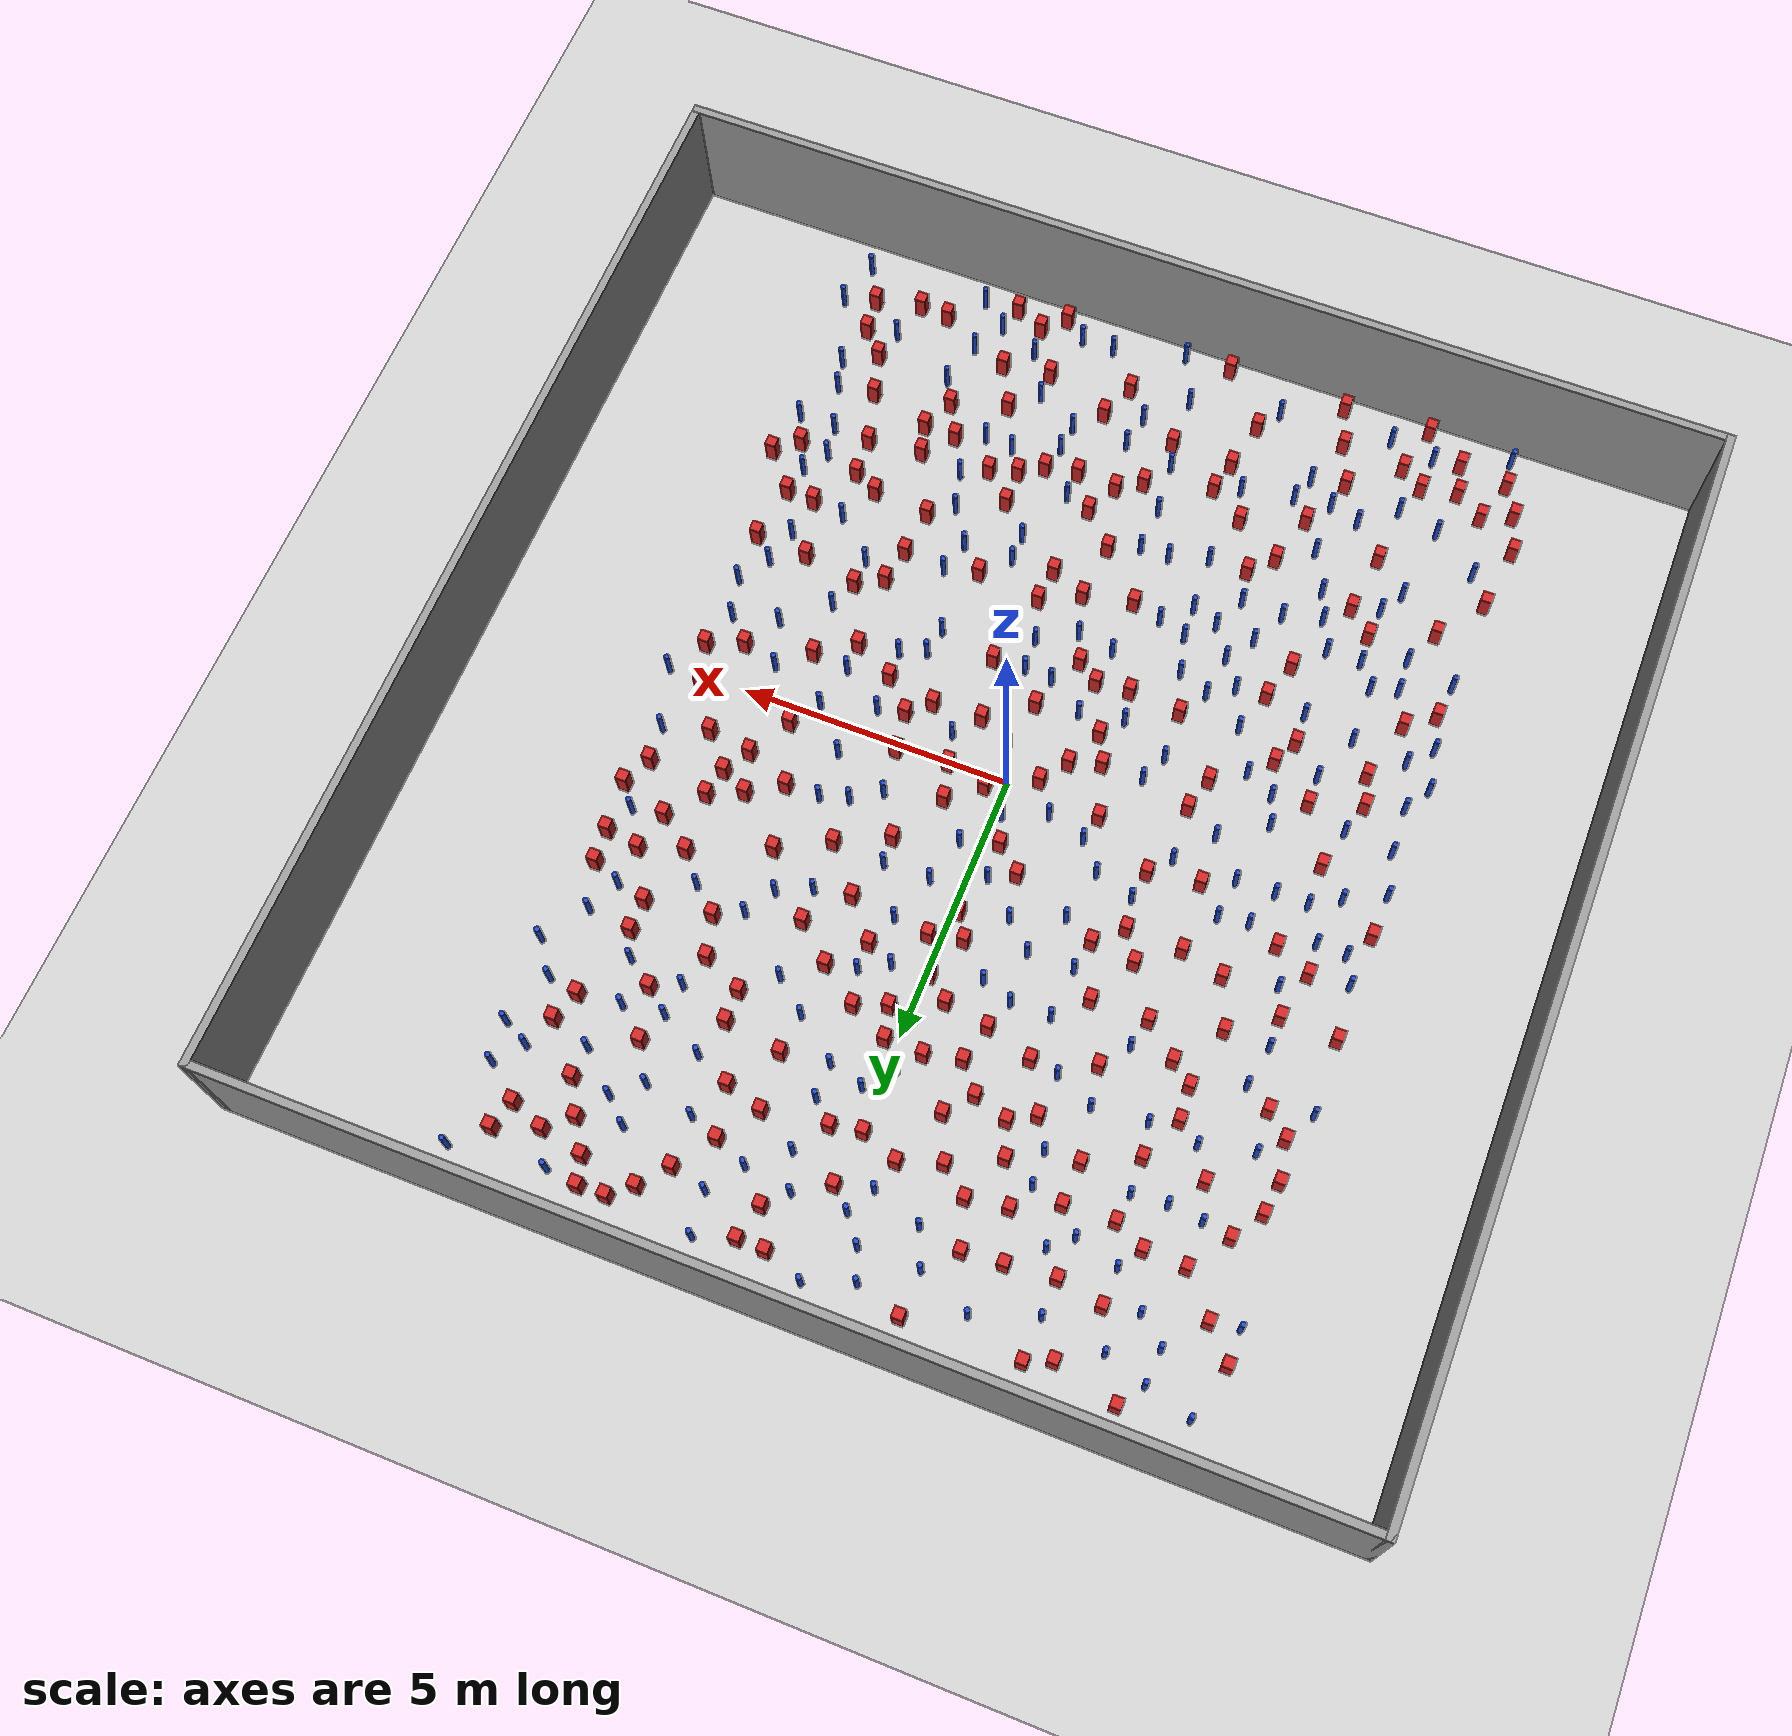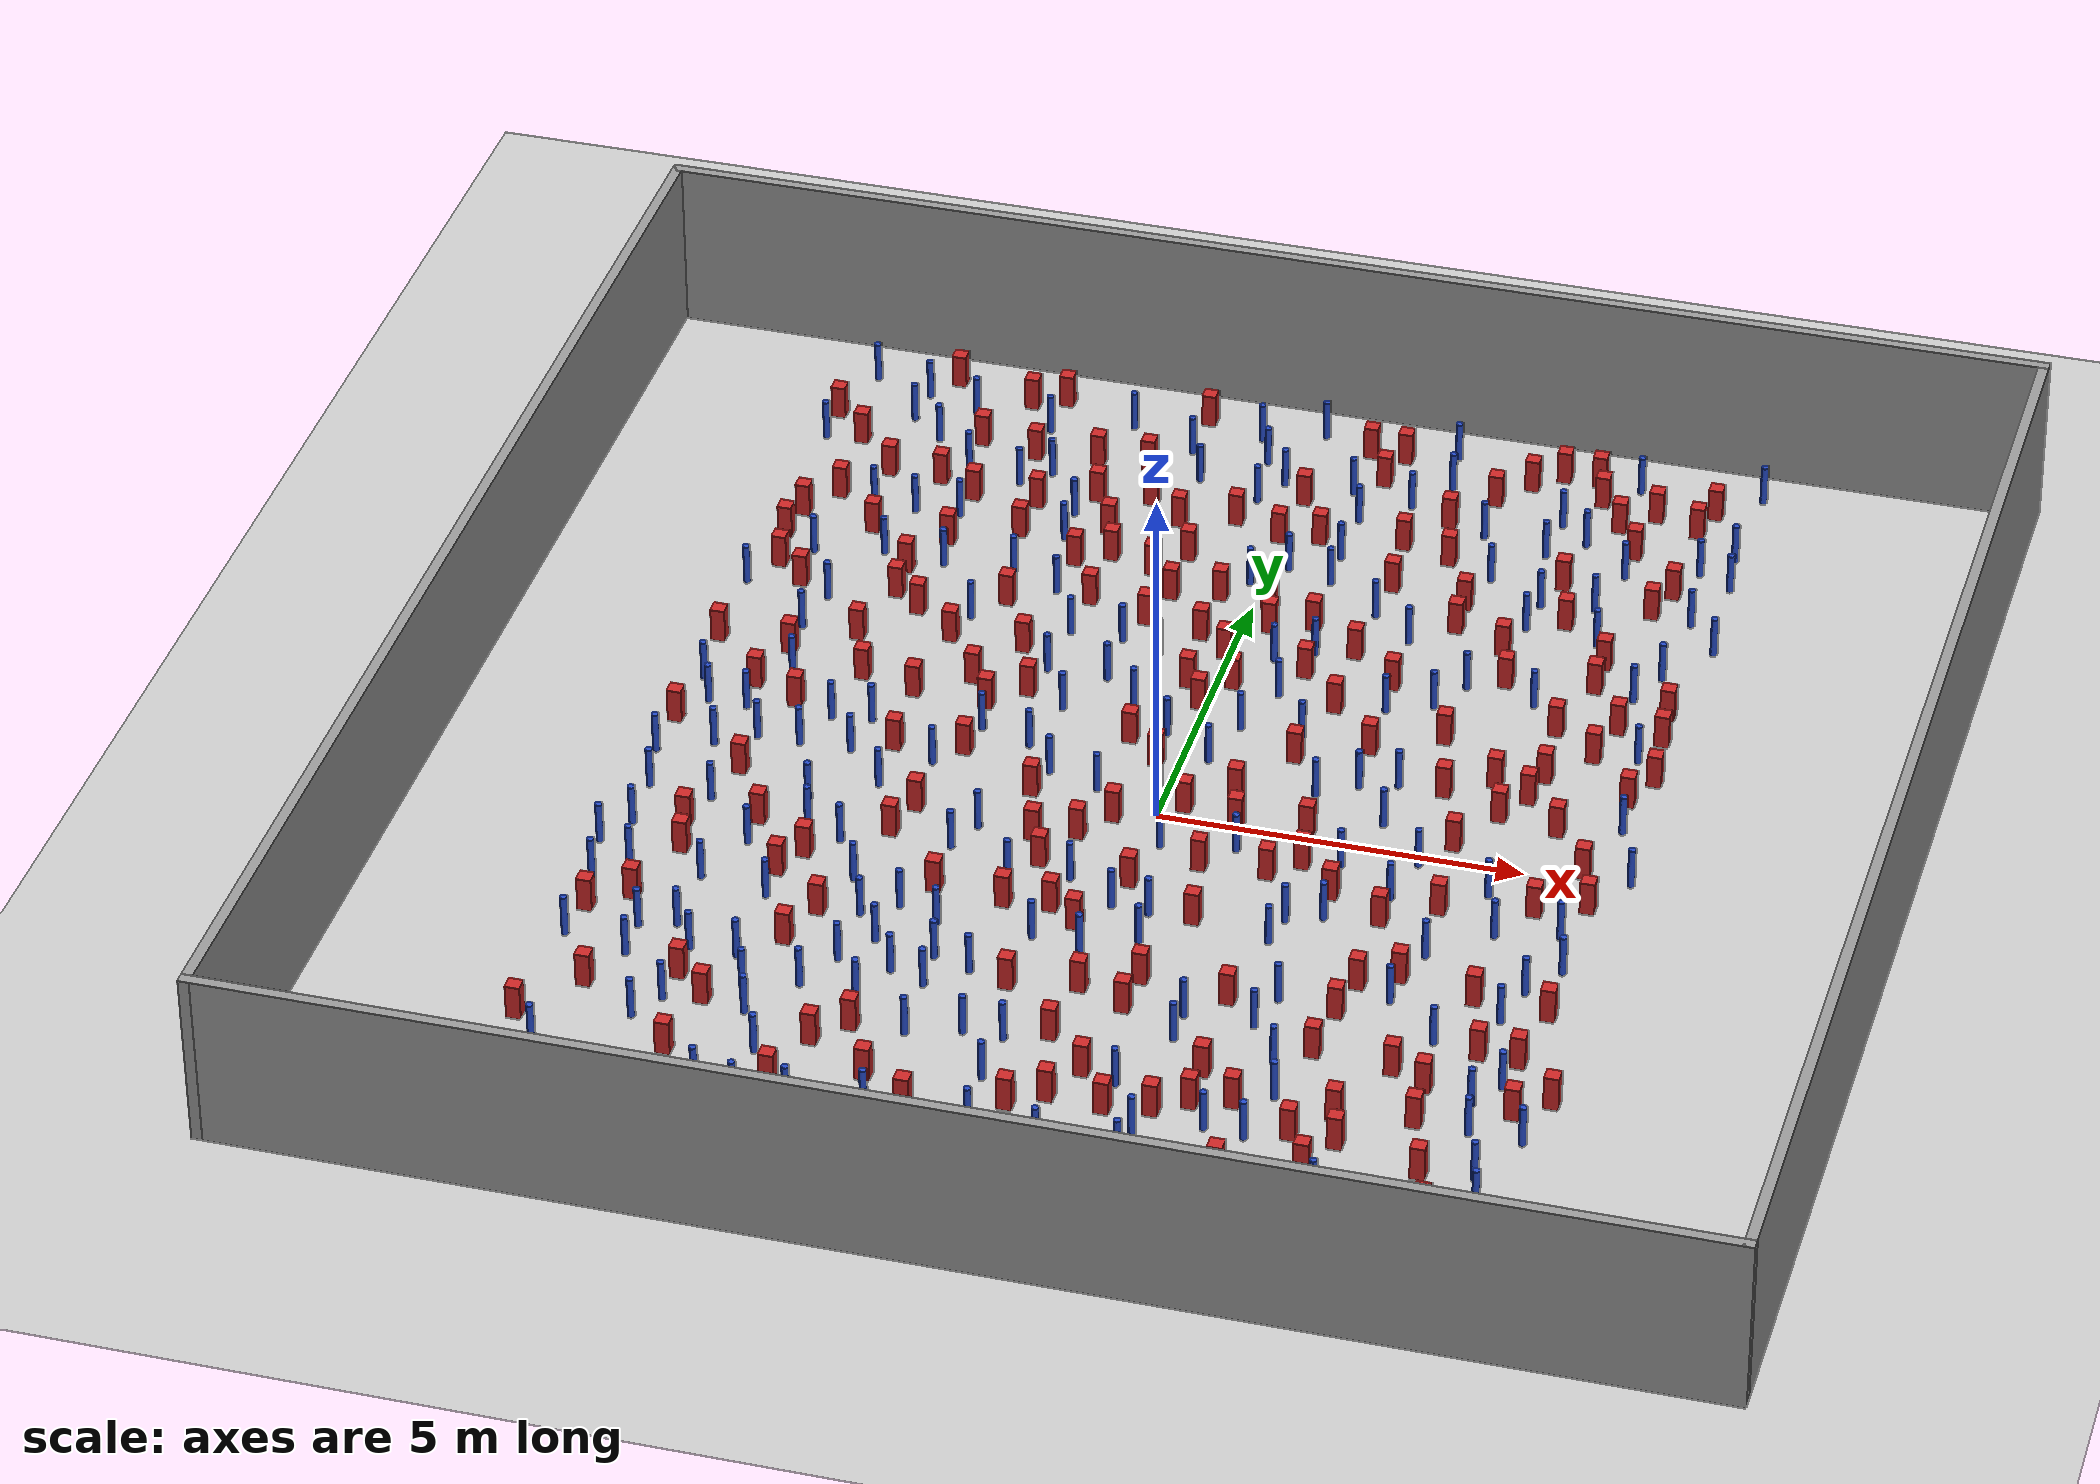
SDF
<sdf version="1.6">
 <world name="default">
  <light name="sun" type="directional">
   <pose>0 0 1000 0 -0 0</pose>
   <diffuse>0.8 0.8 0.8 1</diffuse>
   <specular>0.1 0.1 0.1 1</specular>
   <attenuation>
    <range>1000</range>
    <constant>0.9</constant>
    <linear>0.01</linear>
    <quadratic>0.001</quadratic>
   </attenuation>
   <direction>-0.5 0.5 -1</direction>
  </light>
  <model name="ground_plane">
   <static>1</static>
   <link name="link">
    <collision name="collision">
     <geometry><plane><normal>0 0 1</normal><size>100 100</size></plane></geometry>
     <surface><friction><ode><mu>100</mu><mu2>50</mu2></ode></friction></surface>
    </collision>
    <visual name="visual">
     <cast_shadows>0</cast_shadows>
     <geometry><plane><normal>0 0 1</normal><size>100 100</size></plane></geometry>
     <material>
      <ambient>1.0 1.0 1.0 1.0</ambient>
      <diffuse>0.8 0.8 0.8 1.0</diffuse>
      <specular>0.01 0.01 0.01 1.000000</specular>
     </material>
    </visual>
   </link>
  </model>
  <gravity>0 0 -9.8</gravity>
  <magnetic_field>6e-06 2.3e-05 -4.2e-05</magnetic_field>
  <atmosphere type="adiabatic"/>
  <physics name="default_physics" default="0" type="ode">
   <max_step_size>0.001</max_step_size>
   <real_time_factor>1</real_time_factor>
   <real_time_update_rate>1000</real_time_update_rate>
  </physics>
  <scene><ambient>0.4 0.4 0.4 1</ambient><background>0.7 0.7 0.7 1</background><shadows>1</shadows></scene>
  <spherical_coordinates>
   <surface_model>EARTH_WGS84</surface_model>
   <latitude_deg>0</latitude_deg>
   <longitude_deg>0</longitude_deg>
   <elevation>0</elevation>
   <heading_deg>0</heading_deg>
  </spherical_coordinates>
  <plugin name="gazebo_occupancy_map" filename="libgazebo_2Dmap_plugin.so">
   <map_resolution>0.05</map_resolution>
   <map_topic>generated_map</map_topic>
   <map_height>0.01</map_height>
   <map_size_x>50</map_size_x>
   <map_size_y>50</map_size_y>
  </plugin>
  <model name="NamedLocations">
   <static>true</static>
   <link name="DefaultStart"><pose>8.5 0 0 0 0 3.14</pose></link>
  </model>
  <model name="20x20_walls">
   <pose>0.044518 0.176112 0 0 -0 0</pose>
   <link name="Wall_1">
    <collision name="Wall_1_Collision">
     <geometry><box><size>20 0.15 2.5</size></box></geometry>
     <pose>0 0 1.25 0 -0 0</pose>
    </collision>
    <visual name="Wall_1_Visual">
     <pose>0 0 1.25 0 -0 0</pose>
     <geometry><box><size>20 0.15 2.5</size></box></geometry>
     <material>
      <script><uri>file://media/materials/scripts/gazebo.material</uri><name>Gazebo/Grey</name></script>
      <ambient>0.976471 0.992157 1 1</ambient>
     </material>
     <meta><layer>0</layer></meta>
    </visual>
    <pose>0 9.925 0 0 -0 0</pose>
   </link>
   <link name="Wall_3">
    <collision name="Wall_3_Collision">
     <geometry><box><size>20 0.15 2.5</size></box></geometry>
     <pose>0 0 1.25 0 -0 0</pose>
    </collision>
    <visual name="Wall_3_Visual">
     <pose>0 0 1.25 0 -0 0</pose>
     <geometry><box><size>20 0.15 2.5</size></box></geometry>
     <material>
      <script><uri>file://media/materials/scripts/gazebo.material</uri><name>Gazebo/Grey</name></script>
      <ambient>0.976471 0.992157 1 1</ambient>
     </material>
     <meta><layer>0</layer></meta>
    </visual>
    <pose>9.925 0 0 0 0 -1.5708</pose>
   </link>
   <link name="Wall_4">
    <collision name="Wall_4_Collision">
     <geometry><box><size>20 0.15 2.5</size></box></geometry>
     <pose>0 0 1.25 0 -0 0</pose>
    </collision>
    <visual name="Wall_4_Visual">
     <pose>0 0 1.25 0 -0 0</pose>
     <geometry><box><size>20 0.15 2.5</size></box></geometry>
     <material>
      <script><uri>file://media/materials/scripts/gazebo.material</uri><name>Gazebo/Grey</name></script>
      <ambient>0.976471 0.992157 1 1</ambient>
     </material>
     <meta><layer>0</layer></meta>
    </visual>
    <pose>0 -9.925 0 0 -0 3.14159</pose>
   </link>
   <link name="Wall_5">
    <collision name="Wall_5_Collision">
     <geometry><box><size>20 0.15 2.5</size></box></geometry>
     <pose>0 0 1.25 0 -0 0</pose>
    </collision>
    <visual name="Wall_5_Visual">
     <pose>0 0 1.25 0 -0 0</pose>
     <geometry><box><size>20 0.15 2.5</size></box></geometry>
     <material>
      <script><uri>file://media/materials/scripts/gazebo.material</uri><name>Gazebo/Grey</name></script>
      <ambient>0.976471 0.992157 1 1</ambient>
     </material>
     <meta><layer>0</layer></meta>
    </visual>
    <pose>-9.925 0 0 0 -0 1.5708</pose>
   </link>
   <static>1</static>
  </model>
  <model name="pole_obstacle0">
   <static>true</static>
   <pose>6.26737419633 -9.08554294742 -3.09024884793e-07 -7.19054271912e-07 -2.1131507513e-07 -1.93935509261e-07</pose>
   <link name="link">
    <pose>0 0 0.3 0 -0 0</pose>
    <inertial>
     <mass>1</mass>
     <inertia><ixx>0.145833</ixx><ixy>0</ixy><ixz>0</ixz><iyy>0.145833</iyy><iyz>0</iyz><izz>0.125</izz></inertia>
    </inertial>
    <collision name="collision">
     <geometry><cylinder><radius>0.05</radius><length>.6</length></cylinder></geometry>
    </collision>
    <visual name="visual">
     <geometry><cylinder><radius>0.05</radius><length>.6</length></cylinder></geometry>
     <material>
      <script><name>Gazebo/Blue</name><uri>file://media/materials/scripts/gazebo.material</uri></script>
     </material>
    </visual>
   </link>
  </model>
  <model name="pole_obstacle1">
   <static>true</static>
   <pose>-2.15343908815 -3.05800614078 -3.09024884793e-07 -7.19054271912e-07 -2.11315075144e-07 -1.93935509271e-07</pose>
   <link name="link">
    <pose>0 0 0.3 0 -0 0</pose>
    <inertial>
     <mass>1</mass>
     <inertia><ixx>0.145833</ixx><ixy>0</ixy><ixz>0</ixz><iyy>0.145833</iyy><iyz>0</iyz><izz>0.125</izz></inertia>
    </inertial>
    <collision name="collision">
     <geometry><cylinder><radius>0.05</radius><length>.6</length></cylinder></geometry>
    </collision>
    <visual name="visual">
     <geometry><cylinder><radius>0.05</radius><length>.6</length></cylinder></geometry>
     <material>
      <script><name>Gazebo/Blue</name><uri>file://media/materials/scripts/gazebo.material</uri></script>
     </material>
    </visual>
   </link>
  </model>
  <model name="square_post_obstacle0">
   <static>true</static>
   <pose>0.0412919475653 7.74487756487 -4.36207812815e-07 3.75137919937e-06 9.77721102514e-07 2.47381364184e-05</pose>
   <link name="link">
    <pose>0 0 0.25 0 -0 0</pose>
    <inertial>
     <mass>100</mass>
     <inertia>
      <ixx>0.166667</ixx>
      <ixy>0</ixy>
      <ixz>0</ixz>
      <iyy>0.166667</iyy>
      <iyz>0</iyz>
      <izz>0.166667</izz>
     </inertia>
    </inertial>
    <collision name="collision"><geometry><box><size>.2 .2 .5</size></box></geometry></collision>
    <visual name="visual">
     <geometry><box><size>.2 .2 .5</size></box></geometry>
     <material>
      <script><name>Gazebo/Red</name><uri>file://media/materials/scripts/gazebo.material</uri></script>
     </material>
    </visual>
   </link>
  </model>
  <model name="square_post_obstacle1">
   <static>true</static>
   <pose>0.52450580127 -5.58498487305 -4.36207812815e-07 3.75137919937e-06 9.77721102514e-07 2.47381364184e-05</pose>
   <link name="link">
    <pose>0 0 0.25 0 -0 0</pose>
    <inertial>
     <mass>100</mass>
     <inertia>
      <ixx>0.166667</ixx>
      <ixy>0</ixy>
      <ixz>0</ixz>
      <iyy>0.166667</iyy>
      <iyz>0</iyz>
      <izz>0.166667</izz>
     </inertia>
    </inertial>
    <collision name="collision"><geometry><box><size>.2 .2 .5</size></box></geometry></collision>
    <visual name="visual">
     <geometry><box><size>.2 .2 .5</size></box></geometry>
     <material>
      <script><name>Gazebo/Red</name><uri>file://media/materials/scripts/gazebo.material</uri></script>
     </material>
    </visual>
   </link>
  </model>
  <model name="pole_obstacle2">
   <static>true</static>
   <pose>-6.78596808502 1.45524734911 -3.09024884793e-07 -7.19054271912e-07 -2.11315075124e-07 -1.93935509261e-07</pose>
   <link name="link">
    <pose>0 0 0.3 0 -0 0</pose>
    <inertial>
     <mass>1</mass>
     <inertia><ixx>0.145833</ixx><ixy>0</ixy><ixz>0</ixz><iyy>0.145833</iyy><iyz>0</iyz><izz>0.125</izz></inertia>
    </inertial>
    <collision name="collision">
     <geometry><cylinder><radius>0.05</radius><length>.6</length></cylinder></geometry>
    </collision>
    <visual name="visual">
     <geometry><cylinder><radius>0.05</radius><length>.6</length></cylinder></geometry>
     <material>
      <script><name>Gazebo/Blue</name><uri>file://media/materials/scripts/gazebo.material</uri></script>
     </material>
    </visual>
   </link>
  </model>
  <model name="pole_obstacle3">
   <static>true</static>
   <pose>-0.961101204627 3.58513659789 -3.09024884793e-07 -7.19054271912e-07 -2.11315075131e-07 -1.93935509264e-07</pose>
   <link name="link">
    <pose>0 0 0.3 0 -0 0</pose>
    <inertial>
     <mass>1</mass>
     <inertia><ixx>0.145833</ixx><ixy>0</ixy><ixz>0</ixz><iyy>0.145833</iyy><iyz>0</iyz><izz>0.125</izz></inertia>
    </inertial>
    <collision name="collision">
     <geometry><cylinder><radius>0.05</radius><length>.6</length></cylinder></geometry>
    </collision>
    <visual name="visual">
     <geometry><cylinder><radius>0.05</radius><length>.6</length></cylinder></geometry>
     <material>
      <script><name>Gazebo/Blue</name><uri>file://media/materials/scripts/gazebo.material</uri></script>
     </material>
    </visual>
   </link>
  </model>
  <model name="pole_obstacle4">
   <static>true</static>
   <pose>-5.84009545535 -1.18611742266 -3.09024884793e-07 -7.19054271912e-07 -2.11315075124e-07 -1.93935509261e-07</pose>
   <link name="link">
    <pose>0 0 0.3 0 -0 0</pose>
    <inertial>
     <mass>1</mass>
     <inertia><ixx>0.145833</ixx><ixy>0</ixy><ixz>0</ixz><iyy>0.145833</iyy><iyz>0</iyz><izz>0.125</izz></inertia>
    </inertial>
    <collision name="collision">
     <geometry><cylinder><radius>0.05</radius><length>.6</length></cylinder></geometry>
    </collision>
    <visual name="visual">
     <geometry><cylinder><radius>0.05</radius><length>.6</length></cylinder></geometry>
     <material>
      <script><name>Gazebo/Blue</name><uri>file://media/materials/scripts/gazebo.material</uri></script>
     </material>
    </visual>
   </link>
  </model>
  <model name="pole_obstacle5">
   <static>true</static>
   <pose>-4.83515867426 1.01069919026 -3.09024884793e-07 -7.19054271912e-07 -2.11315075124e-07 -1.9393550926e-07</pose>
   <link name="link">
    <pose>0 0 0.3 0 -0 0</pose>
    <inertial>
     <mass>1</mass>
     <inertia><ixx>0.145833</ixx><ixy>0</ixy><ixz>0</ixz><iyy>0.145833</iyy><iyz>0</iyz><izz>0.125</izz></inertia>
    </inertial>
    <collision name="collision">
     <geometry><cylinder><radius>0.05</radius><length>.6</length></cylinder></geometry>
    </collision>
    <visual name="visual">
     <geometry><cylinder><radius>0.05</radius><length>.6</length></cylinder></geometry>
     <material>
      <script><name>Gazebo/Blue</name><uri>file://media/materials/scripts/gazebo.material</uri></script>
     </material>
    </visual>
   </link>
  </model>
  <model name="pole_obstacle6">
   <static>true</static>
   <pose>-2.80028451918 1.29856540325 -3.09024884793e-07 -7.19054271912e-07 -2.11315075122e-07 -1.93935509259e-07</pose>
   <link name="link">
    <pose>0 0 0.3 0 -0 0</pose>
    <inertial>
     <mass>1</mass>
     <inertia><ixx>0.145833</ixx><ixy>0</ixy><ixz>0</ixz><iyy>0.145833</iyy><iyz>0</iyz><izz>0.125</izz></inertia>
    </inertial>
    <collision name="collision">
     <geometry><cylinder><radius>0.05</radius><length>.6</length></cylinder></geometry>
    </collision>
    <visual name="visual">
     <geometry><cylinder><radius>0.05</radius><length>.6</length></cylinder></geometry>
     <material>
      <script><name>Gazebo/Blue</name><uri>file://media/materials/scripts/gazebo.material</uri></script>
     </material>
    </visual>
   </link>
  </model>
  <model name="square_post_obstacle2">
   <static>true</static>
   <pose>0.737378162376 -3.52441754749 -4.36207812815e-07 3.75137919937e-06 9.77721102514e-07 2.47381364184e-05</pose>
   <link name="link">
    <pose>0 0 0.25 0 -0 0</pose>
    <inertial>
     <mass>100</mass>
     <inertia>
      <ixx>0.166667</ixx>
      <ixy>0</ixy>
      <ixz>0</ixz>
      <iyy>0.166667</iyy>
      <iyz>0</iyz>
      <izz>0.166667</izz>
     </inertia>
    </inertial>
    <collision name="collision"><geometry><box><size>.2 .2 .5</size></box></geometry></collision>
    <visual name="visual">
     <geometry><box><size>.2 .2 .5</size></box></geometry>
     <material>
      <script><name>Gazebo/Red</name><uri>file://media/materials/scripts/gazebo.material</uri></script>
     </material>
    </visual>
   </link>
  </model>
  <model name="square_post_obstacle3">
   <static>true</static>
   <pose>-1.75697244026 0.0820095088435 -4.36207812815e-07 3.75137919937e-06 9.77721102514e-07 2.47381364184e-05</pose>
   <link name="link">
    <pose>0 0 0.25 0 -0 0</pose>
    <inertial>
     <mass>100</mass>
     <inertia>
      <ixx>0.166667</ixx>
      <ixy>0</ixy>
      <ixz>0</ixz>
      <iyy>0.166667</iyy>
      <iyz>0</iyz>
      <izz>0.166667</izz>
     </inertia>
    </inertial>
    <collision name="collision"><geometry><box><size>.2 .2 .5</size></box></geometry></collision>
    <visual name="visual">
     <geometry><box><size>.2 .2 .5</size></box></geometry>
     <material>
      <script><name>Gazebo/Red</name><uri>file://media/materials/scripts/gazebo.material</uri></script>
     </material>
    </visual>
   </link>
  </model>
  <model name="square_post_obstacle4">
   <static>true</static>
   <pose>2.7346866321 -8.96292127128 -4.36207812815e-07 3.75137919937e-06 9.77721102514e-07 2.47381364184e-05</pose>
   <link name="link">
    <pose>0 0 0.25 0 -0 0</pose>
    <inertial>
     <mass>100</mass>
     <inertia>
      <ixx>0.166667</ixx>
      <ixy>0</ixy>
      <ixz>0</ixz>
      <iyy>0.166667</iyy>
      <iyz>0</iyz>
      <izz>0.166667</izz>
     </inertia>
    </inertial>
    <collision name="collision"><geometry><box><size>.2 .2 .5</size></box></geometry></collision>
    <visual name="visual">
     <geometry><box><size>.2 .2 .5</size></box></geometry>
     <material>
      <script><name>Gazebo/Red</name><uri>file://media/materials/scripts/gazebo.material</uri></script>
     </material>
    </visual>
   </link>
  </model>
  <model name="pole_obstacle7">
   <static>true</static>
   <pose>-1.17192480887 -5.19381114242 -3.09024884793e-07 -7.19054271912e-07 -2.11315075134e-07 -1.93935509265e-07</pose>
   <link name="link">
    <pose>0 0 0.3 0 -0 0</pose>
    <inertial>
     <mass>1</mass>
     <inertia><ixx>0.145833</ixx><ixy>0</ixy><ixz>0</ixz><iyy>0.145833</iyy><iyz>0</iyz><izz>0.125</izz></inertia>
    </inertial>
    <collision name="collision">
     <geometry><cylinder><radius>0.05</radius><length>.6</length></cylinder></geometry>
    </collision>
    <visual name="visual">
     <geometry><cylinder><radius>0.05</radius><length>.6</length></cylinder></geometry>
     <material>
      <script><name>Gazebo/Blue</name><uri>file://media/materials/scripts/gazebo.material</uri></script>
     </material>
    </visual>
   </link>
  </model>
  <model name="pole_obstacle8">
   <static>true</static>
   <pose>2.31660148392 -6.29924024177 -3.09024884793e-07 -7.19054271912e-07 -2.11315075134e-07 -1.93935509266e-07</pose>
   <link name="link">
    <pose>0 0 0.3 0 -0 0</pose>
    <inertial>
     <mass>1</mass>
     <inertia><ixx>0.145833</ixx><ixy>0</ixy><ixz>0</ixz><iyy>0.145833</iyy><iyz>0</iyz><izz>0.125</izz></inertia>
    </inertial>
    <collision name="collision">
     <geometry><cylinder><radius>0.05</radius><length>.6</length></cylinder></geometry>
    </collision>
    <visual name="visual">
     <geometry><cylinder><radius>0.05</radius><length>.6</length></cylinder></geometry>
     <material>
      <script><name>Gazebo/Blue</name><uri>file://media/materials/scripts/gazebo.material</uri></script>
     </material>
    </visual>
   </link>
  </model>
  <model name="square_post_obstacle5">
   <static>true</static>
   <pose>-2.20192147459 5.721006857 -4.36207812815e-07 3.75137919937e-06 9.77721102514e-07 2.47381364184e-05</pose>
   <link name="link">
    <pose>0 0 0.25 0 -0 0</pose>
    <inertial>
     <mass>100</mass>
     <inertia>
      <ixx>0.166667</ixx>
      <ixy>0</ixy>
      <ixz>0</ixz>
      <iyy>0.166667</iyy>
      <iyz>0</iyz>
      <izz>0.166667</izz>
     </inertia>
    </inertial>
    <collision name="collision"><geometry><box><size>.2 .2 .5</size></box></geometry></collision>
    <visual name="visual">
     <geometry><box><size>.2 .2 .5</size></box></geometry>
     <material>
      <script><name>Gazebo/Red</name><uri>file://media/materials/scripts/gazebo.material</uri></script>
     </material>
    </visual>
   </link>
  </model>
  <model name="square_post_obstacle6">
   <static>true</static>
   <pose>-3.31438618754 -1.2716206285 -4.36207812815e-07 3.75137919937e-06 9.77721102514e-07 2.47381364184e-05</pose>
   <link name="link">
    <pose>0 0 0.25 0 -0 0</pose>
    <inertial>
     <mass>100</mass>
     <inertia>
      <ixx>0.166667</ixx>
      <ixy>0</ixy>
      <ixz>0</ixz>
      <iyy>0.166667</iyy>
      <iyz>0</iyz>
      <izz>0.166667</izz>
     </inertia>
    </inertial>
    <collision name="collision"><geometry><box><size>.2 .2 .5</size></box></geometry></collision>
    <visual name="visual">
     <geometry><box><size>.2 .2 .5</size></box></geometry>
     <material>
      <script><name>Gazebo/Red</name><uri>file://media/materials/scripts/gazebo.material</uri></script>
     </material>
    </visual>
   </link>
  </model>
  <model name="square_post_obstacle7">
   <static>true</static>
   <pose>5.32056490058 2.76334823413 -4.36207812815e-07 3.75137919937e-06 9.77721102514e-07 2.47381364184e-05</pose>
   <link name="link">
    <pose>0 0 0.25 0 -0 0</pose>
    <inertial>
     <mass>100</mass>
     <inertia>
      <ixx>0.166667</ixx>
      <ixy>0</ixy>
      <ixz>0</ixz>
      <iyy>0.166667</iyy>
      <iyz>0</iyz>
      <izz>0.166667</izz>
     </inertia>
    </inertial>
    <collision name="collision"><geometry><box><size>.2 .2 .5</size></box></geometry></collision>
    <visual name="visual">
     <geometry><box><size>.2 .2 .5</size></box></geometry>
     <material>
      <script><name>Gazebo/Red</name><uri>file://media/materials/scripts/gazebo.material</uri></script>
     </material>
    </visual>
   </link>
  </model>
  <model name="pole_obstacle9">
   <static>true</static>
   <pose>-1.88588892181 -5.40821671252 -3.09024884793e-07 -7.19054271912e-07 -2.11315075134e-07 -1.93935509265e-07</pose>
   <link name="link">
    <pose>0 0 0.3 0 -0 0</pose>
    <inertial>
     <mass>1</mass>
     <inertia><ixx>0.145833</ixx><ixy>0</ixy><ixz>0</ixz><iyy>0.145833</iyy><iyz>0</iyz><izz>0.125</izz></inertia>
    </inertial>
    <collision name="collision">
     <geometry><cylinder><radius>0.05</radius><length>.6</length></cylinder></geometry>
    </collision>
    <visual name="visual">
     <geometry><cylinder><radius>0.05</radius><length>.6</length></cylinder></geometry>
     <material>
      <script><name>Gazebo/Blue</name><uri>file://media/materials/scripts/gazebo.material</uri></script>
     </material>
    </visual>
   </link>
  </model>
  <model name="pole_obstacle10">
   <static>true</static>
   <pose>-3.60791752947 -7.27064303545 -3.09024884793e-07 -7.19054271912e-07 -2.11315075134e-07 -1.93935509266e-07</pose>
   <link name="link">
    <pose>0 0 0.3 0 -0 0</pose>
    <inertial>
     <mass>1</mass>
     <inertia><ixx>0.145833</ixx><ixy>0</ixy><ixz>0</ixz><iyy>0.145833</iyy><iyz>0</iyz><izz>0.125</izz></inertia>
    </inertial>
    <collision name="collision">
     <geometry><cylinder><radius>0.05</radius><length>.6</length></cylinder></geometry>
    </collision>
    <visual name="visual">
     <geometry><cylinder><radius>0.05</radius><length>.6</length></cylinder></geometry>
     <material>
      <script><name>Gazebo/Blue</name><uri>file://media/materials/scripts/gazebo.material</uri></script>
     </material>
    </visual>
   </link>
  </model>
  <model name="pole_obstacle11">
   <static>true</static>
   <pose>-6.18619844787 0.0251924821739 -3.09024884793e-07 -7.19054271912e-07 -2.11315075117e-07 -1.93935509257e-07</pose>
   <link name="link">
    <pose>0 0 0.3 0 -0 0</pose>
    <inertial>
     <mass>1</mass>
     <inertia><ixx>0.145833</ixx><ixy>0</ixy><ixz>0</ixz><iyy>0.145833</iyy><iyz>0</iyz><izz>0.125</izz></inertia>
    </inertial>
    <collision name="collision">
     <geometry><cylinder><radius>0.05</radius><length>.6</length></cylinder></geometry>
    </collision>
    <visual name="visual">
     <geometry><cylinder><radius>0.05</radius><length>.6</length></cylinder></geometry>
     <material>
      <script><name>Gazebo/Blue</name><uri>file://media/materials/scripts/gazebo.material</uri></script>
     </material>
    </visual>
   </link>
  </model>
  <model name="pole_obstacle12">
   <static>true</static>
   <pose>-0.575961744489 -7.00694699162 -3.09024884793e-07 -7.19054271912e-07 -2.11315075129e-07 -1.93935509261e-07</pose>
   <link name="link">
    <pose>0 0 0.3 0 -0 0</pose>
    <inertial>
     <mass>1</mass>
     <inertia><ixx>0.145833</ixx><ixy>0</ixy><ixz>0</ixz><iyy>0.145833</iyy><iyz>0</iyz><izz>0.125</izz></inertia>
    </inertial>
    <collision name="collision">
     <geometry><cylinder><radius>0.05</radius><length>.6</length></cylinder></geometry>
    </collision>
    <visual name="visual">
     <geometry><cylinder><radius>0.05</radius><length>.6</length></cylinder></geometry>
     <material>
      <script><name>Gazebo/Blue</name><uri>file://media/materials/scripts/gazebo.material</uri></script>
     </material>
    </visual>
   </link>
  </model>
  <model name="square_post_obstacle8">
   <static>true</static>
   <pose>-3.14900808988 -0.646074387854 -4.36207812815e-07 3.75137919937e-06 9.77721102514e-07 2.47381364184e-05</pose>
   <link name="link">
    <pose>0 0 0.25 0 -0 0</pose>
    <inertial>
     <mass>100</mass>
     <inertia>
      <ixx>0.166667</ixx>
      <ixy>0</ixy>
      <ixz>0</ixz>
      <iyy>0.166667</iyy>
      <iyz>0</iyz>
      <izz>0.166667</izz>
     </inertia>
    </inertial>
    <collision name="collision"><geometry><box><size>.2 .2 .5</size></box></geometry></collision>
    <visual name="visual">
     <geometry><box><size>.2 .2 .5</size></box></geometry>
     <material>
      <script><name>Gazebo/Red</name><uri>file://media/materials/scripts/gazebo.material</uri></script>
     </material>
    </visual>
   </link>
  </model>
  <model name="square_post_obstacle9">
   <static>true</static>
   <pose>1.68778716582 2.98436826261 -4.36207812815e-07 3.75137919937e-06 9.77721102514e-07 2.47381364184e-05</pose>
   <link name="link">
    <pose>0 0 0.25 0 -0 0</pose>
    <inertial>
     <mass>100</mass>
     <inertia>
      <ixx>0.166667</ixx>
      <ixy>0</ixy>
      <ixz>0</ixz>
      <iyy>0.166667</iyy>
      <iyz>0</iyz>
      <izz>0.166667</izz>
     </inertia>
    </inertial>
    <collision name="collision"><geometry><box><size>.2 .2 .5</size></box></geometry></collision>
    <visual name="visual">
     <geometry><box><size>.2 .2 .5</size></box></geometry>
     <material>
      <script><name>Gazebo/Red</name><uri>file://media/materials/scripts/gazebo.material</uri></script>
     </material>
    </visual>
   </link>
  </model>
  <model name="pole_obstacle13">
   <static>true</static>
   <pose>3.61538598424 -0.178297688606 -3.09024884793e-07 -7.19054271913e-07 -2.11315075118e-07 -1.93935509258e-07</pose>
   <link name="link">
    <pose>0 0 0.3 0 -0 0</pose>
    <inertial>
     <mass>1</mass>
     <inertia><ixx>0.145833</ixx><ixy>0</ixy><ixz>0</ixz><iyy>0.145833</iyy><iyz>0</iyz><izz>0.125</izz></inertia>
    </inertial>
    <collision name="collision">
     <geometry><cylinder><radius>0.05</radius><length>.6</length></cylinder></geometry>
    </collision>
    <visual name="visual">
     <geometry><cylinder><radius>0.05</radius><length>.6</length></cylinder></geometry>
     <material>
      <script><name>Gazebo/Blue</name><uri>file://media/materials/scripts/gazebo.material</uri></script>
     </material>
    </visual>
   </link>
  </model>
  <model name="square_post_obstacle10">
   <static>true</static>
   <pose>6.00634124442 -2.9178933508 -4.36207812815e-07 3.75137919937e-06 9.77721102514e-07 2.47381364184e-05</pose>
   <link name="link">
    <pose>0 0 0.25 0 -0 0</pose>
    <inertial>
     <mass>100</mass>
     <inertia>
      <ixx>0.166667</ixx>
      <ixy>0</ixy>
      <ixz>0</ixz>
      <iyy>0.166667</iyy>
      <iyz>0</iyz>
      <izz>0.166667</izz>
     </inertia>
    </inertial>
    <collision name="collision"><geometry><box><size>.2 .2 .5</size></box></geometry></collision>
    <visual name="visual">
     <geometry><box><size>.2 .2 .5</size></box></geometry>
     <material>
      <script><name>Gazebo/Red</name><uri>file://media/materials/scripts/gazebo.material</uri></script>
     </material>
    </visual>
   </link>
  </model>
  <model name="square_post_obstacle11">
   <static>true</static>
   <pose>-0.495204404261 5.16524390916 -4.36207812815e-07 3.75137919937e-06 9.77721102514e-07 2.47381364184e-05</pose>
   <link name="link">
    <pose>0 0 0.25 0 -0 0</pose>
    <inertial>
     <mass>100</mass>
     <inertia>
      <ixx>0.166667</ixx>
      <ixy>0</ixy>
      <ixz>0</ixz>
      <iyy>0.166667</iyy>
      <iyz>0</iyz>
      <izz>0.166667</izz>
     </inertia>
    </inertial>
    <collision name="collision"><geometry><box><size>.2 .2 .5</size></box></geometry></collision>
    <visual name="visual">
     <geometry><box><size>.2 .2 .5</size></box></geometry>
     <material>
      <script><name>Gazebo/Red</name><uri>file://media/materials/scripts/gazebo.material</uri></script>
     </material>
    </visual>
   </link>
  </model>
  <model name="pole_obstacle14">
   <static>true</static>
   <pose>5.25515491636 -7.87081092041 -3.09024884793e-07 -7.19054271911e-07 -2.1131507516e-07 -1.93935509277e-07</pose>
   <link name="link">
    <pose>0 0 0.3 0 -0 0</pose>
    <inertial>
     <mass>1</mass>
     <inertia><ixx>0.145833</ixx><ixy>0</ixy><ixz>0</ixz><iyy>0.145833</iyy><iyz>0</iyz><izz>0.125</izz></inertia>
    </inertial>
    <collision name="collision">
     <geometry><cylinder><radius>0.05</radius><length>.6</length></cylinder></geometry>
    </collision>
    <visual name="visual">
     <geometry><cylinder><radius>0.05</radius><length>.6</length></cylinder></geometry>
     <material>
      <script><name>Gazebo/Blue</name><uri>file://media/materials/scripts/gazebo.material</uri></script>
     </material>
    </visual>
   </link>
  </model>
  <model name="pole_obstacle15">
   <static>true</static>
   <pose>-4.20136053964 -4.98345175366 -3.09024884793e-07 -7.19054271911e-07 -2.1131507516e-07 -1.93935509277e-07</pose>
   <link name="link">
    <pose>0 0 0.3 0 -0 0</pose>
    <inertial>
     <mass>1</mass>
     <inertia><ixx>0.145833</ixx><ixy>0</ixy><ixz>0</ixz><iyy>0.145833</iyy><iyz>0</iyz><izz>0.125</izz></inertia>
    </inertial>
    <collision name="collision">
     <geometry><cylinder><radius>0.05</radius><length>.6</length></cylinder></geometry>
    </collision>
    <visual name="visual">
     <geometry><cylinder><radius>0.05</radius><length>.6</length></cylinder></geometry>
     <material>
      <script><name>Gazebo/Blue</name><uri>file://media/materials/scripts/gazebo.material</uri></script>
     </material>
    </visual>
   </link>
  </model>
  <model name="square_post_obstacle12">
   <static>true</static>
   <pose>5.81750560455 -7.76058420391 -4.36207812815e-07 3.75137919937e-06 9.77721102514e-07 2.47381364184e-05</pose>
   <link name="link">
    <pose>0 0 0.25 0 -0 0</pose>
    <inertial>
     <mass>100</mass>
     <inertia>
      <ixx>0.166667</ixx>
      <ixy>0</ixy>
      <ixz>0</ixz>
      <iyy>0.166667</iyy>
      <iyz>0</iyz>
      <izz>0.166667</izz>
     </inertia>
    </inertial>
    <collision name="collision"><geometry><box><size>.2 .2 .5</size></box></geometry></collision>
    <visual name="visual">
     <geometry><box><size>.2 .2 .5</size></box></geometry>
     <material>
      <script><name>Gazebo/Red</name><uri>file://media/materials/scripts/gazebo.material</uri></script>
     </material>
    </visual>
   </link>
  </model>
  <model name="pole_obstacle16">
   <static>true</static>
   <pose>-3.42183137124 5.0093323636 -3.09024884848e-07 -7.19054271903e-07 -2.11315075193e-07 -1.93935509285e-07</pose>
   <link name="link">
    <pose>0 0 0.3 0 -0 0</pose>
    <inertial>
     <mass>1</mass>
     <inertia><ixx>0.145833</ixx><ixy>0</ixy><ixz>0</ixz><iyy>0.145833</iyy><iyz>0</iyz><izz>0.125</izz></inertia>
    </inertial>
    <collision name="collision">
     <geometry><cylinder><radius>0.05</radius><length>.6</length></cylinder></geometry>
    </collision>
    <visual name="visual">
     <geometry><cylinder><radius>0.05</radius><length>.6</length></cylinder></geometry>
     <material>
      <script><name>Gazebo/Blue</name><uri>file://media/materials/scripts/gazebo.material</uri></script>
     </material>
    </visual>
   </link>
  </model>
  <model name="pole_obstacle17">
   <static>true</static>
   <pose>1.41958316251 -7.1327692969 -3.09024884793e-07 -7.19054271912e-07 -2.11315075134e-07 -1.93935509265e-07</pose>
   <link name="link">
    <pose>0 0 0.3 0 -0 0</pose>
    <inertial>
     <mass>1</mass>
     <inertia><ixx>0.145833</ixx><ixy>0</ixy><ixz>0</ixz><iyy>0.145833</iyy><iyz>0</iyz><izz>0.125</izz></inertia>
    </inertial>
    <collision name="collision">
     <geometry><cylinder><radius>0.05</radius><length>.6</length></cylinder></geometry>
    </collision>
    <visual name="visual">
     <geometry><cylinder><radius>0.05</radius><length>.6</length></cylinder></geometry>
     <material>
      <script><name>Gazebo/Blue</name><uri>file://media/materials/scripts/gazebo.material</uri></script>
     </material>
    </visual>
   </link>
  </model>
  <model name="square_post_obstacle13">
   <static>true</static>
   <pose>4.1084067479 -1.06865431788 -4.36207812815e-07 3.75137919937e-06 9.77721102514e-07 2.47381364184e-05</pose>
   <link name="link">
    <pose>0 0 0.25 0 -0 0</pose>
    <inertial>
     <mass>100</mass>
     <inertia>
      <ixx>0.166667</ixx>
      <ixy>0</ixy>
      <ixz>0</ixz>
      <iyy>0.166667</iyy>
      <iyz>0</iyz>
      <izz>0.166667</izz>
     </inertia>
    </inertial>
    <collision name="collision"><geometry><box><size>.2 .2 .5</size></box></geometry></collision>
    <visual name="visual">
     <geometry><box><size>.2 .2 .5</size></box></geometry>
     <material>
      <script><name>Gazebo/Red</name><uri>file://media/materials/scripts/gazebo.material</uri></script>
     </material>
    </visual>
   </link>
  </model>
  <model name="pole_obstacle18">
   <static>true</static>
   <pose>2.68279950998 7.52873391197 -3.09024884793e-07 -7.19054271912e-07 -2.11315075134e-07 -1.93935509266e-07</pose>
   <link name="link">
    <pose>0 0 0.3 0 -0 0</pose>
    <inertial>
     <mass>1</mass>
     <inertia><ixx>0.145833</ixx><ixy>0</ixy><ixz>0</ixz><iyy>0.145833</iyy><iyz>0</iyz><izz>0.125</izz></inertia>
    </inertial>
    <collision name="collision">
     <geometry><cylinder><radius>0.05</radius><length>.6</length></cylinder></geometry>
    </collision>
    <visual name="visual">
     <geometry><cylinder><radius>0.05</radius><length>.6</length></cylinder></geometry>
     <material>
      <script><name>Gazebo/Blue</name><uri>file://media/materials/scripts/gazebo.material</uri></script>
     </material>
    </visual>
   </link>
  </model>
  <model name="square_post_obstacle14">
   <static>true</static>
   <pose>-1.17352878662 5.99044738628 -4.36207812815e-07 3.75137919937e-06 9.77721102514e-07 2.47381364184e-05</pose>
   <link name="link">
    <pose>0 0 0.25 0 -0 0</pose>
    <inertial>
     <mass>100</mass>
     <inertia>
      <ixx>0.166667</ixx>
      <ixy>0</ixy>
      <ixz>0</ixz>
      <iyy>0.166667</iyy>
      <iyz>0</iyz>
      <izz>0.166667</izz>
     </inertia>
    </inertial>
    <collision name="collision"><geometry><box><size>.2 .2 .5</size></box></geometry></collision>
    <visual name="visual">
     <geometry><box><size>.2 .2 .5</size></box></geometry>
     <material>
      <script><name>Gazebo/Red</name><uri>file://media/materials/scripts/gazebo.material</uri></script>
     </material>
    </visual>
   </link>
  </model>
  <model name="pole_obstacle19">
   <static>true</static>
   <pose>0.890356789244 5.87134559342 -3.09024884793e-07 -7.19054271912e-07 -2.11315075129e-07 -1.93935509261e-07</pose>
   <link name="link">
    <pose>0 0 0.3 0 -0 0</pose>
    <inertial>
     <mass>1</mass>
     <inertia><ixx>0.145833</ixx><ixy>0</ixy><ixz>0</ixz><iyy>0.145833</iyy><iyz>0</iyz><izz>0.125</izz></inertia>
    </inertial>
    <collision name="collision">
     <geometry><cylinder><radius>0.05</radius><length>.6</length></cylinder></geometry>
    </collision>
    <visual name="visual">
     <geometry><cylinder><radius>0.05</radius><length>.6</length></cylinder></geometry>
     <material>
      <script><name>Gazebo/Blue</name><uri>file://media/materials/scripts/gazebo.material</uri></script>
     </material>
    </visual>
   </link>
  </model>
  <model name="square_post_obstacle15">
   <static>true</static>
   <pose>5.34885255256 6.27011187974 -4.36207812815e-07 3.75137919937e-06 9.77721102514e-07 2.47381364184e-05</pose>
   <link name="link">
    <pose>0 0 0.25 0 -0 0</pose>
    <inertial>
     <mass>100</mass>
     <inertia>
      <ixx>0.166667</ixx>
      <ixy>0</ixy>
      <ixz>0</ixz>
      <iyy>0.166667</iyy>
      <iyz>0</iyz>
      <izz>0.166667</izz>
     </inertia>
    </inertial>
    <collision name="collision"><geometry><box><size>.2 .2 .5</size></box></geometry></collision>
    <visual name="visual">
     <geometry><box><size>.2 .2 .5</size></box></geometry>
     <material>
      <script><name>Gazebo/Red</name><uri>file://media/materials/scripts/gazebo.material</uri></script>
     </material>
    </visual>
   </link>
  </model>
  <model name="square_post_obstacle16">
   <static>true</static>
   <pose>5.85840954703 -3.97679554772 -4.36207812815e-07 3.75137919937e-06 9.77721102514e-07 2.47381364184e-05</pose>
   <link name="link">
    <pose>0 0 0.25 0 -0 0</pose>
    <inertial>
     <mass>100</mass>
     <inertia>
      <ixx>0.166667</ixx>
      <ixy>0</ixy>
      <ixz>0</ixz>
      <iyy>0.166667</iyy>
      <iyz>0</iyz>
      <izz>0.166667</izz>
     </inertia>
    </inertial>
    <collision name="collision"><geometry><box><size>.2 .2 .5</size></box></geometry></collision>
    <visual name="visual">
     <geometry><box><size>.2 .2 .5</size></box></geometry>
     <material>
      <script><name>Gazebo/Red</name><uri>file://media/materials/scripts/gazebo.material</uri></script>
     </material>
    </visual>
   </link>
  </model>
  <model name="square_post_obstacle17">
   <static>true</static>
   <pose>3.2908703948 2.66182966471 -4.36207812815e-07 3.75137919937e-06 9.77721102514e-07 2.47381364184e-05</pose>
   <link name="link">
    <pose>0 0 0.25 0 -0 0</pose>
    <inertial>
     <mass>100</mass>
     <inertia>
      <ixx>0.166667</ixx>
      <ixy>0</ixy>
      <ixz>0</ixz>
      <iyy>0.166667</iyy>
      <iyz>0</iyz>
      <izz>0.166667</izz>
     </inertia>
    </inertial>
    <collision name="collision"><geometry><box><size>.2 .2 .5</size></box></geometry></collision>
    <visual name="visual">
     <geometry><box><size>.2 .2 .5</size></box></geometry>
     <material>
      <script><name>Gazebo/Red</name><uri>file://media/materials/scripts/gazebo.material</uri></script>
     </material>
    </visual>
   </link>
  </model>
  <model name="pole_obstacle20">
   <static>true</static>
   <pose>-3.68432431921 3.78702391923 -3.09024884793e-07 -7.19054271912e-07 -2.11315075128e-07 -1.93935509262e-07</pose>
   <link name="link">
    <pose>0 0 0.3 0 -0 0</pose>
    <inertial>
     <mass>1</mass>
     <inertia><ixx>0.145833</ixx><ixy>0</ixy><ixz>0</ixz><iyy>0.145833</iyy><iyz>0</iyz><izz>0.125</izz></inertia>
    </inertial>
    <collision name="collision">
     <geometry><cylinder><radius>0.05</radius><length>.6</length></cylinder></geometry>
    </collision>
    <visual name="visual">
     <geometry><cylinder><radius>0.05</radius><length>.6</length></cylinder></geometry>
     <material>
      <script><name>Gazebo/Blue</name><uri>file://media/materials/scripts/gazebo.material</uri></script>
     </material>
    </visual>
   </link>
  </model>
  <model name="pole_obstacle21">
   <static>true</static>
   <pose>2.39913195928 -4.09316448349 -3.09024884793e-07 -7.19054271912e-07 -2.11315075134e-07 -1.93935509266e-07</pose>
   <link name="link">
    <pose>0 0 0.3 0 -0 0</pose>
    <inertial>
     <mass>1</mass>
     <inertia><ixx>0.145833</ixx><ixy>0</ixy><ixz>0</ixz><iyy>0.145833</iyy><iyz>0</iyz><izz>0.125</izz></inertia>
    </inertial>
    <collision name="collision">
     <geometry><cylinder><radius>0.05</radius><length>.6</length></cylinder></geometry>
    </collision>
    <visual name="visual">
     <geometry><cylinder><radius>0.05</radius><length>.6</length></cylinder></geometry>
     <material>
      <script><name>Gazebo/Blue</name><uri>file://media/materials/scripts/gazebo.material</uri></script>
     </material>
    </visual>
   </link>
  </model>
  <model name="pole_obstacle22">
   <static>true</static>
   <pose>5.99709759781 -6.93497436783 -3.09024884793e-07 -7.19054271911e-07 -2.1131507516e-07 -1.93935509277e-07</pose>
   <link name="link">
    <pose>0 0 0.3 0 -0 0</pose>
    <inertial>
     <mass>1</mass>
     <inertia><ixx>0.145833</ixx><ixy>0</ixy><ixz>0</ixz><iyy>0.145833</iyy><iyz>0</iyz><izz>0.125</izz></inertia>
    </inertial>
    <collision name="collision">
     <geometry><cylinder><radius>0.05</radius><length>.6</length></cylinder></geometry>
    </collision>
    <visual name="visual">
     <geometry><cylinder><radius>0.05</radius><length>.6</length></cylinder></geometry>
     <material>
      <script><name>Gazebo/Blue</name><uri>file://media/materials/scripts/gazebo.material</uri></script>
     </material>
    </visual>
   </link>
  </model>
  <model name="pole_obstacle23">
   <static>true</static>
   <pose>2.94145108992 1.47407191343 -3.09024884793e-07 -7.19054271912e-07 -2.11315075122e-07 -1.93935509259e-07</pose>
   <link name="link">
    <pose>0 0 0.3 0 -0 0</pose>
    <inertial>
     <mass>1</mass>
     <inertia><ixx>0.145833</ixx><ixy>0</ixy><ixz>0</ixz><iyy>0.145833</iyy><iyz>0</iyz><izz>0.125</izz></inertia>
    </inertial>
    <collision name="collision">
     <geometry><cylinder><radius>0.05</radius><length>.6</length></cylinder></geometry>
    </collision>
    <visual name="visual">
     <geometry><cylinder><radius>0.05</radius><length>.6</length></cylinder></geometry>
     <material>
      <script><name>Gazebo/Blue</name><uri>file://media/materials/scripts/gazebo.material</uri></script>
     </material>
    </visual>
   </link>
  </model>
  <model name="square_post_obstacle18">
   <static>true</static>
   <pose>3.27307317317 -4.44356269826 -4.36207812815e-07 3.75137919937e-06 9.77721102514e-07 2.47381364184e-05</pose>
   <link name="link">
    <pose>0 0 0.25 0 -0 0</pose>
    <inertial>
     <mass>100</mass>
     <inertia>
      <ixx>0.166667</ixx>
      <ixy>0</ixy>
      <ixz>0</ixz>
      <iyy>0.166667</iyy>
      <iyz>0</iyz>
      <izz>0.166667</izz>
     </inertia>
    </inertial>
    <collision name="collision"><geometry><box><size>.2 .2 .5</size></box></geometry></collision>
    <visual name="visual">
     <geometry><box><size>.2 .2 .5</size></box></geometry>
     <material>
      <script><name>Gazebo/Red</name><uri>file://media/materials/scripts/gazebo.material</uri></script>
     </material>
    </visual>
   </link>
  </model>
  <model name="pole_obstacle24">
   <static>true</static>
   <pose>1.41293197032 2.23322964332 -3.09024884793e-07 -7.19054271912e-07 -2.11315075132e-07 -1.93935509263e-07</pose>
   <link name="link">
    <pose>0 0 0.3 0 -0 0</pose>
    <inertial>
     <mass>1</mass>
     <inertia><ixx>0.145833</ixx><ixy>0</ixy><ixz>0</ixz><iyy>0.145833</iyy><iyz>0</iyz><izz>0.125</izz></inertia>
    </inertial>
    <collision name="collision">
     <geometry><cylinder><radius>0.05</radius><length>.6</length></cylinder></geometry>
    </collision>
    <visual name="visual">
     <geometry><cylinder><radius>0.05</radius><length>.6</length></cylinder></geometry>
     <material>
      <script><name>Gazebo/Blue</name><uri>file://media/materials/scripts/gazebo.material</uri></script>
     </material>
    </visual>
   </link>
  </model>
  <model name="pole_obstacle25">
   <static>true</static>
   <pose>1.47300155585 -4.11947141754 -3.09024884793e-07 -7.19054271912e-07 -2.11315075134e-07 -1.93935509265e-07</pose>
   <link name="link">
    <pose>0 0 0.3 0 -0 0</pose>
    <inertial>
     <mass>1</mass>
     <inertia><ixx>0.145833</ixx><ixy>0</ixy><ixz>0</ixz><iyy>0.145833</iyy><iyz>0</iyz><izz>0.125</izz></inertia>
    </inertial>
    <collision name="collision">
     <geometry><cylinder><radius>0.05</radius><length>.6</length></cylinder></geometry>
    </collision>
    <visual name="visual">
     <geometry><cylinder><radius>0.05</radius><length>.6</length></cylinder></geometry>
     <material>
      <script><name>Gazebo/Blue</name><uri>file://media/materials/scripts/gazebo.material</uri></script>
     </material>
    </visual>
   </link>
  </model>
  <model name="pole_obstacle26">
   <static>true</static>
   <pose>-0.443716990972 -8.43226374889 -3.09024884793e-07 -7.19054271911e-07 -2.11315075166e-07 -1.93935509282e-07</pose>
   <link name="link">
    <pose>0 0 0.3 0 -0 0</pose>
    <inertial>
     <mass>1</mass>
     <inertia><ixx>0.145833</ixx><ixy>0</ixy><ixz>0</ixz><iyy>0.145833</iyy><iyz>0</iyz><izz>0.125</izz></inertia>
    </inertial>
    <collision name="collision">
     <geometry><cylinder><radius>0.05</radius><length>.6</length></cylinder></geometry>
    </collision>
    <visual name="visual">
     <geometry><cylinder><radius>0.05</radius><length>.6</length></cylinder></geometry>
     <material>
      <script><name>Gazebo/Blue</name><uri>file://media/materials/scripts/gazebo.material</uri></script>
     </material>
    </visual>
   </link>
  </model>
  <model name="pole_obstacle27">
   <static>true</static>
   <pose>-5.43413216333 -2.88898753709 -3.09024884793e-07 -7.19054271912e-07 -2.11315075144e-07 -1.93935509269e-07</pose>
   <link name="link">
    <pose>0 0 0.3 0 -0 0</pose>
    <inertial>
     <mass>1</mass>
     <inertia><ixx>0.145833</ixx><ixy>0</ixy><ixz>0</ixz><iyy>0.145833</iyy><iyz>0</iyz><izz>0.125</izz></inertia>
    </inertial>
    <collision name="collision">
     <geometry><cylinder><radius>0.05</radius><length>.6</length></cylinder></geometry>
    </collision>
    <visual name="visual">
     <geometry><cylinder><radius>0.05</radius><length>.6</length></cylinder></geometry>
     <material>
      <script><name>Gazebo/Blue</name><uri>file://media/materials/scripts/gazebo.material</uri></script>
     </material>
    </visual>
   </link>
  </model>
  <model name="pole_obstacle28">
   <static>true</static>
   <pose>-0.87431272571 -3.01375302715 -3.09024884793e-07 -7.19054271912e-07 -2.11315075129e-07 -1.93935509263e-07</pose>
   <link name="link">
    <pose>0 0 0.3 0 -0 0</pose>
    <inertial>
     <mass>1</mass>
     <inertia><ixx>0.145833</ixx><ixy>0</ixy><ixz>0</ixz><iyy>0.145833</iyy><iyz>0</iyz><izz>0.125</izz></inertia>
    </inertial>
    <collision name="collision">
     <geometry><cylinder><radius>0.05</radius><length>.6</length></cylinder></geometry>
    </collision>
    <visual name="visual">
     <geometry><cylinder><radius>0.05</radius><length>.6</length></cylinder></geometry>
     <material>
      <script><name>Gazebo/Blue</name><uri>file://media/materials/scripts/gazebo.material</uri></script>
     </material>
    </visual>
   </link>
  </model>
  <model name="square_post_obstacle19">
   <static>true</static>
   <pose>-1.43632241854 -2.39237902163 -4.36207812815e-07 3.75137919937e-06 9.77721102514e-07 2.47381364184e-05</pose>
   <link name="link">
    <pose>0 0 0.25 0 -0 0</pose>
    <inertial>
     <mass>100</mass>
     <inertia>
      <ixx>0.166667</ixx>
      <ixy>0</ixy>
      <ixz>0</ixz>
      <iyy>0.166667</iyy>
      <iyz>0</iyz>
      <izz>0.166667</izz>
     </inertia>
    </inertial>
    <collision name="collision"><geometry><box><size>.2 .2 .5</size></box></geometry></collision>
    <visual name="visual">
     <geometry><box><size>.2 .2 .5</size></box></geometry>
     <material>
      <script><name>Gazebo/Red</name><uri>file://media/materials/scripts/gazebo.material</uri></script>
     </material>
    </visual>
   </link>
  </model>
  <model name="square_post_obstacle20">
   <static>true</static>
   <pose>-3.73517956588 -3.18736815768 -4.36207812815e-07 3.75137919937e-06 9.77721102514e-07 2.47381364184e-05</pose>
   <link name="link">
    <pose>0 0 0.25 0 -0 0</pose>
    <inertial>
     <mass>100</mass>
     <inertia>
      <ixx>0.166667</ixx>
      <ixy>0</ixy>
      <ixz>0</ixz>
      <iyy>0.166667</iyy>
      <iyz>0</iyz>
      <izz>0.166667</izz>
     </inertia>
    </inertial>
    <collision name="collision"><geometry><box><size>.2 .2 .5</size></box></geometry></collision>
    <visual name="visual">
     <geometry><box><size>.2 .2 .5</size></box></geometry>
     <material>
      <script><name>Gazebo/Red</name><uri>file://media/materials/scripts/gazebo.material</uri></script>
     </material>
    </visual>
   </link>
  </model>
  <model name="pole_obstacle29">
   <static>true</static>
   <pose>5.78170784159 7.39839750086 -3.09024884793e-07 -7.19054271911e-07 -2.1131507516e-07 -1.93935509277e-07</pose>
   <link name="link">
    <pose>0 0 0.3 0 -0 0</pose>
    <inertial>
     <mass>1</mass>
     <inertia><ixx>0.145833</ixx><ixy>0</ixy><ixz>0</ixz><iyy>0.145833</iyy><iyz>0</iyz><izz>0.125</izz></inertia>
    </inertial>
    <collision name="collision">
     <geometry><cylinder><radius>0.05</radius><length>.6</length></cylinder></geometry>
    </collision>
    <visual name="visual">
     <geometry><cylinder><radius>0.05</radius><length>.6</length></cylinder></geometry>
     <material>
      <script><name>Gazebo/Blue</name><uri>file://media/materials/scripts/gazebo.material</uri></script>
     </material>
    </visual>
   </link>
  </model>
  <model name="square_post_obstacle21">
   <static>true</static>
   <pose>3.11512089551 -7.94519400333 -4.36207812815e-07 3.75137919937e-06 9.77721102514e-07 2.47381364184e-05</pose>
   <link name="link">
    <pose>0 0 0.25 0 -0 0</pose>
    <inertial>
     <mass>100</mass>
     <inertia>
      <ixx>0.166667</ixx>
      <ixy>0</ixy>
      <ixz>0</ixz>
      <iyy>0.166667</iyy>
      <iyz>0</iyz>
      <izz>0.166667</izz>
     </inertia>
    </inertial>
    <collision name="collision"><geometry><box><size>.2 .2 .5</size></box></geometry></collision>
    <visual name="visual">
     <geometry><box><size>.2 .2 .5</size></box></geometry>
     <material>
      <script><name>Gazebo/Red</name><uri>file://media/materials/scripts/gazebo.material</uri></script>
     </material>
    </visual>
   </link>
  </model>
  <model name="pole_obstacle30">
   <static>true</static>
   <pose>-2.32471958937 2.85050459554 -3.09024884793e-07 -7.19054271912e-07 -2.11315075144e-07 -1.93935509271e-07</pose>
   <link name="link">
    <pose>0 0 0.3 0 -0 0</pose>
    <inertial>
     <mass>1</mass>
     <inertia><ixx>0.145833</ixx><ixy>0</ixy><ixz>0</ixz><iyy>0.145833</iyy><iyz>0</iyz><izz>0.125</izz></inertia>
    </inertial>
    <collision name="collision">
     <geometry><cylinder><radius>0.05</radius><length>.6</length></cylinder></geometry>
    </collision>
    <visual name="visual">
     <geometry><cylinder><radius>0.05</radius><length>.6</length></cylinder></geometry>
     <material>
      <script><name>Gazebo/Blue</name><uri>file://media/materials/scripts/gazebo.material</uri></script>
     </material>
    </visual>
   </link>
  </model>
  <model name="square_post_obstacle22">
   <static>true</static>
   <pose>-2.60363259935 -5.43729169527 -4.36207812815e-07 3.75137919937e-06 9.77721102514e-07 2.47381364184e-05</pose>
   <link name="link">
    <pose>0 0 0.25 0 -0 0</pose>
    <inertial>
     <mass>100</mass>
     <inertia>
      <ixx>0.166667</ixx>
      <ixy>0</ixy>
      <ixz>0</ixz>
      <iyy>0.166667</iyy>
      <iyz>0</iyz>
      <izz>0.166667</izz>
     </inertia>
    </inertial>
    <collision name="collision"><geometry><box><size>.2 .2 .5</size></box></geometry></collision>
    <visual name="visual">
     <geometry><box><size>.2 .2 .5</size></box></geometry>
     <material>
      <script><name>Gazebo/Red</name><uri>file://media/materials/scripts/gazebo.material</uri></script>
     </material>
    </visual>
   </link>
  </model>
  <model name="square_post_obstacle23">
   <static>true</static>
   <pose>-4.27425139784 -2.02532687391 -4.36207812815e-07 3.75137919937e-06 9.77721102514e-07 2.47381364184e-05</pose>
   <link name="link">
    <pose>0 0 0.25 0 -0 0</pose>
    <inertial>
     <mass>100</mass>
     <inertia>
      <ixx>0.166667</ixx>
      <ixy>0</ixy>
      <ixz>0</ixz>
      <iyy>0.166667</iyy>
      <iyz>0</iyz>
      <izz>0.166667</izz>
     </inertia>
    </inertial>
    <collision name="collision"><geometry><box><size>.2 .2 .5</size></box></geometry></collision>
    <visual name="visual">
     <geometry><box><size>.2 .2 .5</size></box></geometry>
     <material>
      <script><name>Gazebo/Red</name><uri>file://media/materials/scripts/gazebo.material</uri></script>
     </material>
    </visual>
   </link>
  </model>
  <model name="pole_obstacle31">
   <static>true</static>
   <pose>4.26516770433 3.75348475248 -3.09024884793e-07 -7.19054271912e-07 -2.11315075144e-07 -1.93935509269e-07</pose>
   <link name="link">
    <pose>0 0 0.3 0 -0 0</pose>
    <inertial>
     <mass>1</mass>
     <inertia><ixx>0.145833</ixx><ixy>0</ixy><ixz>0</ixz><iyy>0.145833</iyy><iyz>0</iyz><izz>0.125</izz></inertia>
    </inertial>
    <collision name="collision">
     <geometry><cylinder><radius>0.05</radius><length>.6</length></cylinder></geometry>
    </collision>
    <visual name="visual">
     <geometry><cylinder><radius>0.05</radius><length>.6</length></cylinder></geometry>
     <material>
      <script><name>Gazebo/Blue</name><uri>file://media/materials/scripts/gazebo.material</uri></script>
     </material>
    </visual>
   </link>
  </model>
  <model name="square_post_obstacle24">
   <static>true</static>
   <pose>0.205083006094 5.14433365972 -4.36207812815e-07 3.75137919937e-06 9.77721102514e-07 2.47381364184e-05</pose>
   <link name="link">
    <pose>0 0 0.25 0 -0 0</pose>
    <inertial>
     <mass>100</mass>
     <inertia>
      <ixx>0.166667</ixx>
      <ixy>0</ixy>
      <ixz>0</ixz>
      <iyy>0.166667</iyy>
      <iyz>0</iyz>
      <izz>0.166667</izz>
     </inertia>
    </inertial>
    <collision name="collision"><geometry><box><size>.2 .2 .5</size></box></geometry></collision>
    <visual name="visual">
     <geometry><box><size>.2 .2 .5</size></box></geometry>
     <material>
      <script><name>Gazebo/Red</name><uri>file://media/materials/scripts/gazebo.material</uri></script>
     </material>
    </visual>
   </link>
  </model>
  <model name="square_post_obstacle25">
   <static>true</static>
   <pose>-6.83598262515 -6.32217190997 -4.36207812815e-07 3.75137919937e-06 9.77721102514e-07 2.47381364184e-05</pose>
   <link name="link">
    <pose>0 0 0.25 0 -0 0</pose>
    <inertial>
     <mass>100</mass>
     <inertia>
      <ixx>0.166667</ixx>
      <ixy>0</ixy>
      <ixz>0</ixz>
      <iyy>0.166667</iyy>
      <iyz>0</iyz>
      <izz>0.166667</izz>
     </inertia>
    </inertial>
    <collision name="collision"><geometry><box><size>.2 .2 .5</size></box></geometry></collision>
    <visual name="visual">
     <geometry><box><size>.2 .2 .5</size></box></geometry>
     <material>
      <script><name>Gazebo/Red</name><uri>file://media/materials/scripts/gazebo.material</uri></script>
     </material>
    </visual>
   </link>
  </model>
  <model name="square_post_obstacle26">
   <static>true</static>
   <pose>0.228843179192 -6.20012209745 -4.36207812815e-07 3.75137919937e-06 9.77721102514e-07 2.47381364184e-05</pose>
   <link name="link">
    <pose>0 0 0.25 0 -0 0</pose>
    <inertial>
     <mass>100</mass>
     <inertia>
      <ixx>0.166667</ixx>
      <ixy>0</ixy>
      <ixz>0</ixz>
      <iyy>0.166667</iyy>
      <iyz>0</iyz>
      <izz>0.166667</izz>
     </inertia>
    </inertial>
    <collision name="collision"><geometry><box><size>.2 .2 .5</size></box></geometry></collision>
    <visual name="visual">
     <geometry><box><size>.2 .2 .5</size></box></geometry>
     <material>
      <script><name>Gazebo/Red</name><uri>file://media/materials/scripts/gazebo.material</uri></script>
     </material>
    </visual>
   </link>
  </model>
  <model name="pole_obstacle32">
   <static>true</static>
   <pose>-4.00805264346 -5.51298378663 -3.09024884793e-07 -7.19054271911e-07 -2.11315075165e-07 -1.9393550928e-07</pose>
   <link name="link">
    <pose>0 0 0.3 0 -0 0</pose>
    <inertial>
     <mass>1</mass>
     <inertia><ixx>0.145833</ixx><ixy>0</ixy><ixz>0</ixz><iyy>0.145833</iyy><iyz>0</iyz><izz>0.125</izz></inertia>
    </inertial>
    <collision name="collision">
     <geometry><cylinder><radius>0.05</radius><length>.6</length></cylinder></geometry>
    </collision>
    <visual name="visual">
     <geometry><cylinder><radius>0.05</radius><length>.6</length></cylinder></geometry>
     <material>
      <script><name>Gazebo/Blue</name><uri>file://media/materials/scripts/gazebo.material</uri></script>
     </material>
    </visual>
   </link>
  </model>
  <model name="square_post_obstacle27">
   <static>true</static>
   <pose>2.35359389487 6.81142448107 -4.36207812815e-07 3.75137919937e-06 9.77721102514e-07 2.47381364184e-05</pose>
   <link name="link">
    <pose>0 0 0.25 0 -0 0</pose>
    <inertial>
     <mass>100</mass>
     <inertia>
      <ixx>0.166667</ixx>
      <ixy>0</ixy>
      <ixz>0</ixz>
      <iyy>0.166667</iyy>
      <iyz>0</iyz>
      <izz>0.166667</izz>
     </inertia>
    </inertial>
    <collision name="collision"><geometry><box><size>.2 .2 .5</size></box></geometry></collision>
    <visual name="visual">
     <geometry><box><size>.2 .2 .5</size></box></geometry>
     <material>
      <script><name>Gazebo/Red</name><uri>file://media/materials/scripts/gazebo.material</uri></script>
     </material>
    </visual>
   </link>
  </model>
  <model name="square_post_obstacle28">
   <static>true</static>
   <pose>1.65492535848 7.02543720147 -4.36207812815e-07 3.75137919937e-06 9.77721102514e-07 2.47381364184e-05</pose>
   <link name="link">
    <pose>0 0 0.25 0 -0 0</pose>
    <inertial>
     <mass>100</mass>
     <inertia>
      <ixx>0.166667</ixx>
      <ixy>0</ixy>
      <ixz>0</ixz>
      <iyy>0.166667</iyy>
      <iyz>0</iyz>
      <izz>0.166667</izz>
     </inertia>
    </inertial>
    <collision name="collision"><geometry><box><size>.2 .2 .5</size></box></geometry></collision>
    <visual name="visual">
     <geometry><box><size>.2 .2 .5</size></box></geometry>
     <material>
      <script><name>Gazebo/Red</name><uri>file://media/materials/scripts/gazebo.material</uri></script>
     </material>
    </visual>
   </link>
  </model>
  <model name="pole_obstacle33">
   <static>true</static>
   <pose>5.46988691667 -4.95631190031 -3.09024884793e-07 -7.19054271911e-07 -2.1131507516e-07 -1.93935509277e-07</pose>
   <link name="link">
    <pose>0 0 0.3 0 -0 0</pose>
    <inertial>
     <mass>1</mass>
     <inertia><ixx>0.145833</ixx><ixy>0</ixy><ixz>0</ixz><iyy>0.145833</iyy><iyz>0</iyz><izz>0.125</izz></inertia>
    </inertial>
    <collision name="collision">
     <geometry><cylinder><radius>0.05</radius><length>.6</length></cylinder></geometry>
    </collision>
    <visual name="visual">
     <geometry><cylinder><radius>0.05</radius><length>.6</length></cylinder></geometry>
     <material>
      <script><name>Gazebo/Blue</name><uri>file://media/materials/scripts/gazebo.material</uri></script>
     </material>
    </visual>
   </link>
  </model>
  <model name="pole_obstacle34">
   <static>true</static>
   <pose>-5.07428625589 -8.86969374546 -3.09024884793e-07 -7.19054271912e-07 -2.1131507513e-07 -1.93935509261e-07</pose>
   <link name="link">
    <pose>0 0 0.3 0 -0 0</pose>
    <inertial>
     <mass>1</mass>
     <inertia><ixx>0.145833</ixx><ixy>0</ixy><ixz>0</ixz><iyy>0.145833</iyy><iyz>0</iyz><izz>0.125</izz></inertia>
    </inertial>
    <collision name="collision">
     <geometry><cylinder><radius>0.05</radius><length>.6</length></cylinder></geometry>
    </collision>
    <visual name="visual">
     <geometry><cylinder><radius>0.05</radius><length>.6</length></cylinder></geometry>
     <material>
      <script><name>Gazebo/Blue</name><uri>file://media/materials/scripts/gazebo.material</uri></script>
     </material>
    </visual>
   </link>
  </model>
  <model name="square_post_obstacle29">
   <static>true</static>
   <pose>2.8286833973 5.2454532795 -4.36207812815e-07 3.75137919937e-06 9.77721102514e-07 2.47381364184e-05</pose>
   <link name="link">
    <pose>0 0 0.25 0 -0 0</pose>
    <inertial>
     <mass>100</mass>
     <inertia>
      <ixx>0.166667</ixx>
      <ixy>0</ixy>
      <ixz>0</ixz>
      <iyy>0.166667</iyy>
      <iyz>0</iyz>
      <izz>0.166667</izz>
     </inertia>
    </inertial>
    <collision name="collision"><geometry><box><size>.2 .2 .5</size></box></geometry></collision>
    <visual name="visual">
     <geometry><box><size>.2 .2 .5</size></box></geometry>
     <material>
      <script><name>Gazebo/Red</name><uri>file://media/materials/scripts/gazebo.material</uri></script>
     </material>
    </visual>
   </link>
  </model>
  <model name="pole_obstacle35">
   <static>true</static>
   <pose>-2.11056786974 -8.8134225359 -3.09024884848e-07 -7.19054271902e-07 -2.11315075199e-07 -1.93935509286e-07</pose>
   <link name="link">
    <pose>0 0 0.3 0 -0 0</pose>
    <inertial>
     <mass>1</mass>
     <inertia><ixx>0.145833</ixx><ixy>0</ixy><ixz>0</ixz><iyy>0.145833</iyy><iyz>0</iyz><izz>0.125</izz></inertia>
    </inertial>
    <collision name="collision">
     <geometry><cylinder><radius>0.05</radius><length>.6</length></cylinder></geometry>
    </collision>
    <visual name="visual">
     <geometry><cylinder><radius>0.05</radius><length>.6</length></cylinder></geometry>
     <material>
      <script><name>Gazebo/Blue</name><uri>file://media/materials/scripts/gazebo.material</uri></script>
     </material>
    </visual>
   </link>
  </model>
  <model name="square_post_obstacle30">
   <static>true</static>
   <pose>-1.22073646992 -1.41158479234 -4.36207812815e-07 3.75137919937e-06 9.77721102514e-07 2.47381364184e-05</pose>
   <link name="link">
    <pose>0 0 0.25 0 -0 0</pose>
    <inertial>
     <mass>100</mass>
     <inertia>
      <ixx>0.166667</ixx>
      <ixy>0</ixy>
      <ixz>0</ixz>
      <iyy>0.166667</iyy>
      <iyz>0</iyz>
      <izz>0.166667</izz>
     </inertia>
    </inertial>
    <collision name="collision"><geometry><box><size>.2 .2 .5</size></box></geometry></collision>
    <visual name="visual">
     <geometry><box><size>.2 .2 .5</size></box></geometry>
     <material>
      <script><name>Gazebo/Red</name><uri>file://media/materials/scripts/gazebo.material</uri></script>
     </material>
    </visual>
   </link>
  </model>
  <model name="pole_obstacle36">
   <static>true</static>
   <pose>2.9625027754 3.37753146015 -3.09024884793e-07 -7.19054271912e-07 -2.11315075144e-07 -1.93935509271e-07</pose>
   <link name="link">
    <pose>0 0 0.3 0 -0 0</pose>
    <inertial>
     <mass>1</mass>
     <inertia><ixx>0.145833</ixx><ixy>0</ixy><ixz>0</ixz><iyy>0.145833</iyy><iyz>0</iyz><izz>0.125</izz></inertia>
    </inertial>
    <collision name="collision">
     <geometry><cylinder><radius>0.05</radius><length>.6</length></cylinder></geometry>
    </collision>
    <visual name="visual">
     <geometry><cylinder><radius>0.05</radius><length>.6</length></cylinder></geometry>
     <material>
      <script><name>Gazebo/Blue</name><uri>file://media/materials/scripts/gazebo.material</uri></script>
     </material>
    </visual>
   </link>
  </model>
  <model name="pole_obstacle37">
   <static>true</static>
   <pose>1.91844083741 0.993248469439 -3.09024884793e-07 -7.19054271912e-07 -2.11315075124e-07 -1.9393550926e-07</pose>
   <link name="link">
    <pose>0 0 0.3 0 -0 0</pose>
    <inertial>
     <mass>1</mass>
     <inertia><ixx>0.145833</ixx><ixy>0</ixy><ixz>0</ixz><iyy>0.145833</iyy><iyz>0</iyz><izz>0.125</izz></inertia>
    </inertial>
    <collision name="collision">
     <geometry><cylinder><radius>0.05</radius><length>.6</length></cylinder></geometry>
    </collision>
    <visual name="visual">
     <geometry><cylinder><radius>0.05</radius><length>.6</length></cylinder></geometry>
     <material>
      <script><name>Gazebo/Blue</name><uri>file://media/materials/scripts/gazebo.material</uri></script>
     </material>
    </visual>
   </link>
  </model>
  <model name="pole_obstacle38">
   <static>true</static>
   <pose>2.8336300995 -4.75992123661 -3.09024884793e-07 -7.19054271912e-07 -2.11315075134e-07 -1.93935509266e-07</pose>
   <link name="link">
    <pose>0 0 0.3 0 -0 0</pose>
    <inertial>
     <mass>1</mass>
     <inertia><ixx>0.145833</ixx><ixy>0</ixy><ixz>0</ixz><iyy>0.145833</iyy><iyz>0</iyz><izz>0.125</izz></inertia>
    </inertial>
    <collision name="collision">
     <geometry><cylinder><radius>0.05</radius><length>.6</length></cylinder></geometry>
    </collision>
    <visual name="visual">
     <geometry><cylinder><radius>0.05</radius><length>.6</length></cylinder></geometry>
     <material>
      <script><name>Gazebo/Blue</name><uri>file://media/materials/scripts/gazebo.material</uri></script>
     </material>
    </visual>
   </link>
  </model>
  <model name="pole_obstacle39">
   <static>true</static>
   <pose>3.2877511063 3.92574632654 -3.09024884793e-07 -7.19054271912e-07 -2.11315075144e-07 -1.93935509271e-07</pose>
   <link name="link">
    <pose>0 0 0.3 0 -0 0</pose>
    <inertial>
     <mass>1</mass>
     <inertia><ixx>0.145833</ixx><ixy>0</ixy><ixz>0</ixz><iyy>0.145833</iyy><iyz>0</iyz><izz>0.125</izz></inertia>
    </inertial>
    <collision name="collision">
     <geometry><cylinder><radius>0.05</radius><length>.6</length></cylinder></geometry>
    </collision>
    <visual name="visual">
     <geometry><cylinder><radius>0.05</radius><length>.6</length></cylinder></geometry>
     <material>
      <script><name>Gazebo/Blue</name><uri>file://media/materials/scripts/gazebo.material</uri></script>
     </material>
    </visual>
   </link>
  </model>
  <model name="pole_obstacle40">
   <static>true</static>
   <pose>2.63347133404 -0.456846381421 -3.09024884793e-07 -7.19054271912e-07 -2.11315075129e-07 -1.93935509263e-07</pose>
   <link name="link">
    <pose>0 0 0.3 0 -0 0</pose>
    <inertial>
     <mass>1</mass>
     <inertia><ixx>0.145833</ixx><ixy>0</ixy><ixz>0</ixz><iyy>0.145833</iyy><iyz>0</iyz><izz>0.125</izz></inertia>
    </inertial>
    <collision name="collision">
     <geometry><cylinder><radius>0.05</radius><length>.6</length></cylinder></geometry>
    </collision>
    <visual name="visual">
     <geometry><cylinder><radius>0.05</radius><length>.6</length></cylinder></geometry>
     <material>
      <script><name>Gazebo/Blue</name><uri>file://media/materials/scripts/gazebo.material</uri></script>
     </material>
    </visual>
   </link>
  </model>
  <model name="pole_obstacle41">
   <static>true</static>
   <pose>3.42475999031 -8.72795376619 -3.09024884848e-07 -7.19054271902e-07 -2.11315075199e-07 -1.93935509286e-07</pose>
   <link name="link">
    <pose>0 0 0.3 0 -0 0</pose>
    <inertial>
     <mass>1</mass>
     <inertia><ixx>0.145833</ixx><ixy>0</ixy><ixz>0</ixz><iyy>0.145833</iyy><iyz>0</iyz><izz>0.125</izz></inertia>
    </inertial>
    <collision name="collision">
     <geometry><cylinder><radius>0.05</radius><length>.6</length></cylinder></geometry>
    </collision>
    <visual name="visual">
     <geometry><cylinder><radius>0.05</radius><length>.6</length></cylinder></geometry>
     <material>
      <script><name>Gazebo/Blue</name><uri>file://media/materials/scripts/gazebo.material</uri></script>
     </material>
    </visual>
   </link>
  </model>
  <model name="pole_obstacle42">
   <static>true</static>
   <pose>-5.41304092149 -3.96565275115 -3.09024884793e-07 -7.19054271912e-07 -2.11315075139e-07 -1.93935509266e-07</pose>
   <link name="link">
    <pose>0 0 0.3 0 -0 0</pose>
    <inertial>
     <mass>1</mass>
     <inertia><ixx>0.145833</ixx><ixy>0</ixy><ixz>0</ixz><iyy>0.145833</iyy><iyz>0</iyz><izz>0.125</izz></inertia>
    </inertial>
    <collision name="collision">
     <geometry><cylinder><radius>0.05</radius><length>.6</length></cylinder></geometry>
    </collision>
    <visual name="visual">
     <geometry><cylinder><radius>0.05</radius><length>.6</length></cylinder></geometry>
     <material>
      <script><name>Gazebo/Blue</name><uri>file://media/materials/scripts/gazebo.material</uri></script>
     </material>
    </visual>
   </link>
  </model>
  <model name="square_post_obstacle31">
   <static>true</static>
   <pose>3.56515329275 1.48128722133 -4.36207812815e-07 3.75137919937e-06 9.77721102514e-07 2.47381364184e-05</pose>
   <link name="link">
    <pose>0 0 0.25 0 -0 0</pose>
    <inertial>
     <mass>100</mass>
     <inertia>
      <ixx>0.166667</ixx>
      <ixy>0</ixy>
      <ixz>0</ixz>
      <iyy>0.166667</iyy>
      <iyz>0</iyz>
      <izz>0.166667</izz>
     </inertia>
    </inertial>
    <collision name="collision"><geometry><box><size>.2 .2 .5</size></box></geometry></collision>
    <visual name="visual">
     <geometry><box><size>.2 .2 .5</size></box></geometry>
     <material>
      <script><name>Gazebo/Red</name><uri>file://media/materials/scripts/gazebo.material</uri></script>
     </material>
    </visual>
   </link>
  </model>
  <model name="square_post_obstacle32">
   <static>true</static>
   <pose>-0.547999389112 -0.199466882305 -4.36207812815e-07 3.75137919937e-06 9.77721102514e-07 2.47381364184e-05</pose>
   <link name="link">
    <pose>0 0 0.25 0 -0 0</pose>
    <inertial>
     <mass>100</mass>
     <inertia>
      <ixx>0.166667</ixx>
      <ixy>0</ixy>
      <ixz>0</ixz>
      <iyy>0.166667</iyy>
      <iyz>0</iyz>
      <izz>0.166667</izz>
     </inertia>
    </inertial>
    <collision name="collision"><geometry><box><size>.2 .2 .5</size></box></geometry></collision>
    <visual name="visual">
     <geometry><box><size>.2 .2 .5</size></box></geometry>
     <material>
      <script><name>Gazebo/Red</name><uri>file://media/materials/scripts/gazebo.material</uri></script>
     </material>
    </visual>
   </link>
  </model>
  <model name="square_post_obstacle33">
   <static>true</static>
   <pose>-1.61386421451 -7.44447705341 -4.36207812815e-07 3.75137919937e-06 9.77721102514e-07 2.47381364184e-05</pose>
   <link name="link">
    <pose>0 0 0.25 0 -0 0</pose>
    <inertial>
     <mass>100</mass>
     <inertia>
      <ixx>0.166667</ixx>
      <ixy>0</ixy>
      <ixz>0</ixz>
      <iyy>0.166667</iyy>
      <iyz>0</iyz>
      <izz>0.166667</izz>
     </inertia>
    </inertial>
    <collision name="collision"><geometry><box><size>.2 .2 .5</size></box></geometry></collision>
    <visual name="visual">
     <geometry><box><size>.2 .2 .5</size></box></geometry>
     <material>
      <script><name>Gazebo/Red</name><uri>file://media/materials/scripts/gazebo.material</uri></script>
     </material>
    </visual>
   </link>
  </model>
  <model name="square_post_obstacle34">
   <static>true</static>
   <pose>-2.40266135204 -2.30965475225 -4.36207812815e-07 3.75137919937e-06 9.77721102514e-07 2.47381364184e-05</pose>
   <link name="link">
    <pose>0 0 0.25 0 -0 0</pose>
    <inertial>
     <mass>100</mass>
     <inertia>
      <ixx>0.166667</ixx>
      <ixy>0</ixy>
      <ixz>0</ixz>
      <iyy>0.166667</iyy>
      <iyz>0</iyz>
      <izz>0.166667</izz>
     </inertia>
    </inertial>
    <collision name="collision"><geometry><box><size>.2 .2 .5</size></box></geometry></collision>
    <visual name="visual">
     <geometry><box><size>.2 .2 .5</size></box></geometry>
     <material>
      <script><name>Gazebo/Red</name><uri>file://media/materials/scripts/gazebo.material</uri></script>
     </material>
    </visual>
   </link>
  </model>
  <model name="pole_obstacle43">
   <static>true</static>
   <pose>5.54117662202 4.21828675575 -3.09024884793e-07 -7.19054271911e-07 -2.1131507516e-07 -1.93935509277e-07</pose>
   <link name="link">
    <pose>0 0 0.3 0 -0 0</pose>
    <inertial>
     <mass>1</mass>
     <inertia><ixx>0.145833</ixx><ixy>0</ixy><ixz>0</ixz><iyy>0.145833</iyy><iyz>0</iyz><izz>0.125</izz></inertia>
    </inertial>
    <collision name="collision">
     <geometry><cylinder><radius>0.05</radius><length>.6</length></cylinder></geometry>
    </collision>
    <visual name="visual">
     <geometry><cylinder><radius>0.05</radius><length>.6</length></cylinder></geometry>
     <material>
      <script><name>Gazebo/Blue</name><uri>file://media/materials/scripts/gazebo.material</uri></script>
     </material>
    </visual>
   </link>
  </model>
  <model name="pole_obstacle44">
   <static>true</static>
   <pose>0.465777182449 -2.14256649682 -3.09024884793e-07 -7.19054271912e-07 -2.11315075129e-07 -1.93935509262e-07</pose>
   <link name="link">
    <pose>0 0 0.3 0 -0 0</pose>
    <inertial>
     <mass>1</mass>
     <inertia><ixx>0.145833</ixx><ixy>0</ixy><ixz>0</ixz><iyy>0.145833</iyy><iyz>0</iyz><izz>0.125</izz></inertia>
    </inertial>
    <collision name="collision">
     <geometry><cylinder><radius>0.05</radius><length>.6</length></cylinder></geometry>
    </collision>
    <visual name="visual">
     <geometry><cylinder><radius>0.05</radius><length>.6</length></cylinder></geometry>
     <material>
      <script><name>Gazebo/Blue</name><uri>file://media/materials/scripts/gazebo.material</uri></script>
     </material>
    </visual>
   </link>
  </model>
  <model name="pole_obstacle45">
   <static>true</static>
   <pose>-3.49073242893 -4.77916171795 -3.09024884793e-07 -7.19054271912e-07 -2.11315075134e-07 -1.93935509266e-07</pose>
   <link name="link">
    <pose>0 0 0.3 0 -0 0</pose>
    <inertial>
     <mass>1</mass>
     <inertia><ixx>0.145833</ixx><ixy>0</ixy><ixz>0</ixz><iyy>0.145833</iyy><iyz>0</iyz><izz>0.125</izz></inertia>
    </inertial>
    <collision name="collision">
     <geometry><cylinder><radius>0.05</radius><length>.6</length></cylinder></geometry>
    </collision>
    <visual name="visual">
     <geometry><cylinder><radius>0.05</radius><length>.6</length></cylinder></geometry>
     <material>
      <script><name>Gazebo/Blue</name><uri>file://media/materials/scripts/gazebo.material</uri></script>
     </material>
    </visual>
   </link>
  </model>
  <model name="square_post_obstacle35">
   <static>true</static>
   <pose>5.54072011842 8.36594991279 -4.36207812815e-07 3.75137919937e-06 9.77721102514e-07 2.47381364184e-05</pose>
   <link name="link">
    <pose>0 0 0.25 0 -0 0</pose>
    <inertial>
     <mass>100</mass>
     <inertia>
      <ixx>0.166667</ixx>
      <ixy>0</ixy>
      <ixz>0</ixz>
      <iyy>0.166667</iyy>
      <iyz>0</iyz>
      <izz>0.166667</izz>
     </inertia>
    </inertial>
    <collision name="collision"><geometry><box><size>.2 .2 .5</size></box></geometry></collision>
    <visual name="visual">
     <geometry><box><size>.2 .2 .5</size></box></geometry>
     <material>
      <script><name>Gazebo/Red</name><uri>file://media/materials/scripts/gazebo.material</uri></script>
     </material>
    </visual>
   </link>
  </model>
  <model name="pole_obstacle46">
   <static>true</static>
   <pose>-3.09255112239 -7.6583903022 -3.09024884793e-07 -7.19054271912e-07 -2.11315075134e-07 -1.93935509266e-07</pose>
   <link name="link">
    <pose>0 0 0.3 0 -0 0</pose>
    <inertial>
     <mass>1</mass>
     <inertia><ixx>0.145833</ixx><ixy>0</ixy><ixz>0</ixz><iyy>0.145833</iyy><iyz>0</iyz><izz>0.125</izz></inertia>
    </inertial>
    <collision name="collision">
     <geometry><cylinder><radius>0.05</radius><length>.6</length></cylinder></geometry>
    </collision>
    <visual name="visual">
     <geometry><cylinder><radius>0.05</radius><length>.6</length></cylinder></geometry>
     <material>
      <script><name>Gazebo/Blue</name><uri>file://media/materials/scripts/gazebo.material</uri></script>
     </material>
    </visual>
   </link>
  </model>
  <model name="pole_obstacle47">
   <static>true</static>
   <pose>-6.76970011362 -4.52454817344 -3.09024884793e-07 -7.19054271911e-07 -2.1131507516e-07 -1.93935509277e-07</pose>
   <link name="link">
    <pose>0 0 0.3 0 -0 0</pose>
    <inertial>
     <mass>1</mass>
     <inertia><ixx>0.145833</ixx><ixy>0</ixy><ixz>0</ixz><iyy>0.145833</iyy><iyz>0</iyz><izz>0.125</izz></inertia>
    </inertial>
    <collision name="collision">
     <geometry><cylinder><radius>0.05</radius><length>.6</length></cylinder></geometry>
    </collision>
    <visual name="visual">
     <geometry><cylinder><radius>0.05</radius><length>.6</length></cylinder></geometry>
     <material>
      <script><name>Gazebo/Blue</name><uri>file://media/materials/scripts/gazebo.material</uri></script>
     </material>
    </visual>
   </link>
  </model>
  <model name="square_post_obstacle36">
   <static>true</static>
   <pose>-0.804968848197 1.59948668566 -4.36207812815e-07 3.75137919937e-06 9.77721102514e-07 2.47381364184e-05</pose>
   <link name="link">
    <pose>0 0 0.25 0 -0 0</pose>
    <inertial>
     <mass>100</mass>
     <inertia>
      <ixx>0.166667</ixx>
      <ixy>0</ixy>
      <ixz>0</ixz>
      <iyy>0.166667</iyy>
      <iyz>0</iyz>
      <izz>0.166667</izz>
     </inertia>
    </inertial>
    <collision name="collision"><geometry><box><size>.2 .2 .5</size></box></geometry></collision>
    <visual name="visual">
     <geometry><box><size>.2 .2 .5</size></box></geometry>
     <material>
      <script><name>Gazebo/Red</name><uri>file://media/materials/scripts/gazebo.material</uri></script>
     </material>
    </visual>
   </link>
  </model>
  <model name="square_post_obstacle37">
   <static>true</static>
   <pose>1.01999393397 8.48975095778 -4.36207812815e-07 3.75137919937e-06 9.77721102514e-07 2.47381364184e-05</pose>
   <link name="link">
    <pose>0 0 0.25 0 -0 0</pose>
    <inertial>
     <mass>100</mass>
     <inertia>
      <ixx>0.166667</ixx>
      <ixy>0</ixy>
      <ixz>0</ixz>
      <iyy>0.166667</iyy>
      <iyz>0</iyz>
      <izz>0.166667</izz>
     </inertia>
    </inertial>
    <collision name="collision"><geometry><box><size>.2 .2 .5</size></box></geometry></collision>
    <visual name="visual">
     <geometry><box><size>.2 .2 .5</size></box></geometry>
     <material>
      <script><name>Gazebo/Red</name><uri>file://media/materials/scripts/gazebo.material</uri></script>
     </material>
    </visual>
   </link>
  </model>
  <model name="pole_obstacle48">
   <static>true</static>
   <pose>-4.4605507308 -4.40775130411 -3.09024884793e-07 -7.19054271911e-07 -2.1131507516e-07 -1.93935509277e-07</pose>
   <link name="link">
    <pose>0 0 0.3 0 -0 0</pose>
    <inertial>
     <mass>1</mass>
     <inertia><ixx>0.145833</ixx><ixy>0</ixy><ixz>0</ixz><iyy>0.145833</iyy><iyz>0</iyz><izz>0.125</izz></inertia>
    </inertial>
    <collision name="collision">
     <geometry><cylinder><radius>0.05</radius><length>.6</length></cylinder></geometry>
    </collision>
    <visual name="visual">
     <geometry><cylinder><radius>0.05</radius><length>.6</length></cylinder></geometry>
     <material>
      <script><name>Gazebo/Blue</name><uri>file://media/materials/scripts/gazebo.material</uri></script>
     </material>
    </visual>
   </link>
  </model>
  <model name="square_post_obstacle38">
   <static>true</static>
   <pose>3.9673430957 -2.62754604842 -4.36207812815e-07 3.75137919937e-06 9.77721102514e-07 2.47381364184e-05</pose>
   <link name="link">
    <pose>0 0 0.25 0 -0 0</pose>
    <inertial>
     <mass>100</mass>
     <inertia>
      <ixx>0.166667</ixx>
      <ixy>0</ixy>
      <ixz>0</ixz>
      <iyy>0.166667</iyy>
      <iyz>0</iyz>
      <izz>0.166667</izz>
     </inertia>
    </inertial>
    <collision name="collision"><geometry><box><size>.2 .2 .5</size></box></geometry></collision>
    <visual name="visual">
     <geometry><box><size>.2 .2 .5</size></box></geometry>
     <material>
      <script><name>Gazebo/Red</name><uri>file://media/materials/scripts/gazebo.material</uri></script>
     </material>
    </visual>
   </link>
  </model>
  <model name="square_post_obstacle39">
   <static>true</static>
   <pose>-6.06323528533 1.51608363607 -4.36207812815e-07 3.75137919937e-06 9.77721102514e-07 2.47381364184e-05</pose>
   <link name="link">
    <pose>0 0 0.25 0 -0 0</pose>
    <inertial>
     <mass>100</mass>
     <inertia>
      <ixx>0.166667</ixx>
      <ixy>0</ixy>
      <ixz>0</ixz>
      <iyy>0.166667</iyy>
      <iyz>0</iyz>
      <izz>0.166667</izz>
     </inertia>
    </inertial>
    <collision name="collision"><geometry><box><size>.2 .2 .5</size></box></geometry></collision>
    <visual name="visual">
     <geometry><box><size>.2 .2 .5</size></box></geometry>
     <material>
      <script><name>Gazebo/Red</name><uri>file://media/materials/scripts/gazebo.material</uri></script>
     </material>
    </visual>
   </link>
  </model>
  <model name="pole_obstacle49">
   <static>true</static>
   <pose>-3.17294523156 -4.12871011493 -3.09024884793e-07 -7.19054271912e-07 -2.11315075134e-07 -1.93935509266e-07</pose>
   <link name="link">
    <pose>0 0 0.3 0 -0 0</pose>
    <inertial>
     <mass>1</mass>
     <inertia><ixx>0.145833</ixx><ixy>0</ixy><ixz>0</ixz><iyy>0.145833</iyy><iyz>0</iyz><izz>0.125</izz></inertia>
    </inertial>
    <collision name="collision">
     <geometry><cylinder><radius>0.05</radius><length>.6</length></cylinder></geometry>
    </collision>
    <visual name="visual">
     <geometry><cylinder><radius>0.05</radius><length>.6</length></cylinder></geometry>
     <material>
      <script><name>Gazebo/Blue</name><uri>file://media/materials/scripts/gazebo.material</uri></script>
     </material>
    </visual>
   </link>
  </model>
  <model name="pole_obstacle50">
   <static>true</static>
   <pose>2.69446637997 -1.63381578746 -3.09024884793e-07 -7.19054271912e-07 -2.11315075122e-07 -1.93935509259e-07</pose>
   <link name="link">
    <pose>0 0 0.3 0 -0 0</pose>
    <inertial>
     <mass>1</mass>
     <inertia><ixx>0.145833</ixx><ixy>0</ixy><ixz>0</ixz><iyy>0.145833</iyy><iyz>0</iyz><izz>0.125</izz></inertia>
    </inertial>
    <collision name="collision">
     <geometry><cylinder><radius>0.05</radius><length>.6</length></cylinder></geometry>
    </collision>
    <visual name="visual">
     <geometry><cylinder><radius>0.05</radius><length>.6</length></cylinder></geometry>
     <material>
      <script><name>Gazebo/Blue</name><uri>file://media/materials/scripts/gazebo.material</uri></script>
     </material>
    </visual>
   </link>
  </model>
  <model name="pole_obstacle51">
   <static>true</static>
   <pose>3.9506112311 -9.16215911548 -3.09024884848e-07 -7.19054271902e-07 -2.11315075199e-07 -1.93935509286e-07</pose>
   <link name="link">
    <pose>0 0 0.3 0 -0 0</pose>
    <inertial>
     <mass>1</mass>
     <inertia><ixx>0.145833</ixx><ixy>0</ixy><ixz>0</ixz><iyy>0.145833</iyy><iyz>0</iyz><izz>0.125</izz></inertia>
    </inertial>
    <collision name="collision">
     <geometry><cylinder><radius>0.05</radius><length>.6</length></cylinder></geometry>
    </collision>
    <visual name="visual">
     <geometry><cylinder><radius>0.05</radius><length>.6</length></cylinder></geometry>
     <material>
      <script><name>Gazebo/Blue</name><uri>file://media/materials/scripts/gazebo.material</uri></script>
     </material>
    </visual>
   </link>
  </model>
  <model name="pole_obstacle52">
   <static>true</static>
   <pose>2.8545146541 -6.36024013476 -3.09024884793e-07 -7.19054271912e-07 -2.11315075134e-07 -1.93935509266e-07</pose>
   <link name="link">
    <pose>0 0 0.3 0 -0 0</pose>
    <inertial>
     <mass>1</mass>
     <inertia><ixx>0.145833</ixx><ixy>0</ixy><ixz>0</ixz><iyy>0.145833</iyy><iyz>0</iyz><izz>0.125</izz></inertia>
    </inertial>
    <collision name="collision">
     <geometry><cylinder><radius>0.05</radius><length>.6</length></cylinder></geometry>
    </collision>
    <visual name="visual">
     <geometry><cylinder><radius>0.05</radius><length>.6</length></cylinder></geometry>
     <material>
      <script><name>Gazebo/Blue</name><uri>file://media/materials/scripts/gazebo.material</uri></script>
     </material>
    </visual>
   </link>
  </model>
  <model name="pole_obstacle53">
   <static>true</static>
   <pose>2.95618056384 0.574802427145 -3.09024884793e-07 -7.19054271913e-07 -2.1131507512e-07 -1.93935509259e-07</pose>
   <link name="link">
    <pose>0 0 0.3 0 -0 0</pose>
    <inertial>
     <mass>1</mass>
     <inertia><ixx>0.145833</ixx><ixy>0</ixy><ixz>0</ixz><iyy>0.145833</iyy><iyz>0</iyz><izz>0.125</izz></inertia>
    </inertial>
    <collision name="collision">
     <geometry><cylinder><radius>0.05</radius><length>.6</length></cylinder></geometry>
    </collision>
    <visual name="visual">
     <geometry><cylinder><radius>0.05</radius><length>.6</length></cylinder></geometry>
     <material>
      <script><name>Gazebo/Blue</name><uri>file://media/materials/scripts/gazebo.material</uri></script>
     </material>
    </visual>
   </link>
  </model>
  <model name="square_post_obstacle40">
   <static>true</static>
   <pose>2.14338092535 7.71940443186 -4.36207812815e-07 3.75137919937e-06 9.77721102514e-07 2.47381364184e-05</pose>
   <link name="link">
    <pose>0 0 0.25 0 -0 0</pose>
    <inertial>
     <mass>100</mass>
     <inertia>
      <ixx>0.166667</ixx>
      <ixy>0</ixy>
      <ixz>0</ixz>
      <iyy>0.166667</iyy>
      <iyz>0</iyz>
      <izz>0.166667</izz>
     </inertia>
    </inertial>
    <collision name="collision"><geometry><box><size>.2 .2 .5</size></box></geometry></collision>
    <visual name="visual">
     <geometry><box><size>.2 .2 .5</size></box></geometry>
     <material>
      <script><name>Gazebo/Red</name><uri>file://media/materials/scripts/gazebo.material</uri></script>
     </material>
    </visual>
   </link>
  </model>
  <model name="pole_obstacle54">
   <static>true</static>
   <pose>-5.72302995833 3.72746954499 -3.09024884793e-07 -7.19054271912e-07 -2.11315075144e-07 -1.93935509269e-07</pose>
   <link name="link">
    <pose>0 0 0.3 0 -0 0</pose>
    <inertial>
     <mass>1</mass>
     <inertia><ixx>0.145833</ixx><ixy>0</ixy><ixz>0</ixz><iyy>0.145833</iyy><iyz>0</iyz><izz>0.125</izz></inertia>
    </inertial>
    <collision name="collision">
     <geometry><cylinder><radius>0.05</radius><length>.6</length></cylinder></geometry>
    </collision>
    <visual name="visual">
     <geometry><cylinder><radius>0.05</radius><length>.6</length></cylinder></geometry>
     <material>
      <script><name>Gazebo/Blue</name><uri>file://media/materials/scripts/gazebo.material</uri></script>
     </material>
    </visual>
   </link>
  </model>
  <model name="square_post_obstacle41">
   <static>true</static>
   <pose>-6.68817704176 -3.88866527212 -4.36207812815e-07 3.75137919937e-06 9.77721102514e-07 2.47381364184e-05</pose>
   <link name="link">
    <pose>0 0 0.25 0 -0 0</pose>
    <inertial>
     <mass>100</mass>
     <inertia>
      <ixx>0.166667</ixx>
      <ixy>0</ixy>
      <ixz>0</ixz>
      <iyy>0.166667</iyy>
      <iyz>0</iyz>
      <izz>0.166667</izz>
     </inertia>
    </inertial>
    <collision name="collision"><geometry><box><size>.2 .2 .5</size></box></geometry></collision>
    <visual name="visual">
     <geometry><box><size>.2 .2 .5</size></box></geometry>
     <material>
      <script><name>Gazebo/Red</name><uri>file://media/materials/scripts/gazebo.material</uri></script>
     </material>
    </visual>
   </link>
  </model>
  <model name="pole_obstacle55">
   <static>true</static>
   <pose>-5.9029251032 -4.10988672549 -3.09024884793e-07 -7.19054271911e-07 -2.1131507516e-07 -1.93935509277e-07</pose>
   <link name="link">
    <pose>0 0 0.3 0 -0 0</pose>
    <inertial>
     <mass>1</mass>
     <inertia><ixx>0.145833</ixx><ixy>0</ixy><ixz>0</ixz><iyy>0.145833</iyy><iyz>0</iyz><izz>0.125</izz></inertia>
    </inertial>
    <collision name="collision">
     <geometry><cylinder><radius>0.05</radius><length>.6</length></cylinder></geometry>
    </collision>
    <visual name="visual">
     <geometry><cylinder><radius>0.05</radius><length>.6</length></cylinder></geometry>
     <material>
      <script><name>Gazebo/Blue</name><uri>file://media/materials/scripts/gazebo.material</uri></script>
     </material>
    </visual>
   </link>
  </model>
  <model name="square_post_obstacle42">
   <static>true</static>
   <pose>-2.29299157943 8.01545349763 -4.36207812815e-07 3.75137919937e-06 9.77721102514e-07 2.47381364184e-05</pose>
   <link name="link">
    <pose>0 0 0.25 0 -0 0</pose>
    <inertial>
     <mass>100</mass>
     <inertia>
      <ixx>0.166667</ixx>
      <ixy>0</ixy>
      <ixz>0</ixz>
      <iyy>0.166667</iyy>
      <iyz>0</iyz>
      <izz>0.166667</izz>
     </inertia>
    </inertial>
    <collision name="collision"><geometry><box><size>.2 .2 .5</size></box></geometry></collision>
    <visual name="visual">
     <geometry><box><size>.2 .2 .5</size></box></geometry>
     <material>
      <script><name>Gazebo/Red</name><uri>file://media/materials/scripts/gazebo.material</uri></script>
     </material>
    </visual>
   </link>
  </model>
  <model name="square_post_obstacle43">
   <static>true</static>
   <pose>-1.75919278025 9.35160729567 -4.36207812815e-07 3.75137919937e-06 9.77721102514e-07 2.47381364184e-05</pose>
   <link name="link">
    <pose>0 0 0.25 0 -0 0</pose>
    <inertial>
     <mass>100</mass>
     <inertia>
      <ixx>0.166667</ixx>
      <ixy>0</ixy>
      <ixz>0</ixz>
      <iyy>0.166667</iyy>
      <iyz>0</iyz>
      <izz>0.166667</izz>
     </inertia>
    </inertial>
    <collision name="collision"><geometry><box><size>.2 .2 .5</size></box></geometry></collision>
    <visual name="visual">
     <geometry><box><size>.2 .2 .5</size></box></geometry>
     <material>
      <script><name>Gazebo/Red</name><uri>file://media/materials/scripts/gazebo.material</uri></script>
     </material>
    </visual>
   </link>
  </model>
  <model name="pole_obstacle56">
   <static>true</static>
   <pose>5.77068111608 -4.50896995325 -3.09024884793e-07 -7.19054271911e-07 -2.1131507516e-07 -1.93935509277e-07</pose>
   <link name="link">
    <pose>0 0 0.3 0 -0 0</pose>
    <inertial>
     <mass>1</mass>
     <inertia><ixx>0.145833</ixx><ixy>0</ixy><ixz>0</ixz><iyy>0.145833</iyy><iyz>0</iyz><izz>0.125</izz></inertia>
    </inertial>
    <collision name="collision">
     <geometry><cylinder><radius>0.05</radius><length>.6</length></cylinder></geometry>
    </collision>
    <visual name="visual">
     <geometry><cylinder><radius>0.05</radius><length>.6</length></cylinder></geometry>
     <material>
      <script><name>Gazebo/Blue</name><uri>file://media/materials/scripts/gazebo.material</uri></script>
     </material>
    </visual>
   </link>
  </model>
  <model name="pole_obstacle57">
   <static>true</static>
   <pose>4.17469020177 -2.08683572138 -3.09024884793e-07 -7.19054271912e-07 -2.11315075144e-07 -1.93935509269e-07</pose>
   <link name="link">
    <pose>0 0 0.3 0 -0 0</pose>
    <inertial>
     <mass>1</mass>
     <inertia><ixx>0.145833</ixx><ixy>0</ixy><ixz>0</ixz><iyy>0.145833</iyy><iyz>0</iyz><izz>0.125</izz></inertia>
    </inertial>
    <collision name="collision">
     <geometry><cylinder><radius>0.05</radius><length>.6</length></cylinder></geometry>
    </collision>
    <visual name="visual">
     <geometry><cylinder><radius>0.05</radius><length>.6</length></cylinder></geometry>
     <material>
      <script><name>Gazebo/Blue</name><uri>file://media/materials/scripts/gazebo.material</uri></script>
     </material>
    </visual>
   </link>
  </model>
  <model name="pole_obstacle58">
   <static>true</static>
   <pose>1.68124011507 5.26321317155 -3.09024884793e-07 -7.19054271912e-07 -2.11315075134e-07 -1.93935509265e-07</pose>
   <link name="link">
    <pose>0 0 0.3 0 -0 0</pose>
    <inertial>
     <mass>1</mass>
     <inertia><ixx>0.145833</ixx><ixy>0</ixy><ixz>0</ixz><iyy>0.145833</iyy><iyz>0</iyz><izz>0.125</izz></inertia>
    </inertial>
    <collision name="collision">
     <geometry><cylinder><radius>0.05</radius><length>.6</length></cylinder></geometry>
    </collision>
    <visual name="visual">
     <geometry><cylinder><radius>0.05</radius><length>.6</length></cylinder></geometry>
     <material>
      <script><name>Gazebo/Blue</name><uri>file://media/materials/scripts/gazebo.material</uri></script>
     </material>
    </visual>
   </link>
  </model>
  <model name="square_post_obstacle44">
   <static>true</static>
   <pose>5.00976881419 -2.84937262354 -4.36207812815e-07 3.75137919937e-06 9.77721102514e-07 2.47381364184e-05</pose>
   <link name="link">
    <pose>0 0 0.25 0 -0 0</pose>
    <inertial>
     <mass>100</mass>
     <inertia>
      <ixx>0.166667</ixx>
      <ixy>0</ixy>
      <ixz>0</ixz>
      <iyy>0.166667</iyy>
      <iyz>0</iyz>
      <izz>0.166667</izz>
     </inertia>
    </inertial>
    <collision name="collision"><geometry><box><size>.2 .2 .5</size></box></geometry></collision>
    <visual name="visual">
     <geometry><box><size>.2 .2 .5</size></box></geometry>
     <material>
      <script><name>Gazebo/Red</name><uri>file://media/materials/scripts/gazebo.material</uri></script>
     </material>
    </visual>
   </link>
  </model>
  <model name="pole_obstacle59">
   <static>true</static>
   <pose>-3.77444383196 -0.305682701676 -3.09024884793e-07 -7.19054271912e-07 -2.1131507512e-07 -1.93935509259e-07</pose>
   <link name="link">
    <pose>0 0 0.3 0 -0 0</pose>
    <inertial>
     <mass>1</mass>
     <inertia><ixx>0.145833</ixx><ixy>0</ixy><ixz>0</ixz><iyy>0.145833</iyy><iyz>0</iyz><izz>0.125</izz></inertia>
    </inertial>
    <collision name="collision">
     <geometry><cylinder><radius>0.05</radius><length>.6</length></cylinder></geometry>
    </collision>
    <visual name="visual">
     <geometry><cylinder><radius>0.05</radius><length>.6</length></cylinder></geometry>
     <material>
      <script><name>Gazebo/Blue</name><uri>file://media/materials/scripts/gazebo.material</uri></script>
     </material>
    </visual>
   </link>
  </model>
  <model name="square_post_obstacle45">
   <static>true</static>
   <pose>5.32962520952 -0.795322266309 -4.36207812815e-07 3.75137919937e-06 9.77721102514e-07 2.47381364184e-05</pose>
   <link name="link">
    <pose>0 0 0.25 0 -0 0</pose>
    <inertial>
     <mass>100</mass>
     <inertia>
      <ixx>0.166667</ixx>
      <ixy>0</ixy>
      <ixz>0</ixz>
      <iyy>0.166667</iyy>
      <iyz>0</iyz>
      <izz>0.166667</izz>
     </inertia>
    </inertial>
    <collision name="collision"><geometry><box><size>.2 .2 .5</size></box></geometry></collision>
    <visual name="visual">
     <geometry><box><size>.2 .2 .5</size></box></geometry>
     <material>
      <script><name>Gazebo/Red</name><uri>file://media/materials/scripts/gazebo.material</uri></script>
     </material>
    </visual>
   </link>
  </model>
  <model name="pole_obstacle60">
   <static>true</static>
   <pose>-0.359332953863 1.83079656918 -3.09024884793e-07 -7.19054271912e-07 -2.11315075135e-07 -1.93935509265e-07</pose>
   <link name="link">
    <pose>0 0 0.3 0 -0 0</pose>
    <inertial>
     <mass>1</mass>
     <inertia><ixx>0.145833</ixx><ixy>0</ixy><ixz>0</ixz><iyy>0.145833</iyy><iyz>0</iyz><izz>0.125</izz></inertia>
    </inertial>
    <collision name="collision">
     <geometry><cylinder><radius>0.05</radius><length>.6</length></cylinder></geometry>
    </collision>
    <visual name="visual">
     <geometry><cylinder><radius>0.05</radius><length>.6</length></cylinder></geometry>
     <material>
      <script><name>Gazebo/Blue</name><uri>file://media/materials/scripts/gazebo.material</uri></script>
     </material>
    </visual>
   </link>
  </model>
  <model name="square_post_obstacle46">
   <static>true</static>
   <pose>-6.40927936074 7.64171627701 -4.36207812815e-07 3.75137919937e-06 9.77721102514e-07 2.47381364184e-05</pose>
   <link name="link">
    <pose>0 0 0.25 0 -0 0</pose>
    <inertial>
     <mass>100</mass>
     <inertia>
      <ixx>0.166667</ixx>
      <ixy>0</ixy>
      <ixz>0</ixz>
      <iyy>0.166667</iyy>
      <iyz>0</iyz>
      <izz>0.166667</izz>
     </inertia>
    </inertial>
    <collision name="collision"><geometry><box><size>.2 .2 .5</size></box></geometry></collision>
    <visual name="visual">
     <geometry><box><size>.2 .2 .5</size></box></geometry>
     <material>
      <script><name>Gazebo/Red</name><uri>file://media/materials/scripts/gazebo.material</uri></script>
     </material>
    </visual>
   </link>
  </model>
  <model name="pole_obstacle61">
   <static>true</static>
   <pose>-5.11480661546 -5.51708493062 -3.09024884793e-07 -7.19054271911e-07 -2.1131507516e-07 -1.93935509277e-07</pose>
   <link name="link">
    <pose>0 0 0.3 0 -0 0</pose>
    <inertial>
     <mass>1</mass>
     <inertia><ixx>0.145833</ixx><ixy>0</ixy><ixz>0</ixz><iyy>0.145833</iyy><iyz>0</iyz><izz>0.125</izz></inertia>
    </inertial>
    <collision name="collision">
     <geometry><cylinder><radius>0.05</radius><length>.6</length></cylinder></geometry>
    </collision>
    <visual name="visual">
     <geometry><cylinder><radius>0.05</radius><length>.6</length></cylinder></geometry>
     <material>
      <script><name>Gazebo/Blue</name><uri>file://media/materials/scripts/gazebo.material</uri></script>
     </material>
    </visual>
   </link>
  </model>
  <model name="square_post_obstacle47">
   <static>true</static>
   <pose>-5.05324820002 2.9573249001 -4.36207812815e-07 3.75137919937e-06 9.77721102514e-07 2.47381364184e-05</pose>
   <link name="link">
    <pose>0 0 0.25 0 -0 0</pose>
    <inertial>
     <mass>100</mass>
     <inertia>
      <ixx>0.166667</ixx>
      <ixy>0</ixy>
      <ixz>0</ixz>
      <iyy>0.166667</iyy>
      <iyz>0</iyz>
      <izz>0.166667</izz>
     </inertia>
    </inertial>
    <collision name="collision"><geometry><box><size>.2 .2 .5</size></box></geometry></collision>
    <visual name="visual">
     <geometry><box><size>.2 .2 .5</size></box></geometry>
     <material>
      <script><name>Gazebo/Red</name><uri>file://media/materials/scripts/gazebo.material</uri></script>
     </material>
    </visual>
   </link>
  </model>
  <model name="pole_obstacle62">
   <static>true</static>
   <pose>-0.603730077814 7.57928472812 -3.09024884793e-07 -7.19054271912e-07 -2.11315075129e-07 -1.93935509261e-07</pose>
   <link name="link">
    <pose>0 0 0.3 0 -0 0</pose>
    <inertial>
     <mass>1</mass>
     <inertia><ixx>0.145833</ixx><ixy>0</ixy><ixz>0</ixz><iyy>0.145833</iyy><iyz>0</iyz><izz>0.125</izz></inertia>
    </inertial>
    <collision name="collision">
     <geometry><cylinder><radius>0.05</radius><length>.6</length></cylinder></geometry>
    </collision>
    <visual name="visual">
     <geometry><cylinder><radius>0.05</radius><length>.6</length></cylinder></geometry>
     <material>
      <script><name>Gazebo/Blue</name><uri>file://media/materials/scripts/gazebo.material</uri></script>
     </material>
    </visual>
   </link>
  </model>
  <model name="square_post_obstacle48">
   <static>true</static>
   <pose>-2.03172773621 7.1834010744 -4.36207812815e-07 3.75137919937e-06 9.77721102514e-07 2.47381364184e-05</pose>
   <link name="link">
    <pose>0 0 0.25 0 -0 0</pose>
    <inertial>
     <mass>100</mass>
     <inertia>
      <ixx>0.166667</ixx>
      <ixy>0</ixy>
      <ixz>0</ixz>
      <iyy>0.166667</iyy>
      <iyz>0</iyz>
      <izz>0.166667</izz>
     </inertia>
    </inertial>
    <collision name="collision"><geometry><box><size>.2 .2 .5</size></box></geometry></collision>
    <visual name="visual">
     <geometry><box><size>.2 .2 .5</size></box></geometry>
     <material>
      <script><name>Gazebo/Red</name><uri>file://media/materials/scripts/gazebo.material</uri></script>
     </material>
    </visual>
   </link>
  </model>
  <model name="square_post_obstacle49">
   <static>true</static>
   <pose>-6.18961945717 -5.43991731527 -4.36207812815e-07 3.75137919937e-06 9.77721102514e-07 2.47381364184e-05</pose>
   <link name="link">
    <pose>0 0 0.25 0 -0 0</pose>
    <inertial>
     <mass>100</mass>
     <inertia>
      <ixx>0.166667</ixx>
      <ixy>0</ixy>
      <ixz>0</ixz>
      <iyy>0.166667</iyy>
      <iyz>0</iyz>
      <izz>0.166667</izz>
     </inertia>
    </inertial>
    <collision name="collision"><geometry><box><size>.2 .2 .5</size></box></geometry></collision>
    <visual name="visual">
     <geometry><box><size>.2 .2 .5</size></box></geometry>
     <material>
      <script><name>Gazebo/Red</name><uri>file://media/materials/scripts/gazebo.material</uri></script>
     </material>
    </visual>
   </link>
  </model>
  <model name="pole_obstacle63">
   <static>true</static>
   <pose>2.56396072423 -3.48334375443 -3.09024884793e-07 -7.19054271912e-07 -2.11315075144e-07 -1.93935509271e-07</pose>
   <link name="link">
    <pose>0 0 0.3 0 -0 0</pose>
    <inertial>
     <mass>1</mass>
     <inertia><ixx>0.145833</ixx><ixy>0</ixy><ixz>0</ixz><iyy>0.145833</iyy><iyz>0</iyz><izz>0.125</izz></inertia>
    </inertial>
    <collision name="collision">
     <geometry><cylinder><radius>0.05</radius><length>.6</length></cylinder></geometry>
    </collision>
    <visual name="visual">
     <geometry><cylinder><radius>0.05</radius><length>.6</length></cylinder></geometry>
     <material>
      <script><name>Gazebo/Blue</name><uri>file://media/materials/scripts/gazebo.material</uri></script>
     </material>
    </visual>
   </link>
  </model>
  <model name="pole_obstacle64">
   <static>true</static>
   <pose>-0.183026312813 5.58175883357 -3.09024884793e-07 -7.19054271912e-07 -2.11315075131e-07 -1.93935509264e-07</pose>
   <link name="link">
    <pose>0 0 0.3 0 -0 0</pose>
    <inertial>
     <mass>1</mass>
     <inertia><ixx>0.145833</ixx><ixy>0</ixy><ixz>0</ixz><iyy>0.145833</iyy><iyz>0</iyz><izz>0.125</izz></inertia>
    </inertial>
    <collision name="collision">
     <geometry><cylinder><radius>0.05</radius><length>.6</length></cylinder></geometry>
    </collision>
    <visual name="visual">
     <geometry><cylinder><radius>0.05</radius><length>.6</length></cylinder></geometry>
     <material>
      <script><name>Gazebo/Blue</name><uri>file://media/materials/scripts/gazebo.material</uri></script>
     </material>
    </visual>
   </link>
  </model>
  <model name="pole_obstacle65">
   <static>true</static>
   <pose>-3.88668342718 8.53145276634 -3.09024884848e-07 -7.19054271902e-07 -2.11315075199e-07 -1.93935509286e-07</pose>
   <link name="link">
    <pose>0 0 0.3 0 -0 0</pose>
    <inertial>
     <mass>1</mass>
     <inertia><ixx>0.145833</ixx><ixy>0</ixy><ixz>0</ixz><iyy>0.145833</iyy><iyz>0</iyz><izz>0.125</izz></inertia>
    </inertial>
    <collision name="collision">
     <geometry><cylinder><radius>0.05</radius><length>.6</length></cylinder></geometry>
    </collision>
    <visual name="visual">
     <geometry><cylinder><radius>0.05</radius><length>.6</length></cylinder></geometry>
     <material>
      <script><name>Gazebo/Blue</name><uri>file://media/materials/scripts/gazebo.material</uri></script>
     </material>
    </visual>
   </link>
  </model>
  <model name="pole_obstacle66">
   <static>true</static>
   <pose>2.22358269346 -1.81428407818 -3.09024884793e-07 -7.19054271912e-07 -2.11315075122e-07 -1.93935509259e-07</pose>
   <link name="link">
    <pose>0 0 0.3 0 -0 0</pose>
    <inertial>
     <mass>1</mass>
     <inertia><ixx>0.145833</ixx><ixy>0</ixy><ixz>0</ixz><iyy>0.145833</iyy><iyz>0</iyz><izz>0.125</izz></inertia>
    </inertial>
    <collision name="collision">
     <geometry><cylinder><radius>0.05</radius><length>.6</length></cylinder></geometry>
    </collision>
    <visual name="visual">
     <geometry><cylinder><radius>0.05</radius><length>.6</length></cylinder></geometry>
     <material>
      <script><name>Gazebo/Blue</name><uri>file://media/materials/scripts/gazebo.material</uri></script>
     </material>
    </visual>
   </link>
  </model>
  <model name="square_post_obstacle50">
   <static>true</static>
   <pose>0.931498825815 4.79083160064 -4.36207812815e-07 3.75137919937e-06 9.77721102514e-07 2.47381364184e-05</pose>
   <link name="link">
    <pose>0 0 0.25 0 -0 0</pose>
    <inertial>
     <mass>100</mass>
     <inertia>
      <ixx>0.166667</ixx>
      <ixy>0</ixy>
      <ixz>0</ixz>
      <iyy>0.166667</iyy>
      <iyz>0</iyz>
      <izz>0.166667</izz>
     </inertia>
    </inertial>
    <collision name="collision"><geometry><box><size>.2 .2 .5</size></box></geometry></collision>
    <visual name="visual">
     <geometry><box><size>.2 .2 .5</size></box></geometry>
     <material>
      <script><name>Gazebo/Red</name><uri>file://media/materials/scripts/gazebo.material</uri></script>
     </material>
    </visual>
   </link>
  </model>
  <model name="pole_obstacle67">
   <static>true</static>
   <pose>3.61485914153 7.29139319255 -3.09024884793e-07 -7.19054271912e-07 -2.11315075134e-07 -1.93935509266e-07</pose>
   <link name="link">
    <pose>0 0 0.3 0 -0 0</pose>
    <inertial>
     <mass>1</mass>
     <inertia><ixx>0.145833</ixx><ixy>0</ixy><ixz>0</ixz><iyy>0.145833</iyy><iyz>0</iyz><izz>0.125</izz></inertia>
    </inertial>
    <collision name="collision">
     <geometry><cylinder><radius>0.05</radius><length>.6</length></cylinder></geometry>
    </collision>
    <visual name="visual">
     <geometry><cylinder><radius>0.05</radius><length>.6</length></cylinder></geometry>
     <material>
      <script><name>Gazebo/Blue</name><uri>file://media/materials/scripts/gazebo.material</uri></script>
     </material>
    </visual>
   </link>
  </model>
  <model name="pole_obstacle68">
   <static>true</static>
   <pose>-5.28599103161 4.98297064416 -3.09024884793e-07 -7.19054271911e-07 -2.1131507516e-07 -1.93935509277e-07</pose>
   <link name="link">
    <pose>0 0 0.3 0 -0 0</pose>
    <inertial>
     <mass>1</mass>
     <inertia><ixx>0.145833</ixx><ixy>0</ixy><ixz>0</ixz><iyy>0.145833</iyy><iyz>0</iyz><izz>0.125</izz></inertia>
    </inertial>
    <collision name="collision">
     <geometry><cylinder><radius>0.05</radius><length>.6</length></cylinder></geometry>
    </collision>
    <visual name="visual">
     <geometry><cylinder><radius>0.05</radius><length>.6</length></cylinder></geometry>
     <material>
      <script><name>Gazebo/Blue</name><uri>file://media/materials/scripts/gazebo.material</uri></script>
     </material>
    </visual>
   </link>
  </model>
  <model name="square_post_obstacle51">
   <static>true</static>
   <pose>-5.0802698294 -1.47074670768 -4.36207812815e-07 3.75137919937e-06 9.77721102514e-07 2.47381364184e-05</pose>
   <link name="link">
    <pose>0 0 0.25 0 -0 0</pose>
    <inertial>
     <mass>100</mass>
     <inertia>
      <ixx>0.166667</ixx>
      <ixy>0</ixy>
      <ixz>0</ixz>
      <iyy>0.166667</iyy>
      <iyz>0</iyz>
      <izz>0.166667</izz>
     </inertia>
    </inertial>
    <collision name="collision"><geometry><box><size>.2 .2 .5</size></box></geometry></collision>
    <visual name="visual">
     <geometry><box><size>.2 .2 .5</size></box></geometry>
     <material>
      <script><name>Gazebo/Red</name><uri>file://media/materials/scripts/gazebo.material</uri></script>
     </material>
    </visual>
   </link>
  </model>
  <model name="square_post_obstacle52">
   <static>true</static>
   <pose>-3.2393999905 2.37383073645 -4.36207812815e-07 3.75137919937e-06 9.77721102514e-07 2.47381364184e-05</pose>
   <link name="link">
    <pose>0 0 0.25 0 -0 0</pose>
    <inertial>
     <mass>100</mass>
     <inertia>
      <ixx>0.166667</ixx>
      <ixy>0</ixy>
      <ixz>0</ixz>
      <iyy>0.166667</iyy>
      <iyz>0</iyz>
      <izz>0.166667</izz>
     </inertia>
    </inertial>
    <collision name="collision"><geometry><box><size>.2 .2 .5</size></box></geometry></collision>
    <visual name="visual">
     <geometry><box><size>.2 .2 .5</size></box></geometry>
     <material>
      <script><name>Gazebo/Red</name><uri>file://media/materials/scripts/gazebo.material</uri></script>
     </material>
    </visual>
   </link>
  </model>
  <model name="square_post_obstacle53">
   <static>true</static>
   <pose>2.37365203175 2.17267590259 -4.36207812815e-07 3.75137919937e-06 9.77721102514e-07 2.47381364184e-05</pose>
   <link name="link">
    <pose>0 0 0.25 0 -0 0</pose>
    <inertial>
     <mass>100</mass>
     <inertia>
      <ixx>0.166667</ixx>
      <ixy>0</ixy>
      <ixz>0</ixz>
      <iyy>0.166667</iyy>
      <iyz>0</iyz>
      <izz>0.166667</izz>
     </inertia>
    </inertial>
    <collision name="collision"><geometry><box><size>.2 .2 .5</size></box></geometry></collision>
    <visual name="visual">
     <geometry><box><size>.2 .2 .5</size></box></geometry>
     <material>
      <script><name>Gazebo/Red</name><uri>file://media/materials/scripts/gazebo.material</uri></script>
     </material>
    </visual>
   </link>
  </model>
  <model name="square_post_obstacle54">
   <static>true</static>
   <pose>3.47399532427 -2.90747570712 -4.36207812815e-07 3.75137919937e-06 9.77721102514e-07 2.47381364184e-05</pose>
   <link name="link">
    <pose>0 0 0.25 0 -0 0</pose>
    <inertial>
     <mass>100</mass>
     <inertia>
      <ixx>0.166667</ixx>
      <ixy>0</ixy>
      <ixz>0</ixz>
      <iyy>0.166667</iyy>
      <iyz>0</iyz>
      <izz>0.166667</izz>
     </inertia>
    </inertial>
    <collision name="collision"><geometry><box><size>.2 .2 .5</size></box></geometry></collision>
    <visual name="visual">
     <geometry><box><size>.2 .2 .5</size></box></geometry>
     <material>
      <script><name>Gazebo/Red</name><uri>file://media/materials/scripts/gazebo.material</uri></script>
     </material>
    </visual>
   </link>
  </model>
  <model name="square_post_obstacle55">
   <static>true</static>
   <pose>0.494893646037 6.8507930311 -4.36207812815e-07 3.75137919937e-06 9.77721102514e-07 2.47381364184e-05</pose>
   <link name="link">
    <pose>0 0 0.25 0 -0 0</pose>
    <inertial>
     <mass>100</mass>
     <inertia>
      <ixx>0.166667</ixx>
      <ixy>0</ixy>
      <ixz>0</ixz>
      <iyy>0.166667</iyy>
      <iyz>0</iyz>
      <izz>0.166667</izz>
     </inertia>
    </inertial>
    <collision name="collision"><geometry><box><size>.2 .2 .5</size></box></geometry></collision>
    <visual name="visual">
     <geometry><box><size>.2 .2 .5</size></box></geometry>
     <material>
      <script><name>Gazebo/Red</name><uri>file://media/materials/scripts/gazebo.material</uri></script>
     </material>
    </visual>
   </link>
  </model>
  <model name="square_post_obstacle56">
   <static>true</static>
   <pose>5.15959012248 -6.50011600207 -4.36207812815e-07 3.75137919937e-06 9.77721102514e-07 2.47381364184e-05</pose>
   <link name="link">
    <pose>0 0 0.25 0 -0 0</pose>
    <inertial>
     <mass>100</mass>
     <inertia>
      <ixx>0.166667</ixx>
      <ixy>0</ixy>
      <ixz>0</ixz>
      <iyy>0.166667</iyy>
      <iyz>0</iyz>
      <izz>0.166667</izz>
     </inertia>
    </inertial>
    <collision name="collision"><geometry><box><size>.2 .2 .5</size></box></geometry></collision>
    <visual name="visual">
     <geometry><box><size>.2 .2 .5</size></box></geometry>
     <material>
      <script><name>Gazebo/Red</name><uri>file://media/materials/scripts/gazebo.material</uri></script>
     </material>
    </visual>
   </link>
  </model>
  <model name="square_post_obstacle57">
   <static>true</static>
   <pose>3.4485562512 9.24732449354 -4.36207812815e-07 3.75137919937e-06 9.77721102514e-07 2.47381364184e-05</pose>
   <link name="link">
    <pose>0 0 0.25 0 -0 0</pose>
    <inertial>
     <mass>100</mass>
     <inertia>
      <ixx>0.166667</ixx>
      <ixy>0</ixy>
      <ixz>0</ixz>
      <iyy>0.166667</iyy>
      <iyz>0</iyz>
      <izz>0.166667</izz>
     </inertia>
    </inertial>
    <collision name="collision"><geometry><box><size>.2 .2 .5</size></box></geometry></collision>
    <visual name="visual">
     <geometry><box><size>.2 .2 .5</size></box></geometry>
     <material>
      <script><name>Gazebo/Red</name><uri>file://media/materials/scripts/gazebo.material</uri></script>
     </material>
    </visual>
   </link>
  </model>
  <model name="square_post_obstacle58">
   <static>true</static>
   <pose>0.311683820872 0.252475611081 -4.36207812815e-07 3.75137919937e-06 9.77721102514e-07 2.47381364184e-05</pose>
   <link name="link">
    <pose>0 0 0.25 0 -0 0</pose>
    <inertial>
     <mass>100</mass>
     <inertia>
      <ixx>0.166667</ixx>
      <ixy>0</ixy>
      <ixz>0</ixz>
      <iyy>0.166667</iyy>
      <iyz>0</iyz>
      <izz>0.166667</izz>
     </inertia>
    </inertial>
    <collision name="collision"><geometry><box><size>.2 .2 .5</size></box></geometry></collision>
    <visual name="visual">
     <geometry><box><size>.2 .2 .5</size></box></geometry>
     <material>
      <script><name>Gazebo/Red</name><uri>file://media/materials/scripts/gazebo.material</uri></script>
     </material>
    </visual>
   </link>
  </model>
  <model name="pole_obstacle69">
   <static>true</static>
   <pose>-3.90394910344 -1.63506042551 -3.09024884793e-07 -7.19054271911e-07 -2.11315075167e-07 -1.93935509283e-07</pose>
   <link name="link">
    <pose>0 0 0.3 0 -0 0</pose>
    <inertial>
     <mass>1</mass>
     <inertia><ixx>0.145833</ixx><ixy>0</ixy><ixz>0</ixz><iyy>0.145833</iyy><iyz>0</iyz><izz>0.125</izz></inertia>
    </inertial>
    <collision name="collision">
     <geometry><cylinder><radius>0.05</radius><length>.6</length></cylinder></geometry>
    </collision>
    <visual name="visual">
     <geometry><cylinder><radius>0.05</radius><length>.6</length></cylinder></geometry>
     <material>
      <script><name>Gazebo/Blue</name><uri>file://media/materials/scripts/gazebo.material</uri></script>
     </material>
    </visual>
   </link>
  </model>
  <model name="pole_obstacle70">
   <static>true</static>
   <pose>-0.669513889118 -6.04324084495 -3.09024884793e-07 -7.19054271912e-07 -2.11315075129e-07 -1.93935509261e-07</pose>
   <link name="link">
    <pose>0 0 0.3 0 -0 0</pose>
    <inertial>
     <mass>1</mass>
     <inertia><ixx>0.145833</ixx><ixy>0</ixy><ixz>0</ixz><iyy>0.145833</iyy><iyz>0</iyz><izz>0.125</izz></inertia>
    </inertial>
    <collision name="collision">
     <geometry><cylinder><radius>0.05</radius><length>.6</length></cylinder></geometry>
    </collision>
    <visual name="visual">
     <geometry><cylinder><radius>0.05</radius><length>.6</length></cylinder></geometry>
     <material>
      <script><name>Gazebo/Blue</name><uri>file://media/materials/scripts/gazebo.material</uri></script>
     </material>
    </visual>
   </link>
  </model>
  <model name="square_post_obstacle59">
   <static>true</static>
   <pose>2.01064074963 -5.19921940768 -4.36207812815e-07 3.75137919937e-06 9.77721102514e-07 2.47381364184e-05</pose>
   <link name="link">
    <pose>0 0 0.25 0 -0 0</pose>
    <inertial>
     <mass>100</mass>
     <inertia>
      <ixx>0.166667</ixx>
      <ixy>0</ixy>
      <ixz>0</ixz>
      <iyy>0.166667</iyy>
      <iyz>0</iyz>
      <izz>0.166667</izz>
     </inertia>
    </inertial>
    <collision name="collision"><geometry><box><size>.2 .2 .5</size></box></geometry></collision>
    <visual name="visual">
     <geometry><box><size>.2 .2 .5</size></box></geometry>
     <material>
      <script><name>Gazebo/Red</name><uri>file://media/materials/scripts/gazebo.material</uri></script>
     </material>
    </visual>
   </link>
  </model>
  <model name="square_post_obstacle60">
   <static>true</static>
   <pose>5.98272683494 1.8983520459 -4.36207812815e-07 3.75137919937e-06 9.77721102514e-07 2.47381364184e-05</pose>
   <link name="link">
    <pose>0 0 0.25 0 -0 0</pose>
    <inertial>
     <mass>100</mass>
     <inertia>
      <ixx>0.166667</ixx>
      <ixy>0</ixy>
      <ixz>0</ixz>
      <iyy>0.166667</iyy>
      <iyz>0</iyz>
      <izz>0.166667</izz>
     </inertia>
    </inertial>
    <collision name="collision"><geometry><box><size>.2 .2 .5</size></box></geometry></collision>
    <visual name="visual">
     <geometry><box><size>.2 .2 .5</size></box></geometry>
     <material>
      <script><name>Gazebo/Red</name><uri>file://media/materials/scripts/gazebo.material</uri></script>
     </material>
    </visual>
   </link>
  </model>
  <model name="square_post_obstacle61">
   <static>true</static>
   <pose>0.693375816904 -8.3198788 -4.36207812815e-07 3.75137919937e-06 9.77721102514e-07 2.47381364184e-05</pose>
   <link name="link">
    <pose>0 0 0.25 0 -0 0</pose>
    <inertial>
     <mass>100</mass>
     <inertia>
      <ixx>0.166667</ixx>
      <ixy>0</ixy>
      <ixz>0</ixz>
      <iyy>0.166667</iyy>
      <iyz>0</iyz>
      <izz>0.166667</izz>
     </inertia>
    </inertial>
    <collision name="collision"><geometry><box><size>.2 .2 .5</size></box></geometry></collision>
    <visual name="visual">
     <geometry><box><size>.2 .2 .5</size></box></geometry>
     <material>
      <script><name>Gazebo/Red</name><uri>file://media/materials/scripts/gazebo.material</uri></script>
     </material>
    </visual>
   </link>
  </model>
  <model name="pole_obstacle71">
   <static>true</static>
   <pose>-1.79948838187 8.53098271979 -3.09024884793e-07 -7.19054271912e-07 -2.1131507515e-07 -1.93935509273e-07</pose>
   <link name="link">
    <pose>0 0 0.3 0 -0 0</pose>
    <inertial>
     <mass>1</mass>
     <inertia><ixx>0.145833</ixx><ixy>0</ixy><ixz>0</ixz><iyy>0.145833</iyy><iyz>0</iyz><izz>0.125</izz></inertia>
    </inertial>
    <collision name="collision">
     <geometry><cylinder><radius>0.05</radius><length>.6</length></cylinder></geometry>
    </collision>
    <visual name="visual">
     <geometry><cylinder><radius>0.05</radius><length>.6</length></cylinder></geometry>
     <material>
      <script><name>Gazebo/Blue</name><uri>file://media/materials/scripts/gazebo.material</uri></script>
     </material>
    </visual>
   </link>
  </model>
  <model name="pole_obstacle72">
   <static>true</static>
   <pose>-6.44296886293 -9.34983753668 -3.09024884793e-07 -7.19054271912e-07 -2.1131507513e-07 -1.93935509261e-07</pose>
   <link name="link">
    <pose>0 0 0.3 0 -0 0</pose>
    <inertial>
     <mass>1</mass>
     <inertia><ixx>0.145833</ixx><ixy>0</ixy><ixz>0</ixz><iyy>0.145833</iyy><iyz>0</iyz><izz>0.125</izz></inertia>
    </inertial>
    <collision name="collision">
     <geometry><cylinder><radius>0.05</radius><length>.6</length></cylinder></geometry>
    </collision>
    <visual name="visual">
     <geometry><cylinder><radius>0.05</radius><length>.6</length></cylinder></geometry>
     <material>
      <script><name>Gazebo/Blue</name><uri>file://media/materials/scripts/gazebo.material</uri></script>
     </material>
    </visual>
   </link>
  </model>
  <model name="square_post_obstacle62">
   <static>true</static>
   <pose>1.74880818578 5.98662325395 -4.36207812815e-07 3.75137919937e-06 9.77721102514e-07 2.47381364184e-05</pose>
   <link name="link">
    <pose>0 0 0.25 0 -0 0</pose>
    <inertial>
     <mass>100</mass>
     <inertia>
      <ixx>0.166667</ixx>
      <ixy>0</ixy>
      <ixz>0</ixz>
      <iyy>0.166667</iyy>
      <iyz>0</iyz>
      <izz>0.166667</izz>
     </inertia>
    </inertial>
    <collision name="collision"><geometry><box><size>.2 .2 .5</size></box></geometry></collision>
    <visual name="visual">
     <geometry><box><size>.2 .2 .5</size></box></geometry>
     <material>
      <script><name>Gazebo/Red</name><uri>file://media/materials/scripts/gazebo.material</uri></script>
     </material>
    </visual>
   </link>
  </model>
  <model name="square_post_obstacle63">
   <static>true</static>
   <pose>6.07518268174 3.97944466218 -4.36207812815e-07 3.75137919937e-06 9.77721102514e-07 2.47381364184e-05</pose>
   <link name="link">
    <pose>0 0 0.25 0 -0 0</pose>
    <inertial>
     <mass>100</mass>
     <inertia>
      <ixx>0.166667</ixx>
      <ixy>0</ixy>
      <ixz>0</ixz>
      <iyy>0.166667</iyy>
      <iyz>0</iyz>
      <izz>0.166667</izz>
     </inertia>
    </inertial>
    <collision name="collision"><geometry><box><size>.2 .2 .5</size></box></geometry></collision>
    <visual name="visual">
     <geometry><box><size>.2 .2 .5</size></box></geometry>
     <material>
      <script><name>Gazebo/Red</name><uri>file://media/materials/scripts/gazebo.material</uri></script>
     </material>
    </visual>
   </link>
  </model>
  <model name="pole_obstacle73">
   <static>true</static>
   <pose>-1.94683605005 -4.36961876161 -3.09024884793e-07 -7.19054271912e-07 -2.11315075134e-07 -1.93935509265e-07</pose>
   <link name="link">
    <pose>0 0 0.3 0 -0 0</pose>
    <inertial>
     <mass>1</mass>
     <inertia><ixx>0.145833</ixx><ixy>0</ixy><ixz>0</ixz><iyy>0.145833</iyy><iyz>0</iyz><izz>0.125</izz></inertia>
    </inertial>
    <collision name="collision">
     <geometry><cylinder><radius>0.05</radius><length>.6</length></cylinder></geometry>
    </collision>
    <visual name="visual">
     <geometry><cylinder><radius>0.05</radius><length>.6</length></cylinder></geometry>
     <material>
      <script><name>Gazebo/Blue</name><uri>file://media/materials/scripts/gazebo.material</uri></script>
     </material>
    </visual>
   </link>
  </model>
  <model name="pole_obstacle74">
   <static>true</static>
   <pose>0.497128094504 -2.74662567701 -3.09024884793e-07 -7.19054271912e-07 -2.11315075129e-07 -1.93935509262e-07</pose>
   <link name="link">
    <pose>0 0 0.3 0 -0 0</pose>
    <inertial>
     <mass>1</mass>
     <inertia><ixx>0.145833</ixx><ixy>0</ixy><ixz>0</ixz><iyy>0.145833</iyy><iyz>0</iyz><izz>0.125</izz></inertia>
    </inertial>
    <collision name="collision">
     <geometry><cylinder><radius>0.05</radius><length>.6</length></cylinder></geometry>
    </collision>
    <visual name="visual">
     <geometry><cylinder><radius>0.05</radius><length>.6</length></cylinder></geometry>
     <material>
      <script><name>Gazebo/Blue</name><uri>file://media/materials/scripts/gazebo.material</uri></script>
     </material>
    </visual>
   </link>
  </model>
  <model name="square_post_obstacle64">
   <static>true</static>
   <pose>1.09685866922 3.67038708228 -4.36207812815e-07 3.75137919937e-06 9.77721102514e-07 2.47381364184e-05</pose>
   <link name="link">
    <pose>0 0 0.25 0 -0 0</pose>
    <inertial>
     <mass>100</mass>
     <inertia>
      <ixx>0.166667</ixx>
      <ixy>0</ixy>
      <ixz>0</ixz>
      <iyy>0.166667</iyy>
      <iyz>0</iyz>
      <izz>0.166667</izz>
     </inertia>
    </inertial>
    <collision name="collision"><geometry><box><size>.2 .2 .5</size></box></geometry></collision>
    <visual name="visual">
     <geometry><box><size>.2 .2 .5</size></box></geometry>
     <material>
      <script><name>Gazebo/Red</name><uri>file://media/materials/scripts/gazebo.material</uri></script>
     </material>
    </visual>
   </link>
  </model>
  <model name="pole_obstacle75">
   <static>true</static>
   <pose>-0.634489318185 -5.19160763943 -3.09024884793e-07 -7.19054271912e-07 -2.11315075129e-07 -1.93935509261e-07</pose>
   <link name="link">
    <pose>0 0 0.3 0 -0 0</pose>
    <inertial>
     <mass>1</mass>
     <inertia><ixx>0.145833</ixx><ixy>0</ixy><ixz>0</ixz><iyy>0.145833</iyy><iyz>0</iyz><izz>0.125</izz></inertia>
    </inertial>
    <collision name="collision">
     <geometry><cylinder><radius>0.05</radius><length>.6</length></cylinder></geometry>
    </collision>
    <visual name="visual">
     <geometry><cylinder><radius>0.05</radius><length>.6</length></cylinder></geometry>
     <material>
      <script><name>Gazebo/Blue</name><uri>file://media/materials/scripts/gazebo.material</uri></script>
     </material>
    </visual>
   </link>
  </model>
  <model name="pole_obstacle76">
   <static>true</static>
   <pose>6.05503213505 1.23810179971 -3.09024884793e-07 -7.19054271912e-07 -2.11315075124e-07 -1.93935509261e-07</pose>
   <link name="link">
    <pose>0 0 0.3 0 -0 0</pose>
    <inertial>
     <mass>1</mass>
     <inertia><ixx>0.145833</ixx><ixy>0</ixy><ixz>0</ixz><iyy>0.145833</iyy><iyz>0</iyz><izz>0.125</izz></inertia>
    </inertial>
    <collision name="collision">
     <geometry><cylinder><radius>0.05</radius><length>.6</length></cylinder></geometry>
    </collision>
    <visual name="visual">
     <geometry><cylinder><radius>0.05</radius><length>.6</length></cylinder></geometry>
     <material>
      <script><name>Gazebo/Blue</name><uri>file://media/materials/scripts/gazebo.material</uri></script>
     </material>
    </visual>
   </link>
  </model>
  <model name="square_post_obstacle65">
   <static>true</static>
   <pose>4.8090287527 -4.78140709939 -4.36207812815e-07 3.75137919937e-06 9.77721102514e-07 2.47381364184e-05</pose>
   <link name="link">
    <pose>0 0 0.25 0 -0 0</pose>
    <inertial>
     <mass>100</mass>
     <inertia>
      <ixx>0.166667</ixx>
      <ixy>0</ixy>
      <ixz>0</ixz>
      <iyy>0.166667</iyy>
      <iyz>0</iyz>
      <izz>0.166667</izz>
     </inertia>
    </inertial>
    <collision name="collision"><geometry><box><size>.2 .2 .5</size></box></geometry></collision>
    <visual name="visual">
     <geometry><box><size>.2 .2 .5</size></box></geometry>
     <material>
      <script><name>Gazebo/Red</name><uri>file://media/materials/scripts/gazebo.material</uri></script>
     </material>
    </visual>
   </link>
  </model>
  <model name="pole_obstacle77">
   <static>true</static>
   <pose>5.43277344218 -3.18272493803 -3.09024884793e-07 -7.19054271912e-07 -2.11315075144e-07 -1.93935509269e-07</pose>
   <link name="link">
    <pose>0 0 0.3 0 -0 0</pose>
    <inertial>
     <mass>1</mass>
     <inertia><ixx>0.145833</ixx><ixy>0</ixy><ixz>0</ixz><iyy>0.145833</iyy><iyz>0</iyz><izz>0.125</izz></inertia>
    </inertial>
    <collision name="collision">
     <geometry><cylinder><radius>0.05</radius><length>.6</length></cylinder></geometry>
    </collision>
    <visual name="visual">
     <geometry><cylinder><radius>0.05</radius><length>.6</length></cylinder></geometry>
     <material>
      <script><name>Gazebo/Blue</name><uri>file://media/materials/scripts/gazebo.material</uri></script>
     </material>
    </visual>
   </link>
  </model>
  <model name="square_post_obstacle66">
   <static>true</static>
   <pose>4.40512397934 1.13131228076 -4.36207812815e-07 3.75137919937e-06 9.77721102514e-07 2.47381364184e-05</pose>
   <link name="link">
    <pose>0 0 0.25 0 -0 0</pose>
    <inertial>
     <mass>100</mass>
     <inertia>
      <ixx>0.166667</ixx>
      <ixy>0</ixy>
      <ixz>0</ixz>
      <iyy>0.166667</iyy>
      <iyz>0</iyz>
      <izz>0.166667</izz>
     </inertia>
    </inertial>
    <collision name="collision"><geometry><box><size>.2 .2 .5</size></box></geometry></collision>
    <visual name="visual">
     <geometry><box><size>.2 .2 .5</size></box></geometry>
     <material>
      <script><name>Gazebo/Red</name><uri>file://media/materials/scripts/gazebo.material</uri></script>
     </material>
    </visual>
   </link>
  </model>
  <model name="pole_obstacle78">
   <static>true</static>
   <pose>-4.36584120327 0.351301023645 -3.09024884793e-07 -7.19054271912e-07 -2.11315075138e-07 -1.93935509266e-07</pose>
   <link name="link">
    <pose>0 0 0.3 0 -0 0</pose>
    <inertial>
     <mass>1</mass>
     <inertia><ixx>0.145833</ixx><ixy>0</ixy><ixz>0</ixz><iyy>0.145833</iyy><iyz>0</iyz><izz>0.125</izz></inertia>
    </inertial>
    <collision name="collision">
     <geometry><cylinder><radius>0.05</radius><length>.6</length></cylinder></geometry>
    </collision>
    <visual name="visual">
     <geometry><cylinder><radius>0.05</radius><length>.6</length></cylinder></geometry>
     <material>
      <script><name>Gazebo/Blue</name><uri>file://media/materials/scripts/gazebo.material</uri></script>
     </material>
    </visual>
   </link>
  </model>
  <model name="pole_obstacle79">
   <static>true</static>
   <pose>2.35565209858 3.11388876558 -3.09024884793e-07 -7.19054271912e-07 -2.11315075144e-07 -1.93935509271e-07</pose>
   <link name="link">
    <pose>0 0 0.3 0 -0 0</pose>
    <inertial>
     <mass>1</mass>
     <inertia><ixx>0.145833</ixx><ixy>0</ixy><ixz>0</ixz><iyy>0.145833</iyy><iyz>0</iyz><izz>0.125</izz></inertia>
    </inertial>
    <collision name="collision">
     <geometry><cylinder><radius>0.05</radius><length>.6</length></cylinder></geometry>
    </collision>
    <visual name="visual">
     <geometry><cylinder><radius>0.05</radius><length>.6</length></cylinder></geometry>
     <material>
      <script><name>Gazebo/Blue</name><uri>file://media/materials/scripts/gazebo.material</uri></script>
     </material>
    </visual>
   </link>
  </model>
  <model name="square_post_obstacle67">
   <static>true</static>
   <pose>5.75724764635 0.190540248701 -4.36207812815e-07 3.75137919937e-06 9.77721102514e-07 2.47381364184e-05</pose>
   <link name="link">
    <pose>0 0 0.25 0 -0 0</pose>
    <inertial>
     <mass>100</mass>
     <inertia>
      <ixx>0.166667</ixx>
      <ixy>0</ixy>
      <ixz>0</ixz>
      <iyy>0.166667</iyy>
      <iyz>0</iyz>
      <izz>0.166667</izz>
     </inertia>
    </inertial>
    <collision name="collision"><geometry><box><size>.2 .2 .5</size></box></geometry></collision>
    <visual name="visual">
     <geometry><box><size>.2 .2 .5</size></box></geometry>
     <material>
      <script><name>Gazebo/Red</name><uri>file://media/materials/scripts/gazebo.material</uri></script>
     </material>
    </visual>
   </link>
  </model>
  <model name="square_post_obstacle68">
   <static>true</static>
   <pose>3.28819545472 -9.21876920866 -4.36207812815e-07 3.75137919937e-06 9.77721102514e-07 2.47381364184e-05</pose>
   <link name="link">
    <pose>0 0 0.25 0 -0 0</pose>
    <inertial>
     <mass>100</mass>
     <inertia>
      <ixx>0.166667</ixx>
      <ixy>0</ixy>
      <ixz>0</ixz>
      <iyy>0.166667</iyy>
      <iyz>0</iyz>
      <izz>0.166667</izz>
     </inertia>
    </inertial>
    <collision name="collision"><geometry><box><size>.2 .2 .5</size></box></geometry></collision>
    <visual name="visual">
     <geometry><box><size>.2 .2 .5</size></box></geometry>
     <material>
      <script><name>Gazebo/Red</name><uri>file://media/materials/scripts/gazebo.material</uri></script>
     </material>
    </visual>
   </link>
  </model>
  <model name="pole_obstacle80">
   <static>true</static>
   <pose>-1.51343600492 7.87549931744 -3.09024884793e-07 -7.19054271912e-07 -2.11315075134e-07 -1.93935509265e-07</pose>
   <link name="link">
    <pose>0 0 0.3 0 -0 0</pose>
    <inertial>
     <mass>1</mass>
     <inertia><ixx>0.145833</ixx><ixy>0</ixy><ixz>0</ixz><iyy>0.145833</iyy><iyz>0</iyz><izz>0.125</izz></inertia>
    </inertial>
    <collision name="collision">
     <geometry><cylinder><radius>0.05</radius><length>.6</length></cylinder></geometry>
    </collision>
    <visual name="visual">
     <geometry><cylinder><radius>0.05</radius><length>.6</length></cylinder></geometry>
     <material>
      <script><name>Gazebo/Blue</name><uri>file://media/materials/scripts/gazebo.material</uri></script>
     </material>
    </visual>
   </link>
  </model>
  <model name="square_post_obstacle69">
   <static>true</static>
   <pose>-3.59232244224 5.94449331284 -4.36207812815e-07 3.75137919937e-06 9.77721102514e-07 2.47381364184e-05</pose>
   <link name="link">
    <pose>0 0 0.25 0 -0 0</pose>
    <inertial>
     <mass>100</mass>
     <inertia>
      <ixx>0.166667</ixx>
      <ixy>0</ixy>
      <ixz>0</ixz>
      <iyy>0.166667</iyy>
      <iyz>0</iyz>
      <izz>0.166667</izz>
     </inertia>
    </inertial>
    <collision name="collision"><geometry><box><size>.2 .2 .5</size></box></geometry></collision>
    <visual name="visual">
     <geometry><box><size>.2 .2 .5</size></box></geometry>
     <material>
      <script><name>Gazebo/Red</name><uri>file://media/materials/scripts/gazebo.material</uri></script>
     </material>
    </visual>
   </link>
  </model>
  <model name="pole_obstacle81">
   <static>true</static>
   <pose>6.2756373101 -5.55572660978 -3.09024884793e-07 -7.19054271911e-07 -2.1131507516e-07 -1.93935509277e-07</pose>
   <link name="link">
    <pose>0 0 0.3 0 -0 0</pose>
    <inertial>
     <mass>1</mass>
     <inertia><ixx>0.145833</ixx><ixy>0</ixy><ixz>0</ixz><iyy>0.145833</iyy><iyz>0</iyz><izz>0.125</izz></inertia>
    </inertial>
    <collision name="collision">
     <geometry><cylinder><radius>0.05</radius><length>.6</length></cylinder></geometry>
    </collision>
    <visual name="visual">
     <geometry><cylinder><radius>0.05</radius><length>.6</length></cylinder></geometry>
     <material>
      <script><name>Gazebo/Blue</name><uri>file://media/materials/scripts/gazebo.material</uri></script>
     </material>
    </visual>
   </link>
  </model>
  <model name="square_post_obstacle70">
   <static>true</static>
   <pose>4.01961030803 6.63754758699 -4.36207812815e-07 3.75137919937e-06 9.77721102514e-07 2.47381364184e-05</pose>
   <link name="link">
    <pose>0 0 0.25 0 -0 0</pose>
    <inertial>
     <mass>100</mass>
     <inertia>
      <ixx>0.166667</ixx>
      <ixy>0</ixy>
      <ixz>0</ixz>
      <iyy>0.166667</iyy>
      <iyz>0</iyz>
      <izz>0.166667</izz>
     </inertia>
    </inertial>
    <collision name="collision"><geometry><box><size>.2 .2 .5</size></box></geometry></collision>
    <visual name="visual">
     <geometry><box><size>.2 .2 .5</size></box></geometry>
     <material>
      <script><name>Gazebo/Red</name><uri>file://media/materials/scripts/gazebo.material</uri></script>
     </material>
    </visual>
   </link>
  </model>
  <model name="pole_obstacle82">
   <static>true</static>
   <pose>3.74965852438 5.49984510414 -3.09024884793e-07 -7.19054271912e-07 -2.11315075134e-07 -1.93935509266e-07</pose>
   <link name="link">
    <pose>0 0 0.3 0 -0 0</pose>
    <inertial>
     <mass>1</mass>
     <inertia><ixx>0.145833</ixx><ixy>0</ixy><ixz>0</ixz><iyy>0.145833</iyy><iyz>0</iyz><izz>0.125</izz></inertia>
    </inertial>
    <collision name="collision">
     <geometry><cylinder><radius>0.05</radius><length>.6</length></cylinder></geometry>
    </collision>
    <visual name="visual">
     <geometry><cylinder><radius>0.05</radius><length>.6</length></cylinder></geometry>
     <material>
      <script><name>Gazebo/Blue</name><uri>file://media/materials/scripts/gazebo.material</uri></script>
     </material>
    </visual>
   </link>
  </model>
  <model name="square_post_obstacle71">
   <static>true</static>
   <pose>3.42283665446 -1.51356876248 -4.36207812815e-07 3.75137919937e-06 9.77721102514e-07 2.47381364184e-05</pose>
   <link name="link">
    <pose>0 0 0.25 0 -0 0</pose>
    <inertial>
     <mass>100</mass>
     <inertia>
      <ixx>0.166667</ixx>
      <ixy>0</ixy>
      <ixz>0</ixz>
      <iyy>0.166667</iyy>
      <iyz>0</iyz>
      <izz>0.166667</izz>
     </inertia>
    </inertial>
    <collision name="collision"><geometry><box><size>.2 .2 .5</size></box></geometry></collision>
    <visual name="visual">
     <geometry><box><size>.2 .2 .5</size></box></geometry>
     <material>
      <script><name>Gazebo/Red</name><uri>file://media/materials/scripts/gazebo.material</uri></script>
     </material>
    </visual>
   </link>
  </model>
  <model name="square_post_obstacle72">
   <static>true</static>
   <pose>0.355731774095 4.58084459905 -4.36207812815e-07 3.75137919937e-06 9.77721102514e-07 2.47381364184e-05</pose>
   <link name="link">
    <pose>0 0 0.25 0 -0 0</pose>
    <inertial>
     <mass>100</mass>
     <inertia>
      <ixx>0.166667</ixx>
      <ixy>0</ixy>
      <ixz>0</ixz>
      <iyy>0.166667</iyy>
      <iyz>0</iyz>
      <izz>0.166667</izz>
     </inertia>
    </inertial>
    <collision name="collision"><geometry><box><size>.2 .2 .5</size></box></geometry></collision>
    <visual name="visual">
     <geometry><box><size>.2 .2 .5</size></box></geometry>
     <material>
      <script><name>Gazebo/Red</name><uri>file://media/materials/scripts/gazebo.material</uri></script>
     </material>
    </visual>
   </link>
  </model>
  <model name="pole_obstacle83">
   <static>true</static>
   <pose>-0.0627920377925 9.40811231601 -3.09024884793e-07 -7.19054271911e-07 -2.11315075159e-07 -1.93935509278e-07</pose>
   <link name="link">
    <pose>0 0 0.3 0 -0 0</pose>
    <inertial>
     <mass>1</mass>
     <inertia><ixx>0.145833</ixx><ixy>0</ixy><ixz>0</ixz><iyy>0.145833</iyy><iyz>0</iyz><izz>0.125</izz></inertia>
    </inertial>
    <collision name="collision">
     <geometry><cylinder><radius>0.05</radius><length>.6</length></cylinder></geometry>
    </collision>
    <visual name="visual">
     <geometry><cylinder><radius>0.05</radius><length>.6</length></cylinder></geometry>
     <material>
      <script><name>Gazebo/Blue</name><uri>file://media/materials/scripts/gazebo.material</uri></script>
     </material>
    </visual>
   </link>
  </model>
  <model name="pole_obstacle84">
   <static>true</static>
   <pose>-0.923422182572 9.10104617617 -3.09024884793e-07 -7.19054271911e-07 -2.11315075158e-07 -1.93935509277e-07</pose>
   <link name="link">
    <pose>0 0 0.3 0 -0 0</pose>
    <inertial>
     <mass>1</mass>
     <inertia><ixx>0.145833</ixx><ixy>0</ixy><ixz>0</ixz><iyy>0.145833</iyy><iyz>0</iyz><izz>0.125</izz></inertia>
    </inertial>
    <collision name="collision">
     <geometry><cylinder><radius>0.05</radius><length>.6</length></cylinder></geometry>
    </collision>
    <visual name="visual">
     <geometry><cylinder><radius>0.05</radius><length>.6</length></cylinder></geometry>
     <material>
      <script><name>Gazebo/Blue</name><uri>file://media/materials/scripts/gazebo.material</uri></script>
     </material>
    </visual>
   </link>
  </model>
  <model name="pole_obstacle85">
   <static>true</static>
   <pose>-3.94880501033 7.13750665205 -3.09024884848e-07 -7.19054271903e-07 -2.11315075193e-07 -1.93935509285e-07</pose>
   <link name="link">
    <pose>0 0 0.3 0 -0 0</pose>
    <inertial>
     <mass>1</mass>
     <inertia><ixx>0.145833</ixx><ixy>0</ixy><ixz>0</ixz><iyy>0.145833</iyy><iyz>0</iyz><izz>0.125</izz></inertia>
    </inertial>
    <collision name="collision">
     <geometry><cylinder><radius>0.05</radius><length>.6</length></cylinder></geometry>
    </collision>
    <visual name="visual">
     <geometry><cylinder><radius>0.05</radius><length>.6</length></cylinder></geometry>
     <material>
      <script><name>Gazebo/Blue</name><uri>file://media/materials/scripts/gazebo.material</uri></script>
     </material>
    </visual>
   </link>
  </model>
  <model name="square_post_obstacle73">
   <static>true</static>
   <pose>4.80950502552 7.62535944085 -4.36207812815e-07 3.75137919937e-06 9.77721102514e-07 2.47381364184e-05</pose>
   <link name="link">
    <pose>0 0 0.25 0 -0 0</pose>
    <inertial>
     <mass>100</mass>
     <inertia>
      <ixx>0.166667</ixx>
      <ixy>0</ixy>
      <ixz>0</ixz>
      <iyy>0.166667</iyy>
      <iyz>0</iyz>
      <izz>0.166667</izz>
     </inertia>
    </inertial>
    <collision name="collision"><geometry><box><size>.2 .2 .5</size></box></geometry></collision>
    <visual name="visual">
     <geometry><box><size>.2 .2 .5</size></box></geometry>
     <material>
      <script><name>Gazebo/Red</name><uri>file://media/materials/scripts/gazebo.material</uri></script>
     </material>
    </visual>
   </link>
  </model>
  <model name="pole_obstacle86">
   <static>true</static>
   <pose>-4.23149814462 -8.99944612008 -3.09024884793e-07 -7.19054271912e-07 -2.1131507513e-07 -1.93935509261e-07</pose>
   <link name="link">
    <pose>0 0 0.3 0 -0 0</pose>
    <inertial>
     <mass>1</mass>
     <inertia><ixx>0.145833</ixx><ixy>0</ixy><ixz>0</ixz><iyy>0.145833</iyy><iyz>0</iyz><izz>0.125</izz></inertia>
    </inertial>
    <collision name="collision">
     <geometry><cylinder><radius>0.05</radius><length>.6</length></cylinder></geometry>
    </collision>
    <visual name="visual">
     <geometry><cylinder><radius>0.05</radius><length>.6</length></cylinder></geometry>
     <material>
      <script><name>Gazebo/Blue</name><uri>file://media/materials/scripts/gazebo.material</uri></script>
     </material>
    </visual>
   </link>
  </model>
  <model name="square_post_obstacle74">
   <static>true</static>
   <pose>-4.50741413669 -2.49631220821 -4.36207812815e-07 3.75137919937e-06 9.77721102514e-07 2.47381364184e-05</pose>
   <link name="link">
    <pose>0 0 0.25 0 -0 0</pose>
    <inertial>
     <mass>100</mass>
     <inertia>
      <ixx>0.166667</ixx>
      <ixy>0</ixy>
      <ixz>0</ixz>
      <iyy>0.166667</iyy>
      <iyz>0</iyz>
      <izz>0.166667</izz>
     </inertia>
    </inertial>
    <collision name="collision"><geometry><box><size>.2 .2 .5</size></box></geometry></collision>
    <visual name="visual">
     <geometry><box><size>.2 .2 .5</size></box></geometry>
     <material>
      <script><name>Gazebo/Red</name><uri>file://media/materials/scripts/gazebo.material</uri></script>
     </material>
    </visual>
   </link>
  </model>
  <model name="pole_obstacle87">
   <static>true</static>
   <pose>1.97369921132 8.59333294751 -3.09024884793e-07 -7.19054271912e-07 -2.11315075145e-07 -1.93935509269e-07</pose>
   <link name="link">
    <pose>0 0 0.3 0 -0 0</pose>
    <inertial>
     <mass>1</mass>
     <inertia><ixx>0.145833</ixx><ixy>0</ixy><ixz>0</ixz><iyy>0.145833</iyy><iyz>0</iyz><izz>0.125</izz></inertia>
    </inertial>
    <collision name="collision">
     <geometry><cylinder><radius>0.05</radius><length>.6</length></cylinder></geometry>
    </collision>
    <visual name="visual">
     <geometry><cylinder><radius>0.05</radius><length>.6</length></cylinder></geometry>
     <material>
      <script><name>Gazebo/Blue</name><uri>file://media/materials/scripts/gazebo.material</uri></script>
     </material>
    </visual>
   </link>
  </model>
  <model name="pole_obstacle88">
   <static>true</static>
   <pose>-5.07652942125 0.332671600665 -3.09024884793e-07 -7.19054271912e-07 -2.11315075138e-07 -1.93935509266e-07</pose>
   <link name="link">
    <pose>0 0 0.3 0 -0 0</pose>
    <inertial>
     <mass>1</mass>
     <inertia><ixx>0.145833</ixx><ixy>0</ixy><ixz>0</ixz><iyy>0.145833</iyy><iyz>0</iyz><izz>0.125</izz></inertia>
    </inertial>
    <collision name="collision">
     <geometry><cylinder><radius>0.05</radius><length>.6</length></cylinder></geometry>
    </collision>
    <visual name="visual">
     <geometry><cylinder><radius>0.05</radius><length>.6</length></cylinder></geometry>
     <material>
      <script><name>Gazebo/Blue</name><uri>file://media/materials/scripts/gazebo.material</uri></script>
     </material>
    </visual>
   </link>
  </model>
  <model name="square_post_obstacle75">
   <static>true</static>
   <pose>-4.47089797505 6.65379932418 -4.36207812815e-07 3.75137919937e-06 9.77721102514e-07 2.47381364184e-05</pose>
   <link name="link">
    <pose>0 0 0.25 0 -0 0</pose>
    <inertial>
     <mass>100</mass>
     <inertia>
      <ixx>0.166667</ixx>
      <ixy>0</ixy>
      <ixz>0</ixz>
      <iyy>0.166667</iyy>
      <iyz>0</iyz>
      <izz>0.166667</izz>
     </inertia>
    </inertial>
    <collision name="collision"><geometry><box><size>.2 .2 .5</size></box></geometry></collision>
    <visual name="visual">
     <geometry><box><size>.2 .2 .5</size></box></geometry>
     <material>
      <script><name>Gazebo/Red</name><uri>file://media/materials/scripts/gazebo.material</uri></script>
     </material>
    </visual>
   </link>
  </model>
  <model name="square_post_obstacle76">
   <static>true</static>
   <pose>1.05893671175 -2.11490466039 -4.36207812815e-07 3.75137919937e-06 9.77721102514e-07 2.47381364184e-05</pose>
   <link name="link">
    <pose>0 0 0.25 0 -0 0</pose>
    <inertial>
     <mass>100</mass>
     <inertia>
      <ixx>0.166667</ixx>
      <ixy>0</ixy>
      <ixz>0</ixz>
      <iyy>0.166667</iyy>
      <iyz>0</iyz>
      <izz>0.166667</izz>
     </inertia>
    </inertial>
    <collision name="collision"><geometry><box><size>.2 .2 .5</size></box></geometry></collision>
    <visual name="visual">
     <geometry><box><size>.2 .2 .5</size></box></geometry>
     <material>
      <script><name>Gazebo/Red</name><uri>file://media/materials/scripts/gazebo.material</uri></script>
     </material>
    </visual>
   </link>
  </model>
  <model name="square_post_obstacle77">
   <static>true</static>
   <pose>-6.50684947326 -8.84548623912 -4.36207812815e-07 3.75137919937e-06 9.77721102514e-07 2.47381364184e-05</pose>
   <link name="link">
    <pose>0 0 0.25 0 -0 0</pose>
    <inertial>
     <mass>100</mass>
     <inertia>
      <ixx>0.166667</ixx>
      <ixy>0</ixy>
      <ixz>0</ixz>
      <iyy>0.166667</iyy>
      <iyz>0</iyz>
      <izz>0.166667</izz>
     </inertia>
    </inertial>
    <collision name="collision"><geometry><box><size>.2 .2 .5</size></box></geometry></collision>
    <visual name="visual">
     <geometry><box><size>.2 .2 .5</size></box></geometry>
     <material>
      <script><name>Gazebo/Red</name><uri>file://media/materials/scripts/gazebo.material</uri></script>
     </material>
    </visual>
   </link>
  </model>
  <model name="square_post_obstacle78">
   <static>true</static>
   <pose>0.0395727350987 -1.5456068459 -4.36207812815e-07 3.75137919937e-06 9.77721102514e-07 2.47381364184e-05</pose>
   <link name="link">
    <pose>0 0 0.25 0 -0 0</pose>
    <inertial>
     <mass>100</mass>
     <inertia>
      <ixx>0.166667</ixx>
      <ixy>0</ixy>
      <ixz>0</ixz>
      <iyy>0.166667</iyy>
      <iyz>0</iyz>
      <izz>0.166667</izz>
     </inertia>
    </inertial>
    <collision name="collision"><geometry><box><size>.2 .2 .5</size></box></geometry></collision>
    <visual name="visual">
     <geometry><box><size>.2 .2 .5</size></box></geometry>
     <material>
      <script><name>Gazebo/Red</name><uri>file://media/materials/scripts/gazebo.material</uri></script>
     </material>
    </visual>
   </link>
  </model>
  <model name="pole_obstacle89">
   <static>true</static>
   <pose>3.43356436222 -0.990397719746 -3.09024884793e-07 -7.19054271912e-07 -2.11315075118e-07 -1.93935509258e-07</pose>
   <link name="link">
    <pose>0 0 0.3 0 -0 0</pose>
    <inertial>
     <mass>1</mass>
     <inertia><ixx>0.145833</ixx><ixy>0</ixy><ixz>0</ixz><iyy>0.145833</iyy><iyz>0</iyz><izz>0.125</izz></inertia>
    </inertial>
    <collision name="collision">
     <geometry><cylinder><radius>0.05</radius><length>.6</length></cylinder></geometry>
    </collision>
    <visual name="visual">
     <geometry><cylinder><radius>0.05</radius><length>.6</length></cylinder></geometry>
     <material>
      <script><name>Gazebo/Blue</name><uri>file://media/materials/scripts/gazebo.material</uri></script>
     </material>
    </visual>
   </link>
  </model>
  <model name="square_post_obstacle79">
   <static>true</static>
   <pose>-6.29694676911 6.23619996367 -4.36207812815e-07 3.75137919937e-06 9.77721102514e-07 2.47381364184e-05</pose>
   <link name="link">
    <pose>0 0 0.25 0 -0 0</pose>
    <inertial>
     <mass>100</mass>
     <inertia>
      <ixx>0.166667</ixx>
      <ixy>0</ixy>
      <ixz>0</ixz>
      <iyy>0.166667</iyy>
      <iyz>0</iyz>
      <izz>0.166667</izz>
     </inertia>
    </inertial>
    <collision name="collision"><geometry><box><size>.2 .2 .5</size></box></geometry></collision>
    <visual name="visual">
     <geometry><box><size>.2 .2 .5</size></box></geometry>
     <material>
      <script><name>Gazebo/Red</name><uri>file://media/materials/scripts/gazebo.material</uri></script>
     </material>
    </visual>
   </link>
  </model>
  <model name="square_post_obstacle80">
   <static>true</static>
   <pose>0.0171194814207 -3.89382806712 -4.36207812815e-07 3.75137919937e-06 9.77721102514e-07 2.47381364184e-05</pose>
   <link name="link">
    <pose>0 0 0.25 0 -0 0</pose>
    <inertial>
     <mass>100</mass>
     <inertia>
      <ixx>0.166667</ixx>
      <ixy>0</ixy>
      <ixz>0</ixz>
      <iyy>0.166667</iyy>
      <iyz>0</iyz>
      <izz>0.166667</izz>
     </inertia>
    </inertial>
    <collision name="collision"><geometry><box><size>.2 .2 .5</size></box></geometry></collision>
    <visual name="visual">
     <geometry><box><size>.2 .2 .5</size></box></geometry>
     <material>
      <script><name>Gazebo/Red</name><uri>file://media/materials/scripts/gazebo.material</uri></script>
     </material>
    </visual>
   </link>
  </model>
  <model name="square_post_obstacle81">
   <static>true</static>
   <pose>-4.5120306328 5.49650588585 -4.36207812815e-07 3.75137919937e-06 9.77721102514e-07 2.47381364184e-05</pose>
   <link name="link">
    <pose>0 0 0.25 0 -0 0</pose>
    <inertial>
     <mass>100</mass>
     <inertia>
      <ixx>0.166667</ixx>
      <ixy>0</ixy>
      <ixz>0</ixz>
      <iyy>0.166667</iyy>
      <iyz>0</iyz>
      <izz>0.166667</izz>
     </inertia>
    </inertial>
    <collision name="collision"><geometry><box><size>.2 .2 .5</size></box></geometry></collision>
    <visual name="visual">
     <geometry><box><size>.2 .2 .5</size></box></geometry>
     <material>
      <script><name>Gazebo/Red</name><uri>file://media/materials/scripts/gazebo.material</uri></script>
     </material>
    </visual>
   </link>
  </model>
  <model name="pole_obstacle90">
   <static>true</static>
   <pose>-6.44750897837 -2.81750973111 -3.09024884793e-07 -7.19054271912e-07 -2.11315075144e-07 -1.93935509269e-07</pose>
   <link name="link">
    <pose>0 0 0.3 0 -0 0</pose>
    <inertial>
     <mass>1</mass>
     <inertia><ixx>0.145833</ixx><ixy>0</ixy><ixz>0</ixz><iyy>0.145833</iyy><iyz>0</iyz><izz>0.125</izz></inertia>
    </inertial>
    <collision name="collision">
     <geometry><cylinder><radius>0.05</radius><length>.6</length></cylinder></geometry>
    </collision>
    <visual name="visual">
     <geometry><cylinder><radius>0.05</radius><length>.6</length></cylinder></geometry>
     <material>
      <script><name>Gazebo/Blue</name><uri>file://media/materials/scripts/gazebo.material</uri></script>
     </material>
    </visual>
   </link>
  </model>
  <model name="square_post_obstacle82">
   <static>true</static>
   <pose>-3.00997916883 -5.8592108896 -4.36207812815e-07 3.75137919937e-06 9.77721102514e-07 2.47381364184e-05</pose>
   <link name="link">
    <pose>0 0 0.25 0 -0 0</pose>
    <inertial>
     <mass>100</mass>
     <inertia>
      <ixx>0.166667</ixx>
      <ixy>0</ixy>
      <ixz>0</ixz>
      <iyy>0.166667</iyy>
      <iyz>0</iyz>
      <izz>0.166667</izz>
     </inertia>
    </inertial>
    <collision name="collision"><geometry><box><size>.2 .2 .5</size></box></geometry></collision>
    <visual name="visual">
     <geometry><box><size>.2 .2 .5</size></box></geometry>
     <material>
      <script><name>Gazebo/Red</name><uri>file://media/materials/scripts/gazebo.material</uri></script>
     </material>
    </visual>
   </link>
  </model>
  <model name="square_post_obstacle83">
   <static>true</static>
   <pose>-3.9280339289 1.86995543009 -4.36207812815e-07 3.75137919937e-06 9.77721102514e-07 2.47381364184e-05</pose>
   <link name="link">
    <pose>0 0 0.25 0 -0 0</pose>
    <inertial>
     <mass>100</mass>
     <inertia>
      <ixx>0.166667</ixx>
      <ixy>0</ixy>
      <ixz>0</ixz>
      <iyy>0.166667</iyy>
      <iyz>0</iyz>
      <izz>0.166667</izz>
     </inertia>
    </inertial>
    <collision name="collision"><geometry><box><size>.2 .2 .5</size></box></geometry></collision>
    <visual name="visual">
     <geometry><box><size>.2 .2 .5</size></box></geometry>
     <material>
      <script><name>Gazebo/Red</name><uri>file://media/materials/scripts/gazebo.material</uri></script>
     </material>
    </visual>
   </link>
  </model>
  <model name="square_post_obstacle84">
   <static>true</static>
   <pose>-6.01252490544 -1.78346738048 -4.36207812815e-07 3.75137919937e-06 9.77721102514e-07 2.47381364184e-05</pose>
   <link name="link">
    <pose>0 0 0.25 0 -0 0</pose>
    <inertial>
     <mass>100</mass>
     <inertia>
      <ixx>0.166667</ixx>
      <ixy>0</ixy>
      <ixz>0</ixz>
      <iyy>0.166667</iyy>
      <iyz>0</iyz>
      <izz>0.166667</izz>
     </inertia>
    </inertial>
    <collision name="collision"><geometry><box><size>.2 .2 .5</size></box></geometry></collision>
    <visual name="visual">
     <geometry><box><size>.2 .2 .5</size></box></geometry>
     <material>
      <script><name>Gazebo/Red</name><uri>file://media/materials/scripts/gazebo.material</uri></script>
     </material>
    </visual>
   </link>
  </model>
  <model name="pole_obstacle91">
   <static>true</static>
   <pose>-4.59317232311 -0.844816008396 -3.09024884793e-07 -7.19054271912e-07 -2.11315075134e-07 -1.93935509265e-07</pose>
   <link name="link">
    <pose>0 0 0.3 0 -0 0</pose>
    <inertial>
     <mass>1</mass>
     <inertia><ixx>0.145833</ixx><ixy>0</ixy><ixz>0</ixz><iyy>0.145833</iyy><iyz>0</iyz><izz>0.125</izz></inertia>
    </inertial>
    <collision name="collision">
     <geometry><cylinder><radius>0.05</radius><length>.6</length></cylinder></geometry>
    </collision>
    <visual name="visual">
     <geometry><cylinder><radius>0.05</radius><length>.6</length></cylinder></geometry>
     <material>
      <script><name>Gazebo/Blue</name><uri>file://media/materials/scripts/gazebo.material</uri></script>
     </material>
    </visual>
   </link>
  </model>
  <model name="square_post_obstacle85">
   <static>true</static>
   <pose>-3.81289332519 3.24851174229 -4.36207812815e-07 3.75137919937e-06 9.77721102514e-07 2.47381364184e-05</pose>
   <link name="link">
    <pose>0 0 0.25 0 -0 0</pose>
    <inertial>
     <mass>100</mass>
     <inertia>
      <ixx>0.166667</ixx>
      <ixy>0</ixy>
      <ixz>0</ixz>
      <iyy>0.166667</iyy>
      <iyz>0</iyz>
      <izz>0.166667</izz>
     </inertia>
    </inertial>
    <collision name="collision"><geometry><box><size>.2 .2 .5</size></box></geometry></collision>
    <visual name="visual">
     <geometry><box><size>.2 .2 .5</size></box></geometry>
     <material>
      <script><name>Gazebo/Red</name><uri>file://media/materials/scripts/gazebo.material</uri></script>
     </material>
    </visual>
   </link>
  </model>
  <model name="pole_obstacle92">
   <static>true</static>
   <pose>-6.24118659678 4.75962964047 -3.09024884793e-07 -7.19054271911e-07 -2.1131507516e-07 -1.93935509277e-07</pose>
   <link name="link">
    <pose>0 0 0.3 0 -0 0</pose>
    <inertial>
     <mass>1</mass>
     <inertia><ixx>0.145833</ixx><ixy>0</ixy><ixz>0</ixz><iyy>0.145833</iyy><iyz>0</iyz><izz>0.125</izz></inertia>
    </inertial>
    <collision name="collision">
     <geometry><cylinder><radius>0.05</radius><length>.6</length></cylinder></geometry>
    </collision>
    <visual name="visual">
     <geometry><cylinder><radius>0.05</radius><length>.6</length></cylinder></geometry>
     <material>
      <script><name>Gazebo/Blue</name><uri>file://media/materials/scripts/gazebo.material</uri></script>
     </material>
    </visual>
   </link>
  </model>
  <model name="pole_obstacle93">
   <static>true</static>
   <pose>0.339353805725 1.37479998512 -3.09024884793e-07 -7.19054271912e-07 -2.11315075135e-07 -1.93935509265e-07</pose>
   <link name="link">
    <pose>0 0 0.3 0 -0 0</pose>
    <inertial>
     <mass>1</mass>
     <inertia><ixx>0.145833</ixx><ixy>0</ixy><ixz>0</ixz><iyy>0.145833</iyy><iyz>0</iyz><izz>0.125</izz></inertia>
    </inertial>
    <collision name="collision">
     <geometry><cylinder><radius>0.05</radius><length>.6</length></cylinder></geometry>
    </collision>
    <visual name="visual">
     <geometry><cylinder><radius>0.05</radius><length>.6</length></cylinder></geometry>
     <material>
      <script><name>Gazebo/Blue</name><uri>file://media/materials/scripts/gazebo.material</uri></script>
     </material>
    </visual>
   </link>
  </model>
  <model name="square_post_obstacle86">
   <static>true</static>
   <pose>-5.0423720441 -8.22550152524 -4.36207812815e-07 3.75137919937e-06 9.77721102514e-07 2.47381364184e-05</pose>
   <link name="link">
    <pose>0 0 0.25 0 -0 0</pose>
    <inertial>
     <mass>100</mass>
     <inertia>
      <ixx>0.166667</ixx>
      <ixy>0</ixy>
      <ixz>0</ixz>
      <iyy>0.166667</iyy>
      <iyz>0</iyz>
      <izz>0.166667</izz>
     </inertia>
    </inertial>
    <collision name="collision"><geometry><box><size>.2 .2 .5</size></box></geometry></collision>
    <visual name="visual">
     <geometry><box><size>.2 .2 .5</size></box></geometry>
     <material>
      <script><name>Gazebo/Red</name><uri>file://media/materials/scripts/gazebo.material</uri></script>
     </material>
    </visual>
   </link>
  </model>
  <model name="pole_obstacle94">
   <static>true</static>
   <pose>4.79067816264 7.07022464164 -3.09024884793e-07 -7.19054271911e-07 -2.1131507516e-07 -1.93935509277e-07</pose>
   <link name="link">
    <pose>0 0 0.3 0 -0 0</pose>
    <inertial>
     <mass>1</mass>
     <inertia><ixx>0.145833</ixx><ixy>0</ixy><ixz>0</ixz><iyy>0.145833</iyy><iyz>0</iyz><izz>0.125</izz></inertia>
    </inertial>
    <collision name="collision">
     <geometry><cylinder><radius>0.05</radius><length>.6</length></cylinder></geometry>
    </collision>
    <visual name="visual">
     <geometry><cylinder><radius>0.05</radius><length>.6</length></cylinder></geometry>
     <material>
      <script><name>Gazebo/Blue</name><uri>file://media/materials/scripts/gazebo.material</uri></script>
     </material>
    </visual>
   </link>
  </model>
  <model name="square_post_obstacle87">
   <static>true</static>
   <pose>5.6931805938 8.88306579543 -4.36207812815e-07 3.75137919937e-06 9.77721102514e-07 2.47381364184e-05</pose>
   <link name="link">
    <pose>0 0 0.25 0 -0 0</pose>
    <inertial>
     <mass>100</mass>
     <inertia>
      <ixx>0.166667</ixx>
      <ixy>0</ixy>
      <ixz>0</ixz>
      <iyy>0.166667</iyy>
      <iyz>0</iyz>
      <izz>0.166667</izz>
     </inertia>
    </inertial>
    <collision name="collision"><geometry><box><size>.2 .2 .5</size></box></geometry></collision>
    <visual name="visual">
     <geometry><box><size>.2 .2 .5</size></box></geometry>
     <material>
      <script><name>Gazebo/Red</name><uri>file://media/materials/scripts/gazebo.material</uri></script>
     </material>
    </visual>
   </link>
  </model>
  <model name="pole_obstacle95">
   <static>true</static>
   <pose>6.35892363662 5.5872737955 -3.09024884793e-07 -7.19054271911e-07 -2.1131507516e-07 -1.93935509277e-07</pose>
   <link name="link">
    <pose>0 0 0.3 0 -0 0</pose>
    <inertial>
     <mass>1</mass>
     <inertia><ixx>0.145833</ixx><ixy>0</ixy><ixz>0</ixz><iyy>0.145833</iyy><iyz>0</iyz><izz>0.125</izz></inertia>
    </inertial>
    <collision name="collision">
     <geometry><cylinder><radius>0.05</radius><length>.6</length></cylinder></geometry>
    </collision>
    <visual name="visual">
     <geometry><cylinder><radius>0.05</radius><length>.6</length></cylinder></geometry>
     <material>
      <script><name>Gazebo/Blue</name><uri>file://media/materials/scripts/gazebo.material</uri></script>
     </material>
    </visual>
   </link>
  </model>
  <model name="square_post_obstacle88">
   <static>true</static>
   <pose>-5.4745663574 9.4051353348 -4.36207812815e-07 3.75137919937e-06 9.77721102514e-07 2.47381364184e-05</pose>
   <link name="link">
    <pose>0 0 0.25 0 -0 0</pose>
    <inertial>
     <mass>100</mass>
     <inertia>
      <ixx>0.166667</ixx>
      <ixy>0</ixy>
      <ixz>0</ixz>
      <iyy>0.166667</iyy>
      <iyz>0</iyz>
      <izz>0.166667</izz>
     </inertia>
    </inertial>
    <collision name="collision"><geometry><box><size>.2 .2 .5</size></box></geometry></collision>
    <visual name="visual">
     <geometry><box><size>.2 .2 .5</size></box></geometry>
     <material>
      <script><name>Gazebo/Red</name><uri>file://media/materials/scripts/gazebo.material</uri></script>
     </material>
    </visual>
   </link>
  </model>
  <model name="pole_obstacle96">
   <static>true</static>
   <pose>-1.97897196527 -3.75632831261 -3.09024884793e-07 -7.19054271912e-07 -2.11315075118e-07 -1.93935509257e-07</pose>
   <link name="link">
    <pose>0 0 0.3 0 -0 0</pose>
    <inertial>
     <mass>1</mass>
     <inertia><ixx>0.145833</ixx><ixy>0</ixy><ixz>0</ixz><iyy>0.145833</iyy><iyz>0</iyz><izz>0.125</izz></inertia>
    </inertial>
    <collision name="collision">
     <geometry><cylinder><radius>0.05</radius><length>.6</length></cylinder></geometry>
    </collision>
    <visual name="visual">
     <geometry><cylinder><radius>0.05</radius><length>.6</length></cylinder></geometry>
     <material>
      <script><name>Gazebo/Blue</name><uri>file://media/materials/scripts/gazebo.material</uri></script>
     </material>
    </visual>
   </link>
  </model>
  <model name="pole_obstacle97">
   <static>true</static>
   <pose>-4.48643740166 -3.0601002115 -3.09024884793e-07 -7.19054271912e-07 -2.11315075144e-07 -1.93935509269e-07</pose>
   <link name="link">
    <pose>0 0 0.3 0 -0 0</pose>
    <inertial>
     <mass>1</mass>
     <inertia><ixx>0.145833</ixx><ixy>0</ixy><ixz>0</ixz><iyy>0.145833</iyy><iyz>0</iyz><izz>0.125</izz></inertia>
    </inertial>
    <collision name="collision">
     <geometry><cylinder><radius>0.05</radius><length>.6</length></cylinder></geometry>
    </collision>
    <visual name="visual">
     <geometry><cylinder><radius>0.05</radius><length>.6</length></cylinder></geometry>
     <material>
      <script><name>Gazebo/Blue</name><uri>file://media/materials/scripts/gazebo.material</uri></script>
     </material>
    </visual>
   </link>
  </model>
  <model name="square_post_obstacle89">
   <static>true</static>
   <pose>-6.74765381046 5.08534937737 -4.36207812815e-07 3.75137919937e-06 9.77721102514e-07 2.47381364184e-05</pose>
   <link name="link">
    <pose>0 0 0.25 0 -0 0</pose>
    <inertial>
     <mass>100</mass>
     <inertia>
      <ixx>0.166667</ixx>
      <ixy>0</ixy>
      <ixz>0</ixz>
      <iyy>0.166667</iyy>
      <iyz>0</iyz>
      <izz>0.166667</izz>
     </inertia>
    </inertial>
    <collision name="collision"><geometry><box><size>.2 .2 .5</size></box></geometry></collision>
    <visual name="visual">
     <geometry><box><size>.2 .2 .5</size></box></geometry>
     <material>
      <script><name>Gazebo/Red</name><uri>file://media/materials/scripts/gazebo.material</uri></script>
     </material>
    </visual>
   </link>
  </model>
  <model name="pole_obstacle98">
   <static>true</static>
   <pose>-0.699616221514 8.5493312971 -3.09024884793e-07 -7.19054271911e-07 -2.11315075158e-07 -1.93935509277e-07</pose>
   <link name="link">
    <pose>0 0 0.3 0 -0 0</pose>
    <inertial>
     <mass>1</mass>
     <inertia><ixx>0.145833</ixx><ixy>0</ixy><ixz>0</ixz><iyy>0.145833</iyy><iyz>0</iyz><izz>0.125</izz></inertia>
    </inertial>
    <collision name="collision">
     <geometry><cylinder><radius>0.05</radius><length>.6</length></cylinder></geometry>
    </collision>
    <visual name="visual">
     <geometry><cylinder><radius>0.05</radius><length>.6</length></cylinder></geometry>
     <material>
      <script><name>Gazebo/Blue</name><uri>file://media/materials/scripts/gazebo.material</uri></script>
     </material>
    </visual>
   </link>
  </model>
  <model name="pole_obstacle99">
   <static>true</static>
   <pose>-2.76573472875 8.93165697574 -3.09024884848e-07 -7.19054271902e-07 -2.11315075199e-07 -1.93935509286e-07</pose>
   <link name="link">
    <pose>0 0 0.3 0 -0 0</pose>
    <inertial>
     <mass>1</mass>
     <inertia><ixx>0.145833</ixx><ixy>0</ixy><ixz>0</ixz><iyy>0.145833</iyy><iyz>0</iyz><izz>0.125</izz></inertia>
    </inertial>
    <collision name="collision">
     <geometry><cylinder><radius>0.05</radius><length>.6</length></cylinder></geometry>
    </collision>
    <visual name="visual">
     <geometry><cylinder><radius>0.05</radius><length>.6</length></cylinder></geometry>
     <material>
      <script><name>Gazebo/Blue</name><uri>file://media/materials/scripts/gazebo.material</uri></script>
     </material>
    </visual>
   </link>
  </model>
  <model name="square_post_obstacle90">
   <static>true</static>
   <pose>-1.33245380062 4.3326208566 -4.36207812815e-07 3.75137919937e-06 9.77721102514e-07 2.47381364184e-05</pose>
   <link name="link">
    <pose>0 0 0.25 0 -0 0</pose>
    <inertial>
     <mass>100</mass>
     <inertia>
      <ixx>0.166667</ixx>
      <ixy>0</ixy>
      <ixz>0</ixz>
      <iyy>0.166667</iyy>
      <iyz>0</iyz>
      <izz>0.166667</izz>
     </inertia>
    </inertial>
    <collision name="collision"><geometry><box><size>.2 .2 .5</size></box></geometry></collision>
    <visual name="visual">
     <geometry><box><size>.2 .2 .5</size></box></geometry>
     <material>
      <script><name>Gazebo/Red</name><uri>file://media/materials/scripts/gazebo.material</uri></script>
     </material>
    </visual>
   </link>
  </model>
  <model name="square_post_obstacle91">
   <static>true</static>
   <pose>3.73154665182 -6.79937831815 -4.36207812815e-07 3.75137919937e-06 9.77721102514e-07 2.47381364184e-05</pose>
   <link name="link">
    <pose>0 0 0.25 0 -0 0</pose>
    <inertial>
     <mass>100</mass>
     <inertia>
      <ixx>0.166667</ixx>
      <ixy>0</ixy>
      <ixz>0</ixz>
      <iyy>0.166667</iyy>
      <iyz>0</iyz>
      <izz>0.166667</izz>
     </inertia>
    </inertial>
    <collision name="collision"><geometry><box><size>.2 .2 .5</size></box></geometry></collision>
    <visual name="visual">
     <geometry><box><size>.2 .2 .5</size></box></geometry>
     <material>
      <script><name>Gazebo/Red</name><uri>file://media/materials/scripts/gazebo.material</uri></script>
     </material>
    </visual>
   </link>
  </model>
  <model name="pole_obstacle100">
   <static>true</static>
   <pose>0.868200592601 3.08857561466 -3.09024884793e-07 -7.19054271912e-07 -2.11315075129e-07 -1.93935509263e-07</pose>
   <link name="link">
    <pose>0 0 0.3 0 -0 0</pose>
    <inertial>
     <mass>1</mass>
     <inertia><ixx>0.145833</ixx><ixy>0</ixy><ixz>0</ixz><iyy>0.145833</iyy><iyz>0</iyz><izz>0.125</izz></inertia>
    </inertial>
    <collision name="collision">
     <geometry><cylinder><radius>0.05</radius><length>.6</length></cylinder></geometry>
    </collision>
    <visual name="visual">
     <geometry><cylinder><radius>0.05</radius><length>.6</length></cylinder></geometry>
     <material>
      <script><name>Gazebo/Blue</name><uri>file://media/materials/scripts/gazebo.material</uri></script>
     </material>
    </visual>
   </link>
  </model>
  <model name="square_post_obstacle92">
   <static>true</static>
   <pose>0.89284038301 0.729564855219 -4.36207812815e-07 3.75137919937e-06 9.77721102514e-07 2.47381364184e-05</pose>
   <link name="link">
    <pose>0 0 0.25 0 -0 0</pose>
    <inertial>
     <mass>100</mass>
     <inertia>
      <ixx>0.166667</ixx>
      <ixy>0</ixy>
      <ixz>0</ixz>
      <iyy>0.166667</iyy>
      <iyz>0</iyz>
      <izz>0.166667</izz>
     </inertia>
    </inertial>
    <collision name="collision"><geometry><box><size>.2 .2 .5</size></box></geometry></collision>
    <visual name="visual">
     <geometry><box><size>.2 .2 .5</size></box></geometry>
     <material>
      <script><name>Gazebo/Red</name><uri>file://media/materials/scripts/gazebo.material</uri></script>
     </material>
    </visual>
   </link>
  </model>
  <model name="pole_obstacle101">
   <static>true</static>
   <pose>-3.22329047343 0.365847082208 -3.09024884793e-07 -7.19054271912e-07 -2.1131507512e-07 -1.93935509259e-07</pose>
   <link name="link">
    <pose>0 0 0.3 0 -0 0</pose>
    <inertial>
     <mass>1</mass>
     <inertia><ixx>0.145833</ixx><ixy>0</ixy><ixz>0</ixz><iyy>0.145833</iyy><iyz>0</iyz><izz>0.125</izz></inertia>
    </inertial>
    <collision name="collision">
     <geometry><cylinder><radius>0.05</radius><length>.6</length></cylinder></geometry>
    </collision>
    <visual name="visual">
     <geometry><cylinder><radius>0.05</radius><length>.6</length></cylinder></geometry>
     <material>
      <script><name>Gazebo/Blue</name><uri>file://media/materials/scripts/gazebo.material</uri></script>
     </material>
    </visual>
   </link>
  </model>
  <model name="square_post_obstacle93">
   <static>true</static>
   <pose>4.86273339052 -5.50436371916 -4.36207812815e-07 3.75137919937e-06 9.77721102514e-07 2.47381364184e-05</pose>
   <link name="link">
    <pose>0 0 0.25 0 -0 0</pose>
    <inertial>
     <mass>100</mass>
     <inertia>
      <ixx>0.166667</ixx>
      <ixy>0</ixy>
      <ixz>0</ixz>
      <iyy>0.166667</iyy>
      <iyz>0</iyz>
      <izz>0.166667</izz>
     </inertia>
    </inertial>
    <collision name="collision"><geometry><box><size>.2 .2 .5</size></box></geometry></collision>
    <visual name="visual">
     <geometry><box><size>.2 .2 .5</size></box></geometry>
     <material>
      <script><name>Gazebo/Red</name><uri>file://media/materials/scripts/gazebo.material</uri></script>
     </material>
    </visual>
   </link>
  </model>
  <model name="square_post_obstacle94">
   <static>true</static>
   <pose>-2.66271141788 5.46080203717 -4.36207812815e-07 3.75137919937e-06 9.77721102514e-07 2.47381364184e-05</pose>
   <link name="link">
    <pose>0 0 0.25 0 -0 0</pose>
    <inertial>
     <mass>100</mass>
     <inertia>
      <ixx>0.166667</ixx>
      <ixy>0</ixy>
      <ixz>0</ixz>
      <iyy>0.166667</iyy>
      <iyz>0</iyz>
      <izz>0.166667</izz>
     </inertia>
    </inertial>
    <collision name="collision"><geometry><box><size>.2 .2 .5</size></box></geometry></collision>
    <visual name="visual">
     <geometry><box><size>.2 .2 .5</size></box></geometry>
     <material>
      <script><name>Gazebo/Red</name><uri>file://media/materials/scripts/gazebo.material</uri></script>
     </material>
    </visual>
   </link>
  </model>
  <model name="square_post_obstacle95">
   <static>true</static>
   <pose>3.97199509565 0.347979895242 -4.36207812815e-07 3.75137919937e-06 9.77721102514e-07 2.47381364184e-05</pose>
   <link name="link">
    <pose>0 0 0.25 0 -0 0</pose>
    <inertial>
     <mass>100</mass>
     <inertia>
      <ixx>0.166667</ixx>
      <ixy>0</ixy>
      <ixz>0</ixz>
      <iyy>0.166667</iyy>
      <iyz>0</iyz>
      <izz>0.166667</izz>
     </inertia>
    </inertial>
    <collision name="collision"><geometry><box><size>.2 .2 .5</size></box></geometry></collision>
    <visual name="visual">
     <geometry><box><size>.2 .2 .5</size></box></geometry>
     <material>
      <script><name>Gazebo/Red</name><uri>file://media/materials/scripts/gazebo.material</uri></script>
     </material>
    </visual>
   </link>
  </model>
  <model name="square_post_obstacle96">
   <static>true</static>
   <pose>4.10228199096 8.77901406125 -4.36207812815e-07 3.75137919937e-06 9.77721102514e-07 2.47381364184e-05</pose>
   <link name="link">
    <pose>0 0 0.25 0 -0 0</pose>
    <inertial>
     <mass>100</mass>
     <inertia>
      <ixx>0.166667</ixx>
      <ixy>0</ixy>
      <ixz>0</ixz>
      <iyy>0.166667</iyy>
      <iyz>0</iyz>
      <izz>0.166667</izz>
     </inertia>
    </inertial>
    <collision name="collision"><geometry><box><size>.2 .2 .5</size></box></geometry></collision>
    <visual name="visual">
     <geometry><box><size>.2 .2 .5</size></box></geometry>
     <material>
      <script><name>Gazebo/Red</name><uri>file://media/materials/scripts/gazebo.material</uri></script>
     </material>
    </visual>
   </link>
  </model>
  <model name="square_post_obstacle97">
   <static>true</static>
   <pose>-6.60873912291 4.37311103182 -4.36207812815e-07 3.75137919937e-06 9.77721102514e-07 2.47381364184e-05</pose>
   <link name="link">
    <pose>0 0 0.25 0 -0 0</pose>
    <inertial>
     <mass>100</mass>
     <inertia>
      <ixx>0.166667</ixx>
      <ixy>0</ixy>
      <ixz>0</ixz>
      <iyy>0.166667</iyy>
      <iyz>0</iyz>
      <izz>0.166667</izz>
     </inertia>
    </inertial>
    <collision name="collision"><geometry><box><size>.2 .2 .5</size></box></geometry></collision>
    <visual name="visual">
     <geometry><box><size>.2 .2 .5</size></box></geometry>
     <material>
      <script><name>Gazebo/Red</name><uri>file://media/materials/scripts/gazebo.material</uri></script>
     </material>
    </visual>
   </link>
  </model>
  <model name="pole_obstacle102">
   <static>true</static>
   <pose>-5.87034168437 -4.7351803226 -3.09024884793e-07 -7.19054271911e-07 -2.1131507516e-07 -1.93935509277e-07</pose>
   <link name="link">
    <pose>0 0 0.3 0 -0 0</pose>
    <inertial>
     <mass>1</mass>
     <inertia><ixx>0.145833</ixx><ixy>0</ixy><ixz>0</ixz><iyy>0.145833</iyy><iyz>0</iyz><izz>0.125</izz></inertia>
    </inertial>
    <collision name="collision">
     <geometry><cylinder><radius>0.05</radius><length>.6</length></cylinder></geometry>
    </collision>
    <visual name="visual">
     <geometry><cylinder><radius>0.05</radius><length>.6</length></cylinder></geometry>
     <material>
      <script><name>Gazebo/Blue</name><uri>file://media/materials/scripts/gazebo.material</uri></script>
     </material>
    </visual>
   </link>
  </model>
  <model name="pole_obstacle103">
   <static>true</static>
   <pose>5.85486615833 -6.38888425052 -3.09024884793e-07 -7.19054271911e-07 -2.1131507516e-07 -1.93935509277e-07</pose>
   <link name="link">
    <pose>0 0 0.3 0 -0 0</pose>
    <inertial>
     <mass>1</mass>
     <inertia><ixx>0.145833</ixx><ixy>0</ixy><ixz>0</ixz><iyy>0.145833</iyy><iyz>0</iyz><izz>0.125</izz></inertia>
    </inertial>
    <collision name="collision">
     <geometry><cylinder><radius>0.05</radius><length>.6</length></cylinder></geometry>
    </collision>
    <visual name="visual">
     <geometry><cylinder><radius>0.05</radius><length>.6</length></cylinder></geometry>
     <material>
      <script><name>Gazebo/Blue</name><uri>file://media/materials/scripts/gazebo.material</uri></script>
     </material>
    </visual>
   </link>
  </model>
  <model name="square_post_obstacle98">
   <static>true</static>
   <pose>-3.90727172488 7.86459307256 -4.36207812815e-07 3.75137919937e-06 9.77721102514e-07 2.47381364184e-05</pose>
   <link name="link">
    <pose>0 0 0.25 0 -0 0</pose>
    <inertial>
     <mass>100</mass>
     <inertia>
      <ixx>0.166667</ixx>
      <ixy>0</ixy>
      <ixz>0</ixz>
      <iyy>0.166667</iyy>
      <iyz>0</iyz>
      <izz>0.166667</izz>
     </inertia>
    </inertial>
    <collision name="collision"><geometry><box><size>.2 .2 .5</size></box></geometry></collision>
    <visual name="visual">
     <geometry><box><size>.2 .2 .5</size></box></geometry>
     <material>
      <script><name>Gazebo/Red</name><uri>file://media/materials/scripts/gazebo.material</uri></script>
     </material>
    </visual>
   </link>
  </model>
  <model name="square_post_obstacle99">
   <static>true</static>
   <pose>-5.06439077573 -4.97075500885 -4.36207812815e-07 3.75137919937e-06 9.77721102514e-07 2.47381364184e-05</pose>
   <link name="link">
    <pose>0 0 0.25 0 -0 0</pose>
    <inertial>
     <mass>100</mass>
     <inertia>
      <ixx>0.166667</ixx>
      <ixy>0</ixy>
      <ixz>0</ixz>
      <iyy>0.166667</iyy>
      <iyz>0</iyz>
      <izz>0.166667</izz>
     </inertia>
    </inertial>
    <collision name="collision"><geometry><box><size>.2 .2 .5</size></box></geometry></collision>
    <visual name="visual">
     <geometry><box><size>.2 .2 .5</size></box></geometry>
     <material>
      <script><name>Gazebo/Red</name><uri>file://media/materials/scripts/gazebo.material</uri></script>
     </material>
    </visual>
   </link>
  </model>
  <model name="pole_obstacle104">
   <static>true</static>
   <pose>-3.5655641225 7.478234766 -3.09024884848e-07 -7.19054271903e-07 -2.11315075193e-07 -1.93935509285e-07</pose>
   <link name="link">
    <pose>0 0 0.3 0 -0 0</pose>
    <inertial>
     <mass>1</mass>
     <inertia><ixx>0.145833</ixx><ixy>0</ixy><ixz>0</ixz><iyy>0.145833</iyy><iyz>0</iyz><izz>0.125</izz></inertia>
    </inertial>
    <collision name="collision">
     <geometry><cylinder><radius>0.05</radius><length>.6</length></cylinder></geometry>
    </collision>
    <visual name="visual">
     <geometry><cylinder><radius>0.05</radius><length>.6</length></cylinder></geometry>
     <material>
      <script><name>Gazebo/Blue</name><uri>file://media/materials/scripts/gazebo.material</uri></script>
     </material>
    </visual>
   </link>
  </model>
  <model name="pole_obstacle105">
   <static>true</static>
   <pose>4.55680558601 9.19201890814 -3.09024884793e-07 -7.19054271912e-07 -2.1131507513e-07 -1.93935509261e-07</pose>
   <link name="link">
    <pose>0 0 0.3 0 -0 0</pose>
    <inertial>
     <mass>1</mass>
     <inertia><ixx>0.145833</ixx><ixy>0</ixy><ixz>0</ixz><iyy>0.145833</iyy><iyz>0</iyz><izz>0.125</izz></inertia>
    </inertial>
    <collision name="collision">
     <geometry><cylinder><radius>0.05</radius><length>.6</length></cylinder></geometry>
    </collision>
    <visual name="visual">
     <geometry><cylinder><radius>0.05</radius><length>.6</length></cylinder></geometry>
     <material>
      <script><name>Gazebo/Blue</name><uri>file://media/materials/scripts/gazebo.material</uri></script>
     </material>
    </visual>
   </link>
  </model>
  <model name="square_post_obstacle100">
   <static>true</static>
   <pose>5.98866814375 -0.543457092269 -4.36207812815e-07 3.75137919937e-06 9.77721102514e-07 2.47381364184e-05</pose>
   <link name="link">
    <pose>0 0 0.25 0 -0 0</pose>
    <inertial>
     <mass>100</mass>
     <inertia>
      <ixx>0.166667</ixx>
      <ixy>0</ixy>
      <ixz>0</ixz>
      <iyy>0.166667</iyy>
      <iyz>0</iyz>
      <izz>0.166667</izz>
     </inertia>
    </inertial>
    <collision name="collision"><geometry><box><size>.2 .2 .5</size></box></geometry></collision>
    <visual name="visual">
     <geometry><box><size>.2 .2 .5</size></box></geometry>
     <material>
      <script><name>Gazebo/Red</name><uri>file://media/materials/scripts/gazebo.material</uri></script>
     </material>
    </visual>
   </link>
  </model>
  <model name="pole_obstacle106">
   <static>true</static>
   <pose>-5.83890077055 8.32497746466 -3.09024884793e-07 -7.19054271912e-07 -2.1131507513e-07 -1.93935509261e-07</pose>
   <link name="link">
    <pose>0 0 0.3 0 -0 0</pose>
    <inertial>
     <mass>1</mass>
     <inertia><ixx>0.145833</ixx><ixy>0</ixy><ixz>0</ixz><iyy>0.145833</iyy><iyz>0</iyz><izz>0.125</izz></inertia>
    </inertial>
    <collision name="collision">
     <geometry><cylinder><radius>0.05</radius><length>.6</length></cylinder></geometry>
    </collision>
    <visual name="visual">
     <geometry><cylinder><radius>0.05</radius><length>.6</length></cylinder></geometry>
     <material>
      <script><name>Gazebo/Blue</name><uri>file://media/materials/scripts/gazebo.material</uri></script>
     </material>
    </visual>
   </link>
  </model>
  <model name="square_post_obstacle101">
   <static>true</static>
   <pose>2.02244625618 0.156946021829 -4.36207812815e-07 3.75137919937e-06 9.77721102514e-07 2.47381364184e-05</pose>
   <link name="link">
    <pose>0 0 0.25 0 -0 0</pose>
    <inertial>
     <mass>100</mass>
     <inertia>
      <ixx>0.166667</ixx>
      <ixy>0</ixy>
      <ixz>0</ixz>
      <iyy>0.166667</iyy>
      <iyz>0</iyz>
      <izz>0.166667</izz>
     </inertia>
    </inertial>
    <collision name="collision"><geometry><box><size>.2 .2 .5</size></box></geometry></collision>
    <visual name="visual">
     <geometry><box><size>.2 .2 .5</size></box></geometry>
     <material>
      <script><name>Gazebo/Red</name><uri>file://media/materials/scripts/gazebo.material</uri></script>
     </material>
    </visual>
   </link>
  </model>
  <model name="square_post_obstacle102">
   <static>true</static>
   <pose>-5.60339465249 5.51341636166 -4.36207812815e-07 3.75137919937e-06 9.77721102514e-07 2.47381364184e-05</pose>
   <link name="link">
    <pose>0 0 0.25 0 -0 0</pose>
    <inertial>
     <mass>100</mass>
     <inertia>
      <ixx>0.166667</ixx>
      <ixy>0</ixy>
      <ixz>0</ixz>
      <iyy>0.166667</iyy>
      <iyz>0</iyz>
      <izz>0.166667</izz>
     </inertia>
    </inertial>
    <collision name="collision"><geometry><box><size>.2 .2 .5</size></box></geometry></collision>
    <visual name="visual">
     <geometry><box><size>.2 .2 .5</size></box></geometry>
     <material>
      <script><name>Gazebo/Red</name><uri>file://media/materials/scripts/gazebo.material</uri></script>
     </material>
    </visual>
   </link>
  </model>
  <model name="pole_obstacle107">
   <static>true</static>
   <pose>0.35894095309 -7.16506160182 -3.09024884793e-07 -7.19054271912e-07 -2.1131507513e-07 -1.93935509262e-07</pose>
   <link name="link">
    <pose>0 0 0.3 0 -0 0</pose>
    <inertial>
     <mass>1</mass>
     <inertia><ixx>0.145833</ixx><ixy>0</ixy><ixz>0</ixz><iyy>0.145833</iyy><iyz>0</iyz><izz>0.125</izz></inertia>
    </inertial>
    <collision name="collision">
     <geometry><cylinder><radius>0.05</radius><length>.6</length></cylinder></geometry>
    </collision>
    <visual name="visual">
     <geometry><cylinder><radius>0.05</radius><length>.6</length></cylinder></geometry>
     <material>
      <script><name>Gazebo/Blue</name><uri>file://media/materials/scripts/gazebo.material</uri></script>
     </material>
    </visual>
   </link>
  </model>
  <model name="pole_obstacle108">
   <static>true</static>
   <pose>3.67844915728 8.09132180803 -3.09024884848e-07 -7.19054271902e-07 -2.11315075199e-07 -1.93935509286e-07</pose>
   <link name="link">
    <pose>0 0 0.3 0 -0 0</pose>
    <inertial>
     <mass>1</mass>
     <inertia><ixx>0.145833</ixx><ixy>0</ixy><ixz>0</ixz><iyy>0.145833</iyy><iyz>0</iyz><izz>0.125</izz></inertia>
    </inertial>
    <collision name="collision">
     <geometry><cylinder><radius>0.05</radius><length>.6</length></cylinder></geometry>
    </collision>
    <visual name="visual">
     <geometry><cylinder><radius>0.05</radius><length>.6</length></cylinder></geometry>
     <material>
      <script><name>Gazebo/Blue</name><uri>file://media/materials/scripts/gazebo.material</uri></script>
     </material>
    </visual>
   </link>
  </model>
  <model name="pole_obstacle109">
   <static>true</static>
   <pose>-0.0438173945171 -9.36927156148 -3.09024884793e-07 -7.19054271911e-07 -2.11315075161e-07 -1.93935509279e-07</pose>
   <link name="link">
    <pose>0 0 0.3 0 -0 0</pose>
    <inertial>
     <mass>1</mass>
     <inertia><ixx>0.145833</ixx><ixy>0</ixy><ixz>0</ixz><iyy>0.145833</iyy><iyz>0</iyz><izz>0.125</izz></inertia>
    </inertial>
    <collision name="collision">
     <geometry><cylinder><radius>0.05</radius><length>.6</length></cylinder></geometry>
    </collision>
    <visual name="visual">
     <geometry><cylinder><radius>0.05</radius><length>.6</length></cylinder></geometry>
     <material>
      <script><name>Gazebo/Blue</name><uri>file://media/materials/scripts/gazebo.material</uri></script>
     </material>
    </visual>
   </link>
  </model>
  <model name="pole_obstacle110">
   <static>true</static>
   <pose>-5.10462957122 -4.40690233673 -3.09024884793e-07 -7.19054271911e-07 -2.1131507516e-07 -1.93935509277e-07</pose>
   <link name="link">
    <pose>0 0 0.3 0 -0 0</pose>
    <inertial>
     <mass>1</mass>
     <inertia><ixx>0.145833</ixx><ixy>0</ixy><ixz>0</ixz><iyy>0.145833</iyy><iyz>0</iyz><izz>0.125</izz></inertia>
    </inertial>
    <collision name="collision">
     <geometry><cylinder><radius>0.05</radius><length>.6</length></cylinder></geometry>
    </collision>
    <visual name="visual">
     <geometry><cylinder><radius>0.05</radius><length>.6</length></cylinder></geometry>
     <material>
      <script><name>Gazebo/Blue</name><uri>file://media/materials/scripts/gazebo.material</uri></script>
     </material>
    </visual>
   </link>
  </model>
  <model name="square_post_obstacle103">
   <static>true</static>
   <pose>4.4940246131 -8.57953055254 -4.36207812815e-07 3.75137919937e-06 9.77721102514e-07 2.47381364184e-05</pose>
   <link name="link">
    <pose>0 0 0.25 0 -0 0</pose>
    <inertial>
     <mass>100</mass>
     <inertia>
      <ixx>0.166667</ixx>
      <ixy>0</ixy>
      <ixz>0</ixz>
      <iyy>0.166667</iyy>
      <iyz>0</iyz>
      <izz>0.166667</izz>
     </inertia>
    </inertial>
    <collision name="collision"><geometry><box><size>.2 .2 .5</size></box></geometry></collision>
    <visual name="visual">
     <geometry><box><size>.2 .2 .5</size></box></geometry>
     <material>
      <script><name>Gazebo/Red</name><uri>file://media/materials/scripts/gazebo.material</uri></script>
     </material>
    </visual>
   </link>
  </model>
  <model name="square_post_obstacle104">
   <static>true</static>
   <pose>-2.1359244867 -6.38748363729 -4.36207812815e-07 3.75137919937e-06 9.77721102514e-07 2.47381364184e-05</pose>
   <link name="link">
    <pose>0 0 0.25 0 -0 0</pose>
    <inertial>
     <mass>100</mass>
     <inertia>
      <ixx>0.166667</ixx>
      <ixy>0</ixy>
      <ixz>0</ixz>
      <iyy>0.166667</iyy>
      <iyz>0</iyz>
      <izz>0.166667</izz>
     </inertia>
    </inertial>
    <collision name="collision"><geometry><box><size>.2 .2 .5</size></box></geometry></collision>
    <visual name="visual">
     <geometry><box><size>.2 .2 .5</size></box></geometry>
     <material>
      <script><name>Gazebo/Red</name><uri>file://media/materials/scripts/gazebo.material</uri></script>
     </material>
    </visual>
   </link>
  </model>
  <model name="square_post_obstacle105">
   <static>true</static>
   <pose>-3.5597850235 6.70554260327 -4.36207812815e-07 3.75137919937e-06 9.77721102514e-07 2.47381364184e-05</pose>
   <link name="link">
    <pose>0 0 0.25 0 -0 0</pose>
    <inertial>
     <mass>100</mass>
     <inertia>
      <ixx>0.166667</ixx>
      <ixy>0</ixy>
      <ixz>0</ixz>
      <iyy>0.166667</iyy>
      <iyz>0</iyz>
      <izz>0.166667</izz>
     </inertia>
    </inertial>
    <collision name="collision"><geometry><box><size>.2 .2 .5</size></box></geometry></collision>
    <visual name="visual">
     <geometry><box><size>.2 .2 .5</size></box></geometry>
     <material>
      <script><name>Gazebo/Red</name><uri>file://media/materials/scripts/gazebo.material</uri></script>
     </material>
    </visual>
   </link>
  </model>
  <model name="pole_obstacle111">
   <static>true</static>
   <pose>-0.193867172093 -3.13026214023 -3.09024884793e-07 -7.19054271912e-07 -2.11315075126e-07 -1.9393550926e-07</pose>
   <link name="link">
    <pose>0 0 0.3 0 -0 0</pose>
    <inertial>
     <mass>1</mass>
     <inertia><ixx>0.145833</ixx><ixy>0</ixy><ixz>0</ixz><iyy>0.145833</iyy><iyz>0</iyz><izz>0.125</izz></inertia>
    </inertial>
    <collision name="collision">
     <geometry><cylinder><radius>0.05</radius><length>.6</length></cylinder></geometry>
    </collision>
    <visual name="visual">
     <geometry><cylinder><radius>0.05</radius><length>.6</length></cylinder></geometry>
     <material>
      <script><name>Gazebo/Blue</name><uri>file://media/materials/scripts/gazebo.material</uri></script>
     </material>
    </visual>
   </link>
  </model>
  <model name="square_post_obstacle106">
   <static>true</static>
   <pose>2.64403068726 8.41913364846 -4.36207812815e-07 3.75137919937e-06 9.77721102514e-07 2.47381364184e-05</pose>
   <link name="link">
    <pose>0 0 0.25 0 -0 0</pose>
    <inertial>
     <mass>100</mass>
     <inertia>
      <ixx>0.166667</ixx>
      <ixy>0</ixy>
      <ixz>0</ixz>
      <iyy>0.166667</iyy>
      <iyz>0</iyz>
      <izz>0.166667</izz>
     </inertia>
    </inertial>
    <collision name="collision"><geometry><box><size>.2 .2 .5</size></box></geometry></collision>
    <visual name="visual">
     <geometry><box><size>.2 .2 .5</size></box></geometry>
     <material>
      <script><name>Gazebo/Red</name><uri>file://media/materials/scripts/gazebo.material</uri></script>
     </material>
    </visual>
   </link>
  </model>
  <model name="square_post_obstacle107">
   <static>true</static>
   <pose>3.78435413487 4.15735487261 -4.36207812815e-07 3.75137919937e-06 9.77721102514e-07 2.47381364184e-05</pose>
   <link name="link">
    <pose>0 0 0.25 0 -0 0</pose>
    <inertial>
     <mass>100</mass>
     <inertia>
      <ixx>0.166667</ixx>
      <ixy>0</ixy>
      <ixz>0</ixz>
      <iyy>0.166667</iyy>
      <iyz>0</iyz>
      <izz>0.166667</izz>
     </inertia>
    </inertial>
    <collision name="collision"><geometry><box><size>.2 .2 .5</size></box></geometry></collision>
    <visual name="visual">
     <geometry><box><size>.2 .2 .5</size></box></geometry>
     <material>
      <script><name>Gazebo/Red</name><uri>file://media/materials/scripts/gazebo.material</uri></script>
     </material>
    </visual>
   </link>
  </model>
  <model name="square_post_obstacle108">
   <static>true</static>
   <pose>4.33939572859 -4.5386979894 -4.36207812815e-07 3.75137919937e-06 9.77721102514e-07 2.47381364184e-05</pose>
   <link name="link">
    <pose>0 0 0.25 0 -0 0</pose>
    <inertial>
     <mass>100</mass>
     <inertia>
      <ixx>0.166667</ixx>
      <ixy>0</ixy>
      <ixz>0</ixz>
      <iyy>0.166667</iyy>
      <iyz>0</iyz>
      <izz>0.166667</izz>
     </inertia>
    </inertial>
    <collision name="collision"><geometry><box><size>.2 .2 .5</size></box></geometry></collision>
    <visual name="visual">
     <geometry><box><size>.2 .2 .5</size></box></geometry>
     <material>
      <script><name>Gazebo/Red</name><uri>file://media/materials/scripts/gazebo.material</uri></script>
     </material>
    </visual>
   </link>
  </model>
  <model name="pole_obstacle112">
   <static>true</static>
   <pose>3.7681788813 -8.11960715061 -3.09024884848e-07 -7.19054271902e-07 -2.11315075199e-07 -1.93935509286e-07</pose>
   <link name="link">
    <pose>0 0 0.3 0 -0 0</pose>
    <inertial>
     <mass>1</mass>
     <inertia><ixx>0.145833</ixx><ixy>0</ixy><ixz>0</ixz><iyy>0.145833</iyy><iyz>0</iyz><izz>0.125</izz></inertia>
    </inertial>
    <collision name="collision">
     <geometry><cylinder><radius>0.05</radius><length>.6</length></cylinder></geometry>
    </collision>
    <visual name="visual">
     <geometry><cylinder><radius>0.05</radius><length>.6</length></cylinder></geometry>
     <material>
      <script><name>Gazebo/Blue</name><uri>file://media/materials/scripts/gazebo.material</uri></script>
     </material>
    </visual>
   </link>
  </model>
  <model name="square_post_obstacle109">
   <static>true</static>
   <pose>0.665729442319 9.14126623028 -4.36207812815e-07 3.75137919937e-06 9.77721102514e-07 2.47381364184e-05</pose>
   <link name="link">
    <pose>0 0 0.25 0 -0 0</pose>
    <inertial>
     <mass>100</mass>
     <inertia>
      <ixx>0.166667</ixx>
      <ixy>0</ixy>
      <ixz>0</ixz>
      <iyy>0.166667</iyy>
      <iyz>0</iyz>
      <izz>0.166667</izz>
     </inertia>
    </inertial>
    <collision name="collision"><geometry><box><size>.2 .2 .5</size></box></geometry></collision>
    <visual name="visual">
     <geometry><box><size>.2 .2 .5</size></box></geometry>
     <material>
      <script><name>Gazebo/Red</name><uri>file://media/materials/scripts/gazebo.material</uri></script>
     </material>
    </visual>
   </link>
  </model>
  <model name="square_post_obstacle110">
   <static>true</static>
   <pose>-0.0745025499852 -4.96385545682 -4.36207812815e-07 3.75137919937e-06 9.77721102514e-07 2.47381364184e-05</pose>
   <link name="link">
    <pose>0 0 0.25 0 -0 0</pose>
    <inertial>
     <mass>100</mass>
     <inertia>
      <ixx>0.166667</ixx>
      <ixy>0</ixy>
      <ixz>0</ixz>
      <iyy>0.166667</iyy>
      <iyz>0</iyz>
      <izz>0.166667</izz>
     </inertia>
    </inertial>
    <collision name="collision"><geometry><box><size>.2 .2 .5</size></box></geometry></collision>
    <visual name="visual">
     <geometry><box><size>.2 .2 .5</size></box></geometry>
     <material>
      <script><name>Gazebo/Red</name><uri>file://media/materials/scripts/gazebo.material</uri></script>
     </material>
    </visual>
   </link>
  </model>
  <model name="pole_obstacle113">
   <static>true</static>
   <pose>-2.71512957661 4.68792078805 -3.09024884793e-07 -7.19054271912e-07 -2.11315075134e-07 -1.93935509266e-07</pose>
   <link name="link">
    <pose>0 0 0.3 0 -0 0</pose>
    <inertial>
     <mass>1</mass>
     <inertia><ixx>0.145833</ixx><ixy>0</ixy><ixz>0</ixz><iyy>0.145833</iyy><iyz>0</iyz><izz>0.125</izz></inertia>
    </inertial>
    <collision name="collision">
     <geometry><cylinder><radius>0.05</radius><length>.6</length></cylinder></geometry>
    </collision>
    <visual name="visual">
     <geometry><cylinder><radius>0.05</radius><length>.6</length></cylinder></geometry>
     <material>
      <script><name>Gazebo/Blue</name><uri>file://media/materials/scripts/gazebo.material</uri></script>
     </material>
    </visual>
   </link>
  </model>
  <model name="pole_obstacle114">
   <static>true</static>
   <pose>-2.72292676908 -2.82235458613 -3.09024884793e-07 -7.19054271912e-07 -2.11315075144e-07 -1.93935509271e-07</pose>
   <link name="link">
    <pose>0 0 0.3 0 -0 0</pose>
    <inertial>
     <mass>1</mass>
     <inertia><ixx>0.145833</ixx><ixy>0</ixy><ixz>0</ixz><iyy>0.145833</iyy><iyz>0</iyz><izz>0.125</izz></inertia>
    </inertial>
    <collision name="collision">
     <geometry><cylinder><radius>0.05</radius><length>.6</length></cylinder></geometry>
    </collision>
    <visual name="visual">
     <geometry><cylinder><radius>0.05</radius><length>.6</length></cylinder></geometry>
     <material>
      <script><name>Gazebo/Blue</name><uri>file://media/materials/scripts/gazebo.material</uri></script>
     </material>
    </visual>
   </link>
  </model>
  <model name="square_post_obstacle111">
   <static>true</static>
   <pose>-1.15939917132 5.01532822231 -4.36207812815e-07 3.75137919937e-06 9.77721102514e-07 2.47381364184e-05</pose>
   <link name="link">
    <pose>0 0 0.25 0 -0 0</pose>
    <inertial>
     <mass>100</mass>
     <inertia>
      <ixx>0.166667</ixx>
      <ixy>0</ixy>
      <ixz>0</ixz>
      <iyy>0.166667</iyy>
      <iyz>0</iyz>
      <izz>0.166667</izz>
     </inertia>
    </inertial>
    <collision name="collision"><geometry><box><size>.2 .2 .5</size></box></geometry></collision>
    <visual name="visual">
     <geometry><box><size>.2 .2 .5</size></box></geometry>
     <material>
      <script><name>Gazebo/Red</name><uri>file://media/materials/scripts/gazebo.material</uri></script>
     </material>
    </visual>
   </link>
  </model>
  <model name="pole_obstacle115">
   <static>true</static>
   <pose>0.896883783461 7.46471340998 -3.09024884793e-07 -7.19054271912e-07 -2.11315075129e-07 -1.93935509261e-07</pose>
   <link name="link">
    <pose>0 0 0.3 0 -0 0</pose>
    <inertial>
     <mass>1</mass>
     <inertia><ixx>0.145833</ixx><ixy>0</ixy><ixz>0</ixz><iyy>0.145833</iyy><iyz>0</iyz><izz>0.125</izz></inertia>
    </inertial>
    <collision name="collision">
     <geometry><cylinder><radius>0.05</radius><length>.6</length></cylinder></geometry>
    </collision>
    <visual name="visual">
     <geometry><cylinder><radius>0.05</radius><length>.6</length></cylinder></geometry>
     <material>
      <script><name>Gazebo/Blue</name><uri>file://media/materials/scripts/gazebo.material</uri></script>
     </material>
    </visual>
   </link>
  </model>
  <model name="square_post_obstacle112">
   <static>true</static>
   <pose>4.00732856403 -6.18316936081 -4.36207812815e-07 3.75137919937e-06 9.77721102514e-07 2.47381364184e-05</pose>
   <link name="link">
    <pose>0 0 0.25 0 -0 0</pose>
    <inertial>
     <mass>100</mass>
     <inertia>
      <ixx>0.166667</ixx>
      <ixy>0</ixy>
      <ixz>0</ixz>
      <iyy>0.166667</iyy>
      <iyz>0</iyz>
      <izz>0.166667</izz>
     </inertia>
    </inertial>
    <collision name="collision"><geometry><box><size>.2 .2 .5</size></box></geometry></collision>
    <visual name="visual">
     <geometry><box><size>.2 .2 .5</size></box></geometry>
     <material>
      <script><name>Gazebo/Red</name><uri>file://media/materials/scripts/gazebo.material</uri></script>
     </material>
    </visual>
   </link>
  </model>
  <model name="square_post_obstacle113">
   <static>true</static>
   <pose>-1.47511147248 -6.85062008639 -4.36207812815e-07 3.75137919937e-06 9.77721102514e-07 2.47381364184e-05</pose>
   <link name="link">
    <pose>0 0 0.25 0 -0 0</pose>
    <inertial>
     <mass>100</mass>
     <inertia>
      <ixx>0.166667</ixx>
      <ixy>0</ixy>
      <ixz>0</ixz>
      <iyy>0.166667</iyy>
      <iyz>0</iyz>
      <izz>0.166667</izz>
     </inertia>
    </inertial>
    <collision name="collision"><geometry><box><size>.2 .2 .5</size></box></geometry></collision>
    <visual name="visual">
     <geometry><box><size>.2 .2 .5</size></box></geometry>
     <material>
      <script><name>Gazebo/Red</name><uri>file://media/materials/scripts/gazebo.material</uri></script>
     </material>
    </visual>
   </link>
  </model>
  <model name="square_post_obstacle114">
   <static>true</static>
   <pose>2.30782447004 3.70807911189 -4.36207812815e-07 3.75137919937e-06 9.77721102514e-07 2.47381364184e-05</pose>
   <link name="link">
    <pose>0 0 0.25 0 -0 0</pose>
    <inertial>
     <mass>100</mass>
     <inertia>
      <ixx>0.166667</ixx>
      <ixy>0</ixy>
      <ixz>0</ixz>
      <iyy>0.166667</iyy>
      <iyz>0</iyz>
      <izz>0.166667</izz>
     </inertia>
    </inertial>
    <collision name="collision"><geometry><box><size>.2 .2 .5</size></box></geometry></collision>
    <visual name="visual">
     <geometry><box><size>.2 .2 .5</size></box></geometry>
     <material>
      <script><name>Gazebo/Red</name><uri>file://media/materials/scripts/gazebo.material</uri></script>
     </material>
    </visual>
   </link>
  </model>
  <model name="square_post_obstacle115">
   <static>true</static>
   <pose>-5.78997772301 6.94734121399 -4.36207812815e-07 3.75137919937e-06 9.77721102514e-07 2.47381364184e-05</pose>
   <link name="link">
    <pose>0 0 0.25 0 -0 0</pose>
    <inertial>
     <mass>100</mass>
     <inertia>
      <ixx>0.166667</ixx>
      <ixy>0</ixy>
      <ixz>0</ixz>
      <iyy>0.166667</iyy>
      <iyz>0</iyz>
      <izz>0.166667</izz>
     </inertia>
    </inertial>
    <collision name="collision"><geometry><box><size>.2 .2 .5</size></box></geometry></collision>
    <visual name="visual">
     <geometry><box><size>.2 .2 .5</size></box></geometry>
     <material>
      <script><name>Gazebo/Red</name><uri>file://media/materials/scripts/gazebo.material</uri></script>
     </material>
    </visual>
   </link>
  </model>
  <model name="pole_obstacle116">
   <static>true</static>
   <pose>-5.03315133841 8.71242743097 -3.09024884793e-07 -7.19054271912e-07 -2.1131507513e-07 -1.93935509261e-07</pose>
   <link name="link">
    <pose>0 0 0.3 0 -0 0</pose>
    <inertial>
     <mass>1</mass>
     <inertia><ixx>0.145833</ixx><ixy>0</ixy><ixz>0</ixz><iyy>0.145833</iyy><iyz>0</iyz><izz>0.125</izz></inertia>
    </inertial>
    <collision name="collision">
     <geometry><cylinder><radius>0.05</radius><length>.6</length></cylinder></geometry>
    </collision>
    <visual name="visual">
     <geometry><cylinder><radius>0.05</radius><length>.6</length></cylinder></geometry>
     <material>
      <script><name>Gazebo/Blue</name><uri>file://media/materials/scripts/gazebo.material</uri></script>
     </material>
    </visual>
   </link>
  </model>
  <model name="pole_obstacle117">
   <static>true</static>
   <pose>3.96332601038 -3.142268714 -3.09024884793e-07 -7.19054271912e-07 -2.11315075162e-07 -1.93935509281e-07</pose>
   <link name="link">
    <pose>0 0 0.3 0 -0 0</pose>
    <inertial>
     <mass>1</mass>
     <inertia><ixx>0.145833</ixx><ixy>0</ixy><ixz>0</ixz><iyy>0.145833</iyy><iyz>0</iyz><izz>0.125</izz></inertia>
    </inertial>
    <collision name="collision">
     <geometry><cylinder><radius>0.05</radius><length>.6</length></cylinder></geometry>
    </collision>
    <visual name="visual">
     <geometry><cylinder><radius>0.05</radius><length>.6</length></cylinder></geometry>
     <material>
      <script><name>Gazebo/Blue</name><uri>file://media/materials/scripts/gazebo.material</uri></script>
     </material>
    </visual>
   </link>
  </model>
  <model name="square_post_obstacle116">
   <static>true</static>
   <pose>3.35501110407 -3.57183601082 -4.36207812815e-07 3.75137919937e-06 9.77721102514e-07 2.47381364184e-05</pose>
   <link name="link">
    <pose>0 0 0.25 0 -0 0</pose>
    <inertial>
     <mass>100</mass>
     <inertia>
      <ixx>0.166667</ixx>
      <ixy>0</ixy>
      <ixz>0</ixz>
      <iyy>0.166667</iyy>
      <iyz>0</iyz>
      <izz>0.166667</izz>
     </inertia>
    </inertial>
    <collision name="collision"><geometry><box><size>.2 .2 .5</size></box></geometry></collision>
    <visual name="visual">
     <geometry><box><size>.2 .2 .5</size></box></geometry>
     <material>
      <script><name>Gazebo/Red</name><uri>file://media/materials/scripts/gazebo.material</uri></script>
     </material>
    </visual>
   </link>
  </model>
  <model name="square_post_obstacle117">
   <static>true</static>
   <pose>-6.18243547386 -3.49606045639 -4.36207812815e-07 3.75137919937e-06 9.77721102514e-07 2.47381364184e-05</pose>
   <link name="link">
    <pose>0 0 0.25 0 -0 0</pose>
    <inertial>
     <mass>100</mass>
     <inertia>
      <ixx>0.166667</ixx>
      <ixy>0</ixy>
      <ixz>0</ixz>
      <iyy>0.166667</iyy>
      <iyz>0</iyz>
      <izz>0.166667</izz>
     </inertia>
    </inertial>
    <collision name="collision"><geometry><box><size>.2 .2 .5</size></box></geometry></collision>
    <visual name="visual">
     <geometry><box><size>.2 .2 .5</size></box></geometry>
     <material>
      <script><name>Gazebo/Red</name><uri>file://media/materials/scripts/gazebo.material</uri></script>
     </material>
    </visual>
   </link>
  </model>
  <model name="square_post_obstacle118">
   <static>true</static>
   <pose>-5.85766163832 2.40455729761 -4.36207812815e-07 3.75137919937e-06 9.77721102514e-07 2.47381364184e-05</pose>
   <link name="link">
    <pose>0 0 0.25 0 -0 0</pose>
    <inertial>
     <mass>100</mass>
     <inertia>
      <ixx>0.166667</ixx>
      <ixy>0</ixy>
      <ixz>0</ixz>
      <iyy>0.166667</iyy>
      <iyz>0</iyz>
      <izz>0.166667</izz>
     </inertia>
    </inertial>
    <collision name="collision"><geometry><box><size>.2 .2 .5</size></box></geometry></collision>
    <visual name="visual">
     <geometry><box><size>.2 .2 .5</size></box></geometry>
     <material>
      <script><name>Gazebo/Red</name><uri>file://media/materials/scripts/gazebo.material</uri></script>
     </material>
    </visual>
   </link>
  </model>
  <model name="pole_obstacle118">
   <static>true</static>
   <pose>-2.99394655041 6.59206965698 -3.09024884793e-07 -7.19054271912e-07 -2.11315075134e-07 -1.93935509266e-07</pose>
   <link name="link">
    <pose>0 0 0.3 0 -0 0</pose>
    <inertial>
     <mass>1</mass>
     <inertia><ixx>0.145833</ixx><ixy>0</ixy><ixz>0</ixz><iyy>0.145833</iyy><iyz>0</iyz><izz>0.125</izz></inertia>
    </inertial>
    <collision name="collision">
     <geometry><cylinder><radius>0.05</radius><length>.6</length></cylinder></geometry>
    </collision>
    <visual name="visual">
     <geometry><cylinder><radius>0.05</radius><length>.6</length></cylinder></geometry>
     <material>
      <script><name>Gazebo/Blue</name><uri>file://media/materials/scripts/gazebo.material</uri></script>
     </material>
    </visual>
   </link>
  </model>
  <model name="square_post_obstacle119">
   <static>true</static>
   <pose>-6.6674602277 5.67227917463 -4.36207812815e-07 3.75137919937e-06 9.77721102514e-07 2.47381364184e-05</pose>
   <link name="link">
    <pose>0 0 0.25 0 -0 0</pose>
    <inertial>
     <mass>100</mass>
     <inertia>
      <ixx>0.166667</ixx>
      <ixy>0</ixy>
      <ixz>0</ixz>
      <iyy>0.166667</iyy>
      <iyz>0</iyz>
      <izz>0.166667</izz>
     </inertia>
    </inertial>
    <collision name="collision"><geometry><box><size>.2 .2 .5</size></box></geometry></collision>
    <visual name="visual">
     <geometry><box><size>.2 .2 .5</size></box></geometry>
     <material>
      <script><name>Gazebo/Red</name><uri>file://media/materials/scripts/gazebo.material</uri></script>
     </material>
    </visual>
   </link>
  </model>
  <model name="square_post_obstacle120">
   <static>true</static>
   <pose>2.81380858227 5.81879462653 -4.36207812815e-07 3.75137919937e-06 9.77721102514e-07 2.47381364184e-05</pose>
   <link name="link">
    <pose>0 0 0.25 0 -0 0</pose>
    <inertial>
     <mass>100</mass>
     <inertia>
      <ixx>0.166667</ixx>
      <ixy>0</ixy>
      <ixz>0</ixz>
      <iyy>0.166667</iyy>
      <iyz>0</iyz>
      <izz>0.166667</izz>
     </inertia>
    </inertial>
    <collision name="collision"><geometry><box><size>.2 .2 .5</size></box></geometry></collision>
    <visual name="visual">
     <geometry><box><size>.2 .2 .5</size></box></geometry>
     <material>
      <script><name>Gazebo/Red</name><uri>file://media/materials/scripts/gazebo.material</uri></script>
     </material>
    </visual>
   </link>
  </model>
  <model name="pole_obstacle119">
   <static>true</static>
   <pose>1.92117141656 -9.03212368814 -3.09024884793e-07 -7.19054271912e-07 -2.1131507515e-07 -1.93935509273e-07</pose>
   <link name="link">
    <pose>0 0 0.3 0 -0 0</pose>
    <inertial>
     <mass>1</mass>
     <inertia><ixx>0.145833</ixx><ixy>0</ixy><ixz>0</ixz><iyy>0.145833</iyy><iyz>0</iyz><izz>0.125</izz></inertia>
    </inertial>
    <collision name="collision">
     <geometry><cylinder><radius>0.05</radius><length>.6</length></cylinder></geometry>
    </collision>
    <visual name="visual">
     <geometry><cylinder><radius>0.05</radius><length>.6</length></cylinder></geometry>
     <material>
      <script><name>Gazebo/Blue</name><uri>file://media/materials/scripts/gazebo.material</uri></script>
     </material>
    </visual>
   </link>
  </model>
  <model name="pole_obstacle120">
   <static>true</static>
   <pose>-5.66791512197 0.327144066213 -3.09024884793e-07 -7.19054271912e-07 -2.11315075138e-07 -1.93935509266e-07</pose>
   <link name="link">
    <pose>0 0 0.3 0 -0 0</pose>
    <inertial>
     <mass>1</mass>
     <inertia><ixx>0.145833</ixx><ixy>0</ixy><ixz>0</ixz><iyy>0.145833</iyy><iyz>0</iyz><izz>0.125</izz></inertia>
    </inertial>
    <collision name="collision">
     <geometry><cylinder><radius>0.05</radius><length>.6</length></cylinder></geometry>
    </collision>
    <visual name="visual">
     <geometry><cylinder><radius>0.05</radius><length>.6</length></cylinder></geometry>
     <material>
      <script><name>Gazebo/Blue</name><uri>file://media/materials/scripts/gazebo.material</uri></script>
     </material>
    </visual>
   </link>
  </model>
  <model name="pole_obstacle121">
   <static>true</static>
   <pose>3.01276139594 6.52592244611 -3.09024884793e-07 -7.19054271912e-07 -2.11315075134e-07 -1.93935509266e-07</pose>
   <link name="link">
    <pose>0 0 0.3 0 -0 0</pose>
    <inertial>
     <mass>1</mass>
     <inertia><ixx>0.145833</ixx><ixy>0</ixy><ixz>0</ixz><iyy>0.145833</iyy><iyz>0</iyz><izz>0.125</izz></inertia>
    </inertial>
    <collision name="collision">
     <geometry><cylinder><radius>0.05</radius><length>.6</length></cylinder></geometry>
    </collision>
    <visual name="visual">
     <geometry><cylinder><radius>0.05</radius><length>.6</length></cylinder></geometry>
     <material>
      <script><name>Gazebo/Blue</name><uri>file://media/materials/scripts/gazebo.material</uri></script>
     </material>
    </visual>
   </link>
  </model>
  <model name="square_post_obstacle121">
   <static>true</static>
   <pose>-4.31141618543 9.11050987024 -4.36207812815e-07 3.75137919937e-06 9.77721102514e-07 2.47381364184e-05</pose>
   <link name="link">
    <pose>0 0 0.25 0 -0 0</pose>
    <inertial>
     <mass>100</mass>
     <inertia>
      <ixx>0.166667</ixx>
      <ixy>0</ixy>
      <ixz>0</ixz>
      <iyy>0.166667</iyy>
      <iyz>0</iyz>
      <izz>0.166667</izz>
     </inertia>
    </inertial>
    <collision name="collision"><geometry><box><size>.2 .2 .5</size></box></geometry></collision>
    <visual name="visual">
     <geometry><box><size>.2 .2 .5</size></box></geometry>
     <material>
      <script><name>Gazebo/Red</name><uri>file://media/materials/scripts/gazebo.material</uri></script>
     </material>
    </visual>
   </link>
  </model>
  <model name="pole_obstacle122">
   <static>true</static>
   <pose>4.77145937665 5.37719816482 -3.09024884793e-07 -7.19054271911e-07 -2.1131507516e-07 -1.93935509277e-07</pose>
   <link name="link">
    <pose>0 0 0.3 0 -0 0</pose>
    <inertial>
     <mass>1</mass>
     <inertia><ixx>0.145833</ixx><ixy>0</ixy><ixz>0</ixz><iyy>0.145833</iyy><iyz>0</iyz><izz>0.125</izz></inertia>
    </inertial>
    <collision name="collision">
     <geometry><cylinder><radius>0.05</radius><length>.6</length></cylinder></geometry>
    </collision>
    <visual name="visual">
     <geometry><cylinder><radius>0.05</radius><length>.6</length></cylinder></geometry>
     <material>
      <script><name>Gazebo/Blue</name><uri>file://media/materials/scripts/gazebo.material</uri></script>
     </material>
    </visual>
   </link>
  </model>
  <model name="pole_obstacle123">
   <static>true</static>
   <pose>0.598401428648 3.88924146206 -3.09024884793e-07 -7.19054271912e-07 -2.11315075129e-07 -1.93935509263e-07</pose>
   <link name="link">
    <pose>0 0 0.3 0 -0 0</pose>
    <inertial>
     <mass>1</mass>
     <inertia><ixx>0.145833</ixx><ixy>0</ixy><ixz>0</ixz><iyy>0.145833</iyy><iyz>0</iyz><izz>0.125</izz></inertia>
    </inertial>
    <collision name="collision">
     <geometry><cylinder><radius>0.05</radius><length>.6</length></cylinder></geometry>
    </collision>
    <visual name="visual">
     <geometry><cylinder><radius>0.05</radius><length>.6</length></cylinder></geometry>
     <material>
      <script><name>Gazebo/Blue</name><uri>file://media/materials/scripts/gazebo.material</uri></script>
     </material>
    </visual>
   </link>
  </model>
  <model name="pole_obstacle124">
   <static>true</static>
   <pose>-2.9258732631 -7.17973908602 -3.09024884793e-07 -7.19054271912e-07 -2.11315075134e-07 -1.93935509266e-07</pose>
   <link name="link">
    <pose>0 0 0.3 0 -0 0</pose>
    <inertial>
     <mass>1</mass>
     <inertia><ixx>0.145833</ixx><ixy>0</ixy><ixz>0</ixz><iyy>0.145833</iyy><iyz>0</iyz><izz>0.125</izz></inertia>
    </inertial>
    <collision name="collision">
     <geometry><cylinder><radius>0.05</radius><length>.6</length></cylinder></geometry>
    </collision>
    <visual name="visual">
     <geometry><cylinder><radius>0.05</radius><length>.6</length></cylinder></geometry>
     <material>
      <script><name>Gazebo/Blue</name><uri>file://media/materials/scripts/gazebo.material</uri></script>
     </material>
    </visual>
   </link>
  </model>
  <model name="pole_obstacle125">
   <static>true</static>
   <pose>-5.16668194725 6.09168045924 -3.09024884793e-07 -7.19054271911e-07 -2.1131507516e-07 -1.93935509277e-07</pose>
   <link name="link">
    <pose>0 0 0.3 0 -0 0</pose>
    <inertial>
     <mass>1</mass>
     <inertia><ixx>0.145833</ixx><ixy>0</ixy><ixz>0</ixz><iyy>0.145833</iyy><iyz>0</iyz><izz>0.125</izz></inertia>
    </inertial>
    <collision name="collision">
     <geometry><cylinder><radius>0.05</radius><length>.6</length></cylinder></geometry>
    </collision>
    <visual name="visual">
     <geometry><cylinder><radius>0.05</radius><length>.6</length></cylinder></geometry>
     <material>
      <script><name>Gazebo/Blue</name><uri>file://media/materials/scripts/gazebo.material</uri></script>
     </material>
    </visual>
   </link>
  </model>
  <model name="pole_obstacle126">
   <static>true</static>
   <pose>-6.01965682929 0.95193782683 -3.09024884793e-07 -7.19054271912e-07 -2.11315075121e-07 -1.93935509258e-07</pose>
   <link name="link">
    <pose>0 0 0.3 0 -0 0</pose>
    <inertial>
     <mass>1</mass>
     <inertia><ixx>0.145833</ixx><ixy>0</ixy><ixz>0</ixz><iyy>0.145833</iyy><iyz>0</iyz><izz>0.125</izz></inertia>
    </inertial>
    <collision name="collision">
     <geometry><cylinder><radius>0.05</radius><length>.6</length></cylinder></geometry>
    </collision>
    <visual name="visual">
     <geometry><cylinder><radius>0.05</radius><length>.6</length></cylinder></geometry>
     <material>
      <script><name>Gazebo/Blue</name><uri>file://media/materials/scripts/gazebo.material</uri></script>
     </material>
    </visual>
   </link>
  </model>
  <model name="square_post_obstacle122">
   <static>true</static>
   <pose>-0.392765408558 3.03596879208 -4.36207812815e-07 3.75137919937e-06 9.77721102514e-07 2.47381364184e-05</pose>
   <link name="link">
    <pose>0 0 0.25 0 -0 0</pose>
    <inertial>
     <mass>100</mass>
     <inertia>
      <ixx>0.166667</ixx>
      <ixy>0</ixy>
      <ixz>0</ixz>
      <iyy>0.166667</iyy>
      <iyz>0</iyz>
      <izz>0.166667</izz>
     </inertia>
    </inertial>
    <collision name="collision"><geometry><box><size>.2 .2 .5</size></box></geometry></collision>
    <visual name="visual">
     <geometry><box><size>.2 .2 .5</size></box></geometry>
     <material>
      <script><name>Gazebo/Red</name><uri>file://media/materials/scripts/gazebo.material</uri></script>
     </material>
    </visual>
   </link>
  </model>
  <model name="pole_obstacle127">
   <static>true</static>
   <pose>-2.9690222785 5.98235909168 -3.09024884793e-07 -7.19054271912e-07 -2.11315075134e-07 -1.93935509266e-07</pose>
   <link name="link">
    <pose>0 0 0.3 0 -0 0</pose>
    <inertial>
     <mass>1</mass>
     <inertia><ixx>0.145833</ixx><ixy>0</ixy><ixz>0</ixz><iyy>0.145833</iyy><iyz>0</iyz><izz>0.125</izz></inertia>
    </inertial>
    <collision name="collision">
     <geometry><cylinder><radius>0.05</radius><length>.6</length></cylinder></geometry>
    </collision>
    <visual name="visual">
     <geometry><cylinder><radius>0.05</radius><length>.6</length></cylinder></geometry>
     <material>
      <script><name>Gazebo/Blue</name><uri>file://media/materials/scripts/gazebo.material</uri></script>
     </material>
    </visual>
   </link>
  </model>
  <model name="square_post_obstacle123">
   <static>true</static>
   <pose>6.22774642788 2.44487039621 -4.36207812815e-07 3.75137919937e-06 9.77721102514e-07 2.47381364184e-05</pose>
   <link name="link">
    <pose>0 0 0.25 0 -0 0</pose>
    <inertial>
     <mass>100</mass>
     <inertia>
      <ixx>0.166667</ixx>
      <ixy>0</ixy>
      <ixz>0</ixz>
      <iyy>0.166667</iyy>
      <iyz>0</iyz>
      <izz>0.166667</izz>
     </inertia>
    </inertial>
    <collision name="collision"><geometry><box><size>.2 .2 .5</size></box></geometry></collision>
    <visual name="visual">
     <geometry><box><size>.2 .2 .5</size></box></geometry>
     <material>
      <script><name>Gazebo/Red</name><uri>file://media/materials/scripts/gazebo.material</uri></script>
     </material>
    </visual>
   </link>
  </model>
  <model name="pole_obstacle128">
   <static>true</static>
   <pose>5.91640252449 6.17535345245 -3.09024884793e-07 -7.19054271911e-07 -2.1131507516e-07 -1.93935509277e-07</pose>
   <link name="link">
    <pose>0 0 0.3 0 -0 0</pose>
    <inertial>
     <mass>1</mass>
     <inertia><ixx>0.145833</ixx><ixy>0</ixy><ixz>0</ixz><iyy>0.145833</iyy><iyz>0</iyz><izz>0.125</izz></inertia>
    </inertial>
    <collision name="collision">
     <geometry><cylinder><radius>0.05</radius><length>.6</length></cylinder></geometry>
    </collision>
    <visual name="visual">
     <geometry><cylinder><radius>0.05</radius><length>.6</length></cylinder></geometry>
     <material>
      <script><name>Gazebo/Blue</name><uri>file://media/materials/scripts/gazebo.material</uri></script>
     </material>
    </visual>
   </link>
  </model>
  <model name="square_post_obstacle124">
   <static>true</static>
   <pose>-2.77632505357 3.26386017086 -4.36207812815e-07 3.75137919937e-06 9.77721102514e-07 2.47381364184e-05</pose>
   <link name="link">
    <pose>0 0 0.25 0 -0 0</pose>
    <inertial>
     <mass>100</mass>
     <inertia>
      <ixx>0.166667</ixx>
      <ixy>0</ixy>
      <ixz>0</ixz>
      <iyy>0.166667</iyy>
      <iyz>0</iyz>
      <izz>0.166667</izz>
     </inertia>
    </inertial>
    <collision name="collision"><geometry><box><size>.2 .2 .5</size></box></geometry></collision>
    <visual name="visual">
     <geometry><box><size>.2 .2 .5</size></box></geometry>
     <material>
      <script><name>Gazebo/Red</name><uri>file://media/materials/scripts/gazebo.material</uri></script>
     </material>
    </visual>
   </link>
  </model>
  <model name="pole_obstacle129">
   <static>true</static>
   <pose>-0.0503481458531 -2.09634081897 -3.09024884848e-07 -7.19054271903e-07 -2.11315075205e-07 -1.93935509288e-07</pose>
   <link name="link">
    <pose>0 0 0.3 0 -0 0</pose>
    <inertial>
     <mass>1</mass>
     <inertia><ixx>0.145833</ixx><ixy>0</ixy><ixz>0</ixz><iyy>0.145833</iyy><iyz>0</iyz><izz>0.125</izz></inertia>
    </inertial>
    <collision name="collision">
     <geometry><cylinder><radius>0.05</radius><length>.6</length></cylinder></geometry>
    </collision>
    <visual name="visual">
     <geometry><cylinder><radius>0.05</radius><length>.6</length></cylinder></geometry>
     <material>
      <script><name>Gazebo/Blue</name><uri>file://media/materials/scripts/gazebo.material</uri></script>
     </material>
    </visual>
   </link>
  </model>
  <model name="square_post_obstacle125">
   <static>true</static>
   <pose>-3.96503305612 -3.90934978381 -4.36207812815e-07 3.75137919937e-06 9.77721102514e-07 2.47381364184e-05</pose>
   <link name="link">
    <pose>0 0 0.25 0 -0 0</pose>
    <inertial>
     <mass>100</mass>
     <inertia>
      <ixx>0.166667</ixx>
      <ixy>0</ixy>
      <ixz>0</ixz>
      <iyy>0.166667</iyy>
      <iyz>0</iyz>
      <izz>0.166667</izz>
     </inertia>
    </inertial>
    <collision name="collision"><geometry><box><size>.2 .2 .5</size></box></geometry></collision>
    <visual name="visual">
     <geometry><box><size>.2 .2 .5</size></box></geometry>
     <material>
      <script><name>Gazebo/Red</name><uri>file://media/materials/scripts/gazebo.material</uri></script>
     </material>
    </visual>
   </link>
  </model>
  <model name="pole_obstacle130">
   <static>true</static>
   <pose>-1.87884158256 2.03095872098 -3.09024884793e-07 -7.19054271912e-07 -2.11315075143e-07 -1.93935509269e-07</pose>
   <link name="link">
    <pose>0 0 0.3 0 -0 0</pose>
    <inertial>
     <mass>1</mass>
     <inertia><ixx>0.145833</ixx><ixy>0</ixy><ixz>0</ixz><iyy>0.145833</iyy><iyz>0</iyz><izz>0.125</izz></inertia>
    </inertial>
    <collision name="collision">
     <geometry><cylinder><radius>0.05</radius><length>.6</length></cylinder></geometry>
    </collision>
    <visual name="visual">
     <geometry><cylinder><radius>0.05</radius><length>.6</length></cylinder></geometry>
     <material>
      <script><name>Gazebo/Blue</name><uri>file://media/materials/scripts/gazebo.material</uri></script>
     </material>
    </visual>
   </link>
  </model>
  <model name="pole_obstacle131">
   <static>true</static>
   <pose>-6.72513638817 -1.10549105643 -3.09024884793e-07 -7.19054271912e-07 -2.11315075124e-07 -1.93935509261e-07</pose>
   <link name="link">
    <pose>0 0 0.3 0 -0 0</pose>
    <inertial>
     <mass>1</mass>
     <inertia><ixx>0.145833</ixx><ixy>0</ixy><ixz>0</ixz><iyy>0.145833</iyy><iyz>0</iyz><izz>0.125</izz></inertia>
    </inertial>
    <collision name="collision">
     <geometry><cylinder><radius>0.05</radius><length>.6</length></cylinder></geometry>
    </collision>
    <visual name="visual">
     <geometry><cylinder><radius>0.05</radius><length>.6</length></cylinder></geometry>
     <material>
      <script><name>Gazebo/Blue</name><uri>file://media/materials/scripts/gazebo.material</uri></script>
     </material>
    </visual>
   </link>
  </model>
  <model name="square_post_obstacle126">
   <static>true</static>
   <pose>-2.43076782737 2.28484295128 -4.36207812815e-07 3.75137919937e-06 9.77721102514e-07 2.47381364184e-05</pose>
   <link name="link">
    <pose>0 0 0.25 0 -0 0</pose>
    <inertial>
     <mass>100</mass>
     <inertia>
      <ixx>0.166667</ixx>
      <ixy>0</ixy>
      <ixz>0</ixz>
      <iyy>0.166667</iyy>
      <iyz>0</iyz>
      <izz>0.166667</izz>
     </inertia>
    </inertial>
    <collision name="collision"><geometry><box><size>.2 .2 .5</size></box></geometry></collision>
    <visual name="visual">
     <geometry><box><size>.2 .2 .5</size></box></geometry>
     <material>
      <script><name>Gazebo/Red</name><uri>file://media/materials/scripts/gazebo.material</uri></script>
     </material>
    </visual>
   </link>
  </model>
  <model name="square_post_obstacle127">
   <static>true</static>
   <pose>-6.87873759097 2.4369268892 -4.36207812815e-07 3.75137919937e-06 9.77721102514e-07 2.47381364184e-05</pose>
   <link name="link">
    <pose>0 0 0.25 0 -0 0</pose>
    <inertial>
     <mass>100</mass>
     <inertia>
      <ixx>0.166667</ixx>
      <ixy>0</ixy>
      <ixz>0</ixz>
      <iyy>0.166667</iyy>
      <iyz>0</iyz>
      <izz>0.166667</izz>
     </inertia>
    </inertial>
    <collision name="collision"><geometry><box><size>.2 .2 .5</size></box></geometry></collision>
    <visual name="visual">
     <geometry><box><size>.2 .2 .5</size></box></geometry>
     <material>
      <script><name>Gazebo/Red</name><uri>file://media/materials/scripts/gazebo.material</uri></script>
     </material>
    </visual>
   </link>
  </model>
  <model name="square_post_obstacle128">
   <static>true</static>
   <pose>4.26414446135 5.72328281906 -4.36207812815e-07 3.75137919937e-06 9.77721102514e-07 2.47381364184e-05</pose>
   <link name="link">
    <pose>0 0 0.25 0 -0 0</pose>
    <inertial>
     <mass>100</mass>
     <inertia>
      <ixx>0.166667</ixx>
      <ixy>0</ixy>
      <ixz>0</ixz>
      <iyy>0.166667</iyy>
      <iyz>0</iyz>
      <izz>0.166667</izz>
     </inertia>
    </inertial>
    <collision name="collision"><geometry><box><size>.2 .2 .5</size></box></geometry></collision>
    <visual name="visual">
     <geometry><box><size>.2 .2 .5</size></box></geometry>
     <material>
      <script><name>Gazebo/Red</name><uri>file://media/materials/scripts/gazebo.material</uri></script>
     </material>
    </visual>
   </link>
  </model>
  <model name="pole_obstacle132">
   <static>true</static>
   <pose>-0.160465326585 0.659335285239 -3.09024884793e-07 -7.19054271912e-07 -2.11315075144e-07 -1.9393550927e-07</pose>
   <link name="link">
    <pose>0 0 0.3 0 -0 0</pose>
    <inertial>
     <mass>1</mass>
     <inertia><ixx>0.145833</ixx><ixy>0</ixy><ixz>0</ixz><iyy>0.145833</iyy><iyz>0</iyz><izz>0.125</izz></inertia>
    </inertial>
    <collision name="collision">
     <geometry><cylinder><radius>0.05</radius><length>.6</length></cylinder></geometry>
    </collision>
    <visual name="visual">
     <geometry><cylinder><radius>0.05</radius><length>.6</length></cylinder></geometry>
     <material>
      <script><name>Gazebo/Blue</name><uri>file://media/materials/scripts/gazebo.material</uri></script>
     </material>
    </visual>
   </link>
  </model>
  <model name="square_post_obstacle129">
   <static>true</static>
   <pose>4.46530985761 8.22040393605 -4.36207812815e-07 3.75137919937e-06 9.77721102514e-07 2.47381364184e-05</pose>
   <link name="link">
    <pose>0 0 0.25 0 -0 0</pose>
    <inertial>
     <mass>100</mass>
     <inertia>
      <ixx>0.166667</ixx>
      <ixy>0</ixy>
      <ixz>0</ixz>
      <iyy>0.166667</iyy>
      <iyz>0</iyz>
      <izz>0.166667</izz>
     </inertia>
    </inertial>
    <collision name="collision"><geometry><box><size>.2 .2 .5</size></box></geometry></collision>
    <visual name="visual">
     <geometry><box><size>.2 .2 .5</size></box></geometry>
     <material>
      <script><name>Gazebo/Red</name><uri>file://media/materials/scripts/gazebo.material</uri></script>
     </material>
    </visual>
   </link>
  </model>
  <model name="square_post_obstacle130">
   <static>true</static>
   <pose>-4.60978189023 -5.39837116539 -4.36207812815e-07 3.75137919937e-06 9.77721102514e-07 2.47381364184e-05</pose>
   <link name="link">
    <pose>0 0 0.25 0 -0 0</pose>
    <inertial>
     <mass>100</mass>
     <inertia>
      <ixx>0.166667</ixx>
      <ixy>0</ixy>
      <ixz>0</ixz>
      <iyy>0.166667</iyy>
      <iyz>0</iyz>
      <izz>0.166667</izz>
     </inertia>
    </inertial>
    <collision name="collision"><geometry><box><size>.2 .2 .5</size></box></geometry></collision>
    <visual name="visual">
     <geometry><box><size>.2 .2 .5</size></box></geometry>
     <material>
      <script><name>Gazebo/Red</name><uri>file://media/materials/scripts/gazebo.material</uri></script>
     </material>
    </visual>
   </link>
  </model>
  <model name="square_post_obstacle131">
   <static>true</static>
   <pose>-1.51640588164 6.7683684181 -4.36207812815e-07 3.75137919937e-06 9.77721102514e-07 2.47381364184e-05</pose>
   <link name="link">
    <pose>0 0 0.25 0 -0 0</pose>
    <inertial>
     <mass>100</mass>
     <inertia>
      <ixx>0.166667</ixx>
      <ixy>0</ixy>
      <ixz>0</ixz>
      <iyy>0.166667</iyy>
      <iyz>0</iyz>
      <izz>0.166667</izz>
     </inertia>
    </inertial>
    <collision name="collision"><geometry><box><size>.2 .2 .5</size></box></geometry></collision>
    <visual name="visual">
     <geometry><box><size>.2 .2 .5</size></box></geometry>
     <material>
      <script><name>Gazebo/Red</name><uri>file://media/materials/scripts/gazebo.material</uri></script>
     </material>
    </visual>
   </link>
  </model>
  <model name="square_post_obstacle132">
   <static>true</static>
   <pose>-0.9022497993 -4.08404158674 -4.36207812815e-07 3.75137919937e-06 9.77721102514e-07 2.47381364184e-05</pose>
   <link name="link">
    <pose>0 0 0.25 0 -0 0</pose>
    <inertial>
     <mass>100</mass>
     <inertia>
      <ixx>0.166667</ixx>
      <ixy>0</ixy>
      <ixz>0</ixz>
      <iyy>0.166667</iyy>
      <iyz>0</iyz>
      <izz>0.166667</izz>
     </inertia>
    </inertial>
    <collision name="collision"><geometry><box><size>.2 .2 .5</size></box></geometry></collision>
    <visual name="visual">
     <geometry><box><size>.2 .2 .5</size></box></geometry>
     <material>
      <script><name>Gazebo/Red</name><uri>file://media/materials/scripts/gazebo.material</uri></script>
     </material>
    </visual>
   </link>
  </model>
  <model name="pole_obstacle133">
   <static>true</static>
   <pose>4.9386062978 -1.431035205 -3.09024884793e-07 -7.19054271912e-07 -2.11315075124e-07 -1.93935509261e-07</pose>
   <link name="link">
    <pose>0 0 0.3 0 -0 0</pose>
    <inertial>
     <mass>1</mass>
     <inertia><ixx>0.145833</ixx><ixy>0</ixy><ixz>0</ixz><iyy>0.145833</iyy><iyz>0</iyz><izz>0.125</izz></inertia>
    </inertial>
    <collision name="collision">
     <geometry><cylinder><radius>0.05</radius><length>.6</length></cylinder></geometry>
    </collision>
    <visual name="visual">
     <geometry><cylinder><radius>0.05</radius><length>.6</length></cylinder></geometry>
     <material>
      <script><name>Gazebo/Blue</name><uri>file://media/materials/scripts/gazebo.material</uri></script>
     </material>
    </visual>
   </link>
  </model>
  <model name="pole_obstacle134">
   <static>true</static>
   <pose>3.9899939956 -7.26480846765 -3.09024884793e-07 -7.19054271912e-07 -2.11315075147e-07 -1.93935509272e-07</pose>
   <link name="link">
    <pose>0 0 0.3 0 -0 0</pose>
    <inertial>
     <mass>1</mass>
     <inertia><ixx>0.145833</ixx><ixy>0</ixy><ixz>0</ixz><iyy>0.145833</iyy><iyz>0</iyz><izz>0.125</izz></inertia>
    </inertial>
    <collision name="collision">
     <geometry><cylinder><radius>0.05</radius><length>.6</length></cylinder></geometry>
    </collision>
    <visual name="visual">
     <geometry><cylinder><radius>0.05</radius><length>.6</length></cylinder></geometry>
     <material>
      <script><name>Gazebo/Blue</name><uri>file://media/materials/scripts/gazebo.material</uri></script>
     </material>
    </visual>
   </link>
  </model>
  <model name="pole_obstacle135">
   <static>true</static>
   <pose>2.21905871887 -7.57457823966 -3.09024884793e-07 -7.19054271912e-07 -2.11315075134e-07 -1.93935509266e-07</pose>
   <link name="link">
    <pose>0 0 0.3 0 -0 0</pose>
    <inertial>
     <mass>1</mass>
     <inertia><ixx>0.145833</ixx><ixy>0</ixy><ixz>0</ixz><iyy>0.145833</iyy><iyz>0</iyz><izz>0.125</izz></inertia>
    </inertial>
    <collision name="collision">
     <geometry><cylinder><radius>0.05</radius><length>.6</length></cylinder></geometry>
    </collision>
    <visual name="visual">
     <geometry><cylinder><radius>0.05</radius><length>.6</length></cylinder></geometry>
     <material>
      <script><name>Gazebo/Blue</name><uri>file://media/materials/scripts/gazebo.material</uri></script>
     </material>
    </visual>
   </link>
  </model>
  <model name="pole_obstacle136">
   <static>true</static>
   <pose>1.21181737743 -0.479956341423 -3.09024884793e-07 -7.19054271912e-07 -2.11315075133e-07 -1.93935509265e-07</pose>
   <link name="link">
    <pose>0 0 0.3 0 -0 0</pose>
    <inertial>
     <mass>1</mass>
     <inertia><ixx>0.145833</ixx><ixy>0</ixy><ixz>0</ixz><iyy>0.145833</iyy><iyz>0</iyz><izz>0.125</izz></inertia>
    </inertial>
    <collision name="collision">
     <geometry><cylinder><radius>0.05</radius><length>.6</length></cylinder></geometry>
    </collision>
    <visual name="visual">
     <geometry><cylinder><radius>0.05</radius><length>.6</length></cylinder></geometry>
     <material>
      <script><name>Gazebo/Blue</name><uri>file://media/materials/scripts/gazebo.material</uri></script>
     </material>
    </visual>
   </link>
  </model>
  <model name="square_post_obstacle133">
   <static>true</static>
   <pose>5.39612759995 -7.29958940041 -4.36207812815e-07 3.75137919937e-06 9.77721102514e-07 2.47381364184e-05</pose>
   <link name="link">
    <pose>0 0 0.25 0 -0 0</pose>
    <inertial>
     <mass>100</mass>
     <inertia>
      <ixx>0.166667</ixx>
      <ixy>0</ixy>
      <ixz>0</ixz>
      <iyy>0.166667</iyy>
      <iyz>0</iyz>
      <izz>0.166667</izz>
     </inertia>
    </inertial>
    <collision name="collision"><geometry><box><size>.2 .2 .5</size></box></geometry></collision>
    <visual name="visual">
     <geometry><box><size>.2 .2 .5</size></box></geometry>
     <material>
      <script><name>Gazebo/Red</name><uri>file://media/materials/scripts/gazebo.material</uri></script>
     </material>
    </visual>
   </link>
  </model>
  <model name="pole_obstacle137">
   <static>true</static>
   <pose>-1.47996435024 2.85947477688 -3.09024884793e-07 -7.19054271912e-07 -2.11315075132e-07 -1.93935509263e-07</pose>
   <link name="link">
    <pose>0 0 0.3 0 -0 0</pose>
    <inertial>
     <mass>1</mass>
     <inertia><ixx>0.145833</ixx><ixy>0</ixy><ixz>0</ixz><iyy>0.145833</iyy><iyz>0</iyz><izz>0.125</izz></inertia>
    </inertial>
    <collision name="collision">
     <geometry><cylinder><radius>0.05</radius><length>.6</length></cylinder></geometry>
    </collision>
    <visual name="visual">
     <geometry><cylinder><radius>0.05</radius><length>.6</length></cylinder></geometry>
     <material>
      <script><name>Gazebo/Blue</name><uri>file://media/materials/scripts/gazebo.material</uri></script>
     </material>
    </visual>
   </link>
  </model>
  <model name="pole_obstacle138">
   <static>true</static>
   <pose>-2.44760402048 -1.38975098354 -3.09024884793e-07 -7.19054271912e-07 -2.11315075122e-07 -1.93935509259e-07</pose>
   <link name="link">
    <pose>0 0 0.3 0 -0 0</pose>
    <inertial>
     <mass>1</mass>
     <inertia><ixx>0.145833</ixx><ixy>0</ixy><ixz>0</ixz><iyy>0.145833</iyy><iyz>0</iyz><izz>0.125</izz></inertia>
    </inertial>
    <collision name="collision">
     <geometry><cylinder><radius>0.05</radius><length>.6</length></cylinder></geometry>
    </collision>
    <visual name="visual">
     <geometry><cylinder><radius>0.05</radius><length>.6</length></cylinder></geometry>
     <material>
      <script><name>Gazebo/Blue</name><uri>file://media/materials/scripts/gazebo.material</uri></script>
     </material>
    </visual>
   </link>
  </model>
  <model name="square_post_obstacle134">
   <static>true</static>
   <pose>3.05634149604 8.92110873172 -4.36207812815e-07 3.75137919937e-06 9.77721102514e-07 2.47381364184e-05</pose>
   <link name="link">
    <pose>0 0 0.25 0 -0 0</pose>
    <inertial>
     <mass>100</mass>
     <inertia>
      <ixx>0.166667</ixx>
      <ixy>0</ixy>
      <ixz>0</ixz>
      <iyy>0.166667</iyy>
      <iyz>0</iyz>
      <izz>0.166667</izz>
     </inertia>
    </inertial>
    <collision name="collision"><geometry><box><size>.2 .2 .5</size></box></geometry></collision>
    <visual name="visual">
     <geometry><box><size>.2 .2 .5</size></box></geometry>
     <material>
      <script><name>Gazebo/Red</name><uri>file://media/materials/scripts/gazebo.material</uri></script>
     </material>
    </visual>
   </link>
  </model>
  <model name="pole_obstacle139">
   <static>true</static>
   <pose>-3.48359362346 -2.4048561705 -3.09024884793e-07 -7.19054271912e-07 -2.11315075144e-07 -1.93935509271e-07</pose>
   <link name="link">
    <pose>0 0 0.3 0 -0 0</pose>
    <inertial>
     <mass>1</mass>
     <inertia><ixx>0.145833</ixx><ixy>0</ixy><ixz>0</ixz><iyy>0.145833</iyy><iyz>0</iyz><izz>0.125</izz></inertia>
    </inertial>
    <collision name="collision">
     <geometry><cylinder><radius>0.05</radius><length>.6</length></cylinder></geometry>
    </collision>
    <visual name="visual">
     <geometry><cylinder><radius>0.05</radius><length>.6</length></cylinder></geometry>
     <material>
      <script><name>Gazebo/Blue</name><uri>file://media/materials/scripts/gazebo.material</uri></script>
     </material>
    </visual>
   </link>
  </model>
  <model name="pole_obstacle140">
   <static>true</static>
   <pose>-5.34944158075 7.90395032767 -3.09024884793e-07 -7.19054271911e-07 -2.1131507516e-07 -1.93935509277e-07</pose>
   <link name="link">
    <pose>0 0 0.3 0 -0 0</pose>
    <inertial>
     <mass>1</mass>
     <inertia><ixx>0.145833</ixx><ixy>0</ixy><ixz>0</ixz><iyy>0.145833</iyy><iyz>0</iyz><izz>0.125</izz></inertia>
    </inertial>
    <collision name="collision">
     <geometry><cylinder><radius>0.05</radius><length>.6</length></cylinder></geometry>
    </collision>
    <visual name="visual">
     <geometry><cylinder><radius>0.05</radius><length>.6</length></cylinder></geometry>
     <material>
      <script><name>Gazebo/Blue</name><uri>file://media/materials/scripts/gazebo.material</uri></script>
     </material>
    </visual>
   </link>
  </model>
  <model name="square_post_obstacle135">
   <static>true</static>
   <pose>-5.71484325983 -8.36837992422 -4.36207812815e-07 3.75137919937e-06 9.77721102514e-07 2.47381364184e-05</pose>
   <link name="link">
    <pose>0 0 0.25 0 -0 0</pose>
    <inertial>
     <mass>100</mass>
     <inertia>
      <ixx>0.166667</ixx>
      <ixy>0</ixy>
      <ixz>0</ixz>
      <iyy>0.166667</iyy>
      <iyz>0</iyz>
      <izz>0.166667</izz>
     </inertia>
    </inertial>
    <collision name="collision"><geometry><box><size>.2 .2 .5</size></box></geometry></collision>
    <visual name="visual">
     <geometry><box><size>.2 .2 .5</size></box></geometry>
     <material>
      <script><name>Gazebo/Red</name><uri>file://media/materials/scripts/gazebo.material</uri></script>
     </material>
    </visual>
   </link>
  </model>
  <model name="square_post_obstacle136">
   <static>true</static>
   <pose>0.677404059245 -4.16605865278 -4.36207812815e-07 3.75137919937e-06 9.77721102514e-07 2.47381364184e-05</pose>
   <link name="link">
    <pose>0 0 0.25 0 -0 0</pose>
    <inertial>
     <mass>100</mass>
     <inertia>
      <ixx>0.166667</ixx>
      <ixy>0</ixy>
      <ixz>0</ixz>
      <iyy>0.166667</iyy>
      <iyz>0</iyz>
      <izz>0.166667</izz>
     </inertia>
    </inertial>
    <collision name="collision"><geometry><box><size>.2 .2 .5</size></box></geometry></collision>
    <visual name="visual">
     <geometry><box><size>.2 .2 .5</size></box></geometry>
     <material>
      <script><name>Gazebo/Red</name><uri>file://media/materials/scripts/gazebo.material</uri></script>
     </material>
    </visual>
   </link>
  </model>
  <model name="square_post_obstacle137">
   <static>true</static>
   <pose>-3.42375097525 -8.60024657302 -4.36207812815e-07 3.75137919937e-06 9.77721102514e-07 2.47381364184e-05</pose>
   <link name="link">
    <pose>0 0 0.25 0 -0 0</pose>
    <inertial>
     <mass>100</mass>
     <inertia>
      <ixx>0.166667</ixx>
      <ixy>0</ixy>
      <ixz>0</ixz>
      <iyy>0.166667</iyy>
      <iyz>0</iyz>
      <izz>0.166667</izz>
     </inertia>
    </inertial>
    <collision name="collision"><geometry><box><size>.2 .2 .5</size></box></geometry></collision>
    <visual name="visual">
     <geometry><box><size>.2 .2 .5</size></box></geometry>
     <material>
      <script><name>Gazebo/Red</name><uri>file://media/materials/scripts/gazebo.material</uri></script>
     </material>
    </visual>
   </link>
  </model>
  <model name="pole_obstacle141">
   <static>true</static>
   <pose>6.41569057333 0.122113144835 -3.09024884793e-07 -7.19054271912e-07 -2.11315075128e-07 -1.93935509262e-07</pose>
   <link name="link">
    <pose>0 0 0.3 0 -0 0</pose>
    <inertial>
     <mass>1</mass>
     <inertia><ixx>0.145833</ixx><ixy>0</ixy><ixz>0</ixz><iyy>0.145833</iyy><iyz>0</iyz><izz>0.125</izz></inertia>
    </inertial>
    <collision name="collision">
     <geometry><cylinder><radius>0.05</radius><length>.6</length></cylinder></geometry>
    </collision>
    <visual name="visual">
     <geometry><cylinder><radius>0.05</radius><length>.6</length></cylinder></geometry>
     <material>
      <script><name>Gazebo/Blue</name><uri>file://media/materials/scripts/gazebo.material</uri></script>
     </material>
    </visual>
   </link>
  </model>
  <model name="square_post_obstacle138">
   <static>true</static>
   <pose>1.06828451728 0.0733264410948 -4.36207812815e-07 3.75137919937e-06 9.77721102514e-07 2.47381364184e-05</pose>
   <link name="link">
    <pose>0 0 0.25 0 -0 0</pose>
    <inertial>
     <mass>100</mass>
     <inertia>
      <ixx>0.166667</ixx>
      <ixy>0</ixy>
      <ixz>0</ixz>
      <iyy>0.166667</iyy>
      <iyz>0</iyz>
      <izz>0.166667</izz>
     </inertia>
    </inertial>
    <collision name="collision"><geometry><box><size>.2 .2 .5</size></box></geometry></collision>
    <visual name="visual">
     <geometry><box><size>.2 .2 .5</size></box></geometry>
     <material>
      <script><name>Gazebo/Red</name><uri>file://media/materials/scripts/gazebo.material</uri></script>
     </material>
    </visual>
   </link>
  </model>
  <model name="pole_obstacle142">
   <static>true</static>
   <pose>-4.81215075019 -7.62097540063 -3.09024884793e-07 -7.19054271911e-07 -2.1131507516e-07 -1.93935509277e-07</pose>
   <link name="link">
    <pose>0 0 0.3 0 -0 0</pose>
    <inertial>
     <mass>1</mass>
     <inertia><ixx>0.145833</ixx><ixy>0</ixy><ixz>0</ixz><iyy>0.145833</iyy><iyz>0</iyz><izz>0.125</izz></inertia>
    </inertial>
    <collision name="collision">
     <geometry><cylinder><radius>0.05</radius><length>.6</length></cylinder></geometry>
    </collision>
    <visual name="visual">
     <geometry><cylinder><radius>0.05</radius><length>.6</length></cylinder></geometry>
     <material>
      <script><name>Gazebo/Blue</name><uri>file://media/materials/scripts/gazebo.material</uri></script>
     </material>
    </visual>
   </link>
  </model>
  <model name="square_post_obstacle139">
   <static>true</static>
   <pose>-0.755826179381 7.02074912002 -4.36207812815e-07 3.75137919937e-06 9.77721102514e-07 2.47381364184e-05</pose>
   <link name="link">
    <pose>0 0 0.25 0 -0 0</pose>
    <inertial>
     <mass>100</mass>
     <inertia>
      <ixx>0.166667</ixx>
      <ixy>0</ixy>
      <ixz>0</ixz>
      <iyy>0.166667</iyy>
      <iyz>0</iyz>
      <izz>0.166667</izz>
     </inertia>
    </inertial>
    <collision name="collision"><geometry><box><size>.2 .2 .5</size></box></geometry></collision>
    <visual name="visual">
     <geometry><box><size>.2 .2 .5</size></box></geometry>
     <material>
      <script><name>Gazebo/Red</name><uri>file://media/materials/scripts/gazebo.material</uri></script>
     </material>
    </visual>
   </link>
  </model>
  <model name="pole_obstacle143">
   <static>true</static>
   <pose>3.02420245181 -5.46671086674 -3.09024884793e-07 -7.19054271912e-07 -2.11315075134e-07 -1.93935509266e-07</pose>
   <link name="link">
    <pose>0 0 0.3 0 -0 0</pose>
    <inertial>
     <mass>1</mass>
     <inertia><ixx>0.145833</ixx><ixy>0</ixy><ixz>0</ixz><iyy>0.145833</iyy><iyz>0</iyz><izz>0.125</izz></inertia>
    </inertial>
    <collision name="collision">
     <geometry><cylinder><radius>0.05</radius><length>.6</length></cylinder></geometry>
    </collision>
    <visual name="visual">
     <geometry><cylinder><radius>0.05</radius><length>.6</length></cylinder></geometry>
     <material>
      <script><name>Gazebo/Blue</name><uri>file://media/materials/scripts/gazebo.material</uri></script>
     </material>
    </visual>
   </link>
  </model>
  <model name="pole_obstacle144">
   <static>true</static>
   <pose>-3.64052700579 -6.26282328484 -3.09024884848e-07 -7.19054271903e-07 -2.11315075193e-07 -1.93935509285e-07</pose>
   <link name="link">
    <pose>0 0 0.3 0 -0 0</pose>
    <inertial>
     <mass>1</mass>
     <inertia><ixx>0.145833</ixx><ixy>0</ixy><ixz>0</ixz><iyy>0.145833</iyy><iyz>0</iyz><izz>0.125</izz></inertia>
    </inertial>
    <collision name="collision">
     <geometry><cylinder><radius>0.05</radius><length>.6</length></cylinder></geometry>
    </collision>
    <visual name="visual">
     <geometry><cylinder><radius>0.05</radius><length>.6</length></cylinder></geometry>
     <material>
      <script><name>Gazebo/Blue</name><uri>file://media/materials/scripts/gazebo.material</uri></script>
     </material>
    </visual>
   </link>
  </model>
  <model name="pole_obstacle145">
   <static>true</static>
   <pose>-5.66478565116 1.9016752872 -3.09024884793e-07 -7.19054271912e-07 -2.11315075124e-07 -1.93935509261e-07</pose>
   <link name="link">
    <pose>0 0 0.3 0 -0 0</pose>
    <inertial>
     <mass>1</mass>
     <inertia><ixx>0.145833</ixx><ixy>0</ixy><ixz>0</ixz><iyy>0.145833</iyy><iyz>0</iyz><izz>0.125</izz></inertia>
    </inertial>
    <collision name="collision">
     <geometry><cylinder><radius>0.05</radius><length>.6</length></cylinder></geometry>
    </collision>
    <visual name="visual">
     <geometry><cylinder><radius>0.05</radius><length>.6</length></cylinder></geometry>
     <material>
      <script><name>Gazebo/Blue</name><uri>file://media/materials/scripts/gazebo.material</uri></script>
     </material>
    </visual>
   </link>
  </model>
  <model name="square_post_obstacle140">
   <static>true</static>
   <pose>-6.99396478425 -7.53718101062 -4.36207812815e-07 3.75137919937e-06 9.77721102514e-07 2.47381364184e-05</pose>
   <link name="link">
    <pose>0 0 0.25 0 -0 0</pose>
    <inertial>
     <mass>100</mass>
     <inertia>
      <ixx>0.166667</ixx>
      <ixy>0</ixy>
      <ixz>0</ixz>
      <iyy>0.166667</iyy>
      <iyz>0</iyz>
      <izz>0.166667</izz>
     </inertia>
    </inertial>
    <collision name="collision"><geometry><box><size>.2 .2 .5</size></box></geometry></collision>
    <visual name="visual">
     <geometry><box><size>.2 .2 .5</size></box></geometry>
     <material>
      <script><name>Gazebo/Red</name><uri>file://media/materials/scripts/gazebo.material</uri></script>
     </material>
    </visual>
   </link>
  </model>
  <model name="pole_obstacle146">
   <static>true</static>
   <pose>-6.45228818709 -6.81306688356 -3.09024884793e-07 -7.19054271911e-07 -2.1131507516e-07 -1.93935509277e-07</pose>
   <link name="link">
    <pose>0 0 0.3 0 -0 0</pose>
    <inertial>
     <mass>1</mass>
     <inertia><ixx>0.145833</ixx><ixy>0</ixy><ixz>0</ixz><iyy>0.145833</iyy><iyz>0</iyz><izz>0.125</izz></inertia>
    </inertial>
    <collision name="collision">
     <geometry><cylinder><radius>0.05</radius><length>.6</length></cylinder></geometry>
    </collision>
    <visual name="visual">
     <geometry><cylinder><radius>0.05</radius><length>.6</length></cylinder></geometry>
     <material>
      <script><name>Gazebo/Blue</name><uri>file://media/materials/scripts/gazebo.material</uri></script>
     </material>
    </visual>
   </link>
  </model>
  <model name="pole_obstacle147">
   <static>true</static>
   <pose>5.80797381007 4.81614942576 -3.09024884793e-07 -7.19054271911e-07 -2.1131507516e-07 -1.93935509277e-07</pose>
   <link name="link">
    <pose>0 0 0.3 0 -0 0</pose>
    <inertial>
     <mass>1</mass>
     <inertia><ixx>0.145833</ixx><ixy>0</ixy><ixz>0</ixz><iyy>0.145833</iyy><iyz>0</iyz><izz>0.125</izz></inertia>
    </inertial>
    <collision name="collision">
     <geometry><cylinder><radius>0.05</radius><length>.6</length></cylinder></geometry>
    </collision>
    <visual name="visual">
     <geometry><cylinder><radius>0.05</radius><length>.6</length></cylinder></geometry>
     <material>
      <script><name>Gazebo/Blue</name><uri>file://media/materials/scripts/gazebo.material</uri></script>
     </material>
    </visual>
   </link>
  </model>
  <model name="square_post_obstacle141">
   <static>true</static>
   <pose>1.45015220085 1.72946466085 -4.36207812815e-07 3.75137919937e-06 9.77721102514e-07 2.47381364184e-05</pose>
   <link name="link">
    <pose>0 0 0.25 0 -0 0</pose>
    <inertial>
     <mass>100</mass>
     <inertia>
      <ixx>0.166667</ixx>
      <ixy>0</ixy>
      <ixz>0</ixz>
      <iyy>0.166667</iyy>
      <iyz>0</iyz>
      <izz>0.166667</izz>
     </inertia>
    </inertial>
    <collision name="collision"><geometry><box><size>.2 .2 .5</size></box></geometry></collision>
    <visual name="visual">
     <geometry><box><size>.2 .2 .5</size></box></geometry>
     <material>
      <script><name>Gazebo/Red</name><uri>file://media/materials/scripts/gazebo.material</uri></script>
     </material>
    </visual>
   </link>
  </model>
  <model name="pole_obstacle148">
   <static>true</static>
   <pose>2.66415698983 -8.40104156284 -3.09024884848e-07 -7.19054271902e-07 -2.11315075199e-07 -1.93935509286e-07</pose>
   <link name="link">
    <pose>0 0 0.3 0 -0 0</pose>
    <inertial>
     <mass>1</mass>
     <inertia><ixx>0.145833</ixx><ixy>0</ixy><ixz>0</ixz><iyy>0.145833</iyy><iyz>0</iyz><izz>0.125</izz></inertia>
    </inertial>
    <collision name="collision">
     <geometry><cylinder><radius>0.05</radius><length>.6</length></cylinder></geometry>
    </collision>
    <visual name="visual">
     <geometry><cylinder><radius>0.05</radius><length>.6</length></cylinder></geometry>
     <material>
      <script><name>Gazebo/Blue</name><uri>file://media/materials/scripts/gazebo.material</uri></script>
     </material>
    </visual>
   </link>
  </model>
  <model name="pole_obstacle149">
   <static>true</static>
   <pose>-6.64769419087 9.1972817931 -3.09024884793e-07 -7.19054271912e-07 -2.1131507513e-07 -1.93935509261e-07</pose>
   <link name="link">
    <pose>0 0 0.3 0 -0 0</pose>
    <inertial>
     <mass>1</mass>
     <inertia><ixx>0.145833</ixx><ixy>0</ixy><ixz>0</ixz><iyy>0.145833</iyy><iyz>0</iyz><izz>0.125</izz></inertia>
    </inertial>
    <collision name="collision">
     <geometry><cylinder><radius>0.05</radius><length>.6</length></cylinder></geometry>
    </collision>
    <visual name="visual">
     <geometry><cylinder><radius>0.05</radius><length>.6</length></cylinder></geometry>
     <material>
      <script><name>Gazebo/Blue</name><uri>file://media/materials/scripts/gazebo.material</uri></script>
     </material>
    </visual>
   </link>
  </model>
  <model name="square_post_obstacle142">
   <static>true</static>
   <pose>4.98526858437 4.33771972588 -4.36207812815e-07 3.75137919937e-06 9.77721102514e-07 2.47381364184e-05</pose>
   <link name="link">
    <pose>0 0 0.25 0 -0 0</pose>
    <inertial>
     <mass>100</mass>
     <inertia>
      <ixx>0.166667</ixx>
      <ixy>0</ixy>
      <ixz>0</ixz>
      <iyy>0.166667</iyy>
      <iyz>0</iyz>
      <izz>0.166667</izz>
     </inertia>
    </inertial>
    <collision name="collision"><geometry><box><size>.2 .2 .5</size></box></geometry></collision>
    <visual name="visual">
     <geometry><box><size>.2 .2 .5</size></box></geometry>
     <material>
      <script><name>Gazebo/Red</name><uri>file://media/materials/scripts/gazebo.material</uri></script>
     </material>
    </visual>
   </link>
  </model>
  <model name="square_post_obstacle143">
   <static>true</static>
   <pose>-6.18901516724 3.99491232221 -4.36207812815e-07 3.75137919937e-06 9.77721102514e-07 2.47381364184e-05</pose>
   <link name="link">
    <pose>0 0 0.25 0 -0 0</pose>
    <inertial>
     <mass>100</mass>
     <inertia>
      <ixx>0.166667</ixx>
      <ixy>0</ixy>
      <ixz>0</ixz>
      <iyy>0.166667</iyy>
      <iyz>0</iyz>
      <izz>0.166667</izz>
     </inertia>
    </inertial>
    <collision name="collision"><geometry><box><size>.2 .2 .5</size></box></geometry></collision>
    <visual name="visual">
     <geometry><box><size>.2 .2 .5</size></box></geometry>
     <material>
      <script><name>Gazebo/Red</name><uri>file://media/materials/scripts/gazebo.material</uri></script>
     </material>
    </visual>
   </link>
  </model>
  <model name="square_post_obstacle144">
   <static>true</static>
   <pose>-4.83217959284 4.07724511527 -4.36207812815e-07 3.75137919937e-06 9.77721102514e-07 2.47381364184e-05</pose>
   <link name="link">
    <pose>0 0 0.25 0 -0 0</pose>
    <inertial>
     <mass>100</mass>
     <inertia>
      <ixx>0.166667</ixx>
      <ixy>0</ixy>
      <ixz>0</ixz>
      <iyy>0.166667</iyy>
      <iyz>0</iyz>
      <izz>0.166667</izz>
     </inertia>
    </inertial>
    <collision name="collision"><geometry><box><size>.2 .2 .5</size></box></geometry></collision>
    <visual name="visual">
     <geometry><box><size>.2 .2 .5</size></box></geometry>
     <material>
      <script><name>Gazebo/Red</name><uri>file://media/materials/scripts/gazebo.material</uri></script>
     </material>
    </visual>
   </link>
  </model>
  <model name="pole_obstacle150">
   <static>true</static>
   <pose>-1.64922461518 0.575561993083 -3.09024884793e-07 -7.19054271912e-07 -2.1131507513e-07 -1.93935509263e-07</pose>
   <link name="link">
    <pose>0 0 0.3 0 -0 0</pose>
    <inertial>
     <mass>1</mass>
     <inertia><ixx>0.145833</ixx><ixy>0</ixy><ixz>0</ixz><iyy>0.145833</iyy><iyz>0</iyz><izz>0.125</izz></inertia>
    </inertial>
    <collision name="collision">
     <geometry><cylinder><radius>0.05</radius><length>.6</length></cylinder></geometry>
    </collision>
    <visual name="visual">
     <geometry><cylinder><radius>0.05</radius><length>.6</length></cylinder></geometry>
     <material>
      <script><name>Gazebo/Blue</name><uri>file://media/materials/scripts/gazebo.material</uri></script>
     </material>
    </visual>
   </link>
  </model>
  <model name="pole_obstacle151">
   <static>true</static>
   <pose>-3.1777536966 -3.11430848877 -3.09024884793e-07 -7.19054271912e-07 -2.11315075144e-07 -1.93935509271e-07</pose>
   <link name="link">
    <pose>0 0 0.3 0 -0 0</pose>
    <inertial>
     <mass>1</mass>
     <inertia><ixx>0.145833</ixx><ixy>0</ixy><ixz>0</ixz><iyy>0.145833</iyy><iyz>0</iyz><izz>0.125</izz></inertia>
    </inertial>
    <collision name="collision">
     <geometry><cylinder><radius>0.05</radius><length>.6</length></cylinder></geometry>
    </collision>
    <visual name="visual">
     <geometry><cylinder><radius>0.05</radius><length>.6</length></cylinder></geometry>
     <material>
      <script><name>Gazebo/Blue</name><uri>file://media/materials/scripts/gazebo.material</uri></script>
     </material>
    </visual>
   </link>
  </model>
  <model name="pole_obstacle152">
   <static>true</static>
   <pose>1.87776139054 9.36122068101 -3.09024884793e-07 -7.19054271912e-07 -2.1131507515e-07 -1.93935509273e-07</pose>
   <link name="link">
    <pose>0 0 0.3 0 -0 0</pose>
    <inertial>
     <mass>1</mass>
     <inertia><ixx>0.145833</ixx><ixy>0</ixy><ixz>0</ixz><iyy>0.145833</iyy><iyz>0</iyz><izz>0.125</izz></inertia>
    </inertial>
    <collision name="collision">
     <geometry><cylinder><radius>0.05</radius><length>.6</length></cylinder></geometry>
    </collision>
    <visual name="visual">
     <geometry><cylinder><radius>0.05</radius><length>.6</length></cylinder></geometry>
     <material>
      <script><name>Gazebo/Blue</name><uri>file://media/materials/scripts/gazebo.material</uri></script>
     </material>
    </visual>
   </link>
  </model>
  <model name="square_post_obstacle145">
   <static>true</static>
   <pose>2.02689789451 -5.87305112149 -4.36207812815e-07 3.75137919937e-06 9.77721102514e-07 2.47381364184e-05</pose>
   <link name="link">
    <pose>0 0 0.25 0 -0 0</pose>
    <inertial>
     <mass>100</mass>
     <inertia>
      <ixx>0.166667</ixx>
      <ixy>0</ixy>
      <ixz>0</ixz>
      <iyy>0.166667</iyy>
      <iyz>0</iyz>
      <izz>0.166667</izz>
     </inertia>
    </inertial>
    <collision name="collision"><geometry><box><size>.2 .2 .5</size></box></geometry></collision>
    <visual name="visual">
     <geometry><box><size>.2 .2 .5</size></box></geometry>
     <material>
      <script><name>Gazebo/Red</name><uri>file://media/materials/scripts/gazebo.material</uri></script>
     </material>
    </visual>
   </link>
  </model>
  <model name="square_post_obstacle146">
   <static>true</static>
   <pose>-4.87574852619 4.68970537894 -4.36207812815e-07 3.75137919937e-06 9.77721102514e-07 2.47381364184e-05</pose>
   <link name="link">
    <pose>0 0 0.25 0 -0 0</pose>
    <inertial>
     <mass>100</mass>
     <inertia>
      <ixx>0.166667</ixx>
      <ixy>0</ixy>
      <ixz>0</ixz>
      <iyy>0.166667</iyy>
      <iyz>0</iyz>
      <izz>0.166667</izz>
     </inertia>
    </inertial>
    <collision name="collision"><geometry><box><size>.2 .2 .5</size></box></geometry></collision>
    <visual name="visual">
     <geometry><box><size>.2 .2 .5</size></box></geometry>
     <material>
      <script><name>Gazebo/Red</name><uri>file://media/materials/scripts/gazebo.material</uri></script>
     </material>
    </visual>
   </link>
  </model>
  <model name="square_post_obstacle147">
   <static>true</static>
   <pose>-0.809871113924 -2.3285331193 -4.36207812815e-07 3.75137919937e-06 9.77721102514e-07 2.47381364184e-05</pose>
   <link name="link">
    <pose>0 0 0.25 0 -0 0</pose>
    <inertial>
     <mass>100</mass>
     <inertia>
      <ixx>0.166667</ixx>
      <ixy>0</ixy>
      <ixz>0</ixz>
      <iyy>0.166667</iyy>
      <iyz>0</iyz>
      <izz>0.166667</izz>
     </inertia>
    </inertial>
    <collision name="collision"><geometry><box><size>.2 .2 .5</size></box></geometry></collision>
    <visual name="visual">
     <geometry><box><size>.2 .2 .5</size></box></geometry>
     <material>
      <script><name>Gazebo/Red</name><uri>file://media/materials/scripts/gazebo.material</uri></script>
     </material>
    </visual>
   </link>
  </model>
  <model name="square_post_obstacle148">
   <static>true</static>
   <pose>-4.42896098669 3.76194557321 -4.36207812815e-07 3.75137919937e-06 9.77721102514e-07 2.47381364184e-05</pose>
   <link name="link">
    <pose>0 0 0.25 0 -0 0</pose>
    <inertial>
     <mass>100</mass>
     <inertia>
      <ixx>0.166667</ixx>
      <ixy>0</ixy>
      <ixz>0</ixz>
      <iyy>0.166667</iyy>
      <iyz>0</iyz>
      <izz>0.166667</izz>
     </inertia>
    </inertial>
    <collision name="collision"><geometry><box><size>.2 .2 .5</size></box></geometry></collision>
    <visual name="visual">
     <geometry><box><size>.2 .2 .5</size></box></geometry>
     <material>
      <script><name>Gazebo/Red</name><uri>file://media/materials/scripts/gazebo.material</uri></script>
     </material>
    </visual>
   </link>
  </model>
  <model name="square_post_obstacle149">
   <static>true</static>
   <pose>4.17773433431 1.87041860005 -4.36207812815e-07 3.75137919937e-06 9.77721102514e-07 2.47381364184e-05</pose>
   <link name="link">
    <pose>0 0 0.25 0 -0 0</pose>
    <inertial>
     <mass>100</mass>
     <inertia>
      <ixx>0.166667</ixx>
      <ixy>0</ixy>
      <ixz>0</ixz>
      <iyy>0.166667</iyy>
      <iyz>0</iyz>
      <izz>0.166667</izz>
     </inertia>
    </inertial>
    <collision name="collision"><geometry><box><size>.2 .2 .5</size></box></geometry></collision>
    <visual name="visual">
     <geometry><box><size>.2 .2 .5</size></box></geometry>
     <material>
      <script><name>Gazebo/Red</name><uri>file://media/materials/scripts/gazebo.material</uri></script>
     </material>
    </visual>
   </link>
  </model>
  <model name="square_post_obstacle150">
   <static>true</static>
   <pose>3.57005796028 4.89238485962 -4.36207812815e-07 3.75137919937e-06 9.77721102514e-07 2.47381364184e-05</pose>
   <link name="link">
    <pose>0 0 0.25 0 -0 0</pose>
    <inertial>
     <mass>100</mass>
     <inertia>
      <ixx>0.166667</ixx>
      <ixy>0</ixy>
      <ixz>0</ixz>
      <iyy>0.166667</iyy>
      <iyz>0</iyz>
      <izz>0.166667</izz>
     </inertia>
    </inertial>
    <collision name="collision"><geometry><box><size>.2 .2 .5</size></box></geometry></collision>
    <visual name="visual">
     <geometry><box><size>.2 .2 .5</size></box></geometry>
     <material>
      <script><name>Gazebo/Red</name><uri>file://media/materials/scripts/gazebo.material</uri></script>
     </material>
    </visual>
   </link>
  </model>
  <model name="pole_obstacle153">
   <static>true</static>
   <pose>-1.45498119235 -3.93072102574 -3.09024884793e-07 -7.19054271912e-07 -2.11315075132e-07 -1.93935509263e-07</pose>
   <link name="link">
    <pose>0 0 0.3 0 -0 0</pose>
    <inertial>
     <mass>1</mass>
     <inertia><ixx>0.145833</ixx><ixy>0</ixy><ixz>0</ixz><iyy>0.145833</iyy><iyz>0</iyz><izz>0.125</izz></inertia>
    </inertial>
    <collision name="collision">
     <geometry><cylinder><radius>0.05</radius><length>.6</length></cylinder></geometry>
    </collision>
    <visual name="visual">
     <geometry><cylinder><radius>0.05</radius><length>.6</length></cylinder></geometry>
     <material>
      <script><name>Gazebo/Blue</name><uri>file://media/materials/scripts/gazebo.material</uri></script>
     </material>
    </visual>
   </link>
  </model>
  <model name="pole_obstacle154">
   <static>true</static>
   <pose>-2.25728641115 3.78700470363 -3.09024884793e-07 -7.19054271912e-07 -2.11315075144e-07 -1.93935509271e-07</pose>
   <link name="link">
    <pose>0 0 0.3 0 -0 0</pose>
    <inertial>
     <mass>1</mass>
     <inertia><ixx>0.145833</ixx><ixy>0</ixy><ixz>0</ixz><iyy>0.145833</iyy><iyz>0</iyz><izz>0.125</izz></inertia>
    </inertial>
    <collision name="collision">
     <geometry><cylinder><radius>0.05</radius><length>.6</length></cylinder></geometry>
    </collision>
    <visual name="visual">
     <geometry><cylinder><radius>0.05</radius><length>.6</length></cylinder></geometry>
     <material>
      <script><name>Gazebo/Blue</name><uri>file://media/materials/scripts/gazebo.material</uri></script>
     </material>
    </visual>
   </link>
  </model>
  <model name="square_post_obstacle151">
   <static>true</static>
   <pose>-0.0811393560247 3.82507156066 -4.36207812815e-07 3.75137919937e-06 9.77721102514e-07 2.47381364184e-05</pose>
   <link name="link">
    <pose>0 0 0.25 0 -0 0</pose>
    <inertial>
     <mass>100</mass>
     <inertia>
      <ixx>0.166667</ixx>
      <ixy>0</ixy>
      <ixz>0</ixz>
      <iyy>0.166667</iyy>
      <iyz>0</iyz>
      <izz>0.166667</izz>
     </inertia>
    </inertial>
    <collision name="collision"><geometry><box><size>.2 .2 .5</size></box></geometry></collision>
    <visual name="visual">
     <geometry><box><size>.2 .2 .5</size></box></geometry>
     <material>
      <script><name>Gazebo/Red</name><uri>file://media/materials/scripts/gazebo.material</uri></script>
     </material>
    </visual>
   </link>
  </model>
  <model name="pole_obstacle155">
   <static>true</static>
   <pose>-2.71889394115 -4.81602667833 -3.09024884793e-07 -7.19054271912e-07 -2.11315075134e-07 -1.93935509266e-07</pose>
   <link name="link">
    <pose>0 0 0.3 0 -0 0</pose>
    <inertial>
     <mass>1</mass>
     <inertia><ixx>0.145833</ixx><ixy>0</ixy><ixz>0</ixz><iyy>0.145833</iyy><iyz>0</iyz><izz>0.125</izz></inertia>
    </inertial>
    <collision name="collision">
     <geometry><cylinder><radius>0.05</radius><length>.6</length></cylinder></geometry>
    </collision>
    <visual name="visual">
     <geometry><cylinder><radius>0.05</radius><length>.6</length></cylinder></geometry>
     <material>
      <script><name>Gazebo/Blue</name><uri>file://media/materials/scripts/gazebo.material</uri></script>
     </material>
    </visual>
   </link>
  </model>
  <model name="pole_obstacle156">
   <static>true</static>
   <pose>1.529739786 7.98786821521 -3.09024884793e-07 -7.19054271912e-07 -2.1131507514e-07 -1.93935509267e-07</pose>
   <link name="link">
    <pose>0 0 0.3 0 -0 0</pose>
    <inertial>
     <mass>1</mass>
     <inertia><ixx>0.145833</ixx><ixy>0</ixy><ixz>0</ixz><iyy>0.145833</iyy><iyz>0</iyz><izz>0.125</izz></inertia>
    </inertial>
    <collision name="collision">
     <geometry><cylinder><radius>0.05</radius><length>.6</length></cylinder></geometry>
    </collision>
    <visual name="visual">
     <geometry><cylinder><radius>0.05</radius><length>.6</length></cylinder></geometry>
     <material>
      <script><name>Gazebo/Blue</name><uri>file://media/materials/scripts/gazebo.material</uri></script>
     </material>
    </visual>
   </link>
  </model>
  <model name="square_post_obstacle152">
   <static>true</static>
   <pose>-1.46636692662 -0.878484229674 -4.36207812815e-07 3.75137919937e-06 9.77721102514e-07 2.47381364184e-05</pose>
   <link name="link">
    <pose>0 0 0.25 0 -0 0</pose>
    <inertial>
     <mass>100</mass>
     <inertia>
      <ixx>0.166667</ixx>
      <ixy>0</ixy>
      <ixz>0</ixz>
      <iyy>0.166667</iyy>
      <iyz>0</iyz>
      <izz>0.166667</izz>
     </inertia>
    </inertial>
    <collision name="collision"><geometry><box><size>.2 .2 .5</size></box></geometry></collision>
    <visual name="visual">
     <geometry><box><size>.2 .2 .5</size></box></geometry>
     <material>
      <script><name>Gazebo/Red</name><uri>file://media/materials/scripts/gazebo.material</uri></script>
     </material>
    </visual>
   </link>
  </model>
  <model name="pole_obstacle157">
   <static>true</static>
   <pose>-4.74973018023 7.35343390757 -3.09024884793e-07 -7.19054271911e-07 -2.1131507516e-07 -1.93935509277e-07</pose>
   <link name="link">
    <pose>0 0 0.3 0 -0 0</pose>
    <inertial>
     <mass>1</mass>
     <inertia><ixx>0.145833</ixx><ixy>0</ixy><ixz>0</ixz><iyy>0.145833</iyy><iyz>0</iyz><izz>0.125</izz></inertia>
    </inertial>
    <collision name="collision">
     <geometry><cylinder><radius>0.05</radius><length>.6</length></cylinder></geometry>
    </collision>
    <visual name="visual">
     <geometry><cylinder><radius>0.05</radius><length>.6</length></cylinder></geometry>
     <material>
      <script><name>Gazebo/Blue</name><uri>file://media/materials/scripts/gazebo.material</uri></script>
     </material>
    </visual>
   </link>
  </model>
  <model name="pole_obstacle158">
   <static>true</static>
   <pose>0.215773048092 -0.650242306496 -3.09024884793e-07 -7.19054271912e-07 -2.11315075138e-07 -1.93935509266e-07</pose>
   <link name="link">
    <pose>0 0 0.3 0 -0 0</pose>
    <inertial>
     <mass>1</mass>
     <inertia><ixx>0.145833</ixx><ixy>0</ixy><ixz>0</ixz><iyy>0.145833</iyy><iyz>0</iyz><izz>0.125</izz></inertia>
    </inertial>
    <collision name="collision">
     <geometry><cylinder><radius>0.05</radius><length>.6</length></cylinder></geometry>
    </collision>
    <visual name="visual">
     <geometry><cylinder><radius>0.05</radius><length>.6</length></cylinder></geometry>
     <material>
      <script><name>Gazebo/Blue</name><uri>file://media/materials/scripts/gazebo.material</uri></script>
     </material>
    </visual>
   </link>
  </model>
  <model name="square_post_obstacle153">
   <static>true</static>
   <pose>-4.75866747 -6.52817540204 -4.36207812815e-07 3.75137919937e-06 9.77721102514e-07 2.47381364184e-05</pose>
   <link name="link">
    <pose>0 0 0.25 0 -0 0</pose>
    <inertial>
     <mass>100</mass>
     <inertia>
      <ixx>0.166667</ixx>
      <ixy>0</ixy>
      <ixz>0</ixz>
      <iyy>0.166667</iyy>
      <iyz>0</iyz>
      <izz>0.166667</izz>
     </inertia>
    </inertial>
    <collision name="collision"><geometry><box><size>.2 .2 .5</size></box></geometry></collision>
    <visual name="visual">
     <geometry><box><size>.2 .2 .5</size></box></geometry>
     <material>
      <script><name>Gazebo/Red</name><uri>file://media/materials/scripts/gazebo.material</uri></script>
     </material>
    </visual>
   </link>
  </model>
  <model name="pole_obstacle159">
   <static>true</static>
   <pose>6.25907481387 7.14554679051 -3.09024884793e-07 -7.19054271911e-07 -2.1131507516e-07 -1.93935509277e-07</pose>
   <link name="link">
    <pose>0 0 0.3 0 -0 0</pose>
    <inertial>
     <mass>1</mass>
     <inertia><ixx>0.145833</ixx><ixy>0</ixy><ixz>0</ixz><iyy>0.145833</iyy><iyz>0</iyz><izz>0.125</izz></inertia>
    </inertial>
    <collision name="collision">
     <geometry><cylinder><radius>0.05</radius><length>.6</length></cylinder></geometry>
    </collision>
    <visual name="visual">
     <geometry><cylinder><radius>0.05</radius><length>.6</length></cylinder></geometry>
     <material>
      <script><name>Gazebo/Blue</name><uri>file://media/materials/scripts/gazebo.material</uri></script>
     </material>
    </visual>
   </link>
  </model>
  <model name="pole_obstacle160">
   <static>true</static>
   <pose>1.47059288118 -6.62940126464 -3.09024884793e-07 -7.19054271912e-07 -2.11315075134e-07 -1.93935509265e-07</pose>
   <link name="link">
    <pose>0 0 0.3 0 -0 0</pose>
    <inertial>
     <mass>1</mass>
     <inertia><ixx>0.145833</ixx><ixy>0</ixy><ixz>0</ixz><iyy>0.145833</iyy><iyz>0</iyz><izz>0.125</izz></inertia>
    </inertial>
    <collision name="collision">
     <geometry><cylinder><radius>0.05</radius><length>.6</length></cylinder></geometry>
    </collision>
    <visual name="visual">
     <geometry><cylinder><radius>0.05</radius><length>.6</length></cylinder></geometry>
     <material>
      <script><name>Gazebo/Blue</name><uri>file://media/materials/scripts/gazebo.material</uri></script>
     </material>
    </visual>
   </link>
  </model>
  <model name="pole_obstacle161">
   <static>true</static>
   <pose>5.90495266024 2.85887297119 -3.09024884793e-07 -7.19054271912e-07 -2.11315075144e-07 -1.93935509269e-07</pose>
   <link name="link">
    <pose>0 0 0.3 0 -0 0</pose>
    <inertial>
     <mass>1</mass>
     <inertia><ixx>0.145833</ixx><ixy>0</ixy><ixz>0</ixz><iyy>0.145833</iyy><iyz>0</iyz><izz>0.125</izz></inertia>
    </inertial>
    <collision name="collision">
     <geometry><cylinder><radius>0.05</radius><length>.6</length></cylinder></geometry>
    </collision>
    <visual name="visual">
     <geometry><cylinder><radius>0.05</radius><length>.6</length></cylinder></geometry>
     <material>
      <script><name>Gazebo/Blue</name><uri>file://media/materials/scripts/gazebo.material</uri></script>
     </material>
    </visual>
   </link>
  </model>
  <model name="pole_obstacle162">
   <static>true</static>
   <pose>-5.38712344847 -5.96969706663 -3.09024884793e-07 -7.19054271911e-07 -2.1131507516e-07 -1.93935509277e-07</pose>
   <link name="link">
    <pose>0 0 0.3 0 -0 0</pose>
    <inertial>
     <mass>1</mass>
     <inertia><ixx>0.145833</ixx><ixy>0</ixy><ixz>0</ixz><iyy>0.145833</iyy><iyz>0</iyz><izz>0.125</izz></inertia>
    </inertial>
    <collision name="collision">
     <geometry><cylinder><radius>0.05</radius><length>.6</length></cylinder></geometry>
    </collision>
    <visual name="visual">
     <geometry><cylinder><radius>0.05</radius><length>.6</length></cylinder></geometry>
     <material>
      <script><name>Gazebo/Blue</name><uri>file://media/materials/scripts/gazebo.material</uri></script>
     </material>
    </visual>
   </link>
  </model>
  <model name="pole_obstacle163">
   <static>true</static>
   <pose>6.4933623605 -8.23709528568 -3.09024884793e-07 -7.19054271912e-07 -2.1131507513e-07 -1.93935509261e-07</pose>
   <link name="link">
    <pose>0 0 0.3 0 -0 0</pose>
    <inertial>
     <mass>1</mass>
     <inertia><ixx>0.145833</ixx><ixy>0</ixy><ixz>0</ixz><iyy>0.145833</iyy><iyz>0</iyz><izz>0.125</izz></inertia>
    </inertial>
    <collision name="collision">
     <geometry><cylinder><radius>0.05</radius><length>.6</length></cylinder></geometry>
    </collision>
    <visual name="visual">
     <geometry><cylinder><radius>0.05</radius><length>.6</length></cylinder></geometry>
     <material>
      <script><name>Gazebo/Blue</name><uri>file://media/materials/scripts/gazebo.material</uri></script>
     </material>
    </visual>
   </link>
  </model>
  <model name="square_post_obstacle154">
   <static>true</static>
   <pose>-0.118860224184 2.59080351131 -4.36207812815e-07 3.75137919937e-06 9.77721102514e-07 2.47381364184e-05</pose>
   <link name="link">
    <pose>0 0 0.25 0 -0 0</pose>
    <inertial>
     <mass>100</mass>
     <inertia>
      <ixx>0.166667</ixx>
      <ixy>0</ixy>
      <ixz>0</ixz>
      <iyy>0.166667</iyy>
      <iyz>0</iyz>
      <izz>0.166667</izz>
     </inertia>
    </inertial>
    <collision name="collision"><geometry><box><size>.2 .2 .5</size></box></geometry></collision>
    <visual name="visual">
     <geometry><box><size>.2 .2 .5</size></box></geometry>
     <material>
      <script><name>Gazebo/Red</name><uri>file://media/materials/scripts/gazebo.material</uri></script>
     </material>
    </visual>
   </link>
  </model>
  <model name="pole_obstacle164">
   <static>true</static>
   <pose>-6.56253975286 0.964626870608 -3.09024884793e-07 -7.19054271912e-07 -2.11315075121e-07 -1.93935509258e-07</pose>
   <link name="link">
    <pose>0 0 0.3 0 -0 0</pose>
    <inertial>
     <mass>1</mass>
     <inertia><ixx>0.145833</ixx><ixy>0</ixy><ixz>0</ixz><iyy>0.145833</iyy><iyz>0</iyz><izz>0.125</izz></inertia>
    </inertial>
    <collision name="collision">
     <geometry><cylinder><radius>0.05</radius><length>.6</length></cylinder></geometry>
    </collision>
    <visual name="visual">
     <geometry><cylinder><radius>0.05</radius><length>.6</length></cylinder></geometry>
     <material>
      <script><name>Gazebo/Blue</name><uri>file://media/materials/scripts/gazebo.material</uri></script>
     </material>
    </visual>
   </link>
  </model>
  <model name="square_post_obstacle155">
   <static>true</static>
   <pose>5.32333988051 -3.94661675032 -4.36207812815e-07 3.75137919937e-06 9.77721102514e-07 2.47381364184e-05</pose>
   <link name="link">
    <pose>0 0 0.25 0 -0 0</pose>
    <inertial>
     <mass>100</mass>
     <inertia>
      <ixx>0.166667</ixx>
      <ixy>0</ixy>
      <ixz>0</ixz>
      <iyy>0.166667</iyy>
      <iyz>0</iyz>
      <izz>0.166667</izz>
     </inertia>
    </inertial>
    <collision name="collision"><geometry><box><size>.2 .2 .5</size></box></geometry></collision>
    <visual name="visual">
     <geometry><box><size>.2 .2 .5</size></box></geometry>
     <material>
      <script><name>Gazebo/Red</name><uri>file://media/materials/scripts/gazebo.material</uri></script>
     </material>
    </visual>
   </link>
  </model>
  <model name="square_post_obstacle156">
   <static>true</static>
   <pose>-6.91446008186 8.18537237678 -4.36207812815e-07 3.75137919937e-06 9.77721102514e-07 2.47381364184e-05</pose>
   <link name="link">
    <pose>0 0 0.25 0 -0 0</pose>
    <inertial>
     <mass>100</mass>
     <inertia>
      <ixx>0.166667</ixx>
      <ixy>0</ixy>
      <ixz>0</ixz>
      <iyy>0.166667</iyy>
      <iyz>0</iyz>
      <izz>0.166667</izz>
     </inertia>
    </inertial>
    <collision name="collision"><geometry><box><size>.2 .2 .5</size></box></geometry></collision>
    <visual name="visual">
     <geometry><box><size>.2 .2 .5</size></box></geometry>
     <material>
      <script><name>Gazebo/Red</name><uri>file://media/materials/scripts/gazebo.material</uri></script>
     </material>
    </visual>
   </link>
  </model>
  <model name="square_post_obstacle157">
   <static>true</static>
   <pose>4.69576808614 3.23549437664 -4.36207812815e-07 3.75137919937e-06 9.77721102514e-07 2.47381364184e-05</pose>
   <link name="link">
    <pose>0 0 0.25 0 -0 0</pose>
    <inertial>
     <mass>100</mass>
     <inertia>
      <ixx>0.166667</ixx>
      <ixy>0</ixy>
      <ixz>0</ixz>
      <iyy>0.166667</iyy>
      <iyz>0</iyz>
      <izz>0.166667</izz>
     </inertia>
    </inertial>
    <collision name="collision"><geometry><box><size>.2 .2 .5</size></box></geometry></collision>
    <visual name="visual">
     <geometry><box><size>.2 .2 .5</size></box></geometry>
     <material>
      <script><name>Gazebo/Red</name><uri>file://media/materials/scripts/gazebo.material</uri></script>
     </material>
    </visual>
   </link>
  </model>
  <model name="square_post_obstacle158">
   <static>true</static>
   <pose>4.98403098384 4.91153318425 -4.36207812815e-07 3.75137919937e-06 9.77721102514e-07 2.47381364184e-05</pose>
   <link name="link">
    <pose>0 0 0.25 0 -0 0</pose>
    <inertial>
     <mass>100</mass>
     <inertia>
      <ixx>0.166667</ixx>
      <ixy>0</ixy>
      <ixz>0</ixz>
      <iyy>0.166667</iyy>
      <iyz>0</iyz>
      <izz>0.166667</izz>
     </inertia>
    </inertial>
    <collision name="collision"><geometry><box><size>.2 .2 .5</size></box></geometry></collision>
    <visual name="visual">
     <geometry><box><size>.2 .2 .5</size></box></geometry>
     <material>
      <script><name>Gazebo/Red</name><uri>file://media/materials/scripts/gazebo.material</uri></script>
     </material>
    </visual>
   </link>
  </model>
  <model name="pole_obstacle165">
   <static>true</static>
   <pose>-6.92519696639 7.56675083899 -3.09024884793e-07 -7.19054271911e-07 -2.1131507516e-07 -1.93935509277e-07</pose>
   <link name="link">
    <pose>0 0 0.3 0 -0 0</pose>
    <inertial>
     <mass>1</mass>
     <inertia><ixx>0.145833</ixx><ixy>0</ixy><ixz>0</ixz><iyy>0.145833</iyy><iyz>0</iyz><izz>0.125</izz></inertia>
    </inertial>
    <collision name="collision">
     <geometry><cylinder><radius>0.05</radius><length>.6</length></cylinder></geometry>
    </collision>
    <visual name="visual">
     <geometry><cylinder><radius>0.05</radius><length>.6</length></cylinder></geometry>
     <material>
      <script><name>Gazebo/Blue</name><uri>file://media/materials/scripts/gazebo.material</uri></script>
     </material>
    </visual>
   </link>
  </model>
  <model name="square_post_obstacle159">
   <static>true</static>
   <pose>-4.7125747382 2.07229380437 -4.36207812815e-07 3.75137919937e-06 9.77721102514e-07 2.47381364184e-05</pose>
   <link name="link">
    <pose>0 0 0.25 0 -0 0</pose>
    <inertial>
     <mass>100</mass>
     <inertia>
      <ixx>0.166667</ixx>
      <ixy>0</ixy>
      <ixz>0</ixz>
      <iyy>0.166667</iyy>
      <iyz>0</iyz>
      <izz>0.166667</izz>
     </inertia>
    </inertial>
    <collision name="collision"><geometry><box><size>.2 .2 .5</size></box></geometry></collision>
    <visual name="visual">
     <geometry><box><size>.2 .2 .5</size></box></geometry>
     <material>
      <script><name>Gazebo/Red</name><uri>file://media/materials/scripts/gazebo.material</uri></script>
     </material>
    </visual>
   </link>
  </model>
  <model name="square_post_obstacle160">
   <static>true</static>
   <pose>-2.88509522638 0.753936433221 -4.36207812815e-07 3.75137919937e-06 9.77721102514e-07 2.47381364184e-05</pose>
   <link name="link">
    <pose>0 0 0.25 0 -0 0</pose>
    <inertial>
     <mass>100</mass>
     <inertia>
      <ixx>0.166667</ixx>
      <ixy>0</ixy>
      <ixz>0</ixz>
      <iyy>0.166667</iyy>
      <iyz>0</iyz>
      <izz>0.166667</izz>
     </inertia>
    </inertial>
    <collision name="collision"><geometry><box><size>.2 .2 .5</size></box></geometry></collision>
    <visual name="visual">
     <geometry><box><size>.2 .2 .5</size></box></geometry>
     <material>
      <script><name>Gazebo/Red</name><uri>file://media/materials/scripts/gazebo.material</uri></script>
     </material>
    </visual>
   </link>
  </model>
  <model name="square_post_obstacle161">
   <static>true</static>
   <pose>-2.7783867805 7.07179544729 -4.36207812815e-07 3.75137919937e-06 9.77721102514e-07 2.47381364184e-05</pose>
   <link name="link">
    <pose>0 0 0.25 0 -0 0</pose>
    <inertial>
     <mass>100</mass>
     <inertia>
      <ixx>0.166667</ixx>
      <ixy>0</ixy>
      <ixz>0</ixz>
      <iyy>0.166667</iyy>
      <iyz>0</iyz>
      <izz>0.166667</izz>
     </inertia>
    </inertial>
    <collision name="collision"><geometry><box><size>.2 .2 .5</size></box></geometry></collision>
    <visual name="visual">
     <geometry><box><size>.2 .2 .5</size></box></geometry>
     <material>
      <script><name>Gazebo/Red</name><uri>file://media/materials/scripts/gazebo.material</uri></script>
     </material>
    </visual>
   </link>
  </model>
  <model name="square_post_obstacle162">
   <static>true</static>
   <pose>-1.5630787552 5.51269688329 -4.36207812815e-07 3.75137919937e-06 9.77721102514e-07 2.47381364184e-05</pose>
   <link name="link">
    <pose>0 0 0.25 0 -0 0</pose>
    <inertial>
     <mass>100</mass>
     <inertia>
      <ixx>0.166667</ixx>
      <ixy>0</ixy>
      <ixz>0</ixz>
      <iyy>0.166667</iyy>
      <iyz>0</iyz>
      <izz>0.166667</izz>
     </inertia>
    </inertial>
    <collision name="collision"><geometry><box><size>.2 .2 .5</size></box></geometry></collision>
    <visual name="visual">
     <geometry><box><size>.2 .2 .5</size></box></geometry>
     <material>
      <script><name>Gazebo/Red</name><uri>file://media/materials/scripts/gazebo.material</uri></script>
     </material>
    </visual>
   </link>
  </model>
  <model name="square_post_obstacle163">
   <static>true</static>
   <pose>-0.443081437811 -7.48957332488 -4.36207812815e-07 3.75137919937e-06 9.77721102514e-07 2.47381364184e-05</pose>
   <link name="link">
    <pose>0 0 0.25 0 -0 0</pose>
    <inertial>
     <mass>100</mass>
     <inertia>
      <ixx>0.166667</ixx>
      <ixy>0</ixy>
      <ixz>0</ixz>
      <iyy>0.166667</iyy>
      <iyz>0</iyz>
      <izz>0.166667</izz>
     </inertia>
    </inertial>
    <collision name="collision"><geometry><box><size>.2 .2 .5</size></box></geometry></collision>
    <visual name="visual">
     <geometry><box><size>.2 .2 .5</size></box></geometry>
     <material>
      <script><name>Gazebo/Red</name><uri>file://media/materials/scripts/gazebo.material</uri></script>
     </material>
    </visual>
   </link>
  </model>
  <model name="pole_obstacle166">
   <static>true</static>
   <pose>1.47141648166 -4.6264317666 -3.09024884793e-07 -7.19054271912e-07 -2.11315075134e-07 -1.93935509265e-07</pose>
   <link name="link">
    <pose>0 0 0.3 0 -0 0</pose>
    <inertial>
     <mass>1</mass>
     <inertia><ixx>0.145833</ixx><ixy>0</ixy><ixz>0</ixz><iyy>0.145833</iyy><iyz>0</iyz><izz>0.125</izz></inertia>
    </inertial>
    <collision name="collision">
     <geometry><cylinder><radius>0.05</radius><length>.6</length></cylinder></geometry>
    </collision>
    <visual name="visual">
     <geometry><cylinder><radius>0.05</radius><length>.6</length></cylinder></geometry>
     <material>
      <script><name>Gazebo/Blue</name><uri>file://media/materials/scripts/gazebo.material</uri></script>
     </material>
    </visual>
   </link>
  </model>
  <model name="square_post_obstacle164">
   <static>true</static>
   <pose>4.68895505174 1.61869448385 -4.36207812815e-07 3.75137919937e-06 9.77721102514e-07 2.47381364184e-05</pose>
   <link name="link">
    <pose>0 0 0.25 0 -0 0</pose>
    <inertial>
     <mass>100</mass>
     <inertia>
      <ixx>0.166667</ixx>
      <ixy>0</ixy>
      <ixz>0</ixz>
      <iyy>0.166667</iyy>
      <iyz>0</iyz>
      <izz>0.166667</izz>
     </inertia>
    </inertial>
    <collision name="collision"><geometry><box><size>.2 .2 .5</size></box></geometry></collision>
    <visual name="visual">
     <geometry><box><size>.2 .2 .5</size></box></geometry>
     <material>
      <script><name>Gazebo/Red</name><uri>file://media/materials/scripts/gazebo.material</uri></script>
     </material>
    </visual>
   </link>
  </model>
  <model name="pole_obstacle167">
   <static>true</static>
   <pose>4.66063972361 -0.592339562835 -3.09024884793e-07 -7.19054271912e-07 -2.11315075134e-07 -1.93935509265e-07</pose>
   <link name="link">
    <pose>0 0 0.3 0 -0 0</pose>
    <inertial>
     <mass>1</mass>
     <inertia><ixx>0.145833</ixx><ixy>0</ixy><ixz>0</ixz><iyy>0.145833</iyy><iyz>0</iyz><izz>0.125</izz></inertia>
    </inertial>
    <collision name="collision">
     <geometry><cylinder><radius>0.05</radius><length>.6</length></cylinder></geometry>
    </collision>
    <visual name="visual">
     <geometry><cylinder><radius>0.05</radius><length>.6</length></cylinder></geometry>
     <material>
      <script><name>Gazebo/Blue</name><uri>file://media/materials/scripts/gazebo.material</uri></script>
     </material>
    </visual>
   </link>
  </model>
  <model name="pole_obstacle168">
   <static>true</static>
   <pose>-2.22562422036 -0.8712789385 -3.09024884793e-07 -7.19054271913e-07 -2.1131507512e-07 -1.93935509259e-07</pose>
   <link name="link">
    <pose>0 0 0.3 0 -0 0</pose>
    <inertial>
     <mass>1</mass>
     <inertia><ixx>0.145833</ixx><ixy>0</ixy><ixz>0</ixz><iyy>0.145833</iyy><iyz>0</iyz><izz>0.125</izz></inertia>
    </inertial>
    <collision name="collision">
     <geometry><cylinder><radius>0.05</radius><length>.6</length></cylinder></geometry>
    </collision>
    <visual name="visual">
     <geometry><cylinder><radius>0.05</radius><length>.6</length></cylinder></geometry>
     <material>
      <script><name>Gazebo/Blue</name><uri>file://media/materials/scripts/gazebo.material</uri></script>
     </material>
    </visual>
   </link>
  </model>
  <model name="square_post_obstacle165">
   <static>true</static>
   <pose>-3.7214431635 -7.80469909456 -4.36207812815e-07 3.75137919937e-06 9.77721102514e-07 2.47381364184e-05</pose>
   <link name="link">
    <pose>0 0 0.25 0 -0 0</pose>
    <inertial>
     <mass>100</mass>
     <inertia>
      <ixx>0.166667</ixx>
      <ixy>0</ixy>
      <ixz>0</ixz>
      <iyy>0.166667</iyy>
      <iyz>0</iyz>
      <izz>0.166667</izz>
     </inertia>
    </inertial>
    <collision name="collision"><geometry><box><size>.2 .2 .5</size></box></geometry></collision>
    <visual name="visual">
     <geometry><box><size>.2 .2 .5</size></box></geometry>
     <material>
      <script><name>Gazebo/Red</name><uri>file://media/materials/scripts/gazebo.material</uri></script>
     </material>
    </visual>
   </link>
  </model>
  <model name="square_post_obstacle166">
   <static>true</static>
   <pose>-0.0693902886575 6.74822453362 -4.36207812815e-07 3.75137919937e-06 9.77721102514e-07 2.47381364184e-05</pose>
   <link name="link">
    <pose>0 0 0.25 0 -0 0</pose>
    <inertial>
     <mass>100</mass>
     <inertia>
      <ixx>0.166667</ixx>
      <ixy>0</ixy>
      <ixz>0</ixz>
      <iyy>0.166667</iyy>
      <iyz>0</iyz>
      <izz>0.166667</izz>
     </inertia>
    </inertial>
    <collision name="collision"><geometry><box><size>.2 .2 .5</size></box></geometry></collision>
    <visual name="visual">
     <geometry><box><size>.2 .2 .5</size></box></geometry>
     <material>
      <script><name>Gazebo/Red</name><uri>file://media/materials/scripts/gazebo.material</uri></script>
     </material>
    </visual>
   </link>
  </model>
  <model name="square_post_obstacle167">
   <static>true</static>
   <pose>4.79335749796 2.14609822734 -4.36207812815e-07 3.75137919937e-06 9.77721102514e-07 2.47381364184e-05</pose>
   <link name="link">
    <pose>0 0 0.25 0 -0 0</pose>
    <inertial>
     <mass>100</mass>
     <inertia>
      <ixx>0.166667</ixx>
      <ixy>0</ixy>
      <ixz>0</ixz>
      <iyy>0.166667</iyy>
      <iyz>0</iyz>
      <izz>0.166667</izz>
     </inertia>
    </inertial>
    <collision name="collision"><geometry><box><size>.2 .2 .5</size></box></geometry></collision>
    <visual name="visual">
     <geometry><box><size>.2 .2 .5</size></box></geometry>
     <material>
      <script><name>Gazebo/Red</name><uri>file://media/materials/scripts/gazebo.material</uri></script>
     </material>
    </visual>
   </link>
  </model>
  <model name="pole_obstacle169">
   <static>true</static>
   <pose>0.655068232253 8.11827651009 -3.09024884793e-07 -7.19054271911e-07 -2.11315075158e-07 -1.93935509277e-07</pose>
   <link name="link">
    <pose>0 0 0.3 0 -0 0</pose>
    <inertial>
     <mass>1</mass>
     <inertia><ixx>0.145833</ixx><ixy>0</ixy><ixz>0</ixz><iyy>0.145833</iyy><iyz>0</iyz><izz>0.125</izz></inertia>
    </inertial>
    <collision name="collision">
     <geometry><cylinder><radius>0.05</radius><length>.6</length></cylinder></geometry>
    </collision>
    <visual name="visual">
     <geometry><cylinder><radius>0.05</radius><length>.6</length></cylinder></geometry>
     <material>
      <script><name>Gazebo/Blue</name><uri>file://media/materials/scripts/gazebo.material</uri></script>
     </material>
    </visual>
   </link>
  </model>
  <model name="square_post_obstacle168">
   <static>true</static>
   <pose>-2.41159685401 6.32812238084 -4.36207812815e-07 3.75137919937e-06 9.77721102514e-07 2.47381364184e-05</pose>
   <link name="link">
    <pose>0 0 0.25 0 -0 0</pose>
    <inertial>
     <mass>100</mass>
     <inertia>
      <ixx>0.166667</ixx>
      <ixy>0</ixy>
      <ixz>0</ixz>
      <iyy>0.166667</iyy>
      <iyz>0</iyz>
      <izz>0.166667</izz>
     </inertia>
    </inertial>
    <collision name="collision"><geometry><box><size>.2 .2 .5</size></box></geometry></collision>
    <visual name="visual">
     <geometry><box><size>.2 .2 .5</size></box></geometry>
     <material>
      <script><name>Gazebo/Red</name><uri>file://media/materials/scripts/gazebo.material</uri></script>
     </material>
    </visual>
   </link>
  </model>
  <model name="square_post_obstacle169">
   <static>true</static>
   <pose>1.93946094099 -3.65450532482 -4.36207812815e-07 3.75137919937e-06 9.77721102514e-07 2.47381364184e-05</pose>
   <link name="link">
    <pose>0 0 0.25 0 -0 0</pose>
    <inertial>
     <mass>100</mass>
     <inertia>
      <ixx>0.166667</ixx>
      <ixy>0</ixy>
      <ixz>0</ixz>
      <iyy>0.166667</iyy>
      <iyz>0</iyz>
      <izz>0.166667</izz>
     </inertia>
    </inertial>
    <collision name="collision"><geometry><box><size>.2 .2 .5</size></box></geometry></collision>
    <visual name="visual">
     <geometry><box><size>.2 .2 .5</size></box></geometry>
     <material>
      <script><name>Gazebo/Red</name><uri>file://media/materials/scripts/gazebo.material</uri></script>
     </material>
    </visual>
   </link>
  </model>
  <model name="square_post_obstacle170">
   <static>true</static>
   <pose>-3.82139647016 0.60728772711 -4.36207812815e-07 3.75137919937e-06 9.77721102514e-07 2.47381364184e-05</pose>
   <link name="link">
    <pose>0 0 0.25 0 -0 0</pose>
    <inertial>
     <mass>100</mass>
     <inertia>
      <ixx>0.166667</ixx>
      <ixy>0</ixy>
      <ixz>0</ixz>
      <iyy>0.166667</iyy>
      <iyz>0</iyz>
      <izz>0.166667</izz>
     </inertia>
    </inertial>
    <collision name="collision"><geometry><box><size>.2 .2 .5</size></box></geometry></collision>
    <visual name="visual">
     <geometry><box><size>.2 .2 .5</size></box></geometry>
     <material>
      <script><name>Gazebo/Red</name><uri>file://media/materials/scripts/gazebo.material</uri></script>
     </material>
    </visual>
   </link>
  </model>
  <model name="square_post_obstacle171">
   <static>true</static>
   <pose>5.53188753522 6.81576935402 -4.36207812815e-07 3.75137919937e-06 9.77721102514e-07 2.47381364184e-05</pose>
   <link name="link">
    <pose>0 0 0.25 0 -0 0</pose>
    <inertial>
     <mass>100</mass>
     <inertia>
      <ixx>0.166667</ixx>
      <ixy>0</ixy>
      <ixz>0</ixz>
      <iyy>0.166667</iyy>
      <iyz>0</iyz>
      <izz>0.166667</izz>
     </inertia>
    </inertial>
    <collision name="collision"><geometry><box><size>.2 .2 .5</size></box></geometry></collision>
    <visual name="visual">
     <geometry><box><size>.2 .2 .5</size></box></geometry>
     <material>
      <script><name>Gazebo/Red</name><uri>file://media/materials/scripts/gazebo.material</uri></script>
     </material>
    </visual>
   </link>
  </model>
  <model name="pole_obstacle170">
   <static>true</static>
   <pose>5.97226849524 -1.96584426119 -3.09024884793e-07 -7.19054271912e-07 -2.11315075115e-07 -1.93935509255e-07</pose>
   <link name="link">
    <pose>0 0 0.3 0 -0 0</pose>
    <inertial>
     <mass>1</mass>
     <inertia><ixx>0.145833</ixx><ixy>0</ixy><ixz>0</ixz><iyy>0.145833</iyy><iyz>0</iyz><izz>0.125</izz></inertia>
    </inertial>
    <collision name="collision">
     <geometry><cylinder><radius>0.05</radius><length>.6</length></cylinder></geometry>
    </collision>
    <visual name="visual">
     <geometry><cylinder><radius>0.05</radius><length>.6</length></cylinder></geometry>
     <material>
      <script><name>Gazebo/Blue</name><uri>file://media/materials/scripts/gazebo.material</uri></script>
     </material>
    </visual>
   </link>
  </model>
  <model name="pole_obstacle171">
   <static>true</static>
   <pose>4.56393889542 6.18340786691 -3.09024884793e-07 -7.19054271911e-07 -2.1131507516e-07 -1.93935509277e-07</pose>
   <link name="link">
    <pose>0 0 0.3 0 -0 0</pose>
    <inertial>
     <mass>1</mass>
     <inertia><ixx>0.145833</ixx><ixy>0</ixy><ixz>0</ixz><iyy>0.145833</iyy><iyz>0</iyz><izz>0.125</izz></inertia>
    </inertial>
    <collision name="collision">
     <geometry><cylinder><radius>0.05</radius><length>.6</length></cylinder></geometry>
    </collision>
    <visual name="visual">
     <geometry><cylinder><radius>0.05</radius><length>.6</length></cylinder></geometry>
     <material>
      <script><name>Gazebo/Blue</name><uri>file://media/materials/scripts/gazebo.material</uri></script>
     </material>
    </visual>
   </link>
  </model>
  <model name="pole_obstacle172">
   <static>true</static>
   <pose>5.77800153562 -1.23539605424 -3.09024884793e-07 -7.19054271912e-07 -2.11315075124e-07 -1.93935509261e-07</pose>
   <link name="link">
    <pose>0 0 0.3 0 -0 0</pose>
    <inertial>
     <mass>1</mass>
     <inertia><ixx>0.145833</ixx><ixy>0</ixy><ixz>0</ixz><iyy>0.145833</iyy><iyz>0</iyz><izz>0.125</izz></inertia>
    </inertial>
    <collision name="collision">
     <geometry><cylinder><radius>0.05</radius><length>.6</length></cylinder></geometry>
    </collision>
    <visual name="visual">
     <geometry><cylinder><radius>0.05</radius><length>.6</length></cylinder></geometry>
     <material>
      <script><name>Gazebo/Blue</name><uri>file://media/materials/scripts/gazebo.material</uri></script>
     </material>
    </visual>
   </link>
  </model>
  <model name="pole_obstacle173">
   <static>true</static>
   <pose>1.1027600728 4.17178646429 -3.09024884793e-07 -7.19054271912e-07 -2.11315075134e-07 -1.93935509265e-07</pose>
   <link name="link">
    <pose>0 0 0.3 0 -0 0</pose>
    <inertial>
     <mass>1</mass>
     <inertia><ixx>0.145833</ixx><ixy>0</ixy><ixz>0</ixz><iyy>0.145833</iyy><iyz>0</iyz><izz>0.125</izz></inertia>
    </inertial>
    <collision name="collision">
     <geometry><cylinder><radius>0.05</radius><length>.6</length></cylinder></geometry>
    </collision>
    <visual name="visual">
     <geometry><cylinder><radius>0.05</radius><length>.6</length></cylinder></geometry>
     <material>
      <script><name>Gazebo/Blue</name><uri>file://media/materials/scripts/gazebo.material</uri></script>
     </material>
    </visual>
   </link>
  </model>
  <model name="pole_obstacle174">
   <static>true</static>
   <pose>-6.68468228123 -1.97304797103 -3.09024884793e-07 -7.19054271912e-07 -2.11315075115e-07 -1.93935509255e-07</pose>
   <link name="link">
    <pose>0 0 0.3 0 -0 0</pose>
    <inertial>
     <mass>1</mass>
     <inertia><ixx>0.145833</ixx><ixy>0</ixy><ixz>0</ixz><iyy>0.145833</iyy><iyz>0</iyz><izz>0.125</izz></inertia>
    </inertial>
    <collision name="collision">
     <geometry><cylinder><radius>0.05</radius><length>.6</length></cylinder></geometry>
    </collision>
    <visual name="visual">
     <geometry><cylinder><radius>0.05</radius><length>.6</length></cylinder></geometry>
     <material>
      <script><name>Gazebo/Blue</name><uri>file://media/materials/scripts/gazebo.material</uri></script>
     </material>
    </visual>
   </link>
  </model>
  <model name="square_post_obstacle172">
   <static>true</static>
   <pose>6.45626182357 -4.67738509098 -4.36207812815e-07 3.75137919937e-06 9.77721102514e-07 2.47381364184e-05</pose>
   <link name="link">
    <pose>0 0 0.25 0 -0 0</pose>
    <inertial>
     <mass>100</mass>
     <inertia>
      <ixx>0.166667</ixx>
      <ixy>0</ixy>
      <ixz>0</ixz>
      <iyy>0.166667</iyy>
      <iyz>0</iyz>
      <izz>0.166667</izz>
     </inertia>
    </inertial>
    <collision name="collision"><geometry><box><size>.2 .2 .5</size></box></geometry></collision>
    <visual name="visual">
     <geometry><box><size>.2 .2 .5</size></box></geometry>
     <material>
      <script><name>Gazebo/Red</name><uri>file://media/materials/scripts/gazebo.material</uri></script>
     </material>
    </visual>
   </link>
  </model>
  <model name="square_post_obstacle173">
   <static>true</static>
   <pose>1.74639187703 -0.911371037748 -4.36207812815e-07 3.75137919937e-06 9.77721102514e-07 2.47381364184e-05</pose>
   <link name="link">
    <pose>0 0 0.25 0 -0 0</pose>
    <inertial>
     <mass>100</mass>
     <inertia>
      <ixx>0.166667</ixx>
      <ixy>0</ixy>
      <ixz>0</ixz>
      <iyy>0.166667</iyy>
      <iyz>0</iyz>
      <izz>0.166667</izz>
     </inertia>
    </inertial>
    <collision name="collision"><geometry><box><size>.2 .2 .5</size></box></geometry></collision>
    <visual name="visual">
     <geometry><box><size>.2 .2 .5</size></box></geometry>
     <material>
      <script><name>Gazebo/Red</name><uri>file://media/materials/scripts/gazebo.material</uri></script>
     </material>
    </visual>
   </link>
  </model>
  <model name="pole_obstacle175">
   <static>true</static>
   <pose>-5.78691837869 6.15957412115 -3.09024884793e-07 -7.19054271911e-07 -2.1131507516e-07 -1.93935509277e-07</pose>
   <link name="link">
    <pose>0 0 0.3 0 -0 0</pose>
    <inertial>
     <mass>1</mass>
     <inertia><ixx>0.145833</ixx><ixy>0</ixy><ixz>0</ixz><iyy>0.145833</iyy><iyz>0</iyz><izz>0.125</izz></inertia>
    </inertial>
    <collision name="collision">
     <geometry><cylinder><radius>0.05</radius><length>.6</length></cylinder></geometry>
    </collision>
    <visual name="visual">
     <geometry><cylinder><radius>0.05</radius><length>.6</length></cylinder></geometry>
     <material>
      <script><name>Gazebo/Blue</name><uri>file://media/materials/scripts/gazebo.material</uri></script>
     </material>
    </visual>
   </link>
  </model>
  <model name="pole_obstacle176">
   <static>true</static>
   <pose>4.70481419221 -3.83692386521 -3.09024884793e-07 -7.19054271912e-07 -2.11315075144e-07 -1.93935509269e-07</pose>
   <link name="link">
    <pose>0 0 0.3 0 -0 0</pose>
    <inertial>
     <mass>1</mass>
     <inertia><ixx>0.145833</ixx><ixy>0</ixy><ixz>0</ixz><iyy>0.145833</iyy><iyz>0</iyz><izz>0.125</izz></inertia>
    </inertial>
    <collision name="collision">
     <geometry><cylinder><radius>0.05</radius><length>.6</length></cylinder></geometry>
    </collision>
    <visual name="visual">
     <geometry><cylinder><radius>0.05</radius><length>.6</length></cylinder></geometry>
     <material>
      <script><name>Gazebo/Blue</name><uri>file://media/materials/scripts/gazebo.material</uri></script>
     </material>
    </visual>
   </link>
  </model>
  <model name="square_post_obstacle174">
   <static>true</static>
   <pose>-3.01880332868 7.95846516836 -4.36207812815e-07 3.75137919937e-06 9.77721102514e-07 2.47381364184e-05</pose>
   <link name="link">
    <pose>0 0 0.25 0 -0 0</pose>
    <inertial>
     <mass>100</mass>
     <inertia>
      <ixx>0.166667</ixx>
      <ixy>0</ixy>
      <ixz>0</ixz>
      <iyy>0.166667</iyy>
      <iyz>0</iyz>
      <izz>0.166667</izz>
     </inertia>
    </inertial>
    <collision name="collision"><geometry><box><size>.2 .2 .5</size></box></geometry></collision>
    <visual name="visual">
     <geometry><box><size>.2 .2 .5</size></box></geometry>
     <material>
      <script><name>Gazebo/Red</name><uri>file://media/materials/scripts/gazebo.material</uri></script>
     </material>
    </visual>
   </link>
  </model>
  <model name="pole_obstacle177">
   <static>true</static>
   <pose>1.29664722261 -9.01976090382 -3.09024884793e-07 -7.19054271912e-07 -2.1131507515e-07 -1.93935509273e-07</pose>
   <link name="link">
    <pose>0 0 0.3 0 -0 0</pose>
    <inertial>
     <mass>1</mass>
     <inertia><ixx>0.145833</ixx><ixy>0</ixy><ixz>0</ixz><iyy>0.145833</iyy><iyz>0</iyz><izz>0.125</izz></inertia>
    </inertial>
    <collision name="collision">
     <geometry><cylinder><radius>0.05</radius><length>.6</length></cylinder></geometry>
    </collision>
    <visual name="visual">
     <geometry><cylinder><radius>0.05</radius><length>.6</length></cylinder></geometry>
     <material>
      <script><name>Gazebo/Blue</name><uri>file://media/materials/scripts/gazebo.material</uri></script>
     </material>
    </visual>
   </link>
  </model>
  <model name="pole_obstacle178">
   <static>true</static>
   <pose>2.43297633884 1.32600857468 -3.09024884793e-07 -7.19054271912e-07 -2.11315075122e-07 -1.93935509259e-07</pose>
   <link name="link">
    <pose>0 0 0.3 0 -0 0</pose>
    <inertial>
     <mass>1</mass>
     <inertia><ixx>0.145833</ixx><ixy>0</ixy><ixz>0</ixz><iyy>0.145833</iyy><iyz>0</iyz><izz>0.125</izz></inertia>
    </inertial>
    <collision name="collision">
     <geometry><cylinder><radius>0.05</radius><length>.6</length></cylinder></geometry>
    </collision>
    <visual name="visual">
     <geometry><cylinder><radius>0.05</radius><length>.6</length></cylinder></geometry>
     <material>
      <script><name>Gazebo/Blue</name><uri>file://media/materials/scripts/gazebo.material</uri></script>
     </material>
    </visual>
   </link>
  </model>
  <model name="pole_obstacle179">
   <static>true</static>
   <pose>-2.07530861298 1.08075139886 -3.09024884793e-07 -7.19054271912e-07 -2.11315075122e-07 -1.93935509259e-07</pose>
   <link name="link">
    <pose>0 0 0.3 0 -0 0</pose>
    <inertial>
     <mass>1</mass>
     <inertia><ixx>0.145833</ixx><ixy>0</ixy><ixz>0</ixz><iyy>0.145833</iyy><iyz>0</iyz><izz>0.125</izz></inertia>
    </inertial>
    <collision name="collision">
     <geometry><cylinder><radius>0.05</radius><length>.6</length></cylinder></geometry>
    </collision>
    <visual name="visual">
     <geometry><cylinder><radius>0.05</radius><length>.6</length></cylinder></geometry>
     <material>
      <script><name>Gazebo/Blue</name><uri>file://media/materials/scripts/gazebo.material</uri></script>
     </material>
    </visual>
   </link>
  </model>
  <model name="square_post_obstacle175">
   <static>true</static>
   <pose>1.6437140901 4.28490797921 -4.36207812815e-07 3.75137919937e-06 9.77721102514e-07 2.47381364184e-05</pose>
   <link name="link">
    <pose>0 0 0.25 0 -0 0</pose>
    <inertial>
     <mass>100</mass>
     <inertia>
      <ixx>0.166667</ixx>
      <ixy>0</ixy>
      <ixz>0</ixz>
      <iyy>0.166667</iyy>
      <iyz>0</iyz>
      <izz>0.166667</izz>
     </inertia>
    </inertial>
    <collision name="collision"><geometry><box><size>.2 .2 .5</size></box></geometry></collision>
    <visual name="visual">
     <geometry><box><size>.2 .2 .5</size></box></geometry>
     <material>
      <script><name>Gazebo/Red</name><uri>file://media/materials/scripts/gazebo.material</uri></script>
     </material>
    </visual>
   </link>
  </model>
  <model name="square_post_obstacle176">
   <static>true</static>
   <pose>-5.02915295306 6.93130278204 -4.36207812815e-07 3.75137919937e-06 9.77721102514e-07 2.47381364184e-05</pose>
   <link name="link">
    <pose>0 0 0.25 0 -0 0</pose>
    <inertial>
     <mass>100</mass>
     <inertia>
      <ixx>0.166667</ixx>
      <ixy>0</ixy>
      <ixz>0</ixz>
      <iyy>0.166667</iyy>
      <iyz>0</iyz>
      <izz>0.166667</izz>
     </inertia>
    </inertial>
    <collision name="collision"><geometry><box><size>.2 .2 .5</size></box></geometry></collision>
    <visual name="visual">
     <geometry><box><size>.2 .2 .5</size></box></geometry>
     <material>
      <script><name>Gazebo/Red</name><uri>file://media/materials/scripts/gazebo.material</uri></script>
     </material>
    </visual>
   </link>
  </model>
  <model name="square_post_obstacle177">
   <static>true</static>
   <pose>2.70295506855 -7.13325755622 -4.36207812815e-07 3.75137919937e-06 9.77721102514e-07 2.47381364184e-05</pose>
   <link name="link">
    <pose>0 0 0.25 0 -0 0</pose>
    <inertial>
     <mass>100</mass>
     <inertia>
      <ixx>0.166667</ixx>
      <ixy>0</ixy>
      <ixz>0</ixz>
      <iyy>0.166667</iyy>
      <iyz>0</iyz>
      <izz>0.166667</izz>
     </inertia>
    </inertial>
    <collision name="collision"><geometry><box><size>.2 .2 .5</size></box></geometry></collision>
    <visual name="visual">
     <geometry><box><size>.2 .2 .5</size></box></geometry>
     <material>
      <script><name>Gazebo/Red</name><uri>file://media/materials/scripts/gazebo.material</uri></script>
     </material>
    </visual>
   </link>
  </model>
  <model name="square_post_obstacle178">
   <static>true</static>
   <pose>2.33269178255 -9.34717634118 -4.36207812815e-07 3.75137919937e-06 9.77721102514e-07 2.47381364184e-05</pose>
   <link name="link">
    <pose>0 0 0.25 0 -0 0</pose>
    <inertial>
     <mass>100</mass>
     <inertia>
      <ixx>0.166667</ixx>
      <ixy>0</ixy>
      <ixz>0</ixz>
      <iyy>0.166667</iyy>
      <iyz>0</iyz>
      <izz>0.166667</izz>
     </inertia>
    </inertial>
    <collision name="collision"><geometry><box><size>.2 .2 .5</size></box></geometry></collision>
    <visual name="visual">
     <geometry><box><size>.2 .2 .5</size></box></geometry>
     <material>
      <script><name>Gazebo/Red</name><uri>file://media/materials/scripts/gazebo.material</uri></script>
     </material>
    </visual>
   </link>
  </model>
  <model name="square_post_obstacle179">
   <static>true</static>
   <pose>-5.87699405062 -2.34814883235 -4.36207812815e-07 3.75137919937e-06 9.77721102514e-07 2.47381364184e-05</pose>
   <link name="link">
    <pose>0 0 0.25 0 -0 0</pose>
    <inertial>
     <mass>100</mass>
     <inertia>
      <ixx>0.166667</ixx>
      <ixy>0</ixy>
      <ixz>0</ixz>
      <iyy>0.166667</iyy>
      <iyz>0</iyz>
      <izz>0.166667</izz>
     </inertia>
    </inertial>
    <collision name="collision"><geometry><box><size>.2 .2 .5</size></box></geometry></collision>
    <visual name="visual">
     <geometry><box><size>.2 .2 .5</size></box></geometry>
     <material>
      <script><name>Gazebo/Red</name><uri>file://media/materials/scripts/gazebo.material</uri></script>
     </material>
    </visual>
   </link>
  </model>
  <model name="pole_obstacle180">
   <static>true</static>
   <pose>-0.93075141805 0.356511916893 -3.09024884793e-07 -7.19054271912e-07 -2.11315075127e-07 -1.93935509262e-07</pose>
   <link name="link">
    <pose>0 0 0.3 0 -0 0</pose>
    <inertial>
     <mass>1</mass>
     <inertia><ixx>0.145833</ixx><ixy>0</ixy><ixz>0</ixz><iyy>0.145833</iyy><iyz>0</iyz><izz>0.125</izz></inertia>
    </inertial>
    <collision name="collision">
     <geometry><cylinder><radius>0.05</radius><length>.6</length></cylinder></geometry>
    </collision>
    <visual name="visual">
     <geometry><cylinder><radius>0.05</radius><length>.6</length></cylinder></geometry>
     <material>
      <script><name>Gazebo/Blue</name><uri>file://media/materials/scripts/gazebo.material</uri></script>
     </material>
    </visual>
   </link>
  </model>
  <model name="square_post_obstacle180">
   <static>true</static>
   <pose>-4.6104812031 -8.51349091786 -4.36207812815e-07 3.75137919937e-06 9.77721102514e-07 2.47381364184e-05</pose>
   <link name="link">
    <pose>0 0 0.25 0 -0 0</pose>
    <inertial>
     <mass>100</mass>
     <inertia>
      <ixx>0.166667</ixx>
      <ixy>0</ixy>
      <ixz>0</ixz>
      <iyy>0.166667</iyy>
      <iyz>0</iyz>
      <izz>0.166667</izz>
     </inertia>
    </inertial>
    <collision name="collision"><geometry><box><size>.2 .2 .5</size></box></geometry></collision>
    <visual name="visual">
     <geometry><box><size>.2 .2 .5</size></box></geometry>
     <material>
      <script><name>Gazebo/Red</name><uri>file://media/materials/scripts/gazebo.material</uri></script>
     </material>
    </visual>
   </link>
  </model>
  <model name="pole_obstacle181">
   <static>true</static>
   <pose>-6.9230149468 3.81736675914 -3.09024884793e-07 -7.19054271912e-07 -2.11315075144e-07 -1.93935509269e-07</pose>
   <link name="link">
    <pose>0 0 0.3 0 -0 0</pose>
    <inertial>
     <mass>1</mass>
     <inertia><ixx>0.145833</ixx><ixy>0</ixy><ixz>0</ixz><iyy>0.145833</iyy><iyz>0</iyz><izz>0.125</izz></inertia>
    </inertial>
    <collision name="collision">
     <geometry><cylinder><radius>0.05</radius><length>.6</length></cylinder></geometry>
    </collision>
    <visual name="visual">
     <geometry><cylinder><radius>0.05</radius><length>.6</length></cylinder></geometry>
     <material>
      <script><name>Gazebo/Blue</name><uri>file://media/materials/scripts/gazebo.material</uri></script>
     </material>
    </visual>
   </link>
  </model>
  <model name="square_post_obstacle181">
   <static>true</static>
   <pose>3.85163922255 -5.62490436073 -4.36207812815e-07 3.75137919937e-06 9.77721102514e-07 2.47381364184e-05</pose>
   <link name="link">
    <pose>0 0 0.25 0 -0 0</pose>
    <inertial>
     <mass>100</mass>
     <inertia>
      <ixx>0.166667</ixx>
      <ixy>0</ixy>
      <ixz>0</ixz>
      <iyy>0.166667</iyy>
      <iyz>0</iyz>
      <izz>0.166667</izz>
     </inertia>
    </inertial>
    <collision name="collision"><geometry><box><size>.2 .2 .5</size></box></geometry></collision>
    <visual name="visual">
     <geometry><box><size>.2 .2 .5</size></box></geometry>
     <material>
      <script><name>Gazebo/Red</name><uri>file://media/materials/scripts/gazebo.material</uri></script>
     </material>
    </visual>
   </link>
  </model>
  <model name="pole_obstacle182">
   <static>true</static>
   <pose>1.00342072054 -5.72884431622 -3.09024884793e-07 -7.19054271912e-07 -2.11315075136e-07 -1.93935509265e-07</pose>
   <link name="link">
    <pose>0 0 0.3 0 -0 0</pose>
    <inertial>
     <mass>1</mass>
     <inertia><ixx>0.145833</ixx><ixy>0</ixy><ixz>0</ixz><iyy>0.145833</iyy><iyz>0</iyz><izz>0.125</izz></inertia>
    </inertial>
    <collision name="collision">
     <geometry><cylinder><radius>0.05</radius><length>.6</length></cylinder></geometry>
    </collision>
    <visual name="visual">
     <geometry><cylinder><radius>0.05</radius><length>.6</length></cylinder></geometry>
     <material>
      <script><name>Gazebo/Blue</name><uri>file://media/materials/scripts/gazebo.material</uri></script>
     </material>
    </visual>
   </link>
  </model>
  <model name="square_post_obstacle182">
   <static>true</static>
   <pose>-3.84940170371 9.30280386335 -4.36207812815e-07 3.75137919937e-06 9.77721102514e-07 2.47381364184e-05</pose>
   <link name="link">
    <pose>0 0 0.25 0 -0 0</pose>
    <inertial>
     <mass>100</mass>
     <inertia>
      <ixx>0.166667</ixx>
      <ixy>0</ixy>
      <ixz>0</ixz>
      <iyy>0.166667</iyy>
      <iyz>0</iyz>
      <izz>0.166667</izz>
     </inertia>
    </inertial>
    <collision name="collision"><geometry><box><size>.2 .2 .5</size></box></geometry></collision>
    <visual name="visual">
     <geometry><box><size>.2 .2 .5</size></box></geometry>
     <material>
      <script><name>Gazebo/Red</name><uri>file://media/materials/scripts/gazebo.material</uri></script>
     </material>
    </visual>
   </link>
  </model>
  <model name="pole_obstacle183">
   <static>true</static>
   <pose>-5.8596812906 2.96718428247 -3.09024884793e-07 -7.19054271912e-07 -2.11315075144e-07 -1.93935509269e-07</pose>
   <link name="link">
    <pose>0 0 0.3 0 -0 0</pose>
    <inertial>
     <mass>1</mass>
     <inertia><ixx>0.145833</ixx><ixy>0</ixy><ixz>0</ixz><iyy>0.145833</iyy><iyz>0</iyz><izz>0.125</izz></inertia>
    </inertial>
    <collision name="collision">
     <geometry><cylinder><radius>0.05</radius><length>.6</length></cylinder></geometry>
    </collision>
    <visual name="visual">
     <geometry><cylinder><radius>0.05</radius><length>.6</length></cylinder></geometry>
     <material>
      <script><name>Gazebo/Blue</name><uri>file://media/materials/scripts/gazebo.material</uri></script>
     </material>
    </visual>
   </link>
  </model>
  <model name="square_post_obstacle183">
   <static>true</static>
   <pose>-5.66137784093 -0.451966834454 -4.36207812815e-07 3.75137919937e-06 9.77721102514e-07 2.47381364184e-05</pose>
   <link name="link">
    <pose>0 0 0.25 0 -0 0</pose>
    <inertial>
     <mass>100</mass>
     <inertia>
      <ixx>0.166667</ixx>
      <ixy>0</ixy>
      <ixz>0</ixz>
      <iyy>0.166667</iyy>
      <iyz>0</iyz>
      <izz>0.166667</izz>
     </inertia>
    </inertial>
    <collision name="collision"><geometry><box><size>.2 .2 .5</size></box></geometry></collision>
    <visual name="visual">
     <geometry><box><size>.2 .2 .5</size></box></geometry>
     <material>
      <script><name>Gazebo/Red</name><uri>file://media/materials/scripts/gazebo.material</uri></script>
     </material>
    </visual>
   </link>
  </model>
  <model name="pole_obstacle184">
   <static>true</static>
   <pose>3.81776165209 6.09037063654 -3.09024884793e-07 -7.19054271912e-07 -2.11315075134e-07 -1.93935509266e-07</pose>
   <link name="link">
    <pose>0 0 0.3 0 -0 0</pose>
    <inertial>
     <mass>1</mass>
     <inertia><ixx>0.145833</ixx><ixy>0</ixy><ixz>0</ixz><iyy>0.145833</iyy><iyz>0</iyz><izz>0.125</izz></inertia>
    </inertial>
    <collision name="collision">
     <geometry><cylinder><radius>0.05</radius><length>.6</length></cylinder></geometry>
    </collision>
    <visual name="visual">
     <geometry><cylinder><radius>0.05</radius><length>.6</length></cylinder></geometry>
     <material>
      <script><name>Gazebo/Blue</name><uri>file://media/materials/scripts/gazebo.material</uri></script>
     </material>
    </visual>
   </link>
  </model>
  <model name="pole_obstacle185">
   <static>true</static>
   <pose>-0.734615173042 -1.66037818686 -3.09024884793e-07 -7.19054271912e-07 -2.11315075135e-07 -1.93935509266e-07</pose>
   <link name="link">
    <pose>0 0 0.3 0 -0 0</pose>
    <inertial>
     <mass>1</mass>
     <inertia><ixx>0.145833</ixx><ixy>0</ixy><ixz>0</ixz><iyy>0.145833</iyy><iyz>0</iyz><izz>0.125</izz></inertia>
    </inertial>
    <collision name="collision">
     <geometry><cylinder><radius>0.05</radius><length>.6</length></cylinder></geometry>
    </collision>
    <visual name="visual">
     <geometry><cylinder><radius>0.05</radius><length>.6</length></cylinder></geometry>
     <material>
      <script><name>Gazebo/Blue</name><uri>file://media/materials/scripts/gazebo.material</uri></script>
     </material>
    </visual>
   </link>
  </model>
  <model name="square_post_obstacle184">
   <static>true</static>
   <pose>2.13815009265 -0.565888816392 -4.36207812815e-07 3.75137919937e-06 9.77721102514e-07 2.47381364184e-05</pose>
   <link name="link">
    <pose>0 0 0.25 0 -0 0</pose>
    <inertial>
     <mass>100</mass>
     <inertia>
      <ixx>0.166667</ixx>
      <ixy>0</ixy>
      <ixz>0</ixz>
      <iyy>0.166667</iyy>
      <iyz>0</iyz>
      <izz>0.166667</izz>
     </inertia>
    </inertial>
    <collision name="collision"><geometry><box><size>.2 .2 .5</size></box></geometry></collision>
    <visual name="visual">
     <geometry><box><size>.2 .2 .5</size></box></geometry>
     <material>
      <script><name>Gazebo/Red</name><uri>file://media/materials/scripts/gazebo.material</uri></script>
     </material>
    </visual>
   </link>
  </model>
  <model name="square_post_obstacle185">
   <static>true</static>
   <pose>2.21418602812 -8.0778740495 -4.36207812815e-07 3.75137919937e-06 9.77721102514e-07 2.47381364184e-05</pose>
   <link name="link">
    <pose>0 0 0.25 0 -0 0</pose>
    <inertial>
     <mass>100</mass>
     <inertia>
      <ixx>0.166667</ixx>
      <ixy>0</ixy>
      <ixz>0</ixz>
      <iyy>0.166667</iyy>
      <iyz>0</iyz>
      <izz>0.166667</izz>
     </inertia>
    </inertial>
    <collision name="collision"><geometry><box><size>.2 .2 .5</size></box></geometry></collision>
    <visual name="visual">
     <geometry><box><size>.2 .2 .5</size></box></geometry>
     <material>
      <script><name>Gazebo/Red</name><uri>file://media/materials/scripts/gazebo.material</uri></script>
     </material>
    </visual>
   </link>
  </model>
  <model name="square_post_obstacle186">
   <static>true</static>
   <pose>-6.24513126636 -8.02645550482 -4.36207812815e-07 3.75137919937e-06 9.77721102514e-07 2.47381364184e-05</pose>
   <link name="link">
    <pose>0 0 0.25 0 -0 0</pose>
    <inertial>
     <mass>100</mass>
     <inertia>
      <ixx>0.166667</ixx>
      <ixy>0</ixy>
      <ixz>0</ixz>
      <iyy>0.166667</iyy>
      <iyz>0</iyz>
      <izz>0.166667</izz>
     </inertia>
    </inertial>
    <collision name="collision"><geometry><box><size>.2 .2 .5</size></box></geometry></collision>
    <visual name="visual">
     <geometry><box><size>.2 .2 .5</size></box></geometry>
     <material>
      <script><name>Gazebo/Red</name><uri>file://media/materials/scripts/gazebo.material</uri></script>
     </material>
    </visual>
   </link>
  </model>
  <model name="pole_obstacle186">
   <static>true</static>
   <pose>0.248306840544 6.05747580993 -3.09024884793e-07 -7.19054271912e-07 -2.11315075125e-07 -1.9393550926e-07</pose>
   <link name="link">
    <pose>0 0 0.3 0 -0 0</pose>
    <inertial>
     <mass>1</mass>
     <inertia><ixx>0.145833</ixx><ixy>0</ixy><ixz>0</ixz><iyy>0.145833</iyy><iyz>0</iyz><izz>0.125</izz></inertia>
    </inertial>
    <collision name="collision">
     <geometry><cylinder><radius>0.05</radius><length>.6</length></cylinder></geometry>
    </collision>
    <visual name="visual">
     <geometry><cylinder><radius>0.05</radius><length>.6</length></cylinder></geometry>
     <material>
      <script><name>Gazebo/Blue</name><uri>file://media/materials/scripts/gazebo.material</uri></script>
     </material>
    </visual>
   </link>
  </model>
  <model name="square_post_obstacle187">
   <static>true</static>
   <pose>-0.226120569851 -6.49816004887 -4.36207812815e-07 3.75137919937e-06 9.77721102514e-07 2.47381364184e-05</pose>
   <link name="link">
    <pose>0 0 0.25 0 -0 0</pose>
    <inertial>
     <mass>100</mass>
     <inertia>
      <ixx>0.166667</ixx>
      <ixy>0</ixy>
      <ixz>0</ixz>
      <iyy>0.166667</iyy>
      <iyz>0</iyz>
      <izz>0.166667</izz>
     </inertia>
    </inertial>
    <collision name="collision"><geometry><box><size>.2 .2 .5</size></box></geometry></collision>
    <visual name="visual">
     <geometry><box><size>.2 .2 .5</size></box></geometry>
     <material>
      <script><name>Gazebo/Red</name><uri>file://media/materials/scripts/gazebo.material</uri></script>
     </material>
    </visual>
   </link>
  </model>
  <model name="square_post_obstacle188">
   <static>true</static>
   <pose>-6.86506935976 0.469908044879 -4.36207812815e-07 3.75137919937e-06 9.77721102514e-07 2.47381364184e-05</pose>
   <link name="link">
    <pose>0 0 0.25 0 -0 0</pose>
    <inertial>
     <mass>100</mass>
     <inertia>
      <ixx>0.166667</ixx>
      <ixy>0</ixy>
      <ixz>0</ixz>
      <iyy>0.166667</iyy>
      <iyz>0</iyz>
      <izz>0.166667</izz>
     </inertia>
    </inertial>
    <collision name="collision"><geometry><box><size>.2 .2 .5</size></box></geometry></collision>
    <visual name="visual">
     <geometry><box><size>.2 .2 .5</size></box></geometry>
     <material>
      <script><name>Gazebo/Red</name><uri>file://media/materials/scripts/gazebo.material</uri></script>
     </material>
    </visual>
   </link>
  </model>
  <model name="square_post_obstacle189">
   <static>true</static>
   <pose>0.211787040583 3.16388299057 -4.36207812815e-07 3.75137919937e-06 9.77721102514e-07 2.47381364184e-05</pose>
   <link name="link">
    <pose>0 0 0.25 0 -0 0</pose>
    <inertial>
     <mass>100</mass>
     <inertia>
      <ixx>0.166667</ixx>
      <ixy>0</ixy>
      <ixz>0</ixz>
      <iyy>0.166667</iyy>
      <iyz>0</iyz>
      <izz>0.166667</izz>
     </inertia>
    </inertial>
    <collision name="collision"><geometry><box><size>.2 .2 .5</size></box></geometry></collision>
    <visual name="visual">
     <geometry><box><size>.2 .2 .5</size></box></geometry>
     <material>
      <script><name>Gazebo/Red</name><uri>file://media/materials/scripts/gazebo.material</uri></script>
     </material>
    </visual>
   </link>
  </model>
  <model name="square_post_obstacle190">
   <static>true</static>
   <pose>-0.924337243683 -9.40368476664 -4.36207812815e-07 3.75137919937e-06 9.77721102514e-07 2.47381364184e-05</pose>
   <link name="link">
    <pose>0 0 0.25 0 -0 0</pose>
    <inertial>
     <mass>100</mass>
     <inertia>
      <ixx>0.166667</ixx>
      <ixy>0</ixy>
      <ixz>0</ixz>
      <iyy>0.166667</iyy>
      <iyz>0</iyz>
      <izz>0.166667</izz>
     </inertia>
    </inertial>
    <collision name="collision"><geometry><box><size>.2 .2 .5</size></box></geometry></collision>
    <visual name="visual">
     <geometry><box><size>.2 .2 .5</size></box></geometry>
     <material>
      <script><name>Gazebo/Red</name><uri>file://media/materials/scripts/gazebo.material</uri></script>
     </material>
    </visual>
   </link>
  </model>
  <model name="square_post_obstacle191">
   <static>true</static>
   <pose>1.17090890419 9.13001310719 -4.36207812815e-07 3.75137919937e-06 9.77721102514e-07 2.47381364184e-05</pose>
   <link name="link">
    <pose>0 0 0.25 0 -0 0</pose>
    <inertial>
     <mass>100</mass>
     <inertia>
      <ixx>0.166667</ixx>
      <ixy>0</ixy>
      <ixz>0</ixz>
      <iyy>0.166667</iyy>
      <iyz>0</iyz>
      <izz>0.166667</izz>
     </inertia>
    </inertial>
    <collision name="collision"><geometry><box><size>.2 .2 .5</size></box></geometry></collision>
    <visual name="visual">
     <geometry><box><size>.2 .2 .5</size></box></geometry>
     <material>
      <script><name>Gazebo/Red</name><uri>file://media/materials/scripts/gazebo.material</uri></script>
     </material>
    </visual>
   </link>
  </model>
  <model name="square_post_obstacle192">
   <static>true</static>
   <pose>5.04797414108 -8.62526583929 -4.36207812815e-07 3.75137919937e-06 9.77721102514e-07 2.47381364184e-05</pose>
   <link name="link">
    <pose>0 0 0.25 0 -0 0</pose>
    <inertial>
     <mass>100</mass>
     <inertia>
      <ixx>0.166667</ixx>
      <ixy>0</ixy>
      <ixz>0</ixz>
      <iyy>0.166667</iyy>
      <iyz>0</iyz>
      <izz>0.166667</izz>
     </inertia>
    </inertial>
    <collision name="collision"><geometry><box><size>.2 .2 .5</size></box></geometry></collision>
    <visual name="visual">
     <geometry><box><size>.2 .2 .5</size></box></geometry>
     <material>
      <script><name>Gazebo/Red</name><uri>file://media/materials/scripts/gazebo.material</uri></script>
     </material>
    </visual>
   </link>
  </model>
  <model name="pole_obstacle187">
   <static>true</static>
   <pose>-4.28853041153 1.08806212215 -3.09024884793e-07 -7.19054271912e-07 -2.11315075124e-07 -1.93935509261e-07</pose>
   <link name="link">
    <pose>0 0 0.3 0 -0 0</pose>
    <inertial>
     <mass>1</mass>
     <inertia><ixx>0.145833</ixx><ixy>0</ixy><ixz>0</ixz><iyy>0.145833</iyy><iyz>0</iyz><izz>0.125</izz></inertia>
    </inertial>
    <collision name="collision">
     <geometry><cylinder><radius>0.05</radius><length>.6</length></cylinder></geometry>
    </collision>
    <visual name="visual">
     <geometry><cylinder><radius>0.05</radius><length>.6</length></cylinder></geometry>
     <material>
      <script><name>Gazebo/Blue</name><uri>file://media/materials/scripts/gazebo.material</uri></script>
     </material>
    </visual>
   </link>
  </model>
  <model name="square_post_obstacle193">
   <static>true</static>
   <pose>6.129279864 3.36883321845 -4.36207812815e-07 3.75137919937e-06 9.77721102514e-07 2.47381364184e-05</pose>
   <link name="link">
    <pose>0 0 0.25 0 -0 0</pose>
    <inertial>
     <mass>100</mass>
     <inertia>
      <ixx>0.166667</ixx>
      <ixy>0</ixy>
      <ixz>0</ixz>
      <iyy>0.166667</iyy>
      <iyz>0</iyz>
      <izz>0.166667</izz>
     </inertia>
    </inertial>
    <collision name="collision"><geometry><box><size>.2 .2 .5</size></box></geometry></collision>
    <visual name="visual">
     <geometry><box><size>.2 .2 .5</size></box></geometry>
     <material>
      <script><name>Gazebo/Red</name><uri>file://media/materials/scripts/gazebo.material</uri></script>
     </material>
    </visual>
   </link>
  </model>
  <model name="square_post_obstacle194">
   <static>true</static>
   <pose>-6.80729442737 -8.26486285259 -4.36207812815e-07 3.75137919937e-06 9.77721102514e-07 2.47381364184e-05</pose>
   <link name="link">
    <pose>0 0 0.25 0 -0 0</pose>
    <inertial>
     <mass>100</mass>
     <inertia>
      <ixx>0.166667</ixx>
      <ixy>0</ixy>
      <ixz>0</ixz>
      <iyy>0.166667</iyy>
      <iyz>0</iyz>
      <izz>0.166667</izz>
     </inertia>
    </inertial>
    <collision name="collision"><geometry><box><size>.2 .2 .5</size></box></geometry></collision>
    <visual name="visual">
     <geometry><box><size>.2 .2 .5</size></box></geometry>
     <material>
      <script><name>Gazebo/Red</name><uri>file://media/materials/scripts/gazebo.material</uri></script>
     </material>
    </visual>
   </link>
  </model>
  <model name="square_post_obstacle195">
   <static>true</static>
   <pose>6.02819754098 -5.03103167577 -4.36207812815e-07 3.75137919937e-06 9.77721102514e-07 2.47381364184e-05</pose>
   <link name="link">
    <pose>0 0 0.25 0 -0 0</pose>
    <inertial>
     <mass>100</mass>
     <inertia>
      <ixx>0.166667</ixx>
      <ixy>0</ixy>
      <ixz>0</ixz>
      <iyy>0.166667</iyy>
      <iyz>0</iyz>
      <izz>0.166667</izz>
     </inertia>
    </inertial>
    <collision name="collision"><geometry><box><size>.2 .2 .5</size></box></geometry></collision>
    <visual name="visual">
     <geometry><box><size>.2 .2 .5</size></box></geometry>
     <material>
      <script><name>Gazebo/Red</name><uri>file://media/materials/scripts/gazebo.material</uri></script>
     </material>
    </visual>
   </link>
  </model>
  <model name="square_post_obstacle196">
   <static>true</static>
   <pose>-2.90134102832 1.84925690579 -4.36207812815e-07 3.75137919937e-06 9.77721102514e-07 2.47381364184e-05</pose>
   <link name="link">
    <pose>0 0 0.25 0 -0 0</pose>
    <inertial>
     <mass>100</mass>
     <inertia>
      <ixx>0.166667</ixx>
      <ixy>0</ixy>
      <ixz>0</ixz>
      <iyy>0.166667</iyy>
      <iyz>0</iyz>
      <izz>0.166667</izz>
     </inertia>
    </inertial>
    <collision name="collision"><geometry><box><size>.2 .2 .5</size></box></geometry></collision>
    <visual name="visual">
     <geometry><box><size>.2 .2 .5</size></box></geometry>
     <material>
      <script><name>Gazebo/Red</name><uri>file://media/materials/scripts/gazebo.material</uri></script>
     </material>
    </visual>
   </link>
  </model>
  <model name="pole_obstacle188">
   <static>true</static>
   <pose>2.1319371797 -2.31666791118 -3.09024884793e-07 -7.19054271912e-07 -2.11315075144e-07 -1.93935509271e-07</pose>
   <link name="link">
    <pose>0 0 0.3 0 -0 0</pose>
    <inertial>
     <mass>1</mass>
     <inertia><ixx>0.145833</ixx><ixy>0</ixy><ixz>0</ixz><iyy>0.145833</iyy><iyz>0</iyz><izz>0.125</izz></inertia>
    </inertial>
    <collision name="collision">
     <geometry><cylinder><radius>0.05</radius><length>.6</length></cylinder></geometry>
    </collision>
    <visual name="visual">
     <geometry><cylinder><radius>0.05</radius><length>.6</length></cylinder></geometry>
     <material>
      <script><name>Gazebo/Blue</name><uri>file://media/materials/scripts/gazebo.material</uri></script>
     </material>
    </visual>
   </link>
  </model>
  <model name="square_post_obstacle197">
   <static>true</static>
   <pose>5.49419466925 3.48729104414 -4.36207812815e-07 3.75137919937e-06 9.77721102514e-07 2.47381364184e-05</pose>
   <link name="link">
    <pose>0 0 0.25 0 -0 0</pose>
    <inertial>
     <mass>100</mass>
     <inertia>
      <ixx>0.166667</ixx>
      <ixy>0</ixy>
      <ixz>0</ixz>
      <iyy>0.166667</iyy>
      <iyz>0</iyz>
      <izz>0.166667</izz>
     </inertia>
    </inertial>
    <collision name="collision"><geometry><box><size>.2 .2 .5</size></box></geometry></collision>
    <visual name="visual">
     <geometry><box><size>.2 .2 .5</size></box></geometry>
     <material>
      <script><name>Gazebo/Red</name><uri>file://media/materials/scripts/gazebo.material</uri></script>
     </material>
    </visual>
   </link>
  </model>
  <model name="pole_obstacle189">
   <static>true</static>
   <pose>-4.40871707104 4.91952303698 -3.09024884793e-07 -7.19054271911e-07 -2.1131507516e-07 -1.93935509277e-07</pose>
   <link name="link">
    <pose>0 0 0.3 0 -0 0</pose>
    <inertial>
     <mass>1</mass>
     <inertia><ixx>0.145833</ixx><ixy>0</ixy><ixz>0</ixz><iyy>0.145833</iyy><iyz>0</iyz><izz>0.125</izz></inertia>
    </inertial>
    <collision name="collision">
     <geometry><cylinder><radius>0.05</radius><length>.6</length></cylinder></geometry>
    </collision>
    <visual name="visual">
     <geometry><cylinder><radius>0.05</radius><length>.6</length></cylinder></geometry>
     <material>
      <script><name>Gazebo/Blue</name><uri>file://media/materials/scripts/gazebo.material</uri></script>
     </material>
    </visual>
   </link>
  </model>
  <model name="pole_obstacle190">
   <static>true</static>
   <pose>-0.329561163794 8.08285337842 -3.09024884793e-07 -7.19054271911e-07 -2.11315075166e-07 -1.93935509282e-07</pose>
   <link name="link">
    <pose>0 0 0.3 0 -0 0</pose>
    <inertial>
     <mass>1</mass>
     <inertia><ixx>0.145833</ixx><ixy>0</ixy><ixz>0</ixz><iyy>0.145833</iyy><iyz>0</iyz><izz>0.125</izz></inertia>
    </inertial>
    <collision name="collision">
     <geometry><cylinder><radius>0.05</radius><length>.6</length></cylinder></geometry>
    </collision>
    <visual name="visual">
     <geometry><cylinder><radius>0.05</radius><length>.6</length></cylinder></geometry>
     <material>
      <script><name>Gazebo/Blue</name><uri>file://media/materials/scripts/gazebo.material</uri></script>
     </material>
    </visual>
   </link>
  </model>
  <model name="square_post_obstacle198">
   <static>true</static>
   <pose>-4.84111344572 -9.44216753101 -4.36207812815e-07 3.75137919937e-06 9.77721102514e-07 2.47381364184e-05</pose>
   <link name="link">
    <pose>0 0 0.25 0 -0 0</pose>
    <inertial>
     <mass>100</mass>
     <inertia>
      <ixx>0.166667</ixx>
      <ixy>0</ixy>
      <ixz>0</ixz>
      <iyy>0.166667</iyy>
      <iyz>0</iyz>
      <izz>0.166667</izz>
     </inertia>
    </inertial>
    <collision name="collision"><geometry><box><size>.2 .2 .5</size></box></geometry></collision>
    <visual name="visual">
     <geometry><box><size>.2 .2 .5</size></box></geometry>
     <material>
      <script><name>Gazebo/Red</name><uri>file://media/materials/scripts/gazebo.material</uri></script>
     </material>
    </visual>
   </link>
  </model>
  <model name="square_post_obstacle199">
   <static>true</static>
   <pose>3.39538147502 -6.16046144269 -4.36207812815e-07 3.75137919937e-06 9.77721102514e-07 2.47381364184e-05</pose>
   <link name="link">
    <pose>0 0 0.25 0 -0 0</pose>
    <inertial>
     <mass>100</mass>
     <inertia>
      <ixx>0.166667</ixx>
      <ixy>0</ixy>
      <ixz>0</ixz>
      <iyy>0.166667</iyy>
      <iyz>0</iyz>
      <izz>0.166667</izz>
     </inertia>
    </inertial>
    <collision name="collision"><geometry><box><size>.2 .2 .5</size></box></geometry></collision>
    <visual name="visual">
     <geometry><box><size>.2 .2 .5</size></box></geometry>
     <material>
      <script><name>Gazebo/Red</name><uri>file://media/materials/scripts/gazebo.material</uri></script>
     </material>
    </visual>
   </link>
  </model>
  <model name="square_post_obstacle200">
   <static>true</static>
   <pose>-1.80040994747 -8.38833469073 -4.36207812815e-07 3.75137919937e-06 9.77721102514e-07 2.47381364184e-05</pose>
   <link name="link">
    <pose>0 0 0.25 0 -0 0</pose>
    <inertial>
     <mass>100</mass>
     <inertia>
      <ixx>0.166667</ixx>
      <ixy>0</ixy>
      <ixz>0</ixz>
      <iyy>0.166667</iyy>
      <iyz>0</iyz>
      <izz>0.166667</izz>
     </inertia>
    </inertial>
    <collision name="collision"><geometry><box><size>.2 .2 .5</size></box></geometry></collision>
    <visual name="visual">
     <geometry><box><size>.2 .2 .5</size></box></geometry>
     <material>
      <script><name>Gazebo/Red</name><uri>file://media/materials/scripts/gazebo.material</uri></script>
     </material>
    </visual>
   </link>
  </model>
  <model name="square_post_obstacle201">
   <static>true</static>
   <pose>-4.73369122455 8.02020404009 -4.36207812815e-07 3.75137919937e-06 9.77721102514e-07 2.47381364184e-05</pose>
   <link name="link">
    <pose>0 0 0.25 0 -0 0</pose>
    <inertial>
     <mass>100</mass>
     <inertia>
      <ixx>0.166667</ixx>
      <ixy>0</ixy>
      <ixz>0</ixz>
      <iyy>0.166667</iyy>
      <iyz>0</iyz>
      <izz>0.166667</izz>
     </inertia>
    </inertial>
    <collision name="collision"><geometry><box><size>.2 .2 .5</size></box></geometry></collision>
    <visual name="visual">
     <geometry><box><size>.2 .2 .5</size></box></geometry>
     <material>
      <script><name>Gazebo/Red</name><uri>file://media/materials/scripts/gazebo.material</uri></script>
     </material>
    </visual>
   </link>
  </model>
  <model name="pole_obstacle191">
   <static>true</static>
   <pose>-2.44098251031 -4.18561650563 -3.09024884793e-07 -7.19054271912e-07 -2.11315075134e-07 -1.93935509266e-07</pose>
   <link name="link">
    <pose>0 0 0.3 0 -0 0</pose>
    <inertial>
     <mass>1</mass>
     <inertia><ixx>0.145833</ixx><ixy>0</ixy><ixz>0</ixz><iyy>0.145833</iyy><iyz>0</iyz><izz>0.125</izz></inertia>
    </inertial>
    <collision name="collision">
     <geometry><cylinder><radius>0.05</radius><length>.6</length></cylinder></geometry>
    </collision>
    <visual name="visual">
     <geometry><cylinder><radius>0.05</radius><length>.6</length></cylinder></geometry>
     <material>
      <script><name>Gazebo/Blue</name><uri>file://media/materials/scripts/gazebo.material</uri></script>
     </material>
    </visual>
   </link>
  </model>
  <model name="pole_obstacle192">
   <static>true</static>
   <pose>-2.8187867347 -3.61704986091 -3.09024884793e-07 -7.19054271912e-07 -2.11315075144e-07 -1.93935509271e-07</pose>
   <link name="link">
    <pose>0 0 0.3 0 -0 0</pose>
    <inertial>
     <mass>1</mass>
     <inertia><ixx>0.145833</ixx><ixy>0</ixy><ixz>0</ixz><iyy>0.145833</iyy><iyz>0</iyz><izz>0.125</izz></inertia>
    </inertial>
    <collision name="collision">
     <geometry><cylinder><radius>0.05</radius><length>.6</length></cylinder></geometry>
    </collision>
    <visual name="visual">
     <geometry><cylinder><radius>0.05</radius><length>.6</length></cylinder></geometry>
     <material>
      <script><name>Gazebo/Blue</name><uri>file://media/materials/scripts/gazebo.material</uri></script>
     </material>
    </visual>
   </link>
  </model>
  <model name="square_post_obstacle202">
   <static>true</static>
   <pose>-0.506427311558 4.18092873556 -4.36207812815e-07 3.75137919937e-06 9.77721102514e-07 2.47381364184e-05</pose>
   <link name="link">
    <pose>0 0 0.25 0 -0 0</pose>
    <inertial>
     <mass>100</mass>
     <inertia>
      <ixx>0.166667</ixx>
      <ixy>0</ixy>
      <ixz>0</ixz>
      <iyy>0.166667</iyy>
      <iyz>0</iyz>
      <izz>0.166667</izz>
     </inertia>
    </inertial>
    <collision name="collision"><geometry><box><size>.2 .2 .5</size></box></geometry></collision>
    <visual name="visual">
     <geometry><box><size>.2 .2 .5</size></box></geometry>
     <material>
      <script><name>Gazebo/Red</name><uri>file://media/materials/scripts/gazebo.material</uri></script>
     </material>
    </visual>
   </link>
  </model>
  <model name="square_post_obstacle203">
   <static>true</static>
   <pose>-0.904205603389 -0.695144524494 -4.36207812815e-07 3.75137919937e-06 9.77721102514e-07 2.47381364184e-05</pose>
   <link name="link">
    <pose>0 0 0.25 0 -0 0</pose>
    <inertial>
     <mass>100</mass>
     <inertia>
      <ixx>0.166667</ixx>
      <ixy>0</ixy>
      <ixz>0</ixz>
      <iyy>0.166667</iyy>
      <iyz>0</iyz>
      <izz>0.166667</izz>
     </inertia>
    </inertial>
    <collision name="collision"><geometry><box><size>.2 .2 .5</size></box></geometry></collision>
    <visual name="visual">
     <geometry><box><size>.2 .2 .5</size></box></geometry>
     <material>
      <script><name>Gazebo/Red</name><uri>file://media/materials/scripts/gazebo.material</uri></script>
     </material>
    </visual>
   </link>
  </model>
  <model name="square_post_obstacle204">
   <static>true</static>
   <pose>0.983032119691 -6.25955146228 -4.36207812815e-07 3.75137919937e-06 9.77721102514e-07 2.47381364184e-05</pose>
   <link name="link">
    <pose>0 0 0.25 0 -0 0</pose>
    <inertial>
     <mass>100</mass>
     <inertia>
      <ixx>0.166667</ixx>
      <ixy>0</ixy>
      <ixz>0</ixz>
      <iyy>0.166667</iyy>
      <iyz>0</iyz>
      <izz>0.166667</izz>
     </inertia>
    </inertial>
    <collision name="collision"><geometry><box><size>.2 .2 .5</size></box></geometry></collision>
    <visual name="visual">
     <geometry><box><size>.2 .2 .5</size></box></geometry>
     <material>
      <script><name>Gazebo/Red</name><uri>file://media/materials/scripts/gazebo.material</uri></script>
     </material>
    </visual>
   </link>
  </model>
  <model name="square_post_obstacle205">
   <static>true</static>
   <pose>0.831971638418 -0.95155504116 -4.36207812815e-07 3.75137919937e-06 9.77721102514e-07 2.47381364184e-05</pose>
   <link name="link">
    <pose>0 0 0.25 0 -0 0</pose>
    <inertial>
     <mass>100</mass>
     <inertia>
      <ixx>0.166667</ixx>
      <ixy>0</ixy>
      <ixz>0</ixz>
      <iyy>0.166667</iyy>
      <iyz>0</iyz>
      <izz>0.166667</izz>
     </inertia>
    </inertial>
    <collision name="collision"><geometry><box><size>.2 .2 .5</size></box></geometry></collision>
    <visual name="visual">
     <geometry><box><size>.2 .2 .5</size></box></geometry>
     <material>
      <script><name>Gazebo/Red</name><uri>file://media/materials/scripts/gazebo.material</uri></script>
     </material>
    </visual>
   </link>
  </model>
  <model name="square_post_obstacle206">
   <static>true</static>
   <pose>-3.27618513947 -6.82133653773 -4.36207812815e-07 3.75137919937e-06 9.77721102514e-07 2.47381364184e-05</pose>
   <link name="link">
    <pose>0 0 0.25 0 -0 0</pose>
    <inertial>
     <mass>100</mass>
     <inertia>
      <ixx>0.166667</ixx>
      <ixy>0</ixy>
      <ixz>0</ixz>
      <iyy>0.166667</iyy>
      <iyz>0</iyz>
      <izz>0.166667</izz>
     </inertia>
    </inertial>
    <collision name="collision"><geometry><box><size>.2 .2 .5</size></box></geometry></collision>
    <visual name="visual">
     <geometry><box><size>.2 .2 .5</size></box></geometry>
     <material>
      <script><name>Gazebo/Red</name><uri>file://media/materials/scripts/gazebo.material</uri></script>
     </material>
    </visual>
   </link>
  </model>
  <model name="pole_obstacle193">
   <static>true</static>
   <pose>2.27128566864 4.77199020637 -3.09024884793e-07 -7.19054271912e-07 -2.11315075134e-07 -1.93935509266e-07</pose>
   <link name="link">
    <pose>0 0 0.3 0 -0 0</pose>
    <inertial>
     <mass>1</mass>
     <inertia><ixx>0.145833</ixx><ixy>0</ixy><ixz>0</ixz><iyy>0.145833</iyy><iyz>0</iyz><izz>0.125</izz></inertia>
    </inertial>
    <collision name="collision">
     <geometry><cylinder><radius>0.05</radius><length>.6</length></cylinder></geometry>
    </collision>
    <visual name="visual">
     <geometry><cylinder><radius>0.05</radius><length>.6</length></cylinder></geometry>
     <material>
      <script><name>Gazebo/Blue</name><uri>file://media/materials/scripts/gazebo.material</uri></script>
     </material>
    </visual>
   </link>
  </model>
  <model name="pole_obstacle194">
   <static>true</static>
   <pose>-0.974544358663 2.38734094717 -3.09024884793e-07 -7.19054271912e-07 -2.11315075131e-07 -1.93935509264e-07</pose>
   <link name="link">
    <pose>0 0 0.3 0 -0 0</pose>
    <inertial>
     <mass>1</mass>
     <inertia><ixx>0.145833</ixx><ixy>0</ixy><ixz>0</ixz><iyy>0.145833</iyy><iyz>0</iyz><izz>0.125</izz></inertia>
    </inertial>
    <collision name="collision">
     <geometry><cylinder><radius>0.05</radius><length>.6</length></cylinder></geometry>
    </collision>
    <visual name="visual">
     <geometry><cylinder><radius>0.05</radius><length>.6</length></cylinder></geometry>
     <material>
      <script><name>Gazebo/Blue</name><uri>file://media/materials/scripts/gazebo.material</uri></script>
     </material>
    </visual>
   </link>
  </model>
  <model name="pole_obstacle195">
   <static>true</static>
   <pose>-6.97789450007 -2.46152758419 -3.09024884793e-07 -7.19054271912e-07 -2.11315075144e-07 -1.93935509269e-07</pose>
   <link name="link">
    <pose>0 0 0.3 0 -0 0</pose>
    <inertial>
     <mass>1</mass>
     <inertia><ixx>0.145833</ixx><ixy>0</ixy><ixz>0</ixz><iyy>0.145833</iyy><iyz>0</iyz><izz>0.125</izz></inertia>
    </inertial>
    <collision name="collision">
     <geometry><cylinder><radius>0.05</radius><length>.6</length></cylinder></geometry>
    </collision>
    <visual name="visual">
     <geometry><cylinder><radius>0.05</radius><length>.6</length></cylinder></geometry>
     <material>
      <script><name>Gazebo/Blue</name><uri>file://media/materials/scripts/gazebo.material</uri></script>
     </material>
    </visual>
   </link>
  </model>
  <model name="pole_obstacle196">
   <static>true</static>
   <pose>0.564767510915 2.21043079427 -3.09024884793e-07 -7.19054271912e-07 -2.11315075129e-07 -1.93935509263e-07</pose>
   <link name="link">
    <pose>0 0 0.3 0 -0 0</pose>
    <inertial>
     <mass>1</mass>
     <inertia><ixx>0.145833</ixx><ixy>0</ixy><ixz>0</ixz><iyy>0.145833</iyy><iyz>0</iyz><izz>0.125</izz></inertia>
    </inertial>
    <collision name="collision">
     <geometry><cylinder><radius>0.05</radius><length>.6</length></cylinder></geometry>
    </collision>
    <visual name="visual">
     <geometry><cylinder><radius>0.05</radius><length>.6</length></cylinder></geometry>
     <material>
      <script><name>Gazebo/Blue</name><uri>file://media/materials/scripts/gazebo.material</uri></script>
     </material>
    </visual>
   </link>
  </model>
  <model name="pole_obstacle197">
   <static>true</static>
   <pose>5.57047336503 -5.53391352086 -3.09024884793e-07 -7.19054271911e-07 -2.1131507516e-07 -1.93935509277e-07</pose>
   <link name="link">
    <pose>0 0 0.3 0 -0 0</pose>
    <inertial>
     <mass>1</mass>
     <inertia><ixx>0.145833</ixx><ixy>0</ixy><ixz>0</ixz><iyy>0.145833</iyy><iyz>0</iyz><izz>0.125</izz></inertia>
    </inertial>
    <collision name="collision">
     <geometry><cylinder><radius>0.05</radius><length>.6</length></cylinder></geometry>
    </collision>
    <visual name="visual">
     <geometry><cylinder><radius>0.05</radius><length>.6</length></cylinder></geometry>
     <material>
      <script><name>Gazebo/Blue</name><uri>file://media/materials/scripts/gazebo.material</uri></script>
     </material>
    </visual>
   </link>
  </model>
  <model name="pole_obstacle198">
   <static>true</static>
   <pose>-4.43605822064 -1.36582416277 -3.09024884793e-07 -7.19054271912e-07 -2.11315075124e-07 -1.93935509261e-07</pose>
   <link name="link">
    <pose>0 0 0.3 0 -0 0</pose>
    <inertial>
     <mass>1</mass>
     <inertia><ixx>0.145833</ixx><ixy>0</ixy><ixz>0</ixz><iyy>0.145833</iyy><iyz>0</iyz><izz>0.125</izz></inertia>
    </inertial>
    <collision name="collision">
     <geometry><cylinder><radius>0.05</radius><length>.6</length></cylinder></geometry>
    </collision>
    <visual name="visual">
     <geometry><cylinder><radius>0.05</radius><length>.6</length></cylinder></geometry>
     <material>
      <script><name>Gazebo/Blue</name><uri>file://media/materials/scripts/gazebo.material</uri></script>
     </material>
    </visual>
   </link>
  </model>
  <model name="pole_obstacle199">
   <static>true</static>
   <pose>4.10337601972 7.69582134284 -3.09024884793e-07 -7.19054271911e-07 -2.1131507516e-07 -1.93935509277e-07</pose>
   <link name="link">
    <pose>0 0 0.3 0 -0 0</pose>
    <inertial>
     <mass>1</mass>
     <inertia><ixx>0.145833</ixx><ixy>0</ixy><ixz>0</ixz><iyy>0.145833</iyy><iyz>0</iyz><izz>0.125</izz></inertia>
    </inertial>
    <collision name="collision">
     <geometry><cylinder><radius>0.05</radius><length>.6</length></cylinder></geometry>
    </collision>
    <visual name="visual">
     <geometry><cylinder><radius>0.05</radius><length>.6</length></cylinder></geometry>
     <material>
      <script><name>Gazebo/Blue</name><uri>file://media/materials/scripts/gazebo.material</uri></script>
     </material>
    </visual>
   </link>
  </model>
  <model name="pole_obstacle200">
   <static>true</static>
   <pose>-5.07209590827 -1.99695229641 -3.09024884793e-07 -7.19054271912e-07 -2.11315075115e-07 -1.93935509255e-07</pose>
   <link name="link">
    <pose>0 0 0.3 0 -0 0</pose>
    <inertial>
     <mass>1</mass>
     <inertia><ixx>0.145833</ixx><ixy>0</ixy><ixz>0</ixz><iyy>0.145833</iyy><iyz>0</iyz><izz>0.125</izz></inertia>
    </inertial>
    <collision name="collision">
     <geometry><cylinder><radius>0.05</radius><length>.6</length></cylinder></geometry>
    </collision>
    <visual name="visual">
     <geometry><cylinder><radius>0.05</radius><length>.6</length></cylinder></geometry>
     <material>
      <script><name>Gazebo/Blue</name><uri>file://media/materials/scripts/gazebo.material</uri></script>
     </material>
    </visual>
   </link>
  </model>
  <model name="pole_obstacle201">
   <static>true</static>
   <pose>-4.5345800662 6.15081456837 -3.09024884793e-07 -7.19054271911e-07 -2.1131507516e-07 -1.93935509277e-07</pose>
   <link name="link">
    <pose>0 0 0.3 0 -0 0</pose>
    <inertial>
     <mass>1</mass>
     <inertia><ixx>0.145833</ixx><ixy>0</ixy><ixz>0</ixz><iyy>0.145833</iyy><iyz>0</iyz><izz>0.125</izz></inertia>
    </inertial>
    <collision name="collision">
     <geometry><cylinder><radius>0.05</radius><length>.6</length></cylinder></geometry>
    </collision>
    <visual name="visual">
     <geometry><cylinder><radius>0.05</radius><length>.6</length></cylinder></geometry>
     <material>
      <script><name>Gazebo/Blue</name><uri>file://media/materials/scripts/gazebo.material</uri></script>
     </material>
    </visual>
   </link>
  </model>
  <model name="pole_obstacle202">
   <static>true</static>
   <pose>6.17657961998 7.87147832592 -3.09024884793e-07 -7.19054271911e-07 -2.1131507516e-07 -1.93935509277e-07</pose>
   <link name="link">
    <pose>0 0 0.3 0 -0 0</pose>
    <inertial>
     <mass>1</mass>
     <inertia><ixx>0.145833</ixx><ixy>0</ixy><ixz>0</ixz><iyy>0.145833</iyy><iyz>0</iyz><izz>0.125</izz></inertia>
    </inertial>
    <collision name="collision">
     <geometry><cylinder><radius>0.05</radius><length>.6</length></cylinder></geometry>
    </collision>
    <visual name="visual">
     <geometry><cylinder><radius>0.05</radius><length>.6</length></cylinder></geometry>
     <material>
      <script><name>Gazebo/Blue</name><uri>file://media/materials/scripts/gazebo.material</uri></script>
     </material>
    </visual>
   </link>
  </model>
  <model name="pole_obstacle203">
   <static>true</static>
   <pose>-5.7970140614 8.95598968378 -3.09024884793e-07 -7.19054271912e-07 -2.1131507513e-07 -1.93935509261e-07</pose>
   <link name="link">
    <pose>0 0 0.3 0 -0 0</pose>
    <inertial>
     <mass>1</mass>
     <inertia><ixx>0.145833</ixx><ixy>0</ixy><ixz>0</ixz><iyy>0.145833</iyy><iyz>0</iyz><izz>0.125</izz></inertia>
    </inertial>
    <collision name="collision">
     <geometry><cylinder><radius>0.05</radius><length>.6</length></cylinder></geometry>
    </collision>
    <visual name="visual">
     <geometry><cylinder><radius>0.05</radius><length>.6</length></cylinder></geometry>
     <material>
      <script><name>Gazebo/Blue</name><uri>file://media/materials/scripts/gazebo.material</uri></script>
     </material>
    </visual>
   </link>
  </model>
  <model name="pole_obstacle204">
   <static>true</static>
   <pose>0.877347804198 6.5058111178 -3.09024884793e-07 -7.19054271912e-07 -2.11315075129e-07 -1.93935509261e-07</pose>
   <link name="link">
    <pose>0 0 0.3 0 -0 0</pose>
    <inertial>
     <mass>1</mass>
     <inertia><ixx>0.145833</ixx><ixy>0</ixy><ixz>0</ixz><iyy>0.145833</iyy><iyz>0</iyz><izz>0.125</izz></inertia>
    </inertial>
    <collision name="collision">
     <geometry><cylinder><radius>0.05</radius><length>.6</length></cylinder></geometry>
    </collision>
    <visual name="visual">
     <geometry><cylinder><radius>0.05</radius><length>.6</length></cylinder></geometry>
     <material>
      <script><name>Gazebo/Blue</name><uri>file://media/materials/scripts/gazebo.material</uri></script>
     </material>
    </visual>
   </link>
  </model>
  <model name="pole_obstacle205">
   <static>true</static>
   <pose>-4.16874319064 -7.10945953851 -3.09024884793e-07 -7.19054271911e-07 -2.1131507516e-07 -1.93935509277e-07</pose>
   <link name="link">
    <pose>0 0 0.3 0 -0 0</pose>
    <inertial>
     <mass>1</mass>
     <inertia><ixx>0.145833</ixx><ixy>0</ixy><ixz>0</ixz><iyy>0.145833</iyy><iyz>0</iyz><izz>0.125</izz></inertia>
    </inertial>
    <collision name="collision">
     <geometry><cylinder><radius>0.05</radius><length>.6</length></cylinder></geometry>
    </collision>
    <visual name="visual">
     <geometry><cylinder><radius>0.05</radius><length>.6</length></cylinder></geometry>
     <material>
      <script><name>Gazebo/Blue</name><uri>file://media/materials/scripts/gazebo.material</uri></script>
     </material>
    </visual>
   </link>
  </model>
  <model name="pole_obstacle206">
   <static>true</static>
   <pose>6.26110391929 9.40833877698 -3.09024884793e-07 -7.19054271912e-07 -2.1131507513e-07 -1.93935509261e-07</pose>
   <link name="link">
    <pose>0 0 0.3 0 -0 0</pose>
    <inertial>
     <mass>1</mass>
     <inertia><ixx>0.145833</ixx><ixy>0</ixy><ixz>0</ixz><iyy>0.145833</iyy><iyz>0</iyz><izz>0.125</izz></inertia>
    </inertial>
    <collision name="collision">
     <geometry><cylinder><radius>0.05</radius><length>.6</length></cylinder></geometry>
    </collision>
    <visual name="visual">
     <geometry><cylinder><radius>0.05</radius><length>.6</length></cylinder></geometry>
     <material>
      <script><name>Gazebo/Blue</name><uri>file://media/materials/scripts/gazebo.material</uri></script>
     </material>
    </visual>
   </link>
  </model>
  <model name="pole_obstacle207">
   <static>true</static>
   <pose>-6.83554706229 -3.22486867134 -3.09024884793e-07 -7.19054271912e-07 -2.11315075144e-07 -1.93935509269e-07</pose>
   <link name="link">
    <pose>0 0 0.3 0 -0 0</pose>
    <inertial>
     <mass>1</mass>
     <inertia><ixx>0.145833</ixx><ixy>0</ixy><ixz>0</ixz><iyy>0.145833</iyy><iyz>0</iyz><izz>0.125</izz></inertia>
    </inertial>
    <collision name="collision">
     <geometry><cylinder><radius>0.05</radius><length>.6</length></cylinder></geometry>
    </collision>
    <visual name="visual">
     <geometry><cylinder><radius>0.05</radius><length>.6</length></cylinder></geometry>
     <material>
      <script><name>Gazebo/Blue</name><uri>file://media/materials/scripts/gazebo.material</uri></script>
     </material>
    </visual>
   </link>
  </model>
  <model name="pole_obstacle208">
   <static>true</static>
   <pose>-1.54509105429 -1.81807644719 -3.09024884793e-07 -7.19054271912e-07 -2.1131507513e-07 -1.93935509263e-07</pose>
   <link name="link">
    <pose>0 0 0.3 0 -0 0</pose>
    <inertial>
     <mass>1</mass>
     <inertia><ixx>0.145833</ixx><ixy>0</ixy><ixz>0</ixz><iyy>0.145833</iyy><iyz>0</iyz><izz>0.125</izz></inertia>
    </inertial>
    <collision name="collision">
     <geometry><cylinder><radius>0.05</radius><length>.6</length></cylinder></geometry>
    </collision>
    <visual name="visual">
     <geometry><cylinder><radius>0.05</radius><length>.6</length></cylinder></geometry>
     <material>
      <script><name>Gazebo/Blue</name><uri>file://media/materials/scripts/gazebo.material</uri></script>
     </material>
    </visual>
   </link>
  </model>
  <model name="pole_obstacle209">
   <static>true</static>
   <pose>-6.89492248658 -0.320709558563 -3.09024884793e-07 -7.19054271912e-07 -2.11315075138e-07 -1.93935509266e-07</pose>
   <link name="link">
    <pose>0 0 0.3 0 -0 0</pose>
    <inertial>
     <mass>1</mass>
     <inertia><ixx>0.145833</ixx><ixy>0</ixy><ixz>0</ixz><iyy>0.145833</iyy><iyz>0</iyz><izz>0.125</izz></inertia>
    </inertial>
    <collision name="collision">
     <geometry><cylinder><radius>0.05</radius><length>.6</length></cylinder></geometry>
    </collision>
    <visual name="visual">
     <geometry><cylinder><radius>0.05</radius><length>.6</length></cylinder></geometry>
     <material>
      <script><name>Gazebo/Blue</name><uri>file://media/materials/scripts/gazebo.material</uri></script>
     </material>
    </visual>
   </link>
  </model>
  <model name="pole_obstacle210">
   <static>true</static>
   <pose>0.246817823616 -7.78483502235 -3.09024884793e-07 -7.19054271912e-07 -2.11315075125e-07 -1.9393550926e-07</pose>
   <link name="link">
    <pose>0 0 0.3 0 -0 0</pose>
    <inertial>
     <mass>1</mass>
     <inertia><ixx>0.145833</ixx><ixy>0</ixy><ixz>0</ixz><iyy>0.145833</iyy><iyz>0</iyz><izz>0.125</izz></inertia>
    </inertial>
    <collision name="collision">
     <geometry><cylinder><radius>0.05</radius><length>.6</length></cylinder></geometry>
    </collision>
    <visual name="visual">
     <geometry><cylinder><radius>0.05</radius><length>.6</length></cylinder></geometry>
     <material>
      <script><name>Gazebo/Blue</name><uri>file://media/materials/scripts/gazebo.material</uri></script>
     </material>
    </visual>
   </link>
  </model>
  <model name="square_post_obstacle207">
   <static>true</static>
   <pose>-3.3034661457 4.28942068247 -4.36207812815e-07 3.75137919937e-06 9.77721102514e-07 2.47381364184e-05</pose>
   <link name="link">
    <pose>0 0 0.25 0 -0 0</pose>
    <inertial>
     <mass>100</mass>
     <inertia>
      <ixx>0.166667</ixx>
      <ixy>0</ixy>
      <ixz>0</ixz>
      <iyy>0.166667</iyy>
      <iyz>0</iyz>
      <izz>0.166667</izz>
     </inertia>
    </inertial>
    <collision name="collision"><geometry><box><size>.2 .2 .5</size></box></geometry></collision>
    <visual name="visual">
     <geometry><box><size>.2 .2 .5</size></box></geometry>
     <material>
      <script><name>Gazebo/Red</name><uri>file://media/materials/scripts/gazebo.material</uri></script>
     </material>
    </visual>
   </link>
  </model>
  <model name="square_post_obstacle208">
   <static>true</static>
   <pose>-0.405244654369 -2.62263092546 -4.36207812815e-07 3.75137919937e-06 9.77721102514e-07 2.47381364184e-05</pose>
   <link name="link">
    <pose>0 0 0.25 0 -0 0</pose>
    <inertial>
     <mass>100</mass>
     <inertia>
      <ixx>0.166667</ixx>
      <ixy>0</ixy>
      <ixz>0</ixz>
      <iyy>0.166667</iyy>
      <iyz>0</iyz>
      <izz>0.166667</izz>
     </inertia>
    </inertial>
    <collision name="collision"><geometry><box><size>.2 .2 .5</size></box></geometry></collision>
    <visual name="visual">
     <geometry><box><size>.2 .2 .5</size></box></geometry>
     <material>
      <script><name>Gazebo/Red</name><uri>file://media/materials/scripts/gazebo.material</uri></script>
     </material>
    </visual>
   </link>
  </model>
  <model name="square_post_obstacle209">
   <static>true</static>
   <pose>-5.40344299499 1.2168595133 -4.36207812815e-07 3.75137919937e-06 9.77721102514e-07 2.47381364184e-05</pose>
   <link name="link">
    <pose>0 0 0.25 0 -0 0</pose>
    <inertial>
     <mass>100</mass>
     <inertia>
      <ixx>0.166667</ixx>
      <ixy>0</ixy>
      <ixz>0</ixz>
      <iyy>0.166667</iyy>
      <iyz>0</iyz>
      <izz>0.166667</izz>
     </inertia>
    </inertial>
    <collision name="collision"><geometry><box><size>.2 .2 .5</size></box></geometry></collision>
    <visual name="visual">
     <geometry><box><size>.2 .2 .5</size></box></geometry>
     <material>
      <script><name>Gazebo/Red</name><uri>file://media/materials/scripts/gazebo.material</uri></script>
     </material>
    </visual>
   </link>
  </model>
  <model name="square_post_obstacle210">
   <static>true</static>
   <pose>-3.20953047144 -9.36395163953 -4.36207812815e-07 3.75137919937e-06 9.77721102514e-07 2.47381364184e-05</pose>
   <link name="link">
    <pose>0 0 0.25 0 -0 0</pose>
    <inertial>
     <mass>100</mass>
     <inertia>
      <ixx>0.166667</ixx>
      <ixy>0</ixy>
      <ixz>0</ixz>
      <iyy>0.166667</iyy>
      <iyz>0</iyz>
      <izz>0.166667</izz>
     </inertia>
    </inertial>
    <collision name="collision"><geometry><box><size>.2 .2 .5</size></box></geometry></collision>
    <visual name="visual">
     <geometry><box><size>.2 .2 .5</size></box></geometry>
     <material>
      <script><name>Gazebo/Red</name><uri>file://media/materials/scripts/gazebo.material</uri></script>
     </material>
    </visual>
   </link>
  </model>
  <model name="pole_obstacle211">
   <static>true</static>
   <pose>-1.52548227904 3.79590460144 -3.09024884793e-07 -7.19054271912e-07 -2.11315075132e-07 -1.93935509263e-07</pose>
   <link name="link">
    <pose>0 0 0.3 0 -0 0</pose>
    <inertial>
     <mass>1</mass>
     <inertia><ixx>0.145833</ixx><ixy>0</ixy><ixz>0</ixz><iyy>0.145833</iyy><iyz>0</iyz><izz>0.125</izz></inertia>
    </inertial>
    <collision name="collision">
     <geometry><cylinder><radius>0.05</radius><length>.6</length></cylinder></geometry>
    </collision>
    <visual name="visual">
     <geometry><cylinder><radius>0.05</radius><length>.6</length></cylinder></geometry>
     <material>
      <script><name>Gazebo/Blue</name><uri>file://media/materials/scripts/gazebo.material</uri></script>
     </material>
    </visual>
   </link>
  </model>
  <model name="pole_obstacle212">
   <static>true</static>
   <pose>-1.95362495282 -6.99680764276 -3.09024884793e-07 -7.19054271912e-07 -2.1131507513e-07 -1.93935509262e-07</pose>
   <link name="link">
    <pose>0 0 0.3 0 -0 0</pose>
    <inertial>
     <mass>1</mass>
     <inertia><ixx>0.145833</ixx><ixy>0</ixy><ixz>0</ixz><iyy>0.145833</iyy><iyz>0</iyz><izz>0.125</izz></inertia>
    </inertial>
    <collision name="collision">
     <geometry><cylinder><radius>0.05</radius><length>.6</length></cylinder></geometry>
    </collision>
    <visual name="visual">
     <geometry><cylinder><radius>0.05</radius><length>.6</length></cylinder></geometry>
     <material>
      <script><name>Gazebo/Blue</name><uri>file://media/materials/scripts/gazebo.material</uri></script>
     </material>
    </visual>
   </link>
  </model>
  <model name="pole_obstacle213">
   <static>true</static>
   <pose>5.60473854101 -2.51982475295 -3.09024884793e-07 -7.19054271912e-07 -2.11315075144e-07 -1.93935509269e-07</pose>
   <link name="link">
    <pose>0 0 0.3 0 -0 0</pose>
    <inertial>
     <mass>1</mass>
     <inertia><ixx>0.145833</ixx><ixy>0</ixy><ixz>0</ixz><iyy>0.145833</iyy><iyz>0</iyz><izz>0.125</izz></inertia>
    </inertial>
    <collision name="collision">
     <geometry><cylinder><radius>0.05</radius><length>.6</length></cylinder></geometry>
    </collision>
    <visual name="visual">
     <geometry><cylinder><radius>0.05</radius><length>.6</length></cylinder></geometry>
     <material>
      <script><name>Gazebo/Blue</name><uri>file://media/materials/scripts/gazebo.material</uri></script>
     </material>
    </visual>
   </link>
  </model>
  <model name="pole_obstacle214">
   <static>true</static>
   <pose>-5.5907252795 -7.42676014835 -3.09024884793e-07 -7.19054271911e-07 -2.1131507516e-07 -1.93935509277e-07</pose>
   <link name="link">
    <pose>0 0 0.3 0 -0 0</pose>
    <inertial>
     <mass>1</mass>
     <inertia><ixx>0.145833</ixx><ixy>0</ixy><ixz>0</ixz><iyy>0.145833</iyy><iyz>0</iyz><izz>0.125</izz></inertia>
    </inertial>
    <collision name="collision">
     <geometry><cylinder><radius>0.05</radius><length>.6</length></cylinder></geometry>
    </collision>
    <visual name="visual">
     <geometry><cylinder><radius>0.05</radius><length>.6</length></cylinder></geometry>
     <material>
      <script><name>Gazebo/Blue</name><uri>file://media/materials/scripts/gazebo.material</uri></script>
     </material>
    </visual>
   </link>
  </model>
  <model name="square_post_obstacle211">
   <static>true</static>
   <pose>-0.332201944804 1.16849997467 -4.36207812815e-07 3.75137919937e-06 9.77721102514e-07 2.47381364184e-05</pose>
   <link name="link">
    <pose>0 0 0.25 0 -0 0</pose>
    <inertial>
     <mass>100</mass>
     <inertia>
      <ixx>0.166667</ixx>
      <ixy>0</ixy>
      <ixz>0</ixz>
      <iyy>0.166667</iyy>
      <iyz>0</iyz>
      <izz>0.166667</izz>
     </inertia>
    </inertial>
    <collision name="collision"><geometry><box><size>.2 .2 .5</size></box></geometry></collision>
    <visual name="visual">
     <geometry><box><size>.2 .2 .5</size></box></geometry>
     <material>
      <script><name>Gazebo/Red</name><uri>file://media/materials/scripts/gazebo.material</uri></script>
     </material>
    </visual>
   </link>
  </model>
  <model name="square_post_obstacle212">
   <static>true</static>
   <pose>0.972942055196 -7.63643002533 -4.36207812815e-07 3.75137919937e-06 9.77721102514e-07 2.47381364184e-05</pose>
   <link name="link">
    <pose>0 0 0.25 0 -0 0</pose>
    <inertial>
     <mass>100</mass>
     <inertia>
      <ixx>0.166667</ixx>
      <ixy>0</ixy>
      <ixz>0</ixz>
      <iyy>0.166667</iyy>
      <iyz>0</iyz>
      <izz>0.166667</izz>
     </inertia>
    </inertial>
    <collision name="collision"><geometry><box><size>.2 .2 .5</size></box></geometry></collision>
    <visual name="visual">
     <geometry><box><size>.2 .2 .5</size></box></geometry>
     <material>
      <script><name>Gazebo/Red</name><uri>file://media/materials/scripts/gazebo.material</uri></script>
     </material>
    </visual>
   </link>
  </model>
  <model name="square_post_obstacle213">
   <static>true</static>
   <pose>1.5929100552 -6.14379002533 -4.36207812815e-07 3.75137919937e-06 9.77721102514e-07 2.47381364184e-05</pose>
   <link name="link">
    <pose>0 0 0.25 0 -0 0</pose>
    <inertial>
     <mass>100</mass>
     <inertia>
      <ixx>0.166667</ixx>
      <ixy>0</ixy>
      <ixz>0</ixz>
      <iyy>0.166667</iyy>
      <iyz>0</iyz>
      <izz>0.166667</izz>
     </inertia>
    </inertial>
    <collision name="collision"><geometry><box><size>.2 .2 .5</size></box></geometry></collision>
    <visual name="visual">
     <geometry><box><size>.2 .2 .5</size></box></geometry>
     <material>
      <script><name>Gazebo/Red</name><uri>file://media/materials/scripts/gazebo.material</uri></script>
     </material>
    </visual>
   </link>
  </model>
  <model name="square_post_obstacle214">
   <static>true</static>
   <pose>4.9100500552 8.60609997467 -4.36207812815e-07 3.75137919937e-06 9.77721102514e-07 2.47381364184e-05</pose>
   <link name="link">
    <pose>0 0 0.25 0 -0 0</pose>
    <inertial>
     <mass>100</mass>
     <inertia>
      <ixx>0.166667</ixx>
      <ixy>0</ixy>
      <ixz>0</ixz>
      <iyy>0.166667</iyy>
      <iyz>0</iyz>
      <izz>0.166667</izz>
     </inertia>
    </inertial>
    <collision name="collision"><geometry><box><size>.2 .2 .5</size></box></geometry></collision>
    <visual name="visual">
     <geometry><box><size>.2 .2 .5</size></box></geometry>
     <material>
      <script><name>Gazebo/Red</name><uri>file://media/materials/scripts/gazebo.material</uri></script>
     </material>
    </visual>
   </link>
  </model>
  <model name="square_post_obstacle215">
   <static>true</static>
   <pose>2.6616800552 -1.11960002533 -4.36207812815e-07 3.75137919937e-06 9.77721102514e-07 2.47381364184e-05</pose>
   <link name="link">
    <pose>0 0 0.25 0 -0 0</pose>
    <inertial>
     <mass>100</mass>
     <inertia>
      <ixx>0.166667</ixx>
      <ixy>0</ixy>
      <ixz>0</ixz>
      <iyy>0.166667</iyy>
      <iyz>0</iyz>
      <izz>0.166667</izz>
     </inertia>
    </inertial>
    <collision name="collision"><geometry><box><size>.2 .2 .5</size></box></geometry></collision>
    <visual name="visual">
     <geometry><box><size>.2 .2 .5</size></box></geometry>
     <material>
      <script><name>Gazebo/Red</name><uri>file://media/materials/scripts/gazebo.material</uri></script>
     </material>
    </visual>
   </link>
  </model>
  <model name="square_post_obstacle216">
   <static>true</static>
   <pose>5.9038500552 -8.42191002533 -4.36207812815e-07 3.75137919937e-06 9.77721102514e-07 2.47381364184e-05</pose>
   <link name="link">
    <pose>0 0 0.25 0 -0 0</pose>
    <inertial>
     <mass>100</mass>
     <inertia>
      <ixx>0.166667</ixx>
      <ixy>0</ixy>
      <ixz>0</ixz>
      <iyy>0.166667</iyy>
      <iyz>0</iyz>
      <izz>0.166667</izz>
     </inertia>
    </inertial>
    <collision name="collision"><geometry><box><size>.2 .2 .5</size></box></geometry></collision>
    <visual name="visual">
     <geometry><box><size>.2 .2 .5</size></box></geometry>
     <material>
      <script><name>Gazebo/Red</name><uri>file://media/materials/scripts/gazebo.material</uri></script>
     </material>
    </visual>
   </link>
  </model>
  <model name="square_post_obstacle217">
   <static>true</static>
   <pose>3.9526500552 9.26385997467 -4.36207812815e-07 3.75137919937e-06 9.77721102514e-07 2.47381364184e-05</pose>
   <link name="link">
    <pose>0 0 0.25 0 -0 0</pose>
    <inertial>
     <mass>100</mass>
     <inertia>
      <ixx>0.166667</ixx>
      <ixy>0</ixy>
      <ixz>0</ixz>
      <iyy>0.166667</iyy>
      <iyz>0</iyz>
      <izz>0.166667</izz>
     </inertia>
    </inertial>
    <collision name="collision"><geometry><box><size>.2 .2 .5</size></box></geometry></collision>
    <visual name="visual">
     <geometry><box><size>.2 .2 .5</size></box></geometry>
     <material>
      <script><name>Gazebo/Red</name><uri>file://media/materials/scripts/gazebo.material</uri></script>
     </material>
    </visual>
   </link>
  </model>
  <model name="square_post_obstacle218">
   <static>true</static>
   <pose>2.5452800552 -5.71673002533 -4.36207812815e-07 3.75137919937e-06 9.77721102514e-07 2.47381364184e-05</pose>
   <link name="link">
    <pose>0 0 0.25 0 -0 0</pose>
    <inertial>
     <mass>100</mass>
     <inertia>
      <ixx>0.166667</ixx>
      <ixy>0</ixy>
      <ixz>0</ixz>
      <iyy>0.166667</iyy>
      <iyz>0</iyz>
      <izz>0.166667</izz>
     </inertia>
    </inertial>
    <collision name="collision"><geometry><box><size>.2 .2 .5</size></box></geometry></collision>
    <visual name="visual">
     <geometry><box><size>.2 .2 .5</size></box></geometry>
     <material>
      <script><name>Gazebo/Red</name><uri>file://media/materials/scripts/gazebo.material</uri></script>
     </material>
    </visual>
   </link>
  </model>
  <model name="square_post_obstacle219">
   <static>true</static>
   <pose>-2.2009199448 4.60397997467 -4.36207812815e-07 3.75137919937e-06 9.77721102514e-07 2.47381364184e-05</pose>
   <link name="link">
    <pose>0 0 0.25 0 -0 0</pose>
    <inertial>
     <mass>100</mass>
     <inertia>
      <ixx>0.166667</ixx>
      <ixy>0</ixy>
      <ixz>0</ixz>
      <iyy>0.166667</iyy>
      <iyz>0</iyz>
      <izz>0.166667</izz>
     </inertia>
    </inertial>
    <collision name="collision"><geometry><box><size>.2 .2 .5</size></box></geometry></collision>
    <visual name="visual">
     <geometry><box><size>.2 .2 .5</size></box></geometry>
     <material>
      <script><name>Gazebo/Red</name><uri>file://media/materials/scripts/gazebo.material</uri></script>
     </material>
    </visual>
   </link>
  </model>
  <model name="square_post_obstacle220">
   <static>true</static>
   <pose>-5.5875999448 -8.96364002533 -4.36207812815e-07 3.75137919937e-06 9.77721102514e-07 2.47381364184e-05</pose>
   <link name="link">
    <pose>0 0 0.25 0 -0 0</pose>
    <inertial>
     <mass>100</mass>
     <inertia>
      <ixx>0.166667</ixx>
      <ixy>0</ixy>
      <ixz>0</ixz>
      <iyy>0.166667</iyy>
      <iyz>0</iyz>
      <izz>0.166667</izz>
     </inertia>
    </inertial>
    <collision name="collision"><geometry><box><size>.2 .2 .5</size></box></geometry></collision>
    <visual name="visual">
     <geometry><box><size>.2 .2 .5</size></box></geometry>
     <material>
      <script><name>Gazebo/Red</name><uri>file://media/materials/scripts/gazebo.material</uri></script>
     </material>
    </visual>
   </link>
  </model>
  <model name="square_post_obstacle221">
   <static>true</static>
   <pose>5.2197300552 1.00535997467 -4.36207812815e-07 3.75137919937e-06 9.77721102514e-07 2.47381364184e-05</pose>
   <link name="link">
    <pose>0 0 0.25 0 -0 0</pose>
    <inertial>
     <mass>100</mass>
     <inertia>
      <ixx>0.166667</ixx>
      <ixy>0</ixy>
      <ixz>0</ixz>
      <iyy>0.166667</iyy>
      <iyz>0</iyz>
      <izz>0.166667</izz>
     </inertia>
    </inertial>
    <collision name="collision"><geometry><box><size>.2 .2 .5</size></box></geometry></collision>
    <visual name="visual">
     <geometry><box><size>.2 .2 .5</size></box></geometry>
     <material>
      <script><name>Gazebo/Red</name><uri>file://media/materials/scripts/gazebo.material</uri></script>
     </material>
    </visual>
   </link>
  </model>
 </world>
</sdf>
